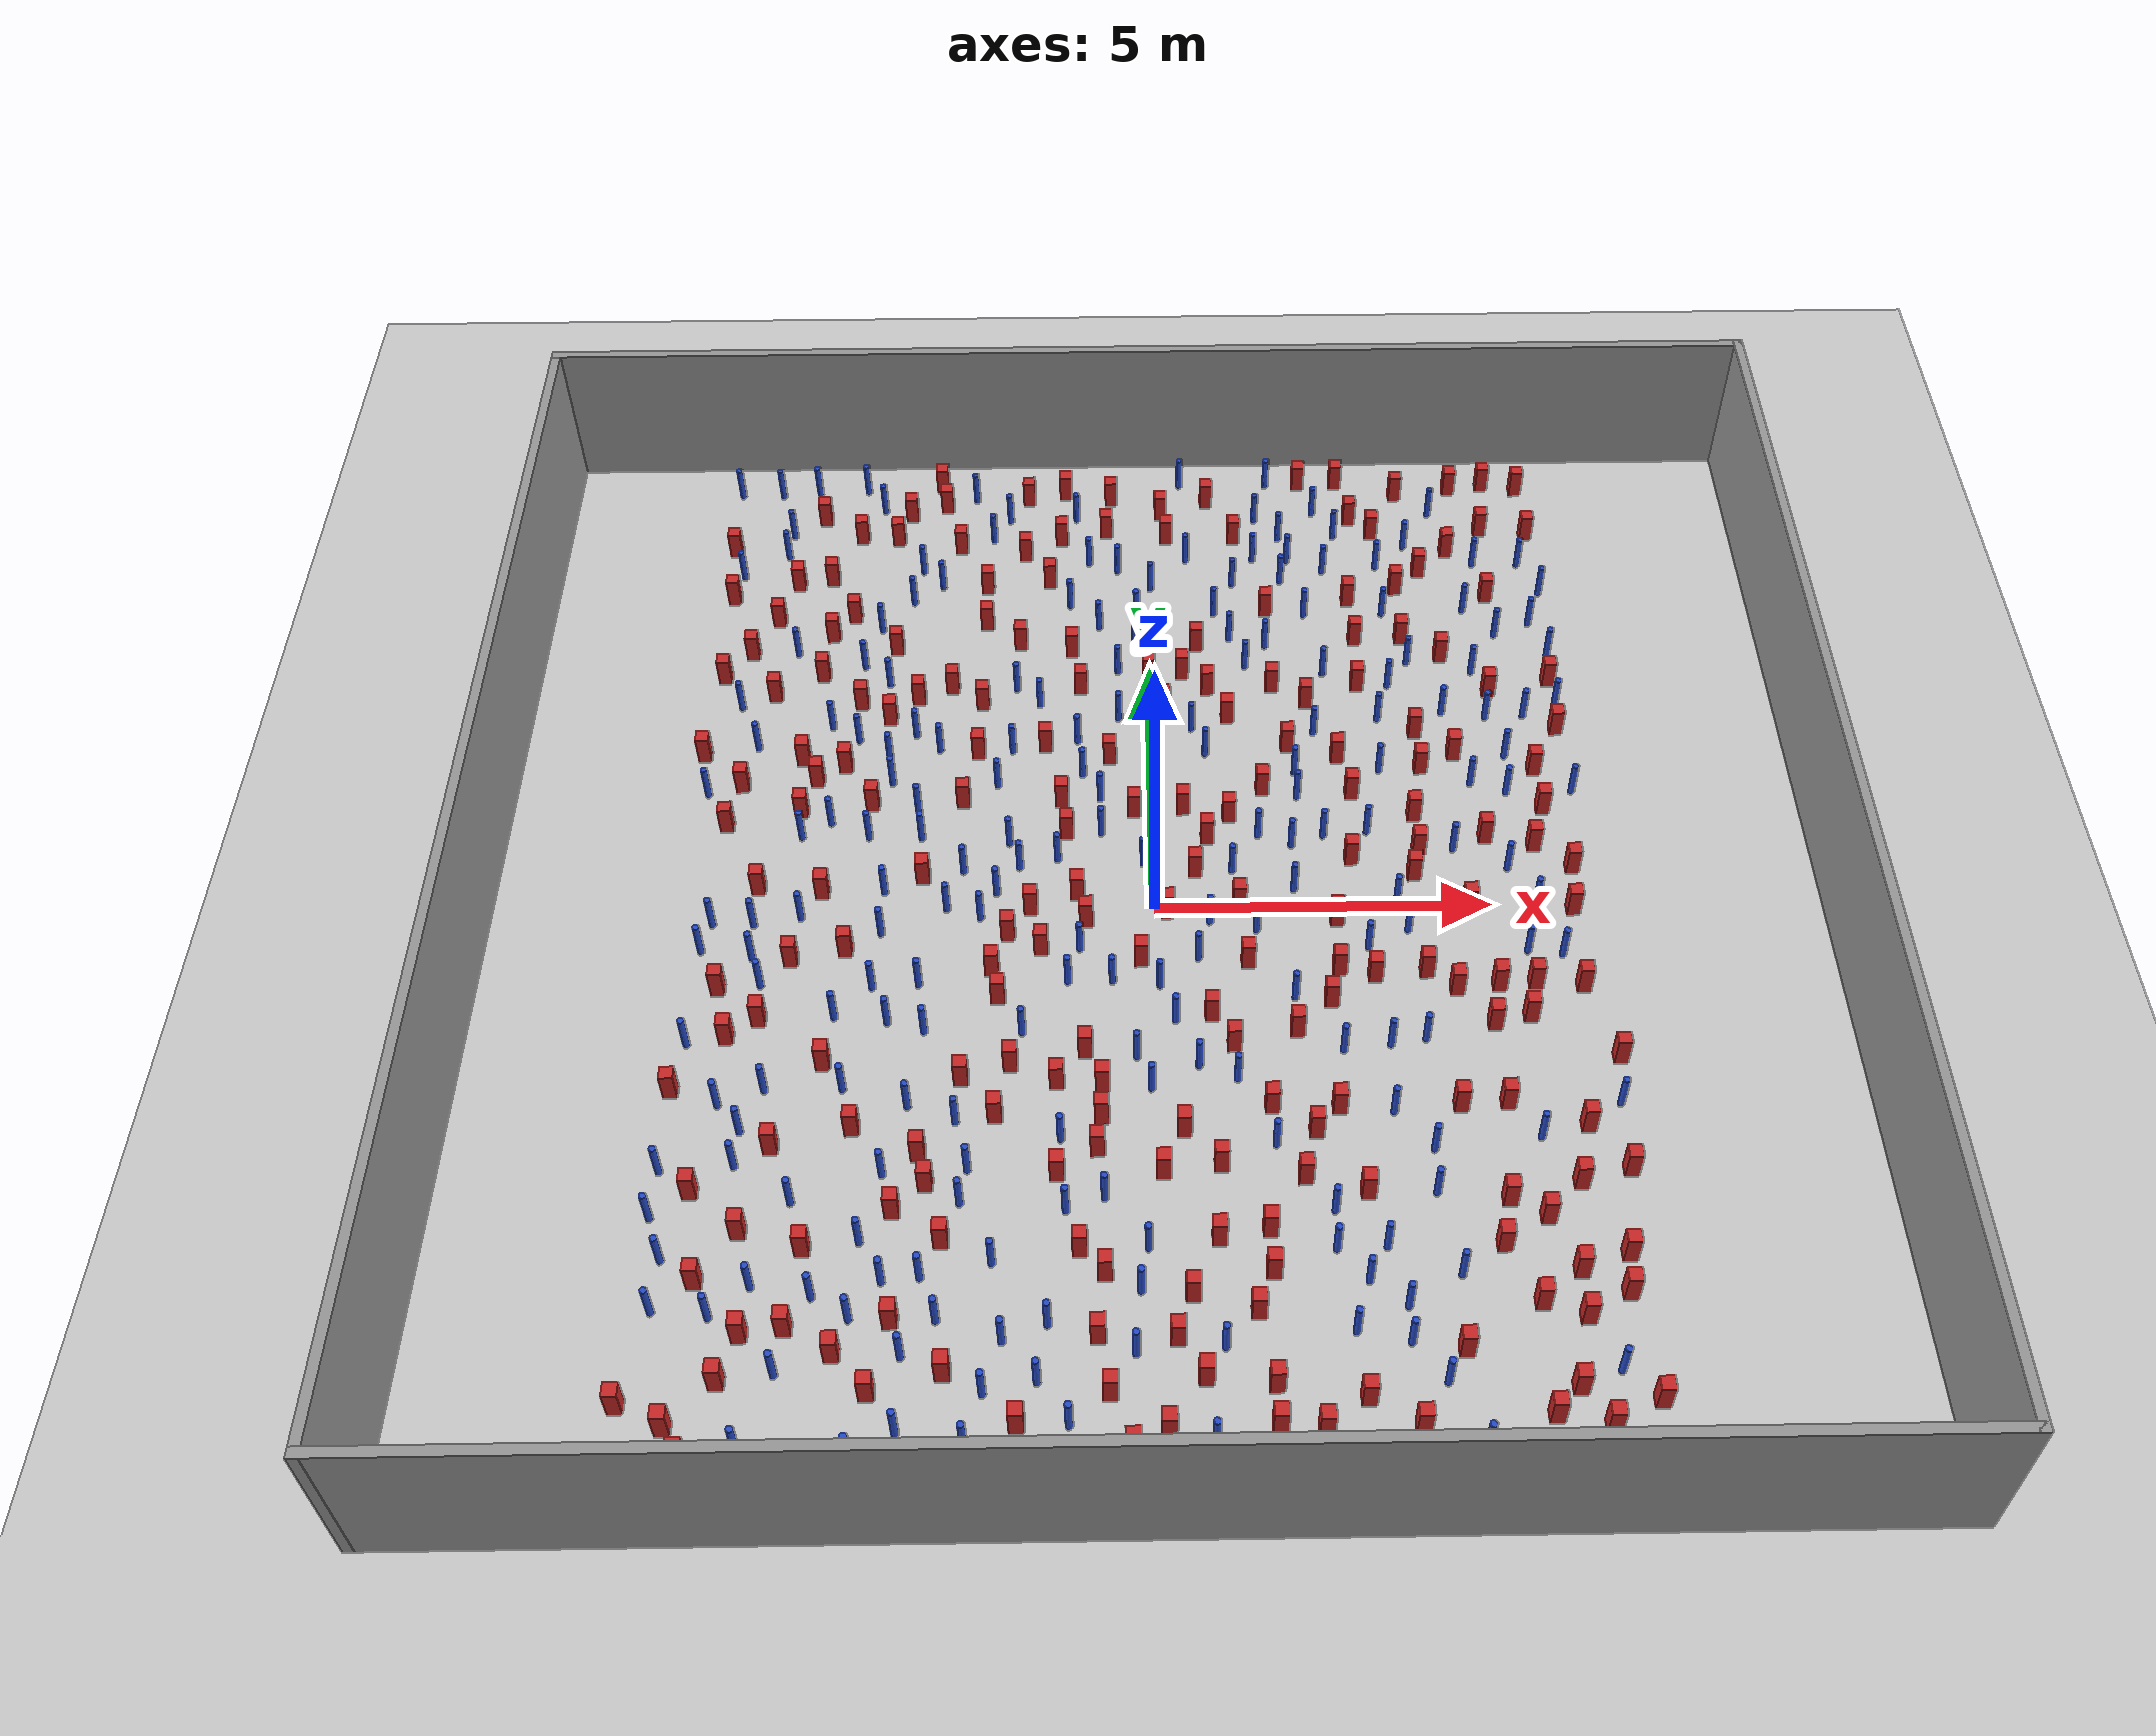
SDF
<sdf version="1.6">
 <world name="default">
  <light name="sun" type="directional">
   <pose>0 0 1000 0 -0 0</pose>
   <diffuse>0.8 0.8 0.8 1</diffuse>
   <specular>0.1 0.1 0.1 1</specular>
   <attenuation>
    <range>1000</range>
    <constant>0.9</constant>
    <linear>0.01</linear>
    <quadratic>0.001</quadratic>
   </attenuation>
   <direction>-0.5 0.5 -1</direction>
  </light>
  <model name="ground_plane">
   <static>1</static>
   <link name="link">
    <collision name="collision">
     <geometry><plane><normal>0 0 1</normal><size>100 100</size></plane></geometry>
     <surface><friction><ode><mu>100</mu><mu2>50</mu2></ode></friction></surface>
    </collision>
    <visual name="visual">
     <cast_shadows>0</cast_shadows>
     <geometry><plane><normal>0 0 1</normal><size>100 100</size></plane></geometry>
     <material>
      <ambient>1.0 1.0 1.0 1.0</ambient>
      <diffuse>0.8 0.8 0.8 1.0</diffuse>
      <specular>0.01 0.01 0.01 1.000000</specular>
     </material>
    </visual>
   </link>
  </model>
  <gravity>0 0 -9.8</gravity>
  <magnetic_field>6e-06 2.3e-05 -4.2e-05</magnetic_field>
  <atmosphere type="adiabatic"/>
  <physics name="default_physics" default="0" type="ode">
   <max_step_size>0.001</max_step_size>
   <real_time_factor>1</real_time_factor>
   <real_time_update_rate>1000</real_time_update_rate>
  </physics>
  <scene><ambient>0.4 0.4 0.4 1</ambient><background>0.7 0.7 0.7 1</background><shadows>1</shadows></scene>
  <spherical_coordinates>
   <surface_model>EARTH_WGS84</surface_model>
   <latitude_deg>0</latitude_deg>
   <longitude_deg>0</longitude_deg>
   <elevation>0</elevation>
   <heading_deg>0</heading_deg>
  </spherical_coordinates>
  <plugin name="gazebo_occupancy_map" filename="libgazebo_2Dmap_plugin.so">
   <map_resolution>0.05</map_resolution>
   <map_topic>generated_map</map_topic>
   <map_height>0.01</map_height>
   <map_size_x>50</map_size_x>
   <map_size_y>50</map_size_y>
  </plugin>
  <model name="NamedLocations">
   <static>true</static>
   <link name="DefaultStart"><pose>8.5 0 0 0 0 3.14</pose></link>
  </model>
  <model name="20x20_walls">
   <pose>0.044518 0.176112 0 0 -0 0</pose>
   <link name="Wall_1">
    <collision name="Wall_1_Collision">
     <geometry><box><size>20 0.15 2.5</size></box></geometry>
     <pose>0 0 1.25 0 -0 0</pose>
    </collision>
    <visual name="Wall_1_Visual">
     <pose>0 0 1.25 0 -0 0</pose>
     <geometry><box><size>20 0.15 2.5</size></box></geometry>
     <material>
      <script><uri>file://media/materials/scripts/gazebo.material</uri><name>Gazebo/Grey</name></script>
      <ambient>0.976471 0.992157 1 1</ambient>
     </material>
     <meta><layer>0</layer></meta>
    </visual>
    <pose>0 9.925 0 0 -0 0</pose>
   </link>
   <link name="Wall_3">
    <collision name="Wall_3_Collision">
     <geometry><box><size>20 0.15 2.5</size></box></geometry>
     <pose>0 0 1.25 0 -0 0</pose>
    </collision>
    <visual name="Wall_3_Visual">
     <pose>0 0 1.25 0 -0 0</pose>
     <geometry><box><size>20 0.15 2.5</size></box></geometry>
     <material>
      <script><uri>file://media/materials/scripts/gazebo.material</uri><name>Gazebo/Grey</name></script>
      <ambient>0.976471 0.992157 1 1</ambient>
     </material>
     <meta><layer>0</layer></meta>
    </visual>
    <pose>9.925 0 0 0 0 -1.5708</pose>
   </link>
   <link name="Wall_4">
    <collision name="Wall_4_Collision">
     <geometry><box><size>20 0.15 2.5</size></box></geometry>
     <pose>0 0 1.25 0 -0 0</pose>
    </collision>
    <visual name="Wall_4_Visual">
     <pose>0 0 1.25 0 -0 0</pose>
     <geometry><box><size>20 0.15 2.5</size></box></geometry>
     <material>
      <script><uri>file://media/materials/scripts/gazebo.material</uri><name>Gazebo/Grey</name></script>
      <ambient>0.976471 0.992157 1 1</ambient>
     </material>
     <meta><layer>0</layer></meta>
    </visual>
    <pose>0 -9.925 0 0 -0 3.14159</pose>
   </link>
   <link name="Wall_5">
    <collision name="Wall_5_Collision">
     <geometry><box><size>20 0.15 2.5</size></box></geometry>
     <pose>0 0 1.25 0 -0 0</pose>
    </collision>
    <visual name="Wall_5_Visual">
     <pose>0 0 1.25 0 -0 0</pose>
     <geometry><box><size>20 0.15 2.5</size></box></geometry>
     <material>
      <script><uri>file://media/materials/scripts/gazebo.material</uri><name>Gazebo/Grey</name></script>
      <ambient>0.976471 0.992157 1 1</ambient>
     </material>
     <meta><layer>0</layer></meta>
    </visual>
    <pose>-9.925 0 0 0 -0 1.5708</pose>
   </link>
   <static>1</static>
  </model>
  <model name="square_post_obstacle0">
   <static>true</static>
   <pose>-3.53075418306 9.46736991092 1.91545236811e-07 -7.35059704564e-06 1.12565212e-07 2.39332434364e-05</pose>
   <link name="link">
    <pose>0 0 0.25 0 -0 0</pose>
    <inertial>
     <mass>100</mass>
     <inertia>
      <ixx>0.166667</ixx>
      <ixy>0</ixy>
      <ixz>0</ixz>
      <iyy>0.166667</iyy>
      <iyz>0</iyz>
      <izz>0.166667</izz>
     </inertia>
    </inertial>
    <collision name="collision"><geometry><box><size>.2 .2 .5</size></box></geometry></collision>
    <visual name="visual">
     <geometry><box><size>.2 .2 .5</size></box></geometry>
     <material>
      <script><name>Gazebo/Red</name><uri>file://media/materials/scripts/gazebo.material</uri></script>
     </material>
    </visual>
   </link>
  </model>
  <model name="square_post_obstacle1">
   <static>true</static>
   <pose>-5.25605438137 4.89700262529 1.91545236811e-07 -7.35059704564e-06 1.12565212e-07 2.39332434364e-05</pose>
   <link name="link">
    <pose>0 0 0.25 0 -0 0</pose>
    <inertial>
     <mass>100</mass>
     <inertia>
      <ixx>0.166667</ixx>
      <ixy>0</ixy>
      <ixz>0</ixz>
      <iyy>0.166667</iyy>
      <iyz>0</iyz>
      <izz>0.166667</izz>
     </inertia>
    </inertial>
    <collision name="collision"><geometry><box><size>.2 .2 .5</size></box></geometry></collision>
    <visual name="visual">
     <geometry><box><size>.2 .2 .5</size></box></geometry>
     <material>
      <script><name>Gazebo/Red</name><uri>file://media/materials/scripts/gazebo.material</uri></script>
     </material>
    </visual>
   </link>
  </model>
  <model name="pole_obstacle0">
   <static>true</static>
   <pose>-3.31218589467 3.24684789584 7.38925637345e-09 -8.47170692798e-08 1.24976764939e-08 -1.74513093025e-07</pose>
   <link name="link">
    <pose>0 0 0.3 0 -0 0</pose>
    <inertial>
     <mass>1</mass>
     <inertia><ixx>0.145833</ixx><ixy>0</ixy><ixz>0</ixz><iyy>0.145833</iyy><iyz>0</iyz><izz>0.125</izz></inertia>
    </inertial>
    <collision name="collision">
     <geometry><cylinder><radius>0.05</radius><length>.6</length></cylinder></geometry>
    </collision>
    <visual name="visual">
     <geometry><cylinder><radius>0.05</radius><length>.6</length></cylinder></geometry>
     <material>
      <script><name>Gazebo/Blue</name><uri>file://media/materials/scripts/gazebo.material</uri></script>
     </material>
    </visual>
   </link>
  </model>
  <model name="square_post_obstacle2">
   <static>true</static>
   <pose>-4.12529514285 3.92472908485 1.91545236811e-07 -7.35059704564e-06 1.12565212e-07 2.39332434364e-05</pose>
   <link name="link">
    <pose>0 0 0.25 0 -0 0</pose>
    <inertial>
     <mass>100</mass>
     <inertia>
      <ixx>0.166667</ixx>
      <ixy>0</ixy>
      <ixz>0</ixz>
      <iyy>0.166667</iyy>
      <iyz>0</iyz>
      <izz>0.166667</izz>
     </inertia>
    </inertial>
    <collision name="collision"><geometry><box><size>.2 .2 .5</size></box></geometry></collision>
    <visual name="visual">
     <geometry><box><size>.2 .2 .5</size></box></geometry>
     <material>
      <script><name>Gazebo/Red</name><uri>file://media/materials/scripts/gazebo.material</uri></script>
     </material>
    </visual>
   </link>
  </model>
  <model name="pole_obstacle1">
   <static>true</static>
   <pose>1.38617735485 6.94967551149 7.38925637345e-09 -8.47170692799e-08 1.24976765033e-08 -1.74513093018e-07</pose>
   <link name="link">
    <pose>0 0 0.3 0 -0 0</pose>
    <inertial>
     <mass>1</mass>
     <inertia><ixx>0.145833</ixx><ixy>0</ixy><ixz>0</ixz><iyy>0.145833</iyy><iyz>0</iyz><izz>0.125</izz></inertia>
    </inertial>
    <collision name="collision">
     <geometry><cylinder><radius>0.05</radius><length>.6</length></cylinder></geometry>
    </collision>
    <visual name="visual">
     <geometry><cylinder><radius>0.05</radius><length>.6</length></cylinder></geometry>
     <material>
      <script><name>Gazebo/Blue</name><uri>file://media/materials/scripts/gazebo.material</uri></script>
     </material>
    </visual>
   </link>
  </model>
  <model name="square_post_obstacle3">
   <static>true</static>
   <pose>-0.789458256062 -3.69819431889 1.91545236811e-07 -7.35059704564e-06 1.12565212e-07 2.39332434364e-05</pose>
   <link name="link">
    <pose>0 0 0.25 0 -0 0</pose>
    <inertial>
     <mass>100</mass>
     <inertia>
      <ixx>0.166667</ixx>
      <ixy>0</ixy>
      <ixz>0</ixz>
      <iyy>0.166667</iyy>
      <iyz>0</iyz>
      <izz>0.166667</izz>
     </inertia>
    </inertial>
    <collision name="collision"><geometry><box><size>.2 .2 .5</size></box></geometry></collision>
    <visual name="visual">
     <geometry><box><size>.2 .2 .5</size></box></geometry>
     <material>
      <script><name>Gazebo/Red</name><uri>file://media/materials/scripts/gazebo.material</uri></script>
     </material>
    </visual>
   </link>
  </model>
  <model name="pole_obstacle2">
   <static>true</static>
   <pose>2.82099505134 8.70505590829 7.38925637345e-09 -8.47170692793e-08 1.24976764408e-08 -1.74513093041e-07</pose>
   <link name="link">
    <pose>0 0 0.3 0 -0 0</pose>
    <inertial>
     <mass>1</mass>
     <inertia><ixx>0.145833</ixx><ixy>0</ixy><ixz>0</ixz><iyy>0.145833</iyy><iyz>0</iyz><izz>0.125</izz></inertia>
    </inertial>
    <collision name="collision">
     <geometry><cylinder><radius>0.05</radius><length>.6</length></cylinder></geometry>
    </collision>
    <visual name="visual">
     <geometry><cylinder><radius>0.05</radius><length>.6</length></cylinder></geometry>
     <material>
      <script><name>Gazebo/Blue</name><uri>file://media/materials/scripts/gazebo.material</uri></script>
     </material>
    </visual>
   </link>
  </model>
  <model name="pole_obstacle3">
   <static>true</static>
   <pose>-1.21258136794 8.60759333295 7.38925637345e-09 -8.47170692798e-08 1.24976764881e-08 -1.74513093027e-07</pose>
   <link name="link">
    <pose>0 0 0.3 0 -0 0</pose>
    <inertial>
     <mass>1</mass>
     <inertia><ixx>0.145833</ixx><ixy>0</ixy><ixz>0</ixz><iyy>0.145833</iyy><iyz>0</iyz><izz>0.125</izz></inertia>
    </inertial>
    <collision name="collision">
     <geometry><cylinder><radius>0.05</radius><length>.6</length></cylinder></geometry>
    </collision>
    <visual name="visual">
     <geometry><cylinder><radius>0.05</radius><length>.6</length></cylinder></geometry>
     <material>
      <script><name>Gazebo/Blue</name><uri>file://media/materials/scripts/gazebo.material</uri></script>
     </material>
    </visual>
   </link>
  </model>
  <model name="square_post_obstacle4">
   <static>true</static>
   <pose>-5.67740192875 -7.65880468433 1.91545236811e-07 -7.35059704564e-06 1.12565212e-07 2.39332434364e-05</pose>
   <link name="link">
    <pose>0 0 0.25 0 -0 0</pose>
    <inertial>
     <mass>100</mass>
     <inertia>
      <ixx>0.166667</ixx>
      <ixy>0</ixy>
      <ixz>0</ixz>
      <iyy>0.166667</iyy>
      <iyz>0</iyz>
      <izz>0.166667</izz>
     </inertia>
    </inertial>
    <collision name="collision"><geometry><box><size>.2 .2 .5</size></box></geometry></collision>
    <visual name="visual">
     <geometry><box><size>.2 .2 .5</size></box></geometry>
     <material>
      <script><name>Gazebo/Red</name><uri>file://media/materials/scripts/gazebo.material</uri></script>
     </material>
    </visual>
   </link>
  </model>
  <model name="square_post_obstacle5">
   <static>true</static>
   <pose>2.1114799383 3.23724180372 1.91545236811e-07 -7.35059704564e-06 1.12565212e-07 2.39332434364e-05</pose>
   <link name="link">
    <pose>0 0 0.25 0 -0 0</pose>
    <inertial>
     <mass>100</mass>
     <inertia>
      <ixx>0.166667</ixx>
      <ixy>0</ixy>
      <ixz>0</ixz>
      <iyy>0.166667</iyy>
      <iyz>0</iyz>
      <izz>0.166667</izz>
     </inertia>
    </inertial>
    <collision name="collision"><geometry><box><size>.2 .2 .5</size></box></geometry></collision>
    <visual name="visual">
     <geometry><box><size>.2 .2 .5</size></box></geometry>
     <material>
      <script><name>Gazebo/Red</name><uri>file://media/materials/scripts/gazebo.material</uri></script>
     </material>
    </visual>
   </link>
  </model>
  <model name="square_post_obstacle6">
   <static>true</static>
   <pose>2.60345973972 9.44994082353 1.91545236811e-07 -7.35059704564e-06 1.12565212e-07 2.39332434364e-05</pose>
   <link name="link">
    <pose>0 0 0.25 0 -0 0</pose>
    <inertial>
     <mass>100</mass>
     <inertia>
      <ixx>0.166667</ixx>
      <ixy>0</ixy>
      <ixz>0</ixz>
      <iyy>0.166667</iyy>
      <iyz>0</iyz>
      <izz>0.166667</izz>
     </inertia>
    </inertial>
    <collision name="collision"><geometry><box><size>.2 .2 .5</size></box></geometry></collision>
    <visual name="visual">
     <geometry><box><size>.2 .2 .5</size></box></geometry>
     <material>
      <script><name>Gazebo/Red</name><uri>file://media/materials/scripts/gazebo.material</uri></script>
     </material>
    </visual>
   </link>
  </model>
  <model name="pole_obstacle4">
   <static>true</static>
   <pose>3.29963674855 -2.52704988164 7.38925637345e-09 -8.47170692798e-08 1.24976764939e-08 -1.74513093025e-07</pose>
   <link name="link">
    <pose>0 0 0.3 0 -0 0</pose>
    <inertial>
     <mass>1</mass>
     <inertia><ixx>0.145833</ixx><ixy>0</ixy><ixz>0</ixz><iyy>0.145833</iyy><iyz>0</iyz><izz>0.125</izz></inertia>
    </inertial>
    <collision name="collision">
     <geometry><cylinder><radius>0.05</radius><length>.6</length></cylinder></geometry>
    </collision>
    <visual name="visual">
     <geometry><cylinder><radius>0.05</radius><length>.6</length></cylinder></geometry>
     <material>
      <script><name>Gazebo/Blue</name><uri>file://media/materials/scripts/gazebo.material</uri></script>
     </material>
    </visual>
   </link>
  </model>
  <model name="pole_obstacle5">
   <static>true</static>
   <pose>-0.992801236177 7.50081790914 7.38925637345e-09 -8.47170692799e-08 1.2497676509e-08 -1.74513093015e-07</pose>
   <link name="link">
    <pose>0 0 0.3 0 -0 0</pose>
    <inertial>
     <mass>1</mass>
     <inertia><ixx>0.145833</ixx><ixy>0</ixy><ixz>0</ixz><iyy>0.145833</iyy><iyz>0</iyz><izz>0.125</izz></inertia>
    </inertial>
    <collision name="collision">
     <geometry><cylinder><radius>0.05</radius><length>.6</length></cylinder></geometry>
    </collision>
    <visual name="visual">
     <geometry><cylinder><radius>0.05</radius><length>.6</length></cylinder></geometry>
     <material>
      <script><name>Gazebo/Blue</name><uri>file://media/materials/scripts/gazebo.material</uri></script>
     </material>
    </visual>
   </link>
  </model>
  <model name="square_post_obstacle7">
   <static>true</static>
   <pose>5.32515798996 -2.06593190637 1.91545236811e-07 -7.35059704564e-06 1.12565212e-07 2.39332434364e-05</pose>
   <link name="link">
    <pose>0 0 0.25 0 -0 0</pose>
    <inertial>
     <mass>100</mass>
     <inertia>
      <ixx>0.166667</ixx>
      <ixy>0</ixy>
      <ixz>0</ixz>
      <iyy>0.166667</iyy>
      <iyz>0</iyz>
      <izz>0.166667</izz>
     </inertia>
    </inertial>
    <collision name="collision"><geometry><box><size>.2 .2 .5</size></box></geometry></collision>
    <visual name="visual">
     <geometry><box><size>.2 .2 .5</size></box></geometry>
     <material>
      <script><name>Gazebo/Red</name><uri>file://media/materials/scripts/gazebo.material</uri></script>
     </material>
    </visual>
   </link>
  </model>
  <model name="square_post_obstacle8">
   <static>true</static>
   <pose>1.90882104758 6.30090376429 1.91545236811e-07 -7.35059704564e-06 1.12565212e-07 2.39332434364e-05</pose>
   <link name="link">
    <pose>0 0 0.25 0 -0 0</pose>
    <inertial>
     <mass>100</mass>
     <inertia>
      <ixx>0.166667</ixx>
      <ixy>0</ixy>
      <ixz>0</ixz>
      <iyy>0.166667</iyy>
      <iyz>0</iyz>
      <izz>0.166667</izz>
     </inertia>
    </inertial>
    <collision name="collision"><geometry><box><size>.2 .2 .5</size></box></geometry></collision>
    <visual name="visual">
     <geometry><box><size>.2 .2 .5</size></box></geometry>
     <material>
      <script><name>Gazebo/Red</name><uri>file://media/materials/scripts/gazebo.material</uri></script>
     </material>
    </visual>
   </link>
  </model>
  <model name="pole_obstacle6">
   <static>true</static>
   <pose>5.6374758379 5.68235100578 7.38925637345e-09 -8.47170692796e-08 1.24976764786e-08 -1.74513093032e-07</pose>
   <link name="link">
    <pose>0 0 0.3 0 -0 0</pose>
    <inertial>
     <mass>1</mass>
     <inertia><ixx>0.145833</ixx><ixy>0</ixy><ixz>0</ixz><iyy>0.145833</iyy><iyz>0</iyz><izz>0.125</izz></inertia>
    </inertial>
    <collision name="collision">
     <geometry><cylinder><radius>0.05</radius><length>.6</length></cylinder></geometry>
    </collision>
    <visual name="visual">
     <geometry><cylinder><radius>0.05</radius><length>.6</length></cylinder></geometry>
     <material>
      <script><name>Gazebo/Blue</name><uri>file://media/materials/scripts/gazebo.material</uri></script>
     </material>
    </visual>
   </link>
  </model>
  <model name="pole_obstacle7">
   <static>true</static>
   <pose>-5.22169933292 -0.105891624852 7.38925637345e-09 -8.47170692799e-08 1.24976765039e-08 -1.74513093019e-07</pose>
   <link name="link">
    <pose>0 0 0.3 0 -0 0</pose>
    <inertial>
     <mass>1</mass>
     <inertia><ixx>0.145833</ixx><ixy>0</ixy><ixz>0</ixz><iyy>0.145833</iyy><iyz>0</iyz><izz>0.125</izz></inertia>
    </inertial>
    <collision name="collision">
     <geometry><cylinder><radius>0.05</radius><length>.6</length></cylinder></geometry>
    </collision>
    <visual name="visual">
     <geometry><cylinder><radius>0.05</radius><length>.6</length></cylinder></geometry>
     <material>
      <script><name>Gazebo/Blue</name><uri>file://media/materials/scripts/gazebo.material</uri></script>
     </material>
    </visual>
   </link>
  </model>
  <model name="square_post_obstacle9">
   <static>true</static>
   <pose>3.91278412913 -1.24302501316 1.91545236811e-07 -7.35059704564e-06 1.12565212e-07 2.39332434364e-05</pose>
   <link name="link">
    <pose>0 0 0.25 0 -0 0</pose>
    <inertial>
     <mass>100</mass>
     <inertia>
      <ixx>0.166667</ixx>
      <ixy>0</ixy>
      <ixz>0</ixz>
      <iyy>0.166667</iyy>
      <iyz>0</iyz>
      <izz>0.166667</izz>
     </inertia>
    </inertial>
    <collision name="collision"><geometry><box><size>.2 .2 .5</size></box></geometry></collision>
    <visual name="visual">
     <geometry><box><size>.2 .2 .5</size></box></geometry>
     <material>
      <script><name>Gazebo/Red</name><uri>file://media/materials/scripts/gazebo.material</uri></script>
     </material>
    </visual>
   </link>
  </model>
  <model name="square_post_obstacle10">
   <static>true</static>
   <pose>0.0550783046898 -8.40257800408 1.91545236811e-07 -7.35059704564e-06 1.12565212e-07 2.39332434364e-05</pose>
   <link name="link">
    <pose>0 0 0.25 0 -0 0</pose>
    <inertial>
     <mass>100</mass>
     <inertia>
      <ixx>0.166667</ixx>
      <ixy>0</ixy>
      <ixz>0</ixz>
      <iyy>0.166667</iyy>
      <iyz>0</iyz>
      <izz>0.166667</izz>
     </inertia>
    </inertial>
    <collision name="collision"><geometry><box><size>.2 .2 .5</size></box></geometry></collision>
    <visual name="visual">
     <geometry><box><size>.2 .2 .5</size></box></geometry>
     <material>
      <script><name>Gazebo/Red</name><uri>file://media/materials/scripts/gazebo.material</uri></script>
     </material>
    </visual>
   </link>
  </model>
  <model name="square_post_obstacle11">
   <static>true</static>
   <pose>1.56655398483 -3.56114634323 1.91545236811e-07 -7.35059704564e-06 1.12565212e-07 2.39332434364e-05</pose>
   <link name="link">
    <pose>0 0 0.25 0 -0 0</pose>
    <inertial>
     <mass>100</mass>
     <inertia>
      <ixx>0.166667</ixx>
      <ixy>0</ixy>
      <ixz>0</ixz>
      <iyy>0.166667</iyy>
      <iyz>0</iyz>
      <izz>0.166667</izz>
     </inertia>
    </inertial>
    <collision name="collision"><geometry><box><size>.2 .2 .5</size></box></geometry></collision>
    <visual name="visual">
     <geometry><box><size>.2 .2 .5</size></box></geometry>
     <material>
      <script><name>Gazebo/Red</name><uri>file://media/materials/scripts/gazebo.material</uri></script>
     </material>
    </visual>
   </link>
  </model>
  <model name="square_post_obstacle12">
   <static>true</static>
   <pose>0.781799811374 -1.9727818271 1.91545236811e-07 -7.35059704564e-06 1.12565212e-07 2.39332434364e-05</pose>
   <link name="link">
    <pose>0 0 0.25 0 -0 0</pose>
    <inertial>
     <mass>100</mass>
     <inertia>
      <ixx>0.166667</ixx>
      <ixy>0</ixy>
      <ixz>0</ixz>
      <iyy>0.166667</iyy>
      <iyz>0</iyz>
      <izz>0.166667</izz>
     </inertia>
    </inertial>
    <collision name="collision"><geometry><box><size>.2 .2 .5</size></box></geometry></collision>
    <visual name="visual">
     <geometry><box><size>.2 .2 .5</size></box></geometry>
     <material>
      <script><name>Gazebo/Red</name><uri>file://media/materials/scripts/gazebo.material</uri></script>
     </material>
    </visual>
   </link>
  </model>
  <model name="square_post_obstacle13">
   <static>true</static>
   <pose>-1.41700734164 -3.11351786145 1.91545236811e-07 -7.35059704564e-06 1.12565212e-07 2.39332434364e-05</pose>
   <link name="link">
    <pose>0 0 0.25 0 -0 0</pose>
    <inertial>
     <mass>100</mass>
     <inertia>
      <ixx>0.166667</ixx>
      <ixy>0</ixy>
      <ixz>0</ixz>
      <iyy>0.166667</iyy>
      <iyz>0</iyz>
      <izz>0.166667</izz>
     </inertia>
    </inertial>
    <collision name="collision"><geometry><box><size>.2 .2 .5</size></box></geometry></collision>
    <visual name="visual">
     <geometry><box><size>.2 .2 .5</size></box></geometry>
     <material>
      <script><name>Gazebo/Red</name><uri>file://media/materials/scripts/gazebo.material</uri></script>
     </material>
    </visual>
   </link>
  </model>
  <model name="pole_obstacle8">
   <static>true</static>
   <pose>-4.06872563296 -6.78109198846 7.38925637345e-09 -8.47170692796e-08 1.24976764786e-08 -1.74513093032e-07</pose>
   <link name="link">
    <pose>0 0 0.3 0 -0 0</pose>
    <inertial>
     <mass>1</mass>
     <inertia><ixx>0.145833</ixx><ixy>0</ixy><ixz>0</ixz><iyy>0.145833</iyy><iyz>0</iyz><izz>0.125</izz></inertia>
    </inertial>
    <collision name="collision">
     <geometry><cylinder><radius>0.05</radius><length>.6</length></cylinder></geometry>
    </collision>
    <visual name="visual">
     <geometry><cylinder><radius>0.05</radius><length>.6</length></cylinder></geometry>
     <material>
      <script><name>Gazebo/Blue</name><uri>file://media/materials/scripts/gazebo.material</uri></script>
     </material>
    </visual>
   </link>
  </model>
  <model name="square_post_obstacle14">
   <static>true</static>
   <pose>6.14993961561 -1.53402861949 1.91545236811e-07 -7.35059704564e-06 1.12565212e-07 2.39332434364e-05</pose>
   <link name="link">
    <pose>0 0 0.25 0 -0 0</pose>
    <inertial>
     <mass>100</mass>
     <inertia>
      <ixx>0.166667</ixx>
      <ixy>0</ixy>
      <ixz>0</ixz>
      <iyy>0.166667</iyy>
      <iyz>0</iyz>
      <izz>0.166667</izz>
     </inertia>
    </inertial>
    <collision name="collision"><geometry><box><size>.2 .2 .5</size></box></geometry></collision>
    <visual name="visual">
     <geometry><box><size>.2 .2 .5</size></box></geometry>
     <material>
      <script><name>Gazebo/Red</name><uri>file://media/materials/scripts/gazebo.material</uri></script>
     </material>
    </visual>
   </link>
  </model>
  <model name="square_post_obstacle15">
   <static>true</static>
   <pose>5.02085969405 7.69715390304 1.91545236811e-07 -7.35059704564e-06 1.12565212e-07 2.39332434364e-05</pose>
   <link name="link">
    <pose>0 0 0.25 0 -0 0</pose>
    <inertial>
     <mass>100</mass>
     <inertia>
      <ixx>0.166667</ixx>
      <ixy>0</ixy>
      <ixz>0</ixz>
      <iyy>0.166667</iyy>
      <iyz>0</iyz>
      <izz>0.166667</izz>
     </inertia>
    </inertial>
    <collision name="collision"><geometry><box><size>.2 .2 .5</size></box></geometry></collision>
    <visual name="visual">
     <geometry><box><size>.2 .2 .5</size></box></geometry>
     <material>
      <script><name>Gazebo/Red</name><uri>file://media/materials/scripts/gazebo.material</uri></script>
     </material>
    </visual>
   </link>
  </model>
  <model name="square_post_obstacle16">
   <static>true</static>
   <pose>1.46860966695 -6.16280772476 1.91545236811e-07 -7.35059704564e-06 1.12565212e-07 2.39332434364e-05</pose>
   <link name="link">
    <pose>0 0 0.25 0 -0 0</pose>
    <inertial>
     <mass>100</mass>
     <inertia>
      <ixx>0.166667</ixx>
      <ixy>0</ixy>
      <ixz>0</ixz>
      <iyy>0.166667</iyy>
      <iyz>0</iyz>
      <izz>0.166667</izz>
     </inertia>
    </inertial>
    <collision name="collision"><geometry><box><size>.2 .2 .5</size></box></geometry></collision>
    <visual name="visual">
     <geometry><box><size>.2 .2 .5</size></box></geometry>
     <material>
      <script><name>Gazebo/Red</name><uri>file://media/materials/scripts/gazebo.material</uri></script>
     </material>
    </visual>
   </link>
  </model>
  <model name="pole_obstacle9">
   <static>true</static>
   <pose>-2.39047537825 2.48837726105 7.38925637345e-09 -8.47170692798e-08 1.24976764939e-08 -1.74513093025e-07</pose>
   <link name="link">
    <pose>0 0 0.3 0 -0 0</pose>
    <inertial>
     <mass>1</mass>
     <inertia><ixx>0.145833</ixx><ixy>0</ixy><ixz>0</ixz><iyy>0.145833</iyy><iyz>0</iyz><izz>0.125</izz></inertia>
    </inertial>
    <collision name="collision">
     <geometry><cylinder><radius>0.05</radius><length>.6</length></cylinder></geometry>
    </collision>
    <visual name="visual">
     <geometry><cylinder><radius>0.05</radius><length>.6</length></cylinder></geometry>
     <material>
      <script><name>Gazebo/Blue</name><uri>file://media/materials/scripts/gazebo.material</uri></script>
     </material>
    </visual>
   </link>
  </model>
  <model name="square_post_obstacle17">
   <static>true</static>
   <pose>-6.07549606696 6.16473758936 1.91545236811e-07 -7.35059704564e-06 1.12565212e-07 2.39332434364e-05</pose>
   <link name="link">
    <pose>0 0 0.25 0 -0 0</pose>
    <inertial>
     <mass>100</mass>
     <inertia>
      <ixx>0.166667</ixx>
      <ixy>0</ixy>
      <ixz>0</ixz>
      <iyy>0.166667</iyy>
      <iyz>0</iyz>
      <izz>0.166667</izz>
     </inertia>
    </inertial>
    <collision name="collision"><geometry><box><size>.2 .2 .5</size></box></geometry></collision>
    <visual name="visual">
     <geometry><box><size>.2 .2 .5</size></box></geometry>
     <material>
      <script><name>Gazebo/Red</name><uri>file://media/materials/scripts/gazebo.material</uri></script>
     </material>
    </visual>
   </link>
  </model>
  <model name="square_post_obstacle18">
   <static>true</static>
   <pose>-3.52603695999 -6.82466076162 1.91545236811e-07 -7.35059704564e-06 1.12565212e-07 2.39332434364e-05</pose>
   <link name="link">
    <pose>0 0 0.25 0 -0 0</pose>
    <inertial>
     <mass>100</mass>
     <inertia>
      <ixx>0.166667</ixx>
      <ixy>0</ixy>
      <ixz>0</ixz>
      <iyy>0.166667</iyy>
      <iyz>0</iyz>
      <izz>0.166667</izz>
     </inertia>
    </inertial>
    <collision name="collision"><geometry><box><size>.2 .2 .5</size></box></geometry></collision>
    <visual name="visual">
     <geometry><box><size>.2 .2 .5</size></box></geometry>
     <material>
      <script><name>Gazebo/Red</name><uri>file://media/materials/scripts/gazebo.material</uri></script>
     </material>
    </visual>
   </link>
  </model>
  <model name="pole_obstacle10">
   <static>true</static>
   <pose>-2.24000977725 -5.9753968946 7.38925637345e-09 -8.47170692798e-08 1.24976765033e-08 -1.74513093019e-07</pose>
   <link name="link">
    <pose>0 0 0.3 0 -0 0</pose>
    <inertial>
     <mass>1</mass>
     <inertia><ixx>0.145833</ixx><ixy>0</ixy><ixz>0</ixz><iyy>0.145833</iyy><iyz>0</iyz><izz>0.125</izz></inertia>
    </inertial>
    <collision name="collision">
     <geometry><cylinder><radius>0.05</radius><length>.6</length></cylinder></geometry>
    </collision>
    <visual name="visual">
     <geometry><cylinder><radius>0.05</radius><length>.6</length></cylinder></geometry>
     <material>
      <script><name>Gazebo/Blue</name><uri>file://media/materials/scripts/gazebo.material</uri></script>
     </material>
    </visual>
   </link>
  </model>
  <model name="square_post_obstacle19">
   <static>true</static>
   <pose>2.57718396046 -8.00460723232 1.91545236811e-07 -7.35059704564e-06 1.12565212e-07 2.39332434364e-05</pose>
   <link name="link">
    <pose>0 0 0.25 0 -0 0</pose>
    <inertial>
     <mass>100</mass>
     <inertia>
      <ixx>0.166667</ixx>
      <ixy>0</ixy>
      <ixz>0</ixz>
      <iyy>0.166667</iyy>
      <iyz>0</iyz>
      <izz>0.166667</izz>
     </inertia>
    </inertial>
    <collision name="collision"><geometry><box><size>.2 .2 .5</size></box></geometry></collision>
    <visual name="visual">
     <geometry><box><size>.2 .2 .5</size></box></geometry>
     <material>
      <script><name>Gazebo/Red</name><uri>file://media/materials/scripts/gazebo.material</uri></script>
     </material>
    </visual>
   </link>
  </model>
  <model name="pole_obstacle11">
   <static>true</static>
   <pose>1.52577611234 5.01605634758 7.38925637345e-09 -8.47170692799e-08 1.24976765033e-08 -1.74513093018e-07</pose>
   <link name="link">
    <pose>0 0 0.3 0 -0 0</pose>
    <inertial>
     <mass>1</mass>
     <inertia><ixx>0.145833</ixx><ixy>0</ixy><ixz>0</ixz><iyy>0.145833</iyy><iyz>0</iyz><izz>0.125</izz></inertia>
    </inertial>
    <collision name="collision">
     <geometry><cylinder><radius>0.05</radius><length>.6</length></cylinder></geometry>
    </collision>
    <visual name="visual">
     <geometry><cylinder><radius>0.05</radius><length>.6</length></cylinder></geometry>
     <material>
      <script><name>Gazebo/Blue</name><uri>file://media/materials/scripts/gazebo.material</uri></script>
     </material>
    </visual>
   </link>
  </model>
  <model name="square_post_obstacle20">
   <static>true</static>
   <pose>6.37773901293 -4.66234504108 1.91545236811e-07 -7.35059704564e-06 1.12565212e-07 2.39332434364e-05</pose>
   <link name="link">
    <pose>0 0 0.25 0 -0 0</pose>
    <inertial>
     <mass>100</mass>
     <inertia>
      <ixx>0.166667</ixx>
      <ixy>0</ixy>
      <ixz>0</ixz>
      <iyy>0.166667</iyy>
      <iyz>0</iyz>
      <izz>0.166667</izz>
     </inertia>
    </inertial>
    <collision name="collision"><geometry><box><size>.2 .2 .5</size></box></geometry></collision>
    <visual name="visual">
     <geometry><box><size>.2 .2 .5</size></box></geometry>
     <material>
      <script><name>Gazebo/Red</name><uri>file://media/materials/scripts/gazebo.material</uri></script>
     </material>
    </visual>
   </link>
  </model>
  <model name="pole_obstacle12">
   <static>true</static>
   <pose>-6.2879917336 9.29565912501 7.38925637345e-09 -8.471706928e-08 1.24976765081e-08 -1.74513093015e-07</pose>
   <link name="link">
    <pose>0 0 0.3 0 -0 0</pose>
    <inertial>
     <mass>1</mass>
     <inertia><ixx>0.145833</ixx><ixy>0</ixy><ixz>0</ixz><iyy>0.145833</iyy><iyz>0</iyz><izz>0.125</izz></inertia>
    </inertial>
    <collision name="collision">
     <geometry><cylinder><radius>0.05</radius><length>.6</length></cylinder></geometry>
    </collision>
    <visual name="visual">
     <geometry><cylinder><radius>0.05</radius><length>.6</length></cylinder></geometry>
     <material>
      <script><name>Gazebo/Blue</name><uri>file://media/materials/scripts/gazebo.material</uri></script>
     </material>
    </visual>
   </link>
  </model>
  <model name="square_post_obstacle21">
   <static>true</static>
   <pose>-1.63938460143 7.04076987907 1.91545236811e-07 -7.35059704564e-06 1.12565212e-07 2.39332434364e-05</pose>
   <link name="link">
    <pose>0 0 0.25 0 -0 0</pose>
    <inertial>
     <mass>100</mass>
     <inertia>
      <ixx>0.166667</ixx>
      <ixy>0</ixy>
      <ixz>0</ixz>
      <iyy>0.166667</iyy>
      <iyz>0</iyz>
      <izz>0.166667</izz>
     </inertia>
    </inertial>
    <collision name="collision"><geometry><box><size>.2 .2 .5</size></box></geometry></collision>
    <visual name="visual">
     <geometry><box><size>.2 .2 .5</size></box></geometry>
     <material>
      <script><name>Gazebo/Red</name><uri>file://media/materials/scripts/gazebo.material</uri></script>
     </material>
    </visual>
   </link>
  </model>
  <model name="pole_obstacle13">
   <static>true</static>
   <pose>3.23759024392 1.45108022356 7.38925637345e-09 -8.471706928e-08 1.24976765152e-08 -1.74513093012e-07</pose>
   <link name="link">
    <pose>0 0 0.3 0 -0 0</pose>
    <inertial>
     <mass>1</mass>
     <inertia><ixx>0.145833</ixx><ixy>0</ixy><ixz>0</ixz><iyy>0.145833</iyy><iyz>0</iyz><izz>0.125</izz></inertia>
    </inertial>
    <collision name="collision">
     <geometry><cylinder><radius>0.05</radius><length>.6</length></cylinder></geometry>
    </collision>
    <visual name="visual">
     <geometry><cylinder><radius>0.05</radius><length>.6</length></cylinder></geometry>
     <material>
      <script><name>Gazebo/Blue</name><uri>file://media/materials/scripts/gazebo.material</uri></script>
     </material>
    </visual>
   </link>
  </model>
  <model name="square_post_obstacle22">
   <static>true</static>
   <pose>-2.26513360312 -3.66411039901 1.91545236811e-07 -7.35059704564e-06 1.12565212e-07 2.39332434364e-05</pose>
   <link name="link">
    <pose>0 0 0.25 0 -0 0</pose>
    <inertial>
     <mass>100</mass>
     <inertia>
      <ixx>0.166667</ixx>
      <ixy>0</ixy>
      <ixz>0</ixz>
      <iyy>0.166667</iyy>
      <iyz>0</iyz>
      <izz>0.166667</izz>
     </inertia>
    </inertial>
    <collision name="collision"><geometry><box><size>.2 .2 .5</size></box></geometry></collision>
    <visual name="visual">
     <geometry><box><size>.2 .2 .5</size></box></geometry>
     <material>
      <script><name>Gazebo/Red</name><uri>file://media/materials/scripts/gazebo.material</uri></script>
     </material>
    </visual>
   </link>
  </model>
  <model name="pole_obstacle14">
   <static>true</static>
   <pose>-2.80480990829 -3.74324165392 7.38925637345e-09 -8.47170692798e-08 1.24976764939e-08 -1.74513093025e-07</pose>
   <link name="link">
    <pose>0 0 0.3 0 -0 0</pose>
    <inertial>
     <mass>1</mass>
     <inertia><ixx>0.145833</ixx><ixy>0</ixy><ixz>0</ixz><iyy>0.145833</iyy><iyz>0</iyz><izz>0.125</izz></inertia>
    </inertial>
    <collision name="collision">
     <geometry><cylinder><radius>0.05</radius><length>.6</length></cylinder></geometry>
    </collision>
    <visual name="visual">
     <geometry><cylinder><radius>0.05</radius><length>.6</length></cylinder></geometry>
     <material>
      <script><name>Gazebo/Blue</name><uri>file://media/materials/scripts/gazebo.material</uri></script>
     </material>
    </visual>
   </link>
  </model>
  <model name="pole_obstacle15">
   <static>true</static>
   <pose>5.1811139625 -9.17330770869 7.38925637345e-09 -8.471706928e-08 1.24976765081e-08 -1.74513093015e-07</pose>
   <link name="link">
    <pose>0 0 0.3 0 -0 0</pose>
    <inertial>
     <mass>1</mass>
     <inertia><ixx>0.145833</ixx><ixy>0</ixy><ixz>0</ixz><iyy>0.145833</iyy><iyz>0</iyz><izz>0.125</izz></inertia>
    </inertial>
    <collision name="collision">
     <geometry><cylinder><radius>0.05</radius><length>.6</length></cylinder></geometry>
    </collision>
    <visual name="visual">
     <geometry><cylinder><radius>0.05</radius><length>.6</length></cylinder></geometry>
     <material>
      <script><name>Gazebo/Blue</name><uri>file://media/materials/scripts/gazebo.material</uri></script>
     </material>
    </visual>
   </link>
  </model>
  <model name="pole_obstacle16">
   <static>true</static>
   <pose>-2.01565378266 0.821097180854 7.38925637345e-09 -8.47170692799e-08 1.2497676506e-08 -1.74513093019e-07</pose>
   <link name="link">
    <pose>0 0 0.3 0 -0 0</pose>
    <inertial>
     <mass>1</mass>
     <inertia><ixx>0.145833</ixx><ixy>0</ixy><ixz>0</ixz><iyy>0.145833</iyy><iyz>0</iyz><izz>0.125</izz></inertia>
    </inertial>
    <collision name="collision">
     <geometry><cylinder><radius>0.05</radius><length>.6</length></cylinder></geometry>
    </collision>
    <visual name="visual">
     <geometry><cylinder><radius>0.05</radius><length>.6</length></cylinder></geometry>
     <material>
      <script><name>Gazebo/Blue</name><uri>file://media/materials/scripts/gazebo.material</uri></script>
     </material>
    </visual>
   </link>
  </model>
  <model name="square_post_obstacle23">
   <static>true</static>
   <pose>-1.86108736659 -8.30667899572 1.91545236811e-07 -7.35059704564e-06 1.12565212e-07 2.39332434364e-05</pose>
   <link name="link">
    <pose>0 0 0.25 0 -0 0</pose>
    <inertial>
     <mass>100</mass>
     <inertia>
      <ixx>0.166667</ixx>
      <ixy>0</ixy>
      <ixz>0</ixz>
      <iyy>0.166667</iyy>
      <iyz>0</iyz>
      <izz>0.166667</izz>
     </inertia>
    </inertial>
    <collision name="collision"><geometry><box><size>.2 .2 .5</size></box></geometry></collision>
    <visual name="visual">
     <geometry><box><size>.2 .2 .5</size></box></geometry>
     <material>
      <script><name>Gazebo/Red</name><uri>file://media/materials/scripts/gazebo.material</uri></script>
     </material>
    </visual>
   </link>
  </model>
  <model name="pole_obstacle17">
   <static>true</static>
   <pose>-1.91725916529 -2.24138637136 7.38925637345e-09 -8.47170692799e-08 1.24976765053e-08 -1.74513093017e-07</pose>
   <link name="link">
    <pose>0 0 0.3 0 -0 0</pose>
    <inertial>
     <mass>1</mass>
     <inertia><ixx>0.145833</ixx><ixy>0</ixy><ixz>0</ixz><iyy>0.145833</iyy><iyz>0</iyz><izz>0.125</izz></inertia>
    </inertial>
    <collision name="collision">
     <geometry><cylinder><radius>0.05</radius><length>.6</length></cylinder></geometry>
    </collision>
    <visual name="visual">
     <geometry><cylinder><radius>0.05</radius><length>.6</length></cylinder></geometry>
     <material>
      <script><name>Gazebo/Blue</name><uri>file://media/materials/scripts/gazebo.material</uri></script>
     </material>
    </visual>
   </link>
  </model>
  <model name="square_post_obstacle24">
   <static>true</static>
   <pose>6.09427884108 -6.54319197838 1.91545236811e-07 -7.35059704564e-06 1.12565212e-07 2.39332434364e-05</pose>
   <link name="link">
    <pose>0 0 0.25 0 -0 0</pose>
    <inertial>
     <mass>100</mass>
     <inertia>
      <ixx>0.166667</ixx>
      <ixy>0</ixy>
      <ixz>0</ixz>
      <iyy>0.166667</iyy>
      <iyz>0</iyz>
      <izz>0.166667</izz>
     </inertia>
    </inertial>
    <collision name="collision"><geometry><box><size>.2 .2 .5</size></box></geometry></collision>
    <visual name="visual">
     <geometry><box><size>.2 .2 .5</size></box></geometry>
     <material>
      <script><name>Gazebo/Red</name><uri>file://media/materials/scripts/gazebo.material</uri></script>
     </material>
    </visual>
   </link>
  </model>
  <model name="square_post_obstacle25">
   <static>true</static>
   <pose>-6.1199734361 -6.20377883608 1.91545236811e-07 -7.35059704564e-06 1.12565212e-07 2.39332434364e-05</pose>
   <link name="link">
    <pose>0 0 0.25 0 -0 0</pose>
    <inertial>
     <mass>100</mass>
     <inertia>
      <ixx>0.166667</ixx>
      <ixy>0</ixy>
      <ixz>0</ixz>
      <iyy>0.166667</iyy>
      <iyz>0</iyz>
      <izz>0.166667</izz>
     </inertia>
    </inertial>
    <collision name="collision"><geometry><box><size>.2 .2 .5</size></box></geometry></collision>
    <visual name="visual">
     <geometry><box><size>.2 .2 .5</size></box></geometry>
     <material>
      <script><name>Gazebo/Red</name><uri>file://media/materials/scripts/gazebo.material</uri></script>
     </material>
    </visual>
   </link>
  </model>
  <model name="square_post_obstacle26">
   <static>true</static>
   <pose>5.01945218155 1.30761017633 1.91545236811e-07 -7.35059704564e-06 1.12565212e-07 2.39332434364e-05</pose>
   <link name="link">
    <pose>0 0 0.25 0 -0 0</pose>
    <inertial>
     <mass>100</mass>
     <inertia>
      <ixx>0.166667</ixx>
      <ixy>0</ixy>
      <ixz>0</ixz>
      <iyy>0.166667</iyy>
      <iyz>0</iyz>
      <izz>0.166667</izz>
     </inertia>
    </inertial>
    <collision name="collision"><geometry><box><size>.2 .2 .5</size></box></geometry></collision>
    <visual name="visual">
     <geometry><box><size>.2 .2 .5</size></box></geometry>
     <material>
      <script><name>Gazebo/Red</name><uri>file://media/materials/scripts/gazebo.material</uri></script>
     </material>
    </visual>
   </link>
  </model>
  <model name="square_post_obstacle27">
   <static>true</static>
   <pose>-2.65837674304 6.03648667103 1.91545236811e-07 -7.35059704564e-06 1.12565212e-07 2.39332434364e-05</pose>
   <link name="link">
    <pose>0 0 0.25 0 -0 0</pose>
    <inertial>
     <mass>100</mass>
     <inertia>
      <ixx>0.166667</ixx>
      <ixy>0</ixy>
      <ixz>0</ixz>
      <iyy>0.166667</iyy>
      <iyz>0</iyz>
      <izz>0.166667</izz>
     </inertia>
    </inertial>
    <collision name="collision"><geometry><box><size>.2 .2 .5</size></box></geometry></collision>
    <visual name="visual">
     <geometry><box><size>.2 .2 .5</size></box></geometry>
     <material>
      <script><name>Gazebo/Red</name><uri>file://media/materials/scripts/gazebo.material</uri></script>
     </material>
    </visual>
   </link>
  </model>
  <model name="pole_obstacle18">
   <static>true</static>
   <pose>-6.63146007485 -0.71086996158 7.38925637345e-09 -8.47170692799e-08 1.24976765038e-08 -1.74513093018e-07</pose>
   <link name="link">
    <pose>0 0 0.3 0 -0 0</pose>
    <inertial>
     <mass>1</mass>
     <inertia><ixx>0.145833</ixx><ixy>0</ixy><ixz>0</ixz><iyy>0.145833</iyy><iyz>0</iyz><izz>0.125</izz></inertia>
    </inertial>
    <collision name="collision">
     <geometry><cylinder><radius>0.05</radius><length>.6</length></cylinder></geometry>
    </collision>
    <visual name="visual">
     <geometry><cylinder><radius>0.05</radius><length>.6</length></cylinder></geometry>
     <material>
      <script><name>Gazebo/Blue</name><uri>file://media/materials/scripts/gazebo.material</uri></script>
     </material>
    </visual>
   </link>
  </model>
  <model name="square_post_obstacle28">
   <static>true</static>
   <pose>-0.678399505463 -7.88053539245 1.91545236811e-07 -7.35059704564e-06 1.12565212e-07 2.39332434364e-05</pose>
   <link name="link">
    <pose>0 0 0.25 0 -0 0</pose>
    <inertial>
     <mass>100</mass>
     <inertia>
      <ixx>0.166667</ixx>
      <ixy>0</ixy>
      <ixz>0</ixz>
      <iyy>0.166667</iyy>
      <iyz>0</iyz>
      <izz>0.166667</izz>
     </inertia>
    </inertial>
    <collision name="collision"><geometry><box><size>.2 .2 .5</size></box></geometry></collision>
    <visual name="visual">
     <geometry><box><size>.2 .2 .5</size></box></geometry>
     <material>
      <script><name>Gazebo/Red</name><uri>file://media/materials/scripts/gazebo.material</uri></script>
     </material>
    </visual>
   </link>
  </model>
  <model name="pole_obstacle19">
   <static>true</static>
   <pose>-5.70585581298 5.40961783522 7.38925637345e-09 -8.47170692796e-08 1.24976764786e-08 -1.74513093032e-07</pose>
   <link name="link">
    <pose>0 0 0.3 0 -0 0</pose>
    <inertial>
     <mass>1</mass>
     <inertia><ixx>0.145833</ixx><ixy>0</ixy><ixz>0</ixz><iyy>0.145833</iyy><iyz>0</iyz><izz>0.125</izz></inertia>
    </inertial>
    <collision name="collision">
     <geometry><cylinder><radius>0.05</radius><length>.6</length></cylinder></geometry>
    </collision>
    <visual name="visual">
     <geometry><cylinder><radius>0.05</radius><length>.6</length></cylinder></geometry>
     <material>
      <script><name>Gazebo/Blue</name><uri>file://media/materials/scripts/gazebo.material</uri></script>
     </material>
    </visual>
   </link>
  </model>
  <model name="square_post_obstacle29">
   <static>true</static>
   <pose>1.44090018624 8.07722717517 1.91545236811e-07 -7.35059704564e-06 1.12565212e-07 2.39332434364e-05</pose>
   <link name="link">
    <pose>0 0 0.25 0 -0 0</pose>
    <inertial>
     <mass>100</mass>
     <inertia>
      <ixx>0.166667</ixx>
      <ixy>0</ixy>
      <ixz>0</ixz>
      <iyy>0.166667</iyy>
      <iyz>0</iyz>
      <izz>0.166667</izz>
     </inertia>
    </inertial>
    <collision name="collision"><geometry><box><size>.2 .2 .5</size></box></geometry></collision>
    <visual name="visual">
     <geometry><box><size>.2 .2 .5</size></box></geometry>
     <material>
      <script><name>Gazebo/Red</name><uri>file://media/materials/scripts/gazebo.material</uri></script>
     </material>
    </visual>
   </link>
  </model>
  <model name="square_post_obstacle30">
   <static>true</static>
   <pose>-0.212097342811 -0.975121167639 1.91545236811e-07 -7.35059704564e-06 1.12565212e-07 2.39332434364e-05</pose>
   <link name="link">
    <pose>0 0 0.25 0 -0 0</pose>
    <inertial>
     <mass>100</mass>
     <inertia>
      <ixx>0.166667</ixx>
      <ixy>0</ixy>
      <ixz>0</ixz>
      <iyy>0.166667</iyy>
      <iyz>0</iyz>
      <izz>0.166667</izz>
     </inertia>
    </inertial>
    <collision name="collision"><geometry><box><size>.2 .2 .5</size></box></geometry></collision>
    <visual name="visual">
     <geometry><box><size>.2 .2 .5</size></box></geometry>
     <material>
      <script><name>Gazebo/Red</name><uri>file://media/materials/scripts/gazebo.material</uri></script>
     </material>
    </visual>
   </link>
  </model>
  <model name="pole_obstacle20">
   <static>true</static>
   <pose>-6.00791759984 8.25506998777 7.38925637345e-09 -8.471706928e-08 1.24976765081e-08 -1.74513093015e-07</pose>
   <link name="link">
    <pose>0 0 0.3 0 -0 0</pose>
    <inertial>
     <mass>1</mass>
     <inertia><ixx>0.145833</ixx><ixy>0</ixy><ixz>0</ixz><iyy>0.145833</iyy><iyz>0</iyz><izz>0.125</izz></inertia>
    </inertial>
    <collision name="collision">
     <geometry><cylinder><radius>0.05</radius><length>.6</length></cylinder></geometry>
    </collision>
    <visual name="visual">
     <geometry><cylinder><radius>0.05</radius><length>.6</length></cylinder></geometry>
     <material>
      <script><name>Gazebo/Blue</name><uri>file://media/materials/scripts/gazebo.material</uri></script>
     </material>
    </visual>
   </link>
  </model>
  <model name="pole_obstacle21">
   <static>true</static>
   <pose>3.57852306725 3.81296826956 7.38925637345e-09 -8.47170692798e-08 1.24976764939e-08 -1.74513093025e-07</pose>
   <link name="link">
    <pose>0 0 0.3 0 -0 0</pose>
    <inertial>
     <mass>1</mass>
     <inertia><ixx>0.145833</ixx><ixy>0</ixy><ixz>0</ixz><iyy>0.145833</iyy><iyz>0</iyz><izz>0.125</izz></inertia>
    </inertial>
    <collision name="collision">
     <geometry><cylinder><radius>0.05</radius><length>.6</length></cylinder></geometry>
    </collision>
    <visual name="visual">
     <geometry><cylinder><radius>0.05</radius><length>.6</length></cylinder></geometry>
     <material>
      <script><name>Gazebo/Blue</name><uri>file://media/materials/scripts/gazebo.material</uri></script>
     </material>
    </visual>
   </link>
  </model>
  <model name="square_post_obstacle31">
   <static>true</static>
   <pose>-4.93894189318 0.361426114888 1.91545236811e-07 -7.35059704564e-06 1.12565212e-07 2.39332434364e-05</pose>
   <link name="link">
    <pose>0 0 0.25 0 -0 0</pose>
    <inertial>
     <mass>100</mass>
     <inertia>
      <ixx>0.166667</ixx>
      <ixy>0</ixy>
      <ixz>0</ixz>
      <iyy>0.166667</iyy>
      <iyz>0</iyz>
      <izz>0.166667</izz>
     </inertia>
    </inertial>
    <collision name="collision"><geometry><box><size>.2 .2 .5</size></box></geometry></collision>
    <visual name="visual">
     <geometry><box><size>.2 .2 .5</size></box></geometry>
     <material>
      <script><name>Gazebo/Red</name><uri>file://media/materials/scripts/gazebo.material</uri></script>
     </material>
    </visual>
   </link>
  </model>
  <model name="pole_obstacle22">
   <static>true</static>
   <pose>-6.05785779084 7.73855304056 7.38925637345e-09 -8.47170692796e-08 1.24976764786e-08 -1.74513093032e-07</pose>
   <link name="link">
    <pose>0 0 0.3 0 -0 0</pose>
    <inertial>
     <mass>1</mass>
     <inertia><ixx>0.145833</ixx><ixy>0</ixy><ixz>0</ixz><iyy>0.145833</iyy><iyz>0</iyz><izz>0.125</izz></inertia>
    </inertial>
    <collision name="collision">
     <geometry><cylinder><radius>0.05</radius><length>.6</length></cylinder></geometry>
    </collision>
    <visual name="visual">
     <geometry><cylinder><radius>0.05</radius><length>.6</length></cylinder></geometry>
     <material>
      <script><name>Gazebo/Blue</name><uri>file://media/materials/scripts/gazebo.material</uri></script>
     </material>
    </visual>
   </link>
  </model>
  <model name="pole_obstacle23">
   <static>true</static>
   <pose>5.42729002792 -0.882214914717 7.38925637345e-09 -8.47170692799e-08 1.24976765038e-08 -1.74513093018e-07</pose>
   <link name="link">
    <pose>0 0 0.3 0 -0 0</pose>
    <inertial>
     <mass>1</mass>
     <inertia><ixx>0.145833</ixx><ixy>0</ixy><ixz>0</ixz><iyy>0.145833</iyy><iyz>0</iyz><izz>0.125</izz></inertia>
    </inertial>
    <collision name="collision">
     <geometry><cylinder><radius>0.05</radius><length>.6</length></cylinder></geometry>
    </collision>
    <visual name="visual">
     <geometry><cylinder><radius>0.05</radius><length>.6</length></cylinder></geometry>
     <material>
      <script><name>Gazebo/Blue</name><uri>file://media/materials/scripts/gazebo.material</uri></script>
     </material>
    </visual>
   </link>
  </model>
  <model name="pole_obstacle24">
   <static>true</static>
   <pose>-4.49941915525 8.88102658289 7.38925637345e-09 -8.471706928e-08 1.24976765081e-08 -1.74513093015e-07</pose>
   <link name="link">
    <pose>0 0 0.3 0 -0 0</pose>
    <inertial>
     <mass>1</mass>
     <inertia><ixx>0.145833</ixx><ixy>0</ixy><ixz>0</ixz><iyy>0.145833</iyy><iyz>0</iyz><izz>0.125</izz></inertia>
    </inertial>
    <collision name="collision">
     <geometry><cylinder><radius>0.05</radius><length>.6</length></cylinder></geometry>
    </collision>
    <visual name="visual">
     <geometry><cylinder><radius>0.05</radius><length>.6</length></cylinder></geometry>
     <material>
      <script><name>Gazebo/Blue</name><uri>file://media/materials/scripts/gazebo.material</uri></script>
     </material>
    </visual>
   </link>
  </model>
  <model name="pole_obstacle25">
   <static>true</static>
   <pose>-2.93350430251 9.1320307527 7.38925637345e-09 -8.47170692793e-08 1.24976764408e-08 -1.74513093041e-07</pose>
   <link name="link">
    <pose>0 0 0.3 0 -0 0</pose>
    <inertial>
     <mass>1</mass>
     <inertia><ixx>0.145833</ixx><ixy>0</ixy><ixz>0</ixz><iyy>0.145833</iyy><iyz>0</iyz><izz>0.125</izz></inertia>
    </inertial>
    <collision name="collision">
     <geometry><cylinder><radius>0.05</radius><length>.6</length></cylinder></geometry>
    </collision>
    <visual name="visual">
     <geometry><cylinder><radius>0.05</radius><length>.6</length></cylinder></geometry>
     <material>
      <script><name>Gazebo/Blue</name><uri>file://media/materials/scripts/gazebo.material</uri></script>
     </material>
    </visual>
   </link>
  </model>
  <model name="pole_obstacle26">
   <static>true</static>
   <pose>3.71251240073 -0.465332665055 7.38925637345e-09 -8.471706928e-08 1.2497676509e-08 -1.74513093016e-07</pose>
   <link name="link">
    <pose>0 0 0.3 0 -0 0</pose>
    <inertial>
     <mass>1</mass>
     <inertia><ixx>0.145833</ixx><ixy>0</ixy><ixz>0</ixz><iyy>0.145833</iyy><iyz>0</iyz><izz>0.125</izz></inertia>
    </inertial>
    <collision name="collision">
     <geometry><cylinder><radius>0.05</radius><length>.6</length></cylinder></geometry>
    </collision>
    <visual name="visual">
     <geometry><cylinder><radius>0.05</radius><length>.6</length></cylinder></geometry>
     <material>
      <script><name>Gazebo/Blue</name><uri>file://media/materials/scripts/gazebo.material</uri></script>
     </material>
    </visual>
   </link>
  </model>
  <model name="pole_obstacle27">
   <static>true</static>
   <pose>-0.524027592434 4.93453125982 7.38925637345e-09 -8.471706928e-08 1.24976765117e-08 -1.74513093013e-07</pose>
   <link name="link">
    <pose>0 0 0.3 0 -0 0</pose>
    <inertial>
     <mass>1</mass>
     <inertia><ixx>0.145833</ixx><ixy>0</ixy><ixz>0</ixz><iyy>0.145833</iyy><iyz>0</iyz><izz>0.125</izz></inertia>
    </inertial>
    <collision name="collision">
     <geometry><cylinder><radius>0.05</radius><length>.6</length></cylinder></geometry>
    </collision>
    <visual name="visual">
     <geometry><cylinder><radius>0.05</radius><length>.6</length></cylinder></geometry>
     <material>
      <script><name>Gazebo/Blue</name><uri>file://media/materials/scripts/gazebo.material</uri></script>
     </material>
    </visual>
   </link>
  </model>
  <model name="square_post_obstacle32">
   <static>true</static>
   <pose>-1.26162450526 5.40149464967 1.91545236811e-07 -7.35059704564e-06 1.12565212e-07 2.39332434364e-05</pose>
   <link name="link">
    <pose>0 0 0.25 0 -0 0</pose>
    <inertial>
     <mass>100</mass>
     <inertia>
      <ixx>0.166667</ixx>
      <ixy>0</ixy>
      <ixz>0</ixz>
      <iyy>0.166667</iyy>
      <iyz>0</iyz>
      <izz>0.166667</izz>
     </inertia>
    </inertial>
    <collision name="collision"><geometry><box><size>.2 .2 .5</size></box></geometry></collision>
    <visual name="visual">
     <geometry><box><size>.2 .2 .5</size></box></geometry>
     <material>
      <script><name>Gazebo/Red</name><uri>file://media/materials/scripts/gazebo.material</uri></script>
     </material>
    </visual>
   </link>
  </model>
  <model name="square_post_obstacle33">
   <static>true</static>
   <pose>6.36885371622 3.54152186159 1.91545236811e-07 -7.35059704564e-06 1.12565212e-07 2.39332434364e-05</pose>
   <link name="link">
    <pose>0 0 0.25 0 -0 0</pose>
    <inertial>
     <mass>100</mass>
     <inertia>
      <ixx>0.166667</ixx>
      <ixy>0</ixy>
      <ixz>0</ixz>
      <iyy>0.166667</iyy>
      <iyz>0</iyz>
      <izz>0.166667</izz>
     </inertia>
    </inertial>
    <collision name="collision"><geometry><box><size>.2 .2 .5</size></box></geometry></collision>
    <visual name="visual">
     <geometry><box><size>.2 .2 .5</size></box></geometry>
     <material>
      <script><name>Gazebo/Red</name><uri>file://media/materials/scripts/gazebo.material</uri></script>
     </material>
    </visual>
   </link>
  </model>
  <model name="pole_obstacle28">
   <static>true</static>
   <pose>-2.69804235157 -5.05034035419 7.38925637345e-09 -8.47170692798e-08 1.24976765033e-08 -1.74513093019e-07</pose>
   <link name="link">
    <pose>0 0 0.3 0 -0 0</pose>
    <inertial>
     <mass>1</mass>
     <inertia><ixx>0.145833</ixx><ixy>0</ixy><ixz>0</ixz><iyy>0.145833</iyy><iyz>0</iyz><izz>0.125</izz></inertia>
    </inertial>
    <collision name="collision">
     <geometry><cylinder><radius>0.05</radius><length>.6</length></cylinder></geometry>
    </collision>
    <visual name="visual">
     <geometry><cylinder><radius>0.05</radius><length>.6</length></cylinder></geometry>
     <material>
      <script><name>Gazebo/Blue</name><uri>file://media/materials/scripts/gazebo.material</uri></script>
     </material>
    </visual>
   </link>
  </model>
  <model name="pole_obstacle29">
   <static>true</static>
   <pose>-1.16174425688 3.40581016693 7.38925637345e-09 -8.47170692799e-08 1.24976765053e-08 -1.74513093017e-07</pose>
   <link name="link">
    <pose>0 0 0.3 0 -0 0</pose>
    <inertial>
     <mass>1</mass>
     <inertia><ixx>0.145833</ixx><ixy>0</ixy><ixz>0</ixz><iyy>0.145833</iyy><iyz>0</iyz><izz>0.125</izz></inertia>
    </inertial>
    <collision name="collision">
     <geometry><cylinder><radius>0.05</radius><length>.6</length></cylinder></geometry>
    </collision>
    <visual name="visual">
     <geometry><cylinder><radius>0.05</radius><length>.6</length></cylinder></geometry>
     <material>
      <script><name>Gazebo/Blue</name><uri>file://media/materials/scripts/gazebo.material</uri></script>
     </material>
    </visual>
   </link>
  </model>
  <model name="square_post_obstacle34">
   <static>true</static>
   <pose>-4.83403731483 6.23752323746 1.91545236811e-07 -7.35059704564e-06 1.12565212e-07 2.39332434364e-05</pose>
   <link name="link">
    <pose>0 0 0.25 0 -0 0</pose>
    <inertial>
     <mass>100</mass>
     <inertia>
      <ixx>0.166667</ixx>
      <ixy>0</ixy>
      <ixz>0</ixz>
      <iyy>0.166667</iyy>
      <iyz>0</iyz>
      <izz>0.166667</izz>
     </inertia>
    </inertial>
    <collision name="collision"><geometry><box><size>.2 .2 .5</size></box></geometry></collision>
    <visual name="visual">
     <geometry><box><size>.2 .2 .5</size></box></geometry>
     <material>
      <script><name>Gazebo/Red</name><uri>file://media/materials/scripts/gazebo.material</uri></script>
     </material>
    </visual>
   </link>
  </model>
  <model name="pole_obstacle30">
   <static>true</static>
   <pose>-0.749170889706 -4.99342743789 7.38925637345e-09 -8.471706928e-08 1.24976765086e-08 -1.74513093015e-07</pose>
   <link name="link">
    <pose>0 0 0.3 0 -0 0</pose>
    <inertial>
     <mass>1</mass>
     <inertia><ixx>0.145833</ixx><ixy>0</ixy><ixz>0</ixz><iyy>0.145833</iyy><iyz>0</iyz><izz>0.125</izz></inertia>
    </inertial>
    <collision name="collision">
     <geometry><cylinder><radius>0.05</radius><length>.6</length></cylinder></geometry>
    </collision>
    <visual name="visual">
     <geometry><cylinder><radius>0.05</radius><length>.6</length></cylinder></geometry>
     <material>
      <script><name>Gazebo/Blue</name><uri>file://media/materials/scripts/gazebo.material</uri></script>
     </material>
    </visual>
   </link>
  </model>
  <model name="pole_obstacle31">
   <static>true</static>
   <pose>3.72274522592 -4.98106664844 7.38925637345e-09 -8.47170692798e-08 1.24976765033e-08 -1.74513093019e-07</pose>
   <link name="link">
    <pose>0 0 0.3 0 -0 0</pose>
    <inertial>
     <mass>1</mass>
     <inertia><ixx>0.145833</ixx><ixy>0</ixy><ixz>0</ixz><iyy>0.145833</iyy><iyz>0</iyz><izz>0.125</izz></inertia>
    </inertial>
    <collision name="collision">
     <geometry><cylinder><radius>0.05</radius><length>.6</length></cylinder></geometry>
    </collision>
    <visual name="visual">
     <geometry><cylinder><radius>0.05</radius><length>.6</length></cylinder></geometry>
     <material>
      <script><name>Gazebo/Blue</name><uri>file://media/materials/scripts/gazebo.material</uri></script>
     </material>
    </visual>
   </link>
  </model>
  <model name="pole_obstacle32">
   <static>true</static>
   <pose>-0.169294901948 -5.77846933836 7.38925637345e-09 -8.47170692799e-08 1.24976765043e-08 -1.74513093019e-07</pose>
   <link name="link">
    <pose>0 0 0.3 0 -0 0</pose>
    <inertial>
     <mass>1</mass>
     <inertia><ixx>0.145833</ixx><ixy>0</ixy><ixz>0</ixz><iyy>0.145833</iyy><iyz>0</iyz><izz>0.125</izz></inertia>
    </inertial>
    <collision name="collision">
     <geometry><cylinder><radius>0.05</radius><length>.6</length></cylinder></geometry>
    </collision>
    <visual name="visual">
     <geometry><cylinder><radius>0.05</radius><length>.6</length></cylinder></geometry>
     <material>
      <script><name>Gazebo/Blue</name><uri>file://media/materials/scripts/gazebo.material</uri></script>
     </material>
    </visual>
   </link>
  </model>
  <model name="pole_obstacle33">
   <static>true</static>
   <pose>-2.9397366712 -6.81391367461 7.38925637345e-09 -8.47170692798e-08 1.24976765033e-08 -1.74513093019e-07</pose>
   <link name="link">
    <pose>0 0 0.3 0 -0 0</pose>
    <inertial>
     <mass>1</mass>
     <inertia><ixx>0.145833</ixx><ixy>0</ixy><ixz>0</ixz><iyy>0.145833</iyy><iyz>0</iyz><izz>0.125</izz></inertia>
    </inertial>
    <collision name="collision">
     <geometry><cylinder><radius>0.05</radius><length>.6</length></cylinder></geometry>
    </collision>
    <visual name="visual">
     <geometry><cylinder><radius>0.05</radius><length>.6</length></cylinder></geometry>
     <material>
      <script><name>Gazebo/Blue</name><uri>file://media/materials/scripts/gazebo.material</uri></script>
     </material>
    </visual>
   </link>
  </model>
  <model name="square_post_obstacle35">
   <static>true</static>
   <pose>-4.29749711963 2.10188516011 1.91545236811e-07 -7.35059704564e-06 1.12565212e-07 2.39332434364e-05</pose>
   <link name="link">
    <pose>0 0 0.25 0 -0 0</pose>
    <inertial>
     <mass>100</mass>
     <inertia>
      <ixx>0.166667</ixx>
      <ixy>0</ixy>
      <ixz>0</ixz>
      <iyy>0.166667</iyy>
      <iyz>0</iyz>
      <izz>0.166667</izz>
     </inertia>
    </inertial>
    <collision name="collision"><geometry><box><size>.2 .2 .5</size></box></geometry></collision>
    <visual name="visual">
     <geometry><box><size>.2 .2 .5</size></box></geometry>
     <material>
      <script><name>Gazebo/Red</name><uri>file://media/materials/scripts/gazebo.material</uri></script>
     </material>
    </visual>
   </link>
  </model>
  <model name="pole_obstacle34">
   <static>true</static>
   <pose>4.60796828757 3.93987516932 7.38925637345e-09 -8.47170692798e-08 1.24976764937e-08 -1.74513093023e-07</pose>
   <link name="link">
    <pose>0 0 0.3 0 -0 0</pose>
    <inertial>
     <mass>1</mass>
     <inertia><ixx>0.145833</ixx><ixy>0</ixy><ixz>0</ixz><iyy>0.145833</iyy><iyz>0</iyz><izz>0.125</izz></inertia>
    </inertial>
    <collision name="collision">
     <geometry><cylinder><radius>0.05</radius><length>.6</length></cylinder></geometry>
    </collision>
    <visual name="visual">
     <geometry><cylinder><radius>0.05</radius><length>.6</length></cylinder></geometry>
     <material>
      <script><name>Gazebo/Blue</name><uri>file://media/materials/scripts/gazebo.material</uri></script>
     </material>
    </visual>
   </link>
  </model>
  <model name="pole_obstacle35">
   <static>true</static>
   <pose>-4.01944956505 0.370671614496 7.38925637345e-09 -8.47170692799e-08 1.24976765016e-08 -1.74513093019e-07</pose>
   <link name="link">
    <pose>0 0 0.3 0 -0 0</pose>
    <inertial>
     <mass>1</mass>
     <inertia><ixx>0.145833</ixx><ixy>0</ixy><ixz>0</ixz><iyy>0.145833</iyy><iyz>0</iyz><izz>0.125</izz></inertia>
    </inertial>
    <collision name="collision">
     <geometry><cylinder><radius>0.05</radius><length>.6</length></cylinder></geometry>
    </collision>
    <visual name="visual">
     <geometry><cylinder><radius>0.05</radius><length>.6</length></cylinder></geometry>
     <material>
      <script><name>Gazebo/Blue</name><uri>file://media/materials/scripts/gazebo.material</uri></script>
     </material>
    </visual>
   </link>
  </model>
  <model name="pole_obstacle36">
   <static>true</static>
   <pose>-3.8856009193 6.59154278633 7.38925637345e-09 -8.47170692798e-08 1.24976765033e-08 -1.74513093019e-07</pose>
   <link name="link">
    <pose>0 0 0.3 0 -0 0</pose>
    <inertial>
     <mass>1</mass>
     <inertia><ixx>0.145833</ixx><ixy>0</ixy><ixz>0</ixz><iyy>0.145833</iyy><iyz>0</iyz><izz>0.125</izz></inertia>
    </inertial>
    <collision name="collision">
     <geometry><cylinder><radius>0.05</radius><length>.6</length></cylinder></geometry>
    </collision>
    <visual name="visual">
     <geometry><cylinder><radius>0.05</radius><length>.6</length></cylinder></geometry>
     <material>
      <script><name>Gazebo/Blue</name><uri>file://media/materials/scripts/gazebo.material</uri></script>
     </material>
    </visual>
   </link>
  </model>
  <model name="square_post_obstacle36">
   <static>true</static>
   <pose>2.18840104832 -9.41564404148 1.91545236811e-07 -7.35059704564e-06 1.12565212e-07 2.39332434364e-05</pose>
   <link name="link">
    <pose>0 0 0.25 0 -0 0</pose>
    <inertial>
     <mass>100</mass>
     <inertia>
      <ixx>0.166667</ixx>
      <ixy>0</ixy>
      <ixz>0</ixz>
      <iyy>0.166667</iyy>
      <iyz>0</iyz>
      <izz>0.166667</izz>
     </inertia>
    </inertial>
    <collision name="collision"><geometry><box><size>.2 .2 .5</size></box></geometry></collision>
    <visual name="visual">
     <geometry><box><size>.2 .2 .5</size></box></geometry>
     <material>
      <script><name>Gazebo/Red</name><uri>file://media/materials/scripts/gazebo.material</uri></script>
     </material>
    </visual>
   </link>
  </model>
  <model name="square_post_obstacle37">
   <static>true</static>
   <pose>2.67386604057 -0.272644158331 1.91545236811e-07 -7.35059704564e-06 1.12565212e-07 2.39332434364e-05</pose>
   <link name="link">
    <pose>0 0 0.25 0 -0 0</pose>
    <inertial>
     <mass>100</mass>
     <inertia>
      <ixx>0.166667</ixx>
      <ixy>0</ixy>
      <ixz>0</ixz>
      <iyy>0.166667</iyy>
      <iyz>0</iyz>
      <izz>0.166667</izz>
     </inertia>
    </inertial>
    <collision name="collision"><geometry><box><size>.2 .2 .5</size></box></geometry></collision>
    <visual name="visual">
     <geometry><box><size>.2 .2 .5</size></box></geometry>
     <material>
      <script><name>Gazebo/Red</name><uri>file://media/materials/scripts/gazebo.material</uri></script>
     </material>
    </visual>
   </link>
  </model>
  <model name="pole_obstacle37">
   <static>true</static>
   <pose>-3.59396829562 1.98259510456 7.38925637345e-09 -8.47170692799e-08 1.24976764986e-08 -1.74513093023e-07</pose>
   <link name="link">
    <pose>0 0 0.3 0 -0 0</pose>
    <inertial>
     <mass>1</mass>
     <inertia><ixx>0.145833</ixx><ixy>0</ixy><ixz>0</ixz><iyy>0.145833</iyy><iyz>0</iyz><izz>0.125</izz></inertia>
    </inertial>
    <collision name="collision">
     <geometry><cylinder><radius>0.05</radius><length>.6</length></cylinder></geometry>
    </collision>
    <visual name="visual">
     <geometry><cylinder><radius>0.05</radius><length>.6</length></cylinder></geometry>
     <material>
      <script><name>Gazebo/Blue</name><uri>file://media/materials/scripts/gazebo.material</uri></script>
     </material>
    </visual>
   </link>
  </model>
  <model name="pole_obstacle38">
   <static>true</static>
   <pose>-3.17716623244 -6.1789033547 7.38925637345e-09 -8.47170692794e-08 1.24976764468e-08 -1.7451309304e-07</pose>
   <link name="link">
    <pose>0 0 0.3 0 -0 0</pose>
    <inertial>
     <mass>1</mass>
     <inertia><ixx>0.145833</ixx><ixy>0</ixy><ixz>0</ixz><iyy>0.145833</iyy><iyz>0</iyz><izz>0.125</izz></inertia>
    </inertial>
    <collision name="collision">
     <geometry><cylinder><radius>0.05</radius><length>.6</length></cylinder></geometry>
    </collision>
    <visual name="visual">
     <geometry><cylinder><radius>0.05</radius><length>.6</length></cylinder></geometry>
     <material>
      <script><name>Gazebo/Blue</name><uri>file://media/materials/scripts/gazebo.material</uri></script>
     </material>
    </visual>
   </link>
  </model>
  <model name="square_post_obstacle38">
   <static>true</static>
   <pose>-5.18107999283 2.6121680346 1.91545236811e-07 -7.35059704564e-06 1.12565212e-07 2.39332434364e-05</pose>
   <link name="link">
    <pose>0 0 0.25 0 -0 0</pose>
    <inertial>
     <mass>100</mass>
     <inertia>
      <ixx>0.166667</ixx>
      <ixy>0</ixy>
      <ixz>0</ixz>
      <iyy>0.166667</iyy>
      <iyz>0</iyz>
      <izz>0.166667</izz>
     </inertia>
    </inertial>
    <collision name="collision"><geometry><box><size>.2 .2 .5</size></box></geometry></collision>
    <visual name="visual">
     <geometry><box><size>.2 .2 .5</size></box></geometry>
     <material>
      <script><name>Gazebo/Red</name><uri>file://media/materials/scripts/gazebo.material</uri></script>
     </material>
    </visual>
   </link>
  </model>
  <model name="square_post_obstacle39">
   <static>true</static>
   <pose>0.997660619453 9.00495069237 1.91545236811e-07 -7.35059704564e-06 1.12565212e-07 2.39332434364e-05</pose>
   <link name="link">
    <pose>0 0 0.25 0 -0 0</pose>
    <inertial>
     <mass>100</mass>
     <inertia>
      <ixx>0.166667</ixx>
      <ixy>0</ixy>
      <ixz>0</ixz>
      <iyy>0.166667</iyy>
      <iyz>0</iyz>
      <izz>0.166667</izz>
     </inertia>
    </inertial>
    <collision name="collision"><geometry><box><size>.2 .2 .5</size></box></geometry></collision>
    <visual name="visual">
     <geometry><box><size>.2 .2 .5</size></box></geometry>
     <material>
      <script><name>Gazebo/Red</name><uri>file://media/materials/scripts/gazebo.material</uri></script>
     </material>
    </visual>
   </link>
  </model>
  <model name="pole_obstacle39">
   <static>true</static>
   <pose>3.24939669819 -3.66984766308 7.38925637345e-09 -8.47170692798e-08 1.24976764939e-08 -1.74513093025e-07</pose>
   <link name="link">
    <pose>0 0 0.3 0 -0 0</pose>
    <inertial>
     <mass>1</mass>
     <inertia><ixx>0.145833</ixx><ixy>0</ixy><ixz>0</ixz><iyy>0.145833</iyy><iyz>0</iyz><izz>0.125</izz></inertia>
    </inertial>
    <collision name="collision">
     <geometry><cylinder><radius>0.05</radius><length>.6</length></cylinder></geometry>
    </collision>
    <visual name="visual">
     <geometry><cylinder><radius>0.05</radius><length>.6</length></cylinder></geometry>
     <material>
      <script><name>Gazebo/Blue</name><uri>file://media/materials/scripts/gazebo.material</uri></script>
     </material>
    </visual>
   </link>
  </model>
  <model name="pole_obstacle40">
   <static>true</static>
   <pose>5.30371421879 0.694664891359 7.38925637345e-09 -8.47170692799e-08 1.24976765038e-08 -1.74513093018e-07</pose>
   <link name="link">
    <pose>0 0 0.3 0 -0 0</pose>
    <inertial>
     <mass>1</mass>
     <inertia><ixx>0.145833</ixx><ixy>0</ixy><ixz>0</ixz><iyy>0.145833</iyy><iyz>0</iyz><izz>0.125</izz></inertia>
    </inertial>
    <collision name="collision">
     <geometry><cylinder><radius>0.05</radius><length>.6</length></cylinder></geometry>
    </collision>
    <visual name="visual">
     <geometry><cylinder><radius>0.05</radius><length>.6</length></cylinder></geometry>
     <material>
      <script><name>Gazebo/Blue</name><uri>file://media/materials/scripts/gazebo.material</uri></script>
     </material>
    </visual>
   </link>
  </model>
  <model name="pole_obstacle41">
   <static>true</static>
   <pose>3.59054302921 0.0832238258351 7.38925637345e-09 -8.47170692794e-08 1.24976764492e-08 -1.74513093038e-07</pose>
   <link name="link">
    <pose>0 0 0.3 0 -0 0</pose>
    <inertial>
     <mass>1</mass>
     <inertia><ixx>0.145833</ixx><ixy>0</ixy><ixz>0</ixz><iyy>0.145833</iyy><iyz>0</iyz><izz>0.125</izz></inertia>
    </inertial>
    <collision name="collision">
     <geometry><cylinder><radius>0.05</radius><length>.6</length></cylinder></geometry>
    </collision>
    <visual name="visual">
     <geometry><cylinder><radius>0.05</radius><length>.6</length></cylinder></geometry>
     <material>
      <script><name>Gazebo/Blue</name><uri>file://media/materials/scripts/gazebo.material</uri></script>
     </material>
    </visual>
   </link>
  </model>
  <model name="pole_obstacle42">
   <static>true</static>
   <pose>3.93710257058 -6.24078712769 7.38925637345e-09 -8.47170692798e-08 1.24976765033e-08 -1.74513093019e-07</pose>
   <link name="link">
    <pose>0 0 0.3 0 -0 0</pose>
    <inertial>
     <mass>1</mass>
     <inertia><ixx>0.145833</ixx><ixy>0</ixy><ixz>0</ixz><iyy>0.145833</iyy><iyz>0</iyz><izz>0.125</izz></inertia>
    </inertial>
    <collision name="collision">
     <geometry><cylinder><radius>0.05</radius><length>.6</length></cylinder></geometry>
    </collision>
    <visual name="visual">
     <geometry><cylinder><radius>0.05</radius><length>.6</length></cylinder></geometry>
     <material>
      <script><name>Gazebo/Blue</name><uri>file://media/materials/scripts/gazebo.material</uri></script>
     </material>
    </visual>
   </link>
  </model>
  <model name="pole_obstacle43">
   <static>true</static>
   <pose>0.0226545835639 6.87596344298 7.38925637345e-09 -8.471706928e-08 1.24976765089e-08 -1.74513093016e-07</pose>
   <link name="link">
    <pose>0 0 0.3 0 -0 0</pose>
    <inertial>
     <mass>1</mass>
     <inertia><ixx>0.145833</ixx><ixy>0</ixy><ixz>0</ixz><iyy>0.145833</iyy><iyz>0</iyz><izz>0.125</izz></inertia>
    </inertial>
    <collision name="collision">
     <geometry><cylinder><radius>0.05</radius><length>.6</length></cylinder></geometry>
    </collision>
    <visual name="visual">
     <geometry><cylinder><radius>0.05</radius><length>.6</length></cylinder></geometry>
     <material>
      <script><name>Gazebo/Blue</name><uri>file://media/materials/scripts/gazebo.material</uri></script>
     </material>
    </visual>
   </link>
  </model>
  <model name="square_post_obstacle40">
   <static>true</static>
   <pose>-2.16263154472 -0.473142422719 1.91545236811e-07 -7.35059704564e-06 1.12565212e-07 2.39332434364e-05</pose>
   <link name="link">
    <pose>0 0 0.25 0 -0 0</pose>
    <inertial>
     <mass>100</mass>
     <inertia>
      <ixx>0.166667</ixx>
      <ixy>0</ixy>
      <ixz>0</ixz>
      <iyy>0.166667</iyy>
      <iyz>0</iyz>
      <izz>0.166667</izz>
     </inertia>
    </inertial>
    <collision name="collision"><geometry><box><size>.2 .2 .5</size></box></geometry></collision>
    <visual name="visual">
     <geometry><box><size>.2 .2 .5</size></box></geometry>
     <material>
      <script><name>Gazebo/Red</name><uri>file://media/materials/scripts/gazebo.material</uri></script>
     </material>
    </visual>
   </link>
  </model>
  <model name="square_post_obstacle41">
   <static>true</static>
   <pose>1.9316861947 4.54639131153 1.91545236811e-07 -7.35059704564e-06 1.12565212e-07 2.39332434364e-05</pose>
   <link name="link">
    <pose>0 0 0.25 0 -0 0</pose>
    <inertial>
     <mass>100</mass>
     <inertia>
      <ixx>0.166667</ixx>
      <ixy>0</ixy>
      <ixz>0</ixz>
      <iyy>0.166667</iyy>
      <iyz>0</iyz>
      <izz>0.166667</izz>
     </inertia>
    </inertial>
    <collision name="collision"><geometry><box><size>.2 .2 .5</size></box></geometry></collision>
    <visual name="visual">
     <geometry><box><size>.2 .2 .5</size></box></geometry>
     <material>
      <script><name>Gazebo/Red</name><uri>file://media/materials/scripts/gazebo.material</uri></script>
     </material>
    </visual>
   </link>
  </model>
  <model name="pole_obstacle44">
   <static>true</static>
   <pose>-4.57552629762 -6.45222405119 7.38925637345e-09 -8.47170692796e-08 1.24976764786e-08 -1.74513093032e-07</pose>
   <link name="link">
    <pose>0 0 0.3 0 -0 0</pose>
    <inertial>
     <mass>1</mass>
     <inertia><ixx>0.145833</ixx><ixy>0</ixy><ixz>0</ixz><iyy>0.145833</iyy><iyz>0</iyz><izz>0.125</izz></inertia>
    </inertial>
    <collision name="collision">
     <geometry><cylinder><radius>0.05</radius><length>.6</length></cylinder></geometry>
    </collision>
    <visual name="visual">
     <geometry><cylinder><radius>0.05</radius><length>.6</length></cylinder></geometry>
     <material>
      <script><name>Gazebo/Blue</name><uri>file://media/materials/scripts/gazebo.material</uri></script>
     </material>
    </visual>
   </link>
  </model>
  <model name="pole_obstacle45">
   <static>true</static>
   <pose>-2.6048729082 8.10310193207 7.38925637345e-09 -8.47170692793e-08 1.24976764408e-08 -1.74513093041e-07</pose>
   <link name="link">
    <pose>0 0 0.3 0 -0 0</pose>
    <inertial>
     <mass>1</mass>
     <inertia><ixx>0.145833</ixx><ixy>0</ixy><ixz>0</ixz><iyy>0.145833</iyy><iyz>0</iyz><izz>0.125</izz></inertia>
    </inertial>
    <collision name="collision">
     <geometry><cylinder><radius>0.05</radius><length>.6</length></cylinder></geometry>
    </collision>
    <visual name="visual">
     <geometry><cylinder><radius>0.05</radius><length>.6</length></cylinder></geometry>
     <material>
      <script><name>Gazebo/Blue</name><uri>file://media/materials/scripts/gazebo.material</uri></script>
     </material>
    </visual>
   </link>
  </model>
  <model name="square_post_obstacle42">
   <static>true</static>
   <pose>5.677763658 -4.84844297072 1.91545236811e-07 -7.35059704564e-06 1.12565212e-07 2.39332434364e-05</pose>
   <link name="link">
    <pose>0 0 0.25 0 -0 0</pose>
    <inertial>
     <mass>100</mass>
     <inertia>
      <ixx>0.166667</ixx>
      <ixy>0</ixy>
      <ixz>0</ixz>
      <iyy>0.166667</iyy>
      <iyz>0</iyz>
      <izz>0.166667</izz>
     </inertia>
    </inertial>
    <collision name="collision"><geometry><box><size>.2 .2 .5</size></box></geometry></collision>
    <visual name="visual">
     <geometry><box><size>.2 .2 .5</size></box></geometry>
     <material>
      <script><name>Gazebo/Red</name><uri>file://media/materials/scripts/gazebo.material</uri></script>
     </material>
    </visual>
   </link>
  </model>
  <model name="square_post_obstacle43">
   <static>true</static>
   <pose>-1.66188375702 3.28541708016 1.91545236811e-07 -7.35059704564e-06 1.12565212e-07 2.39332434364e-05</pose>
   <link name="link">
    <pose>0 0 0.25 0 -0 0</pose>
    <inertial>
     <mass>100</mass>
     <inertia>
      <ixx>0.166667</ixx>
      <ixy>0</ixy>
      <ixz>0</ixz>
      <iyy>0.166667</iyy>
      <iyz>0</iyz>
      <izz>0.166667</izz>
     </inertia>
    </inertial>
    <collision name="collision"><geometry><box><size>.2 .2 .5</size></box></geometry></collision>
    <visual name="visual">
     <geometry><box><size>.2 .2 .5</size></box></geometry>
     <material>
      <script><name>Gazebo/Red</name><uri>file://media/materials/scripts/gazebo.material</uri></script>
     </material>
    </visual>
   </link>
  </model>
  <model name="square_post_obstacle44">
   <static>true</static>
   <pose>3.0543779842 2.2329918 1.91545236811e-07 -7.35059704564e-06 1.12565212e-07 2.39332434364e-05</pose>
   <link name="link">
    <pose>0 0 0.25 0 -0 0</pose>
    <inertial>
     <mass>100</mass>
     <inertia>
      <ixx>0.166667</ixx>
      <ixy>0</ixy>
      <ixz>0</ixz>
      <iyy>0.166667</iyy>
      <iyz>0</iyz>
      <izz>0.166667</izz>
     </inertia>
    </inertial>
    <collision name="collision"><geometry><box><size>.2 .2 .5</size></box></geometry></collision>
    <visual name="visual">
     <geometry><box><size>.2 .2 .5</size></box></geometry>
     <material>
      <script><name>Gazebo/Red</name><uri>file://media/materials/scripts/gazebo.material</uri></script>
     </material>
    </visual>
   </link>
  </model>
  <model name="square_post_obstacle45">
   <static>true</static>
   <pose>5.46341938206 -1.47776737375 1.91545236811e-07 -7.35059704564e-06 1.12565212e-07 2.39332434364e-05</pose>
   <link name="link">
    <pose>0 0 0.25 0 -0 0</pose>
    <inertial>
     <mass>100</mass>
     <inertia>
      <ixx>0.166667</ixx>
      <ixy>0</ixy>
      <ixz>0</ixz>
      <iyy>0.166667</iyy>
      <iyz>0</iyz>
      <izz>0.166667</izz>
     </inertia>
    </inertial>
    <collision name="collision"><geometry><box><size>.2 .2 .5</size></box></geometry></collision>
    <visual name="visual">
     <geometry><box><size>.2 .2 .5</size></box></geometry>
     <material>
      <script><name>Gazebo/Red</name><uri>file://media/materials/scripts/gazebo.material</uri></script>
     </material>
    </visual>
   </link>
  </model>
  <model name="square_post_obstacle46">
   <static>true</static>
   <pose>-3.43145967635 8.93851247258 1.91545236811e-07 -7.35059704564e-06 1.12565212e-07 2.39332434364e-05</pose>
   <link name="link">
    <pose>0 0 0.25 0 -0 0</pose>
    <inertial>
     <mass>100</mass>
     <inertia>
      <ixx>0.166667</ixx>
      <ixy>0</ixy>
      <ixz>0</ixz>
      <iyy>0.166667</iyy>
      <iyz>0</iyz>
      <izz>0.166667</izz>
     </inertia>
    </inertial>
    <collision name="collision"><geometry><box><size>.2 .2 .5</size></box></geometry></collision>
    <visual name="visual">
     <geometry><box><size>.2 .2 .5</size></box></geometry>
     <material>
      <script><name>Gazebo/Red</name><uri>file://media/materials/scripts/gazebo.material</uri></script>
     </material>
    </visual>
   </link>
  </model>
  <model name="square_post_obstacle47">
   <static>true</static>
   <pose>-2.67235427778 6.89441027117 1.91545236811e-07 -7.35059704564e-06 1.12565212e-07 2.39332434364e-05</pose>
   <link name="link">
    <pose>0 0 0.25 0 -0 0</pose>
    <inertial>
     <mass>100</mass>
     <inertia>
      <ixx>0.166667</ixx>
      <ixy>0</ixy>
      <ixz>0</ixz>
      <iyy>0.166667</iyy>
      <iyz>0</iyz>
      <izz>0.166667</izz>
     </inertia>
    </inertial>
    <collision name="collision"><geometry><box><size>.2 .2 .5</size></box></geometry></collision>
    <visual name="visual">
     <geometry><box><size>.2 .2 .5</size></box></geometry>
     <material>
      <script><name>Gazebo/Red</name><uri>file://media/materials/scripts/gazebo.material</uri></script>
     </material>
    </visual>
   </link>
  </model>
  <model name="square_post_obstacle48">
   <static>true</static>
   <pose>1.2500412774 0.0679227495436 1.91545236811e-07 -7.35059704564e-06 1.12565212e-07 2.39332434364e-05</pose>
   <link name="link">
    <pose>0 0 0.25 0 -0 0</pose>
    <inertial>
     <mass>100</mass>
     <inertia>
      <ixx>0.166667</ixx>
      <ixy>0</ixy>
      <ixz>0</ixz>
      <iyy>0.166667</iyy>
      <iyz>0</iyz>
      <izz>0.166667</izz>
     </inertia>
    </inertial>
    <collision name="collision"><geometry><box><size>.2 .2 .5</size></box></geometry></collision>
    <visual name="visual">
     <geometry><box><size>.2 .2 .5</size></box></geometry>
     <material>
      <script><name>Gazebo/Red</name><uri>file://media/materials/scripts/gazebo.material</uri></script>
     </material>
    </visual>
   </link>
  </model>
  <model name="pole_obstacle46">
   <static>true</static>
   <pose>4.80852950306 8.64869174925 7.38925637345e-09 -8.471706928e-08 1.24976765081e-08 -1.74513093015e-07</pose>
   <link name="link">
    <pose>0 0 0.3 0 -0 0</pose>
    <inertial>
     <mass>1</mass>
     <inertia><ixx>0.145833</ixx><ixy>0</ixy><ixz>0</ixz><iyy>0.145833</iyy><iyz>0</iyz><izz>0.125</izz></inertia>
    </inertial>
    <collision name="collision">
     <geometry><cylinder><radius>0.05</radius><length>.6</length></cylinder></geometry>
    </collision>
    <visual name="visual">
     <geometry><cylinder><radius>0.05</radius><length>.6</length></cylinder></geometry>
     <material>
      <script><name>Gazebo/Blue</name><uri>file://media/materials/scripts/gazebo.material</uri></script>
     </material>
    </visual>
   </link>
  </model>
  <model name="pole_obstacle47">
   <static>true</static>
   <pose>-1.76505817171 4.21186184875 7.38925637345e-09 -8.47170692799e-08 1.24976765033e-08 -1.74513093018e-07</pose>
   <link name="link">
    <pose>0 0 0.3 0 -0 0</pose>
    <inertial>
     <mass>1</mass>
     <inertia><ixx>0.145833</ixx><ixy>0</ixy><ixz>0</ixz><iyy>0.145833</iyy><iyz>0</iyz><izz>0.125</izz></inertia>
    </inertial>
    <collision name="collision">
     <geometry><cylinder><radius>0.05</radius><length>.6</length></cylinder></geometry>
    </collision>
    <visual name="visual">
     <geometry><cylinder><radius>0.05</radius><length>.6</length></cylinder></geometry>
     <material>
      <script><name>Gazebo/Blue</name><uri>file://media/materials/scripts/gazebo.material</uri></script>
     </material>
    </visual>
   </link>
  </model>
  <model name="pole_obstacle48">
   <static>true</static>
   <pose>-1.49067473335 -6.89552985593 7.38925637345e-09 -8.47170692799e-08 1.24976765033e-08 -1.74513093018e-07</pose>
   <link name="link">
    <pose>0 0 0.3 0 -0 0</pose>
    <inertial>
     <mass>1</mass>
     <inertia><ixx>0.145833</ixx><ixy>0</ixy><ixz>0</ixz><iyy>0.145833</iyy><iyz>0</iyz><izz>0.125</izz></inertia>
    </inertial>
    <collision name="collision">
     <geometry><cylinder><radius>0.05</radius><length>.6</length></cylinder></geometry>
    </collision>
    <visual name="visual">
     <geometry><cylinder><radius>0.05</radius><length>.6</length></cylinder></geometry>
     <material>
      <script><name>Gazebo/Blue</name><uri>file://media/materials/scripts/gazebo.material</uri></script>
     </material>
    </visual>
   </link>
  </model>
  <model name="pole_obstacle49">
   <static>true</static>
   <pose>-4.82207548972 -8.88022354547 7.38925637345e-09 -8.471706928e-08 1.24976765081e-08 -1.74513093015e-07</pose>
   <link name="link">
    <pose>0 0 0.3 0 -0 0</pose>
    <inertial>
     <mass>1</mass>
     <inertia><ixx>0.145833</ixx><ixy>0</ixy><ixz>0</ixz><iyy>0.145833</iyy><iyz>0</iyz><izz>0.125</izz></inertia>
    </inertial>
    <collision name="collision">
     <geometry><cylinder><radius>0.05</radius><length>.6</length></cylinder></geometry>
    </collision>
    <visual name="visual">
     <geometry><cylinder><radius>0.05</radius><length>.6</length></cylinder></geometry>
     <material>
      <script><name>Gazebo/Blue</name><uri>file://media/materials/scripts/gazebo.material</uri></script>
     </material>
    </visual>
   </link>
  </model>
  <model name="pole_obstacle50">
   <static>true</static>
   <pose>2.91167073862 7.24360680341 7.38925637345e-09 -8.47170692798e-08 1.24976765033e-08 -1.74513093019e-07</pose>
   <link name="link">
    <pose>0 0 0.3 0 -0 0</pose>
    <inertial>
     <mass>1</mass>
     <inertia><ixx>0.145833</ixx><ixy>0</ixy><ixz>0</ixz><iyy>0.145833</iyy><iyz>0</iyz><izz>0.125</izz></inertia>
    </inertial>
    <collision name="collision">
     <geometry><cylinder><radius>0.05</radius><length>.6</length></cylinder></geometry>
    </collision>
    <visual name="visual">
     <geometry><cylinder><radius>0.05</radius><length>.6</length></cylinder></geometry>
     <material>
      <script><name>Gazebo/Blue</name><uri>file://media/materials/scripts/gazebo.material</uri></script>
     </material>
    </visual>
   </link>
  </model>
  <model name="square_post_obstacle49">
   <static>true</static>
   <pose>-4.59974025858 4.25674580251 1.91545236811e-07 -7.35059704564e-06 1.12565212e-07 2.39332434364e-05</pose>
   <link name="link">
    <pose>0 0 0.25 0 -0 0</pose>
    <inertial>
     <mass>100</mass>
     <inertia>
      <ixx>0.166667</ixx>
      <ixy>0</ixy>
      <ixz>0</ixz>
      <iyy>0.166667</iyy>
      <iyz>0</iyz>
      <izz>0.166667</izz>
     </inertia>
    </inertial>
    <collision name="collision"><geometry><box><size>.2 .2 .5</size></box></geometry></collision>
    <visual name="visual">
     <geometry><box><size>.2 .2 .5</size></box></geometry>
     <material>
      <script><name>Gazebo/Red</name><uri>file://media/materials/scripts/gazebo.material</uri></script>
     </material>
    </visual>
   </link>
  </model>
  <model name="square_post_obstacle50">
   <static>true</static>
   <pose>-6.95456554702 7.86894618951 1.91545236811e-07 -7.35059704564e-06 1.12565212e-07 2.39332434364e-05</pose>
   <link name="link">
    <pose>0 0 0.25 0 -0 0</pose>
    <inertial>
     <mass>100</mass>
     <inertia>
      <ixx>0.166667</ixx>
      <ixy>0</ixy>
      <ixz>0</ixz>
      <iyy>0.166667</iyy>
      <iyz>0</iyz>
      <izz>0.166667</izz>
     </inertia>
    </inertial>
    <collision name="collision"><geometry><box><size>.2 .2 .5</size></box></geometry></collision>
    <visual name="visual">
     <geometry><box><size>.2 .2 .5</size></box></geometry>
     <material>
      <script><name>Gazebo/Red</name><uri>file://media/materials/scripts/gazebo.material</uri></script>
     </material>
    </visual>
   </link>
  </model>
  <model name="square_post_obstacle51">
   <static>true</static>
   <pose>-3.45675100324 0.629196716824 1.91545236811e-07 -7.35059704564e-06 1.12565212e-07 2.39332434364e-05</pose>
   <link name="link">
    <pose>0 0 0.25 0 -0 0</pose>
    <inertial>
     <mass>100</mass>
     <inertia>
      <ixx>0.166667</ixx>
      <ixy>0</ixy>
      <ixz>0</ixz>
      <iyy>0.166667</iyy>
      <iyz>0</iyz>
      <izz>0.166667</izz>
     </inertia>
    </inertial>
    <collision name="collision"><geometry><box><size>.2 .2 .5</size></box></geometry></collision>
    <visual name="visual">
     <geometry><box><size>.2 .2 .5</size></box></geometry>
     <material>
      <script><name>Gazebo/Red</name><uri>file://media/materials/scripts/gazebo.material</uri></script>
     </material>
    </visual>
   </link>
  </model>
  <model name="square_post_obstacle52">
   <static>true</static>
   <pose>4.64862827451 -0.0467366856954 1.91545236811e-07 -7.35059704564e-06 1.12565212e-07 2.39332434364e-05</pose>
   <link name="link">
    <pose>0 0 0.25 0 -0 0</pose>
    <inertial>
     <mass>100</mass>
     <inertia>
      <ixx>0.166667</ixx>
      <ixy>0</ixy>
      <ixz>0</ixz>
      <iyy>0.166667</iyy>
      <iyz>0</iyz>
      <izz>0.166667</izz>
     </inertia>
    </inertial>
    <collision name="collision"><geometry><box><size>.2 .2 .5</size></box></geometry></collision>
    <visual name="visual">
     <geometry><box><size>.2 .2 .5</size></box></geometry>
     <material>
      <script><name>Gazebo/Red</name><uri>file://media/materials/scripts/gazebo.material</uri></script>
     </material>
    </visual>
   </link>
  </model>
  <model name="square_post_obstacle53">
   <static>true</static>
   <pose>0.402474292752 -6.48558767274 1.91545236811e-07 -7.35059704564e-06 1.12565212e-07 2.39332434364e-05</pose>
   <link name="link">
    <pose>0 0 0.25 0 -0 0</pose>
    <inertial>
     <mass>100</mass>
     <inertia>
      <ixx>0.166667</ixx>
      <ixy>0</ixy>
      <ixz>0</ixz>
      <iyy>0.166667</iyy>
      <iyz>0</iyz>
      <izz>0.166667</izz>
     </inertia>
    </inertial>
    <collision name="collision"><geometry><box><size>.2 .2 .5</size></box></geometry></collision>
    <visual name="visual">
     <geometry><box><size>.2 .2 .5</size></box></geometry>
     <material>
      <script><name>Gazebo/Red</name><uri>file://media/materials/scripts/gazebo.material</uri></script>
     </material>
    </visual>
   </link>
  </model>
  <model name="pole_obstacle51">
   <static>true</static>
   <pose>-4.31526105407 1.44752254884 7.38925637345e-09 -8.471706928e-08 1.24976765134e-08 -1.74513093015e-07</pose>
   <link name="link">
    <pose>0 0 0.3 0 -0 0</pose>
    <inertial>
     <mass>1</mass>
     <inertia><ixx>0.145833</ixx><ixy>0</ixy><ixz>0</ixz><iyy>0.145833</iyy><iyz>0</iyz><izz>0.125</izz></inertia>
    </inertial>
    <collision name="collision">
     <geometry><cylinder><radius>0.05</radius><length>.6</length></cylinder></geometry>
    </collision>
    <visual name="visual">
     <geometry><cylinder><radius>0.05</radius><length>.6</length></cylinder></geometry>
     <material>
      <script><name>Gazebo/Blue</name><uri>file://media/materials/scripts/gazebo.material</uri></script>
     </material>
    </visual>
   </link>
  </model>
  <model name="square_post_obstacle54">
   <static>true</static>
   <pose>-4.22077732665 -3.85012642993 1.91545236811e-07 -7.35059704564e-06 1.12565212e-07 2.39332434364e-05</pose>
   <link name="link">
    <pose>0 0 0.25 0 -0 0</pose>
    <inertial>
     <mass>100</mass>
     <inertia>
      <ixx>0.166667</ixx>
      <ixy>0</ixy>
      <ixz>0</ixz>
      <iyy>0.166667</iyy>
      <iyz>0</iyz>
      <izz>0.166667</izz>
     </inertia>
    </inertial>
    <collision name="collision"><geometry><box><size>.2 .2 .5</size></box></geometry></collision>
    <visual name="visual">
     <geometry><box><size>.2 .2 .5</size></box></geometry>
     <material>
      <script><name>Gazebo/Red</name><uri>file://media/materials/scripts/gazebo.material</uri></script>
     </material>
    </visual>
   </link>
  </model>
  <model name="square_post_obstacle55">
   <static>true</static>
   <pose>-6.83424525823 4.87209295923 1.91545236811e-07 -7.35059704564e-06 1.12565212e-07 2.39332434364e-05</pose>
   <link name="link">
    <pose>0 0 0.25 0 -0 0</pose>
    <inertial>
     <mass>100</mass>
     <inertia>
      <ixx>0.166667</ixx>
      <ixy>0</ixy>
      <ixz>0</ixz>
      <iyy>0.166667</iyy>
      <iyz>0</iyz>
      <izz>0.166667</izz>
     </inertia>
    </inertial>
    <collision name="collision"><geometry><box><size>.2 .2 .5</size></box></geometry></collision>
    <visual name="visual">
     <geometry><box><size>.2 .2 .5</size></box></geometry>
     <material>
      <script><name>Gazebo/Red</name><uri>file://media/materials/scripts/gazebo.material</uri></script>
     </material>
    </visual>
   </link>
  </model>
  <model name="pole_obstacle52">
   <static>true</static>
   <pose>-2.17546158539 3.21325992226 7.38925637345e-09 -8.47170692798e-08 1.24976764939e-08 -1.74513093025e-07</pose>
   <link name="link">
    <pose>0 0 0.3 0 -0 0</pose>
    <inertial>
     <mass>1</mass>
     <inertia><ixx>0.145833</ixx><ixy>0</ixy><ixz>0</ixz><iyy>0.145833</iyy><iyz>0</iyz><izz>0.125</izz></inertia>
    </inertial>
    <collision name="collision">
     <geometry><cylinder><radius>0.05</radius><length>.6</length></cylinder></geometry>
    </collision>
    <visual name="visual">
     <geometry><cylinder><radius>0.05</radius><length>.6</length></cylinder></geometry>
     <material>
      <script><name>Gazebo/Blue</name><uri>file://media/materials/scripts/gazebo.material</uri></script>
     </material>
    </visual>
   </link>
  </model>
  <model name="square_post_obstacle56">
   <static>true</static>
   <pose>3.97602311547 1.76277531821 1.91545236811e-07 -7.35059704564e-06 1.12565212e-07 2.39332434364e-05</pose>
   <link name="link">
    <pose>0 0 0.25 0 -0 0</pose>
    <inertial>
     <mass>100</mass>
     <inertia>
      <ixx>0.166667</ixx>
      <ixy>0</ixy>
      <ixz>0</ixz>
      <iyy>0.166667</iyy>
      <iyz>0</iyz>
      <izz>0.166667</izz>
     </inertia>
    </inertial>
    <collision name="collision"><geometry><box><size>.2 .2 .5</size></box></geometry></collision>
    <visual name="visual">
     <geometry><box><size>.2 .2 .5</size></box></geometry>
     <material>
      <script><name>Gazebo/Red</name><uri>file://media/materials/scripts/gazebo.material</uri></script>
     </material>
    </visual>
   </link>
  </model>
  <model name="pole_obstacle53">
   <static>true</static>
   <pose>4.31917198551 7.83075939397 7.38925637345e-09 -8.47170692796e-08 1.24976764786e-08 -1.74513093032e-07</pose>
   <link name="link">
    <pose>0 0 0.3 0 -0 0</pose>
    <inertial>
     <mass>1</mass>
     <inertia><ixx>0.145833</ixx><ixy>0</ixy><ixz>0</ixz><iyy>0.145833</iyy><iyz>0</iyz><izz>0.125</izz></inertia>
    </inertial>
    <collision name="collision">
     <geometry><cylinder><radius>0.05</radius><length>.6</length></cylinder></geometry>
    </collision>
    <visual name="visual">
     <geometry><cylinder><radius>0.05</radius><length>.6</length></cylinder></geometry>
     <material>
      <script><name>Gazebo/Blue</name><uri>file://media/materials/scripts/gazebo.material</uri></script>
     </material>
    </visual>
   </link>
  </model>
  <model name="square_post_obstacle57">
   <static>true</static>
   <pose>-4.70037765385 -2.74377616056 1.91545236811e-07 -7.35059704564e-06 1.12565212e-07 2.39332434364e-05</pose>
   <link name="link">
    <pose>0 0 0.25 0 -0 0</pose>
    <inertial>
     <mass>100</mass>
     <inertia>
      <ixx>0.166667</ixx>
      <ixy>0</ixy>
      <ixz>0</ixz>
      <iyy>0.166667</iyy>
      <iyz>0</iyz>
      <izz>0.166667</izz>
     </inertia>
    </inertial>
    <collision name="collision"><geometry><box><size>.2 .2 .5</size></box></geometry></collision>
    <visual name="visual">
     <geometry><box><size>.2 .2 .5</size></box></geometry>
     <material>
      <script><name>Gazebo/Red</name><uri>file://media/materials/scripts/gazebo.material</uri></script>
     </material>
    </visual>
   </link>
  </model>
  <model name="pole_obstacle54">
   <static>true</static>
   <pose>-3.76148415818 7.34241187653 7.38925637345e-09 -8.47170692798e-08 1.24976765033e-08 -1.74513093019e-07</pose>
   <link name="link">
    <pose>0 0 0.3 0 -0 0</pose>
    <inertial>
     <mass>1</mass>
     <inertia><ixx>0.145833</ixx><ixy>0</ixy><ixz>0</ixz><iyy>0.145833</iyy><iyz>0</iyz><izz>0.125</izz></inertia>
    </inertial>
    <collision name="collision">
     <geometry><cylinder><radius>0.05</radius><length>.6</length></cylinder></geometry>
    </collision>
    <visual name="visual">
     <geometry><cylinder><radius>0.05</radius><length>.6</length></cylinder></geometry>
     <material>
      <script><name>Gazebo/Blue</name><uri>file://media/materials/scripts/gazebo.material</uri></script>
     </material>
    </visual>
   </link>
  </model>
  <model name="pole_obstacle55">
   <static>true</static>
   <pose>2.77153676388 4.84070429658 7.38925637345e-09 -8.47170692798e-08 1.24976765033e-08 -1.74513093019e-07</pose>
   <link name="link">
    <pose>0 0 0.3 0 -0 0</pose>
    <inertial>
     <mass>1</mass>
     <inertia><ixx>0.145833</ixx><ixy>0</ixy><ixz>0</ixz><iyy>0.145833</iyy><iyz>0</iyz><izz>0.125</izz></inertia>
    </inertial>
    <collision name="collision">
     <geometry><cylinder><radius>0.05</radius><length>.6</length></cylinder></geometry>
    </collision>
    <visual name="visual">
     <geometry><cylinder><radius>0.05</radius><length>.6</length></cylinder></geometry>
     <material>
      <script><name>Gazebo/Blue</name><uri>file://media/materials/scripts/gazebo.material</uri></script>
     </material>
    </visual>
   </link>
  </model>
  <model name="square_post_obstacle58">
   <static>true</static>
   <pose>5.92137590437 2.68245180076 1.91545236811e-07 -7.35059704564e-06 1.12565212e-07 2.39332434364e-05</pose>
   <link name="link">
    <pose>0 0 0.25 0 -0 0</pose>
    <inertial>
     <mass>100</mass>
     <inertia>
      <ixx>0.166667</ixx>
      <ixy>0</ixy>
      <ixz>0</ixz>
      <iyy>0.166667</iyy>
      <iyz>0</iyz>
      <izz>0.166667</izz>
     </inertia>
    </inertial>
    <collision name="collision"><geometry><box><size>.2 .2 .5</size></box></geometry></collision>
    <visual name="visual">
     <geometry><box><size>.2 .2 .5</size></box></geometry>
     <material>
      <script><name>Gazebo/Red</name><uri>file://media/materials/scripts/gazebo.material</uri></script>
     </material>
    </visual>
   </link>
  </model>
  <model name="square_post_obstacle59">
   <static>true</static>
   <pose>6.49960553927 -2.79618050929 1.91545236811e-07 -7.35059704564e-06 1.12565212e-07 2.39332434364e-05</pose>
   <link name="link">
    <pose>0 0 0.25 0 -0 0</pose>
    <inertial>
     <mass>100</mass>
     <inertia>
      <ixx>0.166667</ixx>
      <ixy>0</ixy>
      <ixz>0</ixz>
      <iyy>0.166667</iyy>
      <iyz>0</iyz>
      <izz>0.166667</izz>
     </inertia>
    </inertial>
    <collision name="collision"><geometry><box><size>.2 .2 .5</size></box></geometry></collision>
    <visual name="visual">
     <geometry><box><size>.2 .2 .5</size></box></geometry>
     <material>
      <script><name>Gazebo/Red</name><uri>file://media/materials/scripts/gazebo.material</uri></script>
     </material>
    </visual>
   </link>
  </model>
  <model name="square_post_obstacle60">
   <static>true</static>
   <pose>-0.627624410246 9.08419817057 1.91545236811e-07 -7.35059704564e-06 1.12565212e-07 2.39332434364e-05</pose>
   <link name="link">
    <pose>0 0 0.25 0 -0 0</pose>
    <inertial>
     <mass>100</mass>
     <inertia>
      <ixx>0.166667</ixx>
      <ixy>0</ixy>
      <ixz>0</ixz>
      <iyy>0.166667</iyy>
      <iyz>0</iyz>
      <izz>0.166667</izz>
     </inertia>
    </inertial>
    <collision name="collision"><geometry><box><size>.2 .2 .5</size></box></geometry></collision>
    <visual name="visual">
     <geometry><box><size>.2 .2 .5</size></box></geometry>
     <material>
      <script><name>Gazebo/Red</name><uri>file://media/materials/scripts/gazebo.material</uri></script>
     </material>
    </visual>
   </link>
  </model>
  <model name="pole_obstacle56">
   <static>true</static>
   <pose>0.640084541509 -8.56741284853 7.38925637345e-09 -8.47170692797e-08 1.249767648e-08 -1.74513093032e-07</pose>
   <link name="link">
    <pose>0 0 0.3 0 -0 0</pose>
    <inertial>
     <mass>1</mass>
     <inertia><ixx>0.145833</ixx><ixy>0</ixy><ixz>0</ixz><iyy>0.145833</iyy><iyz>0</iyz><izz>0.125</izz></inertia>
    </inertial>
    <collision name="collision">
     <geometry><cylinder><radius>0.05</radius><length>.6</length></cylinder></geometry>
    </collision>
    <visual name="visual">
     <geometry><cylinder><radius>0.05</radius><length>.6</length></cylinder></geometry>
     <material>
      <script><name>Gazebo/Blue</name><uri>file://media/materials/scripts/gazebo.material</uri></script>
     </material>
    </visual>
   </link>
  </model>
  <model name="pole_obstacle57">
   <static>true</static>
   <pose>-4.02045825961 2.5595097581 7.38925637345e-09 -8.47170692798e-08 1.24976764953e-08 -1.74513093023e-07</pose>
   <link name="link">
    <pose>0 0 0.3 0 -0 0</pose>
    <inertial>
     <mass>1</mass>
     <inertia><ixx>0.145833</ixx><ixy>0</ixy><ixz>0</ixz><iyy>0.145833</iyy><iyz>0</iyz><izz>0.125</izz></inertia>
    </inertial>
    <collision name="collision">
     <geometry><cylinder><radius>0.05</radius><length>.6</length></cylinder></geometry>
    </collision>
    <visual name="visual">
     <geometry><cylinder><radius>0.05</radius><length>.6</length></cylinder></geometry>
     <material>
      <script><name>Gazebo/Blue</name><uri>file://media/materials/scripts/gazebo.material</uri></script>
     </material>
    </visual>
   </link>
  </model>
  <model name="square_post_obstacle61">
   <static>true</static>
   <pose>5.73949888242 1.13760612837 1.91545236811e-07 -7.35059704564e-06 1.12565212e-07 2.39332434364e-05</pose>
   <link name="link">
    <pose>0 0 0.25 0 -0 0</pose>
    <inertial>
     <mass>100</mass>
     <inertia>
      <ixx>0.166667</ixx>
      <ixy>0</ixy>
      <ixz>0</ixz>
      <iyy>0.166667</iyy>
      <iyz>0</iyz>
      <izz>0.166667</izz>
     </inertia>
    </inertial>
    <collision name="collision"><geometry><box><size>.2 .2 .5</size></box></geometry></collision>
    <visual name="visual">
     <geometry><box><size>.2 .2 .5</size></box></geometry>
     <material>
      <script><name>Gazebo/Red</name><uri>file://media/materials/scripts/gazebo.material</uri></script>
     </material>
    </visual>
   </link>
  </model>
  <model name="pole_obstacle58">
   <static>true</static>
   <pose>-6.50624612397 4.21218986846 7.38925637345e-09 -8.47170692796e-08 1.24976764786e-08 -1.74513093032e-07</pose>
   <link name="link">
    <pose>0 0 0.3 0 -0 0</pose>
    <inertial>
     <mass>1</mass>
     <inertia><ixx>0.145833</ixx><ixy>0</ixy><ixz>0</ixz><iyy>0.145833</iyy><iyz>0</iyz><izz>0.125</izz></inertia>
    </inertial>
    <collision name="collision">
     <geometry><cylinder><radius>0.05</radius><length>.6</length></cylinder></geometry>
    </collision>
    <visual name="visual">
     <geometry><cylinder><radius>0.05</radius><length>.6</length></cylinder></geometry>
     <material>
      <script><name>Gazebo/Blue</name><uri>file://media/materials/scripts/gazebo.material</uri></script>
     </material>
    </visual>
   </link>
  </model>
  <model name="pole_obstacle59">
   <static>true</static>
   <pose>5.82953276097 -7.66077457095 7.38925637345e-09 -8.47170692796e-08 1.24976764786e-08 -1.74513093032e-07</pose>
   <link name="link">
    <pose>0 0 0.3 0 -0 0</pose>
    <inertial>
     <mass>1</mass>
     <inertia><ixx>0.145833</ixx><ixy>0</ixy><ixz>0</ixz><iyy>0.145833</iyy><iyz>0</iyz><izz>0.125</izz></inertia>
    </inertial>
    <collision name="collision">
     <geometry><cylinder><radius>0.05</radius><length>.6</length></cylinder></geometry>
    </collision>
    <visual name="visual">
     <geometry><cylinder><radius>0.05</radius><length>.6</length></cylinder></geometry>
     <material>
      <script><name>Gazebo/Blue</name><uri>file://media/materials/scripts/gazebo.material</uri></script>
     </material>
    </visual>
   </link>
  </model>
  <model name="pole_obstacle60">
   <static>true</static>
   <pose>-5.87558136819 -0.84293087153 7.38925637345e-09 -8.47170692799e-08 1.24976765038e-08 -1.74513093018e-07</pose>
   <link name="link">
    <pose>0 0 0.3 0 -0 0</pose>
    <inertial>
     <mass>1</mass>
     <inertia><ixx>0.145833</ixx><ixy>0</ixy><ixz>0</ixz><iyy>0.145833</iyy><iyz>0</iyz><izz>0.125</izz></inertia>
    </inertial>
    <collision name="collision">
     <geometry><cylinder><radius>0.05</radius><length>.6</length></cylinder></geometry>
    </collision>
    <visual name="visual">
     <geometry><cylinder><radius>0.05</radius><length>.6</length></cylinder></geometry>
     <material>
      <script><name>Gazebo/Blue</name><uri>file://media/materials/scripts/gazebo.material</uri></script>
     </material>
    </visual>
   </link>
  </model>
  <model name="square_post_obstacle62">
   <static>true</static>
   <pose>0.297467507627 8.08429707458 1.91545236811e-07 -7.35059704564e-06 1.12565212e-07 2.39332434364e-05</pose>
   <link name="link">
    <pose>0 0 0.25 0 -0 0</pose>
    <inertial>
     <mass>100</mass>
     <inertia>
      <ixx>0.166667</ixx>
      <ixy>0</ixy>
      <ixz>0</ixz>
      <iyy>0.166667</iyy>
      <iyz>0</iyz>
      <izz>0.166667</izz>
     </inertia>
    </inertial>
    <collision name="collision"><geometry><box><size>.2 .2 .5</size></box></geometry></collision>
    <visual name="visual">
     <geometry><box><size>.2 .2 .5</size></box></geometry>
     <material>
      <script><name>Gazebo/Red</name><uri>file://media/materials/scripts/gazebo.material</uri></script>
     </material>
    </visual>
   </link>
  </model>
  <model name="square_post_obstacle63">
   <static>true</static>
   <pose>-4.51954298545 -0.729150470644 1.91545236811e-07 -7.35059704564e-06 1.12565212e-07 2.39332434364e-05</pose>
   <link name="link">
    <pose>0 0 0.25 0 -0 0</pose>
    <inertial>
     <mass>100</mass>
     <inertia>
      <ixx>0.166667</ixx>
      <ixy>0</ixy>
      <ixz>0</ixz>
      <iyy>0.166667</iyy>
      <iyz>0</iyz>
      <izz>0.166667</izz>
     </inertia>
    </inertial>
    <collision name="collision"><geometry><box><size>.2 .2 .5</size></box></geometry></collision>
    <visual name="visual">
     <geometry><box><size>.2 .2 .5</size></box></geometry>
     <material>
      <script><name>Gazebo/Red</name><uri>file://media/materials/scripts/gazebo.material</uri></script>
     </material>
    </visual>
   </link>
  </model>
  <model name="pole_obstacle61">
   <static>true</static>
   <pose>-5.76070533934 -3.85977856652 7.38925637345e-09 -8.47170692798e-08 1.24976764937e-08 -1.74513093023e-07</pose>
   <link name="link">
    <pose>0 0 0.3 0 -0 0</pose>
    <inertial>
     <mass>1</mass>
     <inertia><ixx>0.145833</ixx><ixy>0</ixy><ixz>0</ixz><iyy>0.145833</iyy><iyz>0</iyz><izz>0.125</izz></inertia>
    </inertial>
    <collision name="collision">
     <geometry><cylinder><radius>0.05</radius><length>.6</length></cylinder></geometry>
    </collision>
    <visual name="visual">
     <geometry><cylinder><radius>0.05</radius><length>.6</length></cylinder></geometry>
     <material>
      <script><name>Gazebo/Blue</name><uri>file://media/materials/scripts/gazebo.material</uri></script>
     </material>
    </visual>
   </link>
  </model>
  <model name="pole_obstacle62">
   <static>true</static>
   <pose>5.23737648423 -4.11610737897 7.38925637345e-09 -8.47170692796e-08 1.24976764786e-08 -1.74513093032e-07</pose>
   <link name="link">
    <pose>0 0 0.3 0 -0 0</pose>
    <inertial>
     <mass>1</mass>
     <inertia><ixx>0.145833</ixx><ixy>0</ixy><ixz>0</ixz><iyy>0.145833</iyy><iyz>0</iyz><izz>0.125</izz></inertia>
    </inertial>
    <collision name="collision">
     <geometry><cylinder><radius>0.05</radius><length>.6</length></cylinder></geometry>
    </collision>
    <visual name="visual">
     <geometry><cylinder><radius>0.05</radius><length>.6</length></cylinder></geometry>
     <material>
      <script><name>Gazebo/Blue</name><uri>file://media/materials/scripts/gazebo.material</uri></script>
     </material>
    </visual>
   </link>
  </model>
  <model name="square_post_obstacle64">
   <static>true</static>
   <pose>4.16203594431 2.74365635211 1.91545236811e-07 -7.35059704564e-06 1.12565212e-07 2.39332434364e-05</pose>
   <link name="link">
    <pose>0 0 0.25 0 -0 0</pose>
    <inertial>
     <mass>100</mass>
     <inertia>
      <ixx>0.166667</ixx>
      <ixy>0</ixy>
      <ixz>0</ixz>
      <iyy>0.166667</iyy>
      <iyz>0</iyz>
      <izz>0.166667</izz>
     </inertia>
    </inertial>
    <collision name="collision"><geometry><box><size>.2 .2 .5</size></box></geometry></collision>
    <visual name="visual">
     <geometry><box><size>.2 .2 .5</size></box></geometry>
     <material>
      <script><name>Gazebo/Red</name><uri>file://media/materials/scripts/gazebo.material</uri></script>
     </material>
    </visual>
   </link>
  </model>
  <model name="square_post_obstacle65">
   <static>true</static>
   <pose>-2.67300093163 4.2290771013 1.91545236811e-07 -7.35059704564e-06 1.12565212e-07 2.39332434364e-05</pose>
   <link name="link">
    <pose>0 0 0.25 0 -0 0</pose>
    <inertial>
     <mass>100</mass>
     <inertia>
      <ixx>0.166667</ixx>
      <ixy>0</ixy>
      <ixz>0</ixz>
      <iyy>0.166667</iyy>
      <iyz>0</iyz>
      <izz>0.166667</izz>
     </inertia>
    </inertial>
    <collision name="collision"><geometry><box><size>.2 .2 .5</size></box></geometry></collision>
    <visual name="visual">
     <geometry><box><size>.2 .2 .5</size></box></geometry>
     <material>
      <script><name>Gazebo/Red</name><uri>file://media/materials/scripts/gazebo.material</uri></script>
     </material>
    </visual>
   </link>
  </model>
  <model name="pole_obstacle63">
   <static>true</static>
   <pose>-4.02394877277 -0.415221039321 7.38925637345e-09 -8.47170692799e-08 1.24976765016e-08 -1.74513093019e-07</pose>
   <link name="link">
    <pose>0 0 0.3 0 -0 0</pose>
    <inertial>
     <mass>1</mass>
     <inertia><ixx>0.145833</ixx><ixy>0</ixy><ixz>0</ixz><iyy>0.145833</iyy><iyz>0</iyz><izz>0.125</izz></inertia>
    </inertial>
    <collision name="collision">
     <geometry><cylinder><radius>0.05</radius><length>.6</length></cylinder></geometry>
    </collision>
    <visual name="visual">
     <geometry><cylinder><radius>0.05</radius><length>.6</length></cylinder></geometry>
     <material>
      <script><name>Gazebo/Blue</name><uri>file://media/materials/scripts/gazebo.material</uri></script>
     </material>
    </visual>
   </link>
  </model>
  <model name="square_post_obstacle66">
   <static>true</static>
   <pose>-2.38029002942 -1.11211313398 1.91545236811e-07 -7.35059704564e-06 1.12565212e-07 2.39332434364e-05</pose>
   <link name="link">
    <pose>0 0 0.25 0 -0 0</pose>
    <inertial>
     <mass>100</mass>
     <inertia>
      <ixx>0.166667</ixx>
      <ixy>0</ixy>
      <ixz>0</ixz>
      <iyy>0.166667</iyy>
      <iyz>0</iyz>
      <izz>0.166667</izz>
     </inertia>
    </inertial>
    <collision name="collision"><geometry><box><size>.2 .2 .5</size></box></geometry></collision>
    <visual name="visual">
     <geometry><box><size>.2 .2 .5</size></box></geometry>
     <material>
      <script><name>Gazebo/Red</name><uri>file://media/materials/scripts/gazebo.material</uri></script>
     </material>
    </visual>
   </link>
  </model>
  <model name="pole_obstacle64">
   <static>true</static>
   <pose>4.43379019858 -9.10965924487 7.38925637345e-09 -8.471706928e-08 1.24976765081e-08 -1.74513093015e-07</pose>
   <link name="link">
    <pose>0 0 0.3 0 -0 0</pose>
    <inertial>
     <mass>1</mass>
     <inertia><ixx>0.145833</ixx><ixy>0</ixy><ixz>0</ixz><iyy>0.145833</iyy><iyz>0</iyz><izz>0.125</izz></inertia>
    </inertial>
    <collision name="collision">
     <geometry><cylinder><radius>0.05</radius><length>.6</length></cylinder></geometry>
    </collision>
    <visual name="visual">
     <geometry><cylinder><radius>0.05</radius><length>.6</length></cylinder></geometry>
     <material>
      <script><name>Gazebo/Blue</name><uri>file://media/materials/scripts/gazebo.material</uri></script>
     </material>
    </visual>
   </link>
  </model>
  <model name="square_post_obstacle67">
   <static>true</static>
   <pose>-3.1452518187 7.89795811853 1.91545236811e-07 -7.35059704564e-06 1.12565212e-07 2.39332434364e-05</pose>
   <link name="link">
    <pose>0 0 0.25 0 -0 0</pose>
    <inertial>
     <mass>100</mass>
     <inertia>
      <ixx>0.166667</ixx>
      <ixy>0</ixy>
      <ixz>0</ixz>
      <iyy>0.166667</iyy>
      <iyz>0</iyz>
      <izz>0.166667</izz>
     </inertia>
    </inertial>
    <collision name="collision"><geometry><box><size>.2 .2 .5</size></box></geometry></collision>
    <visual name="visual">
     <geometry><box><size>.2 .2 .5</size></box></geometry>
     <material>
      <script><name>Gazebo/Red</name><uri>file://media/materials/scripts/gazebo.material</uri></script>
     </material>
    </visual>
   </link>
  </model>
  <model name="pole_obstacle65">
   <static>true</static>
   <pose>3.80226814873 -2.44054660749 7.38925637345e-09 -8.47170692798e-08 1.24976764939e-08 -1.74513093025e-07</pose>
   <link name="link">
    <pose>0 0 0.3 0 -0 0</pose>
    <inertial>
     <mass>1</mass>
     <inertia><ixx>0.145833</ixx><ixy>0</ixy><ixz>0</ixz><iyy>0.145833</iyy><iyz>0</iyz><izz>0.125</izz></inertia>
    </inertial>
    <collision name="collision">
     <geometry><cylinder><radius>0.05</radius><length>.6</length></cylinder></geometry>
    </collision>
    <visual name="visual">
     <geometry><cylinder><radius>0.05</radius><length>.6</length></cylinder></geometry>
     <material>
      <script><name>Gazebo/Blue</name><uri>file://media/materials/scripts/gazebo.material</uri></script>
     </material>
    </visual>
   </link>
  </model>
  <model name="square_post_obstacle68">
   <static>true</static>
   <pose>-6.98262836582 3.17246961857 1.91545236811e-07 -7.35059704564e-06 1.12565212e-07 2.39332434364e-05</pose>
   <link name="link">
    <pose>0 0 0.25 0 -0 0</pose>
    <inertial>
     <mass>100</mass>
     <inertia>
      <ixx>0.166667</ixx>
      <ixy>0</ixy>
      <ixz>0</ixz>
      <iyy>0.166667</iyy>
      <iyz>0</iyz>
      <izz>0.166667</izz>
     </inertia>
    </inertial>
    <collision name="collision"><geometry><box><size>.2 .2 .5</size></box></geometry></collision>
    <visual name="visual">
     <geometry><box><size>.2 .2 .5</size></box></geometry>
     <material>
      <script><name>Gazebo/Red</name><uri>file://media/materials/scripts/gazebo.material</uri></script>
     </material>
    </visual>
   </link>
  </model>
  <model name="pole_obstacle66">
   <static>true</static>
   <pose>-4.09273205385 -9.27557864412 7.38925637345e-09 -8.471706928e-08 1.24976765081e-08 -1.74513093015e-07</pose>
   <link name="link">
    <pose>0 0 0.3 0 -0 0</pose>
    <inertial>
     <mass>1</mass>
     <inertia><ixx>0.145833</ixx><ixy>0</ixy><ixz>0</ixz><iyy>0.145833</iyy><iyz>0</iyz><izz>0.125</izz></inertia>
    </inertial>
    <collision name="collision">
     <geometry><cylinder><radius>0.05</radius><length>.6</length></cylinder></geometry>
    </collision>
    <visual name="visual">
     <geometry><cylinder><radius>0.05</radius><length>.6</length></cylinder></geometry>
     <material>
      <script><name>Gazebo/Blue</name><uri>file://media/materials/scripts/gazebo.material</uri></script>
     </material>
    </visual>
   </link>
  </model>
  <model name="square_post_obstacle69">
   <static>true</static>
   <pose>-0.837891639129 -7.0748849736 1.91545236811e-07 -7.35059704564e-06 1.12565212e-07 2.39332434364e-05</pose>
   <link name="link">
    <pose>0 0 0.25 0 -0 0</pose>
    <inertial>
     <mass>100</mass>
     <inertia>
      <ixx>0.166667</ixx>
      <ixy>0</ixy>
      <ixz>0</ixz>
      <iyy>0.166667</iyy>
      <iyz>0</iyz>
      <izz>0.166667</izz>
     </inertia>
    </inertial>
    <collision name="collision"><geometry><box><size>.2 .2 .5</size></box></geometry></collision>
    <visual name="visual">
     <geometry><box><size>.2 .2 .5</size></box></geometry>
     <material>
      <script><name>Gazebo/Red</name><uri>file://media/materials/scripts/gazebo.material</uri></script>
     </material>
    </visual>
   </link>
  </model>
  <model name="square_post_obstacle70">
   <static>true</static>
   <pose>1.9660436417 -4.72021212821 1.91545236811e-07 -7.35059704564e-06 1.12565212e-07 2.39332434364e-05</pose>
   <link name="link">
    <pose>0 0 0.25 0 -0 0</pose>
    <inertial>
     <mass>100</mass>
     <inertia>
      <ixx>0.166667</ixx>
      <ixy>0</ixy>
      <ixz>0</ixz>
      <iyy>0.166667</iyy>
      <iyz>0</iyz>
      <izz>0.166667</izz>
     </inertia>
    </inertial>
    <collision name="collision"><geometry><box><size>.2 .2 .5</size></box></geometry></collision>
    <visual name="visual">
     <geometry><box><size>.2 .2 .5</size></box></geometry>
     <material>
      <script><name>Gazebo/Red</name><uri>file://media/materials/scripts/gazebo.material</uri></script>
     </material>
    </visual>
   </link>
  </model>
  <model name="pole_obstacle67">
   <static>true</static>
   <pose>-4.96563736126 -5.00681654496 7.38925637345e-09 -8.47170692796e-08 1.24976764786e-08 -1.74513093032e-07</pose>
   <link name="link">
    <pose>0 0 0.3 0 -0 0</pose>
    <inertial>
     <mass>1</mass>
     <inertia><ixx>0.145833</ixx><ixy>0</ixy><ixz>0</ixz><iyy>0.145833</iyy><iyz>0</iyz><izz>0.125</izz></inertia>
    </inertial>
    <collision name="collision">
     <geometry><cylinder><radius>0.05</radius><length>.6</length></cylinder></geometry>
    </collision>
    <visual name="visual">
     <geometry><cylinder><radius>0.05</radius><length>.6</length></cylinder></geometry>
     <material>
      <script><name>Gazebo/Blue</name><uri>file://media/materials/scripts/gazebo.material</uri></script>
     </material>
    </visual>
   </link>
  </model>
  <model name="square_post_obstacle71">
   <static>true</static>
   <pose>-5.45312529908 -6.99596524487 1.91545236811e-07 -7.35059704564e-06 1.12565212e-07 2.39332434364e-05</pose>
   <link name="link">
    <pose>0 0 0.25 0 -0 0</pose>
    <inertial>
     <mass>100</mass>
     <inertia>
      <ixx>0.166667</ixx>
      <ixy>0</ixy>
      <ixz>0</ixz>
      <iyy>0.166667</iyy>
      <iyz>0</iyz>
      <izz>0.166667</izz>
     </inertia>
    </inertial>
    <collision name="collision"><geometry><box><size>.2 .2 .5</size></box></geometry></collision>
    <visual name="visual">
     <geometry><box><size>.2 .2 .5</size></box></geometry>
     <material>
      <script><name>Gazebo/Red</name><uri>file://media/materials/scripts/gazebo.material</uri></script>
     </material>
    </visual>
   </link>
  </model>
  <model name="pole_obstacle68">
   <static>true</static>
   <pose>-6.79056227725 -4.48885861719 7.38925637345e-09 -8.47170692796e-08 1.24976764786e-08 -1.74513093032e-07</pose>
   <link name="link">
    <pose>0 0 0.3 0 -0 0</pose>
    <inertial>
     <mass>1</mass>
     <inertia><ixx>0.145833</ixx><ixy>0</ixy><ixz>0</ixz><iyy>0.145833</iyy><iyz>0</iyz><izz>0.125</izz></inertia>
    </inertial>
    <collision name="collision">
     <geometry><cylinder><radius>0.05</radius><length>.6</length></cylinder></geometry>
    </collision>
    <visual name="visual">
     <geometry><cylinder><radius>0.05</radius><length>.6</length></cylinder></geometry>
     <material>
      <script><name>Gazebo/Blue</name><uri>file://media/materials/scripts/gazebo.material</uri></script>
     </material>
    </visual>
   </link>
  </model>
  <model name="square_post_obstacle72">
   <static>true</static>
   <pose>1.19289978525 3.87084790823 1.91545236811e-07 -7.35059704564e-06 1.12565212e-07 2.39332434364e-05</pose>
   <link name="link">
    <pose>0 0 0.25 0 -0 0</pose>
    <inertial>
     <mass>100</mass>
     <inertia>
      <ixx>0.166667</ixx>
      <ixy>0</ixy>
      <ixz>0</ixz>
      <iyy>0.166667</iyy>
      <iyz>0</iyz>
      <izz>0.166667</izz>
     </inertia>
    </inertial>
    <collision name="collision"><geometry><box><size>.2 .2 .5</size></box></geometry></collision>
    <visual name="visual">
     <geometry><box><size>.2 .2 .5</size></box></geometry>
     <material>
      <script><name>Gazebo/Red</name><uri>file://media/materials/scripts/gazebo.material</uri></script>
     </material>
    </visual>
   </link>
  </model>
  <model name="square_post_obstacle73">
   <static>true</static>
   <pose>-2.05927878235 7.70345561787 1.91545236811e-07 -7.35059704564e-06 1.12565212e-07 2.39332434364e-05</pose>
   <link name="link">
    <pose>0 0 0.25 0 -0 0</pose>
    <inertial>
     <mass>100</mass>
     <inertia>
      <ixx>0.166667</ixx>
      <ixy>0</ixy>
      <ixz>0</ixz>
      <iyy>0.166667</iyy>
      <iyz>0</iyz>
      <izz>0.166667</izz>
     </inertia>
    </inertial>
    <collision name="collision"><geometry><box><size>.2 .2 .5</size></box></geometry></collision>
    <visual name="visual">
     <geometry><box><size>.2 .2 .5</size></box></geometry>
     <material>
      <script><name>Gazebo/Red</name><uri>file://media/materials/scripts/gazebo.material</uri></script>
     </material>
    </visual>
   </link>
  </model>
  <model name="square_post_obstacle74">
   <static>true</static>
   <pose>1.08078639596 -2.50780001364 1.91545236811e-07 -7.35059704564e-06 1.12565212e-07 2.39332434364e-05</pose>
   <link name="link">
    <pose>0 0 0.25 0 -0 0</pose>
    <inertial>
     <mass>100</mass>
     <inertia>
      <ixx>0.166667</ixx>
      <ixy>0</ixy>
      <ixz>0</ixz>
      <iyy>0.166667</iyy>
      <iyz>0</iyz>
      <izz>0.166667</izz>
     </inertia>
    </inertial>
    <collision name="collision"><geometry><box><size>.2 .2 .5</size></box></geometry></collision>
    <visual name="visual">
     <geometry><box><size>.2 .2 .5</size></box></geometry>
     <material>
      <script><name>Gazebo/Red</name><uri>file://media/materials/scripts/gazebo.material</uri></script>
     </material>
    </visual>
   </link>
  </model>
  <model name="square_post_obstacle75">
   <static>true</static>
   <pose>0.538428384571 -7.68666459709 1.91545236811e-07 -7.35059704564e-06 1.12565212e-07 2.39332434364e-05</pose>
   <link name="link">
    <pose>0 0 0.25 0 -0 0</pose>
    <inertial>
     <mass>100</mass>
     <inertia>
      <ixx>0.166667</ixx>
      <ixy>0</ixy>
      <ixz>0</ixz>
      <iyy>0.166667</iyy>
      <iyz>0</iyz>
      <izz>0.166667</izz>
     </inertia>
    </inertial>
    <collision name="collision"><geometry><box><size>.2 .2 .5</size></box></geometry></collision>
    <visual name="visual">
     <geometry><box><size>.2 .2 .5</size></box></geometry>
     <material>
      <script><name>Gazebo/Red</name><uri>file://media/materials/scripts/gazebo.material</uri></script>
     </material>
    </visual>
   </link>
  </model>
  <model name="pole_obstacle69">
   <static>true</static>
   <pose>0.618697867521 -0.941992755895 7.38925637345e-09 -8.47170692799e-08 1.24976765008e-08 -1.7451309302e-07</pose>
   <link name="link">
    <pose>0 0 0.3 0 -0 0</pose>
    <inertial>
     <mass>1</mass>
     <inertia><ixx>0.145833</ixx><ixy>0</ixy><ixz>0</ixz><iyy>0.145833</iyy><iyz>0</iyz><izz>0.125</izz></inertia>
    </inertial>
    <collision name="collision">
     <geometry><cylinder><radius>0.05</radius><length>.6</length></cylinder></geometry>
    </collision>
    <visual name="visual">
     <geometry><cylinder><radius>0.05</radius><length>.6</length></cylinder></geometry>
     <material>
      <script><name>Gazebo/Blue</name><uri>file://media/materials/scripts/gazebo.material</uri></script>
     </material>
    </visual>
   </link>
  </model>
  <model name="pole_obstacle70">
   <static>true</static>
   <pose>0.579045994382 -2.84928705794 7.38925637345e-09 -8.47170692799e-08 1.2497676509e-08 -1.74513093016e-07</pose>
   <link name="link">
    <pose>0 0 0.3 0 -0 0</pose>
    <inertial>
     <mass>1</mass>
     <inertia><ixx>0.145833</ixx><ixy>0</ixy><ixz>0</ixz><iyy>0.145833</iyy><iyz>0</iyz><izz>0.125</izz></inertia>
    </inertial>
    <collision name="collision">
     <geometry><cylinder><radius>0.05</radius><length>.6</length></cylinder></geometry>
    </collision>
    <visual name="visual">
     <geometry><cylinder><radius>0.05</radius><length>.6</length></cylinder></geometry>
     <material>
      <script><name>Gazebo/Blue</name><uri>file://media/materials/scripts/gazebo.material</uri></script>
     </material>
    </visual>
   </link>
  </model>
  <model name="pole_obstacle71">
   <static>true</static>
   <pose>-3.84267312091 -2.03474733109 7.38925637345e-09 -8.471706928e-08 1.2497676511e-08 -1.74513093015e-07</pose>
   <link name="link">
    <pose>0 0 0.3 0 -0 0</pose>
    <inertial>
     <mass>1</mass>
     <inertia><ixx>0.145833</ixx><ixy>0</ixy><ixz>0</ixz><iyy>0.145833</iyy><iyz>0</iyz><izz>0.125</izz></inertia>
    </inertial>
    <collision name="collision">
     <geometry><cylinder><radius>0.05</radius><length>.6</length></cylinder></geometry>
    </collision>
    <visual name="visual">
     <geometry><cylinder><radius>0.05</radius><length>.6</length></cylinder></geometry>
     <material>
      <script><name>Gazebo/Blue</name><uri>file://media/materials/scripts/gazebo.material</uri></script>
     </material>
    </visual>
   </link>
  </model>
  <model name="square_post_obstacle76">
   <static>true</static>
   <pose>6.16633396777 -5.97250795258 1.91545236811e-07 -7.35059704564e-06 1.12565212e-07 2.39332434364e-05</pose>
   <link name="link">
    <pose>0 0 0.25 0 -0 0</pose>
    <inertial>
     <mass>100</mass>
     <inertia>
      <ixx>0.166667</ixx>
      <ixy>0</ixy>
      <ixz>0</ixz>
      <iyy>0.166667</iyy>
      <iyz>0</iyz>
      <izz>0.166667</izz>
     </inertia>
    </inertial>
    <collision name="collision"><geometry><box><size>.2 .2 .5</size></box></geometry></collision>
    <visual name="visual">
     <geometry><box><size>.2 .2 .5</size></box></geometry>
     <material>
      <script><name>Gazebo/Red</name><uri>file://media/materials/scripts/gazebo.material</uri></script>
     </material>
    </visual>
   </link>
  </model>
  <model name="pole_obstacle72">
   <static>true</static>
   <pose>5.28883919184 3.82008956437 7.38925637345e-09 -8.47170692798e-08 1.24976764937e-08 -1.74513093023e-07</pose>
   <link name="link">
    <pose>0 0 0.3 0 -0 0</pose>
    <inertial>
     <mass>1</mass>
     <inertia><ixx>0.145833</ixx><ixy>0</ixy><ixz>0</ixz><iyy>0.145833</iyy><iyz>0</iyz><izz>0.125</izz></inertia>
    </inertial>
    <collision name="collision">
     <geometry><cylinder><radius>0.05</radius><length>.6</length></cylinder></geometry>
    </collision>
    <visual name="visual">
     <geometry><cylinder><radius>0.05</radius><length>.6</length></cylinder></geometry>
     <material>
      <script><name>Gazebo/Blue</name><uri>file://media/materials/scripts/gazebo.material</uri></script>
     </material>
    </visual>
   </link>
  </model>
  <model name="pole_obstacle73">
   <static>true</static>
   <pose>2.2150391815 2.18027554898 7.38925637345e-09 -8.47170692798e-08 1.24976764939e-08 -1.74513093025e-07</pose>
   <link name="link">
    <pose>0 0 0.3 0 -0 0</pose>
    <inertial>
     <mass>1</mass>
     <inertia><ixx>0.145833</ixx><ixy>0</ixy><ixz>0</ixz><iyy>0.145833</iyy><iyz>0</iyz><izz>0.125</izz></inertia>
    </inertial>
    <collision name="collision">
     <geometry><cylinder><radius>0.05</radius><length>.6</length></cylinder></geometry>
    </collision>
    <visual name="visual">
     <geometry><cylinder><radius>0.05</radius><length>.6</length></cylinder></geometry>
     <material>
      <script><name>Gazebo/Blue</name><uri>file://media/materials/scripts/gazebo.material</uri></script>
     </material>
    </visual>
   </link>
  </model>
  <model name="pole_obstacle74">
   <static>true</static>
   <pose>-3.94244579799 -8.69810518039 7.38925637345e-09 -8.47170692793e-08 1.24976764408e-08 -1.74513093041e-07</pose>
   <link name="link">
    <pose>0 0 0.3 0 -0 0</pose>
    <inertial>
     <mass>1</mass>
     <inertia><ixx>0.145833</ixx><ixy>0</ixy><ixz>0</ixz><iyy>0.145833</iyy><iyz>0</iyz><izz>0.125</izz></inertia>
    </inertial>
    <collision name="collision">
     <geometry><cylinder><radius>0.05</radius><length>.6</length></cylinder></geometry>
    </collision>
    <visual name="visual">
     <geometry><cylinder><radius>0.05</radius><length>.6</length></cylinder></geometry>
     <material>
      <script><name>Gazebo/Blue</name><uri>file://media/materials/scripts/gazebo.material</uri></script>
     </material>
    </visual>
   </link>
  </model>
  <model name="pole_obstacle75">
   <static>true</static>
   <pose>-3.76436221645 -4.58405866413 7.38925637345e-09 -8.47170692794e-08 1.24976764468e-08 -1.7451309304e-07</pose>
   <link name="link">
    <pose>0 0 0.3 0 -0 0</pose>
    <inertial>
     <mass>1</mass>
     <inertia><ixx>0.145833</ixx><ixy>0</ixy><ixz>0</ixz><iyy>0.145833</iyy><iyz>0</iyz><izz>0.125</izz></inertia>
    </inertial>
    <collision name="collision">
     <geometry><cylinder><radius>0.05</radius><length>.6</length></cylinder></geometry>
    </collision>
    <visual name="visual">
     <geometry><cylinder><radius>0.05</radius><length>.6</length></cylinder></geometry>
     <material>
      <script><name>Gazebo/Blue</name><uri>file://media/materials/scripts/gazebo.material</uri></script>
     </material>
    </visual>
   </link>
  </model>
  <model name="pole_obstacle76">
   <static>true</static>
   <pose>-3.69954397331 3.56758947971 7.38925637345e-09 -8.47170692798e-08 1.24976764939e-08 -1.74513093025e-07</pose>
   <link name="link">
    <pose>0 0 0.3 0 -0 0</pose>
    <inertial>
     <mass>1</mass>
     <inertia><ixx>0.145833</ixx><ixy>0</ixy><ixz>0</ixz><iyy>0.145833</iyy><iyz>0</iyz><izz>0.125</izz></inertia>
    </inertial>
    <collision name="collision">
     <geometry><cylinder><radius>0.05</radius><length>.6</length></cylinder></geometry>
    </collision>
    <visual name="visual">
     <geometry><cylinder><radius>0.05</radius><length>.6</length></cylinder></geometry>
     <material>
      <script><name>Gazebo/Blue</name><uri>file://media/materials/scripts/gazebo.material</uri></script>
     </material>
    </visual>
   </link>
  </model>
  <model name="pole_obstacle77">
   <static>true</static>
   <pose>5.5066604686 2.98591496148 7.38925637345e-09 -8.47170692798e-08 1.24976764937e-08 -1.74513093023e-07</pose>
   <link name="link">
    <pose>0 0 0.3 0 -0 0</pose>
    <inertial>
     <mass>1</mass>
     <inertia><ixx>0.145833</ixx><ixy>0</ixy><ixz>0</ixz><iyy>0.145833</iyy><iyz>0</iyz><izz>0.125</izz></inertia>
    </inertial>
    <collision name="collision">
     <geometry><cylinder><radius>0.05</radius><length>.6</length></cylinder></geometry>
    </collision>
    <visual name="visual">
     <geometry><cylinder><radius>0.05</radius><length>.6</length></cylinder></geometry>
     <material>
      <script><name>Gazebo/Blue</name><uri>file://media/materials/scripts/gazebo.material</uri></script>
     </material>
    </visual>
   </link>
  </model>
  <model name="pole_obstacle78">
   <static>true</static>
   <pose>-4.90975450188 1.74306706423 7.38925637345e-09 -8.471706928e-08 1.24976765134e-08 -1.74513093015e-07</pose>
   <link name="link">
    <pose>0 0 0.3 0 -0 0</pose>
    <inertial>
     <mass>1</mass>
     <inertia><ixx>0.145833</ixx><ixy>0</ixy><ixz>0</ixz><iyy>0.145833</iyy><iyz>0</iyz><izz>0.125</izz></inertia>
    </inertial>
    <collision name="collision">
     <geometry><cylinder><radius>0.05</radius><length>.6</length></cylinder></geometry>
    </collision>
    <visual name="visual">
     <geometry><cylinder><radius>0.05</radius><length>.6</length></cylinder></geometry>
     <material>
      <script><name>Gazebo/Blue</name><uri>file://media/materials/scripts/gazebo.material</uri></script>
     </material>
    </visual>
   </link>
  </model>
  <model name="square_post_obstacle77">
   <static>true</static>
   <pose>4.91559397263 -8.27191296884 1.91545236811e-07 -7.35059704564e-06 1.12565212e-07 2.39332434364e-05</pose>
   <link name="link">
    <pose>0 0 0.25 0 -0 0</pose>
    <inertial>
     <mass>100</mass>
     <inertia>
      <ixx>0.166667</ixx>
      <ixy>0</ixy>
      <ixz>0</ixz>
      <iyy>0.166667</iyy>
      <iyz>0</iyz>
      <izz>0.166667</izz>
     </inertia>
    </inertial>
    <collision name="collision"><geometry><box><size>.2 .2 .5</size></box></geometry></collision>
    <visual name="visual">
     <geometry><box><size>.2 .2 .5</size></box></geometry>
     <material>
      <script><name>Gazebo/Red</name><uri>file://media/materials/scripts/gazebo.material</uri></script>
     </material>
    </visual>
   </link>
  </model>
  <model name="pole_obstacle79">
   <static>true</static>
   <pose>-4.603959515 -1.93403306076 7.38925637345e-09 -8.471706928e-08 1.24976765134e-08 -1.74513093015e-07</pose>
   <link name="link">
    <pose>0 0 0.3 0 -0 0</pose>
    <inertial>
     <mass>1</mass>
     <inertia><ixx>0.145833</ixx><ixy>0</ixy><ixz>0</ixz><iyy>0.145833</iyy><iyz>0</iyz><izz>0.125</izz></inertia>
    </inertial>
    <collision name="collision">
     <geometry><cylinder><radius>0.05</radius><length>.6</length></cylinder></geometry>
    </collision>
    <visual name="visual">
     <geometry><cylinder><radius>0.05</radius><length>.6</length></cylinder></geometry>
     <material>
      <script><name>Gazebo/Blue</name><uri>file://media/materials/scripts/gazebo.material</uri></script>
     </material>
    </visual>
   </link>
  </model>
  <model name="square_post_obstacle78">
   <static>true</static>
   <pose>-6.86814173532 6.71573351335 1.91545236811e-07 -7.35059704564e-06 1.12565212e-07 2.39332434364e-05</pose>
   <link name="link">
    <pose>0 0 0.25 0 -0 0</pose>
    <inertial>
     <mass>100</mass>
     <inertia>
      <ixx>0.166667</ixx>
      <ixy>0</ixy>
      <ixz>0</ixz>
      <iyy>0.166667</iyy>
      <iyz>0</iyz>
      <izz>0.166667</izz>
     </inertia>
    </inertial>
    <collision name="collision"><geometry><box><size>.2 .2 .5</size></box></geometry></collision>
    <visual name="visual">
     <geometry><box><size>.2 .2 .5</size></box></geometry>
     <material>
      <script><name>Gazebo/Red</name><uri>file://media/materials/scripts/gazebo.material</uri></script>
     </material>
    </visual>
   </link>
  </model>
  <model name="square_post_obstacle79">
   <static>true</static>
   <pose>-1.02066085679 -2.58645340985 1.91545236811e-07 -7.35059704564e-06 1.12565212e-07 2.39332434364e-05</pose>
   <link name="link">
    <pose>0 0 0.25 0 -0 0</pose>
    <inertial>
     <mass>100</mass>
     <inertia>
      <ixx>0.166667</ixx>
      <ixy>0</ixy>
      <ixz>0</ixz>
      <iyy>0.166667</iyy>
      <iyz>0</iyz>
      <izz>0.166667</izz>
     </inertia>
    </inertial>
    <collision name="collision"><geometry><box><size>.2 .2 .5</size></box></geometry></collision>
    <visual name="visual">
     <geometry><box><size>.2 .2 .5</size></box></geometry>
     <material>
      <script><name>Gazebo/Red</name><uri>file://media/materials/scripts/gazebo.material</uri></script>
     </material>
    </visual>
   </link>
  </model>
  <model name="pole_obstacle80">
   <static>true</static>
   <pose>-0.252718612623 5.54114068294 7.38925637345e-09 -8.47170692799e-08 1.24976765096e-08 -1.74513093014e-07</pose>
   <link name="link">
    <pose>0 0 0.3 0 -0 0</pose>
    <inertial>
     <mass>1</mass>
     <inertia><ixx>0.145833</ixx><ixy>0</ixy><ixz>0</ixz><iyy>0.145833</iyy><iyz>0</iyz><izz>0.125</izz></inertia>
    </inertial>
    <collision name="collision">
     <geometry><cylinder><radius>0.05</radius><length>.6</length></cylinder></geometry>
    </collision>
    <visual name="visual">
     <geometry><cylinder><radius>0.05</radius><length>.6</length></cylinder></geometry>
     <material>
      <script><name>Gazebo/Blue</name><uri>file://media/materials/scripts/gazebo.material</uri></script>
     </material>
    </visual>
   </link>
  </model>
  <model name="pole_obstacle81">
   <static>true</static>
   <pose>-5.91094092325 -0.225091668777 7.38925637345e-09 -8.471706928e-08 1.24976765089e-08 -1.74513093017e-07</pose>
   <link name="link">
    <pose>0 0 0.3 0 -0 0</pose>
    <inertial>
     <mass>1</mass>
     <inertia><ixx>0.145833</ixx><ixy>0</ixy><ixz>0</ixz><iyy>0.145833</iyy><iyz>0</iyz><izz>0.125</izz></inertia>
    </inertial>
    <collision name="collision">
     <geometry><cylinder><radius>0.05</radius><length>.6</length></cylinder></geometry>
    </collision>
    <visual name="visual">
     <geometry><cylinder><radius>0.05</radius><length>.6</length></cylinder></geometry>
     <material>
      <script><name>Gazebo/Blue</name><uri>file://media/materials/scripts/gazebo.material</uri></script>
     </material>
    </visual>
   </link>
  </model>
  <model name="pole_obstacle82">
   <static>true</static>
   <pose>-5.34162178956 -8.58294965085 7.38925637345e-09 -8.471706928e-08 1.24976765081e-08 -1.74513093015e-07</pose>
   <link name="link">
    <pose>0 0 0.3 0 -0 0</pose>
    <inertial>
     <mass>1</mass>
     <inertia><ixx>0.145833</ixx><ixy>0</ixy><ixz>0</ixz><iyy>0.145833</iyy><iyz>0</iyz><izz>0.125</izz></inertia>
    </inertial>
    <collision name="collision">
     <geometry><cylinder><radius>0.05</radius><length>.6</length></cylinder></geometry>
    </collision>
    <visual name="visual">
     <geometry><cylinder><radius>0.05</radius><length>.6</length></cylinder></geometry>
     <material>
      <script><name>Gazebo/Blue</name><uri>file://media/materials/scripts/gazebo.material</uri></script>
     </material>
    </visual>
   </link>
  </model>
  <model name="pole_obstacle83">
   <static>true</static>
   <pose>2.54194829397 6.20045673283 7.38925637345e-09 -8.47170692798e-08 1.24976765033e-08 -1.74513093019e-07</pose>
   <link name="link">
    <pose>0 0 0.3 0 -0 0</pose>
    <inertial>
     <mass>1</mass>
     <inertia><ixx>0.145833</ixx><ixy>0</ixy><ixz>0</ixz><iyy>0.145833</iyy><iyz>0</iyz><izz>0.125</izz></inertia>
    </inertial>
    <collision name="collision">
     <geometry><cylinder><radius>0.05</radius><length>.6</length></cylinder></geometry>
    </collision>
    <visual name="visual">
     <geometry><cylinder><radius>0.05</radius><length>.6</length></cylinder></geometry>
     <material>
      <script><name>Gazebo/Blue</name><uri>file://media/materials/scripts/gazebo.material</uri></script>
     </material>
    </visual>
   </link>
  </model>
  <model name="pole_obstacle84">
   <static>true</static>
   <pose>5.8953983592 3.85170807815 7.38925637345e-09 -8.47170692798e-08 1.24976764937e-08 -1.74513093023e-07</pose>
   <link name="link">
    <pose>0 0 0.3 0 -0 0</pose>
    <inertial>
     <mass>1</mass>
     <inertia><ixx>0.145833</ixx><ixy>0</ixy><ixz>0</ixz><iyy>0.145833</iyy><iyz>0</iyz><izz>0.125</izz></inertia>
    </inertial>
    <collision name="collision">
     <geometry><cylinder><radius>0.05</radius><length>.6</length></cylinder></geometry>
    </collision>
    <visual name="visual">
     <geometry><cylinder><radius>0.05</radius><length>.6</length></cylinder></geometry>
     <material>
      <script><name>Gazebo/Blue</name><uri>file://media/materials/scripts/gazebo.material</uri></script>
     </material>
    </visual>
   </link>
  </model>
  <model name="pole_obstacle85">
   <static>true</static>
   <pose>-2.07760983227 -7.12698199725 7.38925637345e-09 -8.47170692798e-08 1.24976765033e-08 -1.74513093019e-07</pose>
   <link name="link">
    <pose>0 0 0.3 0 -0 0</pose>
    <inertial>
     <mass>1</mass>
     <inertia><ixx>0.145833</ixx><ixy>0</ixy><ixz>0</ixz><iyy>0.145833</iyy><iyz>0</iyz><izz>0.125</izz></inertia>
    </inertial>
    <collision name="collision">
     <geometry><cylinder><radius>0.05</radius><length>.6</length></cylinder></geometry>
    </collision>
    <visual name="visual">
     <geometry><cylinder><radius>0.05</radius><length>.6</length></cylinder></geometry>
     <material>
      <script><name>Gazebo/Blue</name><uri>file://media/materials/scripts/gazebo.material</uri></script>
     </material>
    </visual>
   </link>
  </model>
  <model name="square_post_obstacle80">
   <static>true</static>
   <pose>4.26437415872 9.14009661663 1.91545236811e-07 -7.35059704564e-06 1.12565212e-07 2.39332434364e-05</pose>
   <link name="link">
    <pose>0 0 0.25 0 -0 0</pose>
    <inertial>
     <mass>100</mass>
     <inertia>
      <ixx>0.166667</ixx>
      <ixy>0</ixy>
      <ixz>0</ixz>
      <iyy>0.166667</iyy>
      <iyz>0</iyz>
      <izz>0.166667</izz>
     </inertia>
    </inertial>
    <collision name="collision"><geometry><box><size>.2 .2 .5</size></box></geometry></collision>
    <visual name="visual">
     <geometry><box><size>.2 .2 .5</size></box></geometry>
     <material>
      <script><name>Gazebo/Red</name><uri>file://media/materials/scripts/gazebo.material</uri></script>
     </material>
    </visual>
   </link>
  </model>
  <model name="pole_obstacle86">
   <static>true</static>
   <pose>-3.36721677891 -7.32817130263 7.38925637345e-09 -8.47170692794e-08 1.24976764468e-08 -1.7451309304e-07</pose>
   <link name="link">
    <pose>0 0 0.3 0 -0 0</pose>
    <inertial>
     <mass>1</mass>
     <inertia><ixx>0.145833</ixx><ixy>0</ixy><ixz>0</ixz><iyy>0.145833</iyy><iyz>0</iyz><izz>0.125</izz></inertia>
    </inertial>
    <collision name="collision">
     <geometry><cylinder><radius>0.05</radius><length>.6</length></cylinder></geometry>
    </collision>
    <visual name="visual">
     <geometry><cylinder><radius>0.05</radius><length>.6</length></cylinder></geometry>
     <material>
      <script><name>Gazebo/Blue</name><uri>file://media/materials/scripts/gazebo.material</uri></script>
     </material>
    </visual>
   </link>
  </model>
  <model name="pole_obstacle87">
   <static>true</static>
   <pose>-3.48043219241 -3.47983917636 7.38925637345e-09 -8.47170692798e-08 1.24976764939e-08 -1.74513093025e-07</pose>
   <link name="link">
    <pose>0 0 0.3 0 -0 0</pose>
    <inertial>
     <mass>1</mass>
     <inertia><ixx>0.145833</ixx><ixy>0</ixy><ixz>0</ixz><iyy>0.145833</iyy><iyz>0</iyz><izz>0.125</izz></inertia>
    </inertial>
    <collision name="collision">
     <geometry><cylinder><radius>0.05</radius><length>.6</length></cylinder></geometry>
    </collision>
    <visual name="visual">
     <geometry><cylinder><radius>0.05</radius><length>.6</length></cylinder></geometry>
     <material>
      <script><name>Gazebo/Blue</name><uri>file://media/materials/scripts/gazebo.material</uri></script>
     </material>
    </visual>
   </link>
  </model>
  <model name="square_post_obstacle81">
   <static>true</static>
   <pose>-4.21942908309 8.11950886835 1.91545236811e-07 -7.35059704564e-06 1.12565212e-07 2.39332434364e-05</pose>
   <link name="link">
    <pose>0 0 0.25 0 -0 0</pose>
    <inertial>
     <mass>100</mass>
     <inertia>
      <ixx>0.166667</ixx>
      <ixy>0</ixy>
      <ixz>0</ixz>
      <iyy>0.166667</iyy>
      <iyz>0</iyz>
      <izz>0.166667</izz>
     </inertia>
    </inertial>
    <collision name="collision"><geometry><box><size>.2 .2 .5</size></box></geometry></collision>
    <visual name="visual">
     <geometry><box><size>.2 .2 .5</size></box></geometry>
     <material>
      <script><name>Gazebo/Red</name><uri>file://media/materials/scripts/gazebo.material</uri></script>
     </material>
    </visual>
   </link>
  </model>
  <model name="pole_obstacle88">
   <static>true</static>
   <pose>3.19655545939 -6.69809416523 7.38925637345e-09 -8.47170692798e-08 1.24976765033e-08 -1.74513093019e-07</pose>
   <link name="link">
    <pose>0 0 0.3 0 -0 0</pose>
    <inertial>
     <mass>1</mass>
     <inertia><ixx>0.145833</ixx><ixy>0</ixy><ixz>0</ixz><iyy>0.145833</iyy><iyz>0</iyz><izz>0.125</izz></inertia>
    </inertial>
    <collision name="collision">
     <geometry><cylinder><radius>0.05</radius><length>.6</length></cylinder></geometry>
    </collision>
    <visual name="visual">
     <geometry><cylinder><radius>0.05</radius><length>.6</length></cylinder></geometry>
     <material>
      <script><name>Gazebo/Blue</name><uri>file://media/materials/scripts/gazebo.material</uri></script>
     </material>
    </visual>
   </link>
  </model>
  <model name="pole_obstacle89">
   <static>true</static>
   <pose>-6.65588495522 -2.37620966974 7.38925637345e-09 -8.47170692798e-08 1.24976764937e-08 -1.74513093023e-07</pose>
   <link name="link">
    <pose>0 0 0.3 0 -0 0</pose>
    <inertial>
     <mass>1</mass>
     <inertia><ixx>0.145833</ixx><ixy>0</ixy><ixz>0</ixz><iyy>0.145833</iyy><iyz>0</iyz><izz>0.125</izz></inertia>
    </inertial>
    <collision name="collision">
     <geometry><cylinder><radius>0.05</radius><length>.6</length></cylinder></geometry>
    </collision>
    <visual name="visual">
     <geometry><cylinder><radius>0.05</radius><length>.6</length></cylinder></geometry>
     <material>
      <script><name>Gazebo/Blue</name><uri>file://media/materials/scripts/gazebo.material</uri></script>
     </material>
    </visual>
   </link>
  </model>
  <model name="square_post_obstacle82">
   <static>true</static>
   <pose>0.343470365205 -3.9345903441 1.91545236811e-07 -7.35059704564e-06 1.12565212e-07 2.39332434364e-05</pose>
   <link name="link">
    <pose>0 0 0.25 0 -0 0</pose>
    <inertial>
     <mass>100</mass>
     <inertia>
      <ixx>0.166667</ixx>
      <ixy>0</ixy>
      <ixz>0</ixz>
      <iyy>0.166667</iyy>
      <iyz>0</iyz>
      <izz>0.166667</izz>
     </inertia>
    </inertial>
    <collision name="collision"><geometry><box><size>.2 .2 .5</size></box></geometry></collision>
    <visual name="visual">
     <geometry><box><size>.2 .2 .5</size></box></geometry>
     <material>
      <script><name>Gazebo/Red</name><uri>file://media/materials/scripts/gazebo.material</uri></script>
     </material>
    </visual>
   </link>
  </model>
  <model name="pole_obstacle90">
   <static>true</static>
   <pose>2.32548733007 7.51141340628 7.38925637345e-09 -8.47170692798e-08 1.24976765033e-08 -1.74513093019e-07</pose>
   <link name="link">
    <pose>0 0 0.3 0 -0 0</pose>
    <inertial>
     <mass>1</mass>
     <inertia><ixx>0.145833</ixx><ixy>0</ixy><ixz>0</ixz><iyy>0.145833</iyy><iyz>0</iyz><izz>0.125</izz></inertia>
    </inertial>
    <collision name="collision">
     <geometry><cylinder><radius>0.05</radius><length>.6</length></cylinder></geometry>
    </collision>
    <visual name="visual">
     <geometry><cylinder><radius>0.05</radius><length>.6</length></cylinder></geometry>
     <material>
      <script><name>Gazebo/Blue</name><uri>file://media/materials/scripts/gazebo.material</uri></script>
     </material>
    </visual>
   </link>
  </model>
  <model name="pole_obstacle91">
   <static>true</static>
   <pose>2.31739381288 -5.83164720761 7.38925637345e-09 -8.47170692798e-08 1.24976765033e-08 -1.74513093019e-07</pose>
   <link name="link">
    <pose>0 0 0.3 0 -0 0</pose>
    <inertial>
     <mass>1</mass>
     <inertia><ixx>0.145833</ixx><ixy>0</ixy><ixz>0</ixz><iyy>0.145833</iyy><iyz>0</iyz><izz>0.125</izz></inertia>
    </inertial>
    <collision name="collision">
     <geometry><cylinder><radius>0.05</radius><length>.6</length></cylinder></geometry>
    </collision>
    <visual name="visual">
     <geometry><cylinder><radius>0.05</radius><length>.6</length></cylinder></geometry>
     <material>
      <script><name>Gazebo/Blue</name><uri>file://media/materials/scripts/gazebo.material</uri></script>
     </material>
    </visual>
   </link>
  </model>
  <model name="pole_obstacle92">
   <static>true</static>
   <pose>0.622189427786 7.55705514052 7.38925637345e-09 -8.471706928e-08 1.24976765086e-08 -1.74513093015e-07</pose>
   <link name="link">
    <pose>0 0 0.3 0 -0 0</pose>
    <inertial>
     <mass>1</mass>
     <inertia><ixx>0.145833</ixx><ixy>0</ixy><ixz>0</ixz><iyy>0.145833</iyy><iyz>0</iyz><izz>0.125</izz></inertia>
    </inertial>
    <collision name="collision">
     <geometry><cylinder><radius>0.05</radius><length>.6</length></cylinder></geometry>
    </collision>
    <visual name="visual">
     <geometry><cylinder><radius>0.05</radius><length>.6</length></cylinder></geometry>
     <material>
      <script><name>Gazebo/Blue</name><uri>file://media/materials/scripts/gazebo.material</uri></script>
     </material>
    </visual>
   </link>
  </model>
  <model name="pole_obstacle93">
   <static>true</static>
   <pose>2.04850097007 9.44147479068 7.38925637345e-09 -8.47170692794e-08 1.24976764477e-08 -1.74513093037e-07</pose>
   <link name="link">
    <pose>0 0 0.3 0 -0 0</pose>
    <inertial>
     <mass>1</mass>
     <inertia><ixx>0.145833</ixx><ixy>0</ixy><ixz>0</ixz><iyy>0.145833</iyy><iyz>0</iyz><izz>0.125</izz></inertia>
    </inertial>
    <collision name="collision">
     <geometry><cylinder><radius>0.05</radius><length>.6</length></cylinder></geometry>
    </collision>
    <visual name="visual">
     <geometry><cylinder><radius>0.05</radius><length>.6</length></cylinder></geometry>
     <material>
      <script><name>Gazebo/Blue</name><uri>file://media/materials/scripts/gazebo.material</uri></script>
     </material>
    </visual>
   </link>
  </model>
  <model name="pole_obstacle94">
   <static>true</static>
   <pose>0.0458947263798 -9.14970774715 7.38925637345e-09 -8.47170692796e-08 1.24976764747e-08 -1.74513093035e-07</pose>
   <link name="link">
    <pose>0 0 0.3 0 -0 0</pose>
    <inertial>
     <mass>1</mass>
     <inertia><ixx>0.145833</ixx><ixy>0</ixy><ixz>0</ixz><iyy>0.145833</iyy><iyz>0</iyz><izz>0.125</izz></inertia>
    </inertial>
    <collision name="collision">
     <geometry><cylinder><radius>0.05</radius><length>.6</length></cylinder></geometry>
    </collision>
    <visual name="visual">
     <geometry><cylinder><radius>0.05</radius><length>.6</length></cylinder></geometry>
     <material>
      <script><name>Gazebo/Blue</name><uri>file://media/materials/scripts/gazebo.material</uri></script>
     </material>
    </visual>
   </link>
  </model>
  <model name="square_post_obstacle83">
   <static>true</static>
   <pose>-2.0983579521 5.56779890945 1.91545236811e-07 -7.35059704564e-06 1.12565212e-07 2.39332434364e-05</pose>
   <link name="link">
    <pose>0 0 0.25 0 -0 0</pose>
    <inertial>
     <mass>100</mass>
     <inertia>
      <ixx>0.166667</ixx>
      <ixy>0</ixy>
      <ixz>0</ixz>
      <iyy>0.166667</iyy>
      <iyz>0</iyz>
      <izz>0.166667</izz>
     </inertia>
    </inertial>
    <collision name="collision"><geometry><box><size>.2 .2 .5</size></box></geometry></collision>
    <visual name="visual">
     <geometry><box><size>.2 .2 .5</size></box></geometry>
     <material>
      <script><name>Gazebo/Red</name><uri>file://media/materials/scripts/gazebo.material</uri></script>
     </material>
    </visual>
   </link>
  </model>
  <model name="pole_obstacle95">
   <static>true</static>
   <pose>1.81883779383 8.53875708639 7.38925637345e-09 -8.47170692798e-08 1.24976764881e-08 -1.74513093027e-07</pose>
   <link name="link">
    <pose>0 0 0.3 0 -0 0</pose>
    <inertial>
     <mass>1</mass>
     <inertia><ixx>0.145833</ixx><ixy>0</ixy><ixz>0</ixz><iyy>0.145833</iyy><iyz>0</iyz><izz>0.125</izz></inertia>
    </inertial>
    <collision name="collision">
     <geometry><cylinder><radius>0.05</radius><length>.6</length></cylinder></geometry>
    </collision>
    <visual name="visual">
     <geometry><cylinder><radius>0.05</radius><length>.6</length></cylinder></geometry>
     <material>
      <script><name>Gazebo/Blue</name><uri>file://media/materials/scripts/gazebo.material</uri></script>
     </material>
    </visual>
   </link>
  </model>
  <model name="pole_obstacle96">
   <static>true</static>
   <pose>-0.216597036254 6.21128762167 7.38925637345e-09 -8.47170692799e-08 1.2497676507e-08 -1.74513093018e-07</pose>
   <link name="link">
    <pose>0 0 0.3 0 -0 0</pose>
    <inertial>
     <mass>1</mass>
     <inertia><ixx>0.145833</ixx><ixy>0</ixy><ixz>0</ixz><iyy>0.145833</iyy><iyz>0</iyz><izz>0.125</izz></inertia>
    </inertial>
    <collision name="collision">
     <geometry><cylinder><radius>0.05</radius><length>.6</length></cylinder></geometry>
    </collision>
    <visual name="visual">
     <geometry><cylinder><radius>0.05</radius><length>.6</length></cylinder></geometry>
     <material>
      <script><name>Gazebo/Blue</name><uri>file://media/materials/scripts/gazebo.material</uri></script>
     </material>
    </visual>
   </link>
  </model>
  <model name="square_post_obstacle84">
   <static>true</static>
   <pose>5.50253061422 -6.208055663 1.91545236811e-07 -7.35059704564e-06 1.12565212e-07 2.39332434364e-05</pose>
   <link name="link">
    <pose>0 0 0.25 0 -0 0</pose>
    <inertial>
     <mass>100</mass>
     <inertia>
      <ixx>0.166667</ixx>
      <ixy>0</ixy>
      <ixz>0</ixz>
      <iyy>0.166667</iyy>
      <iyz>0</iyz>
      <izz>0.166667</izz>
     </inertia>
    </inertial>
    <collision name="collision"><geometry><box><size>.2 .2 .5</size></box></geometry></collision>
    <visual name="visual">
     <geometry><box><size>.2 .2 .5</size></box></geometry>
     <material>
      <script><name>Gazebo/Red</name><uri>file://media/materials/scripts/gazebo.material</uri></script>
     </material>
    </visual>
   </link>
  </model>
  <model name="square_post_obstacle85">
   <static>true</static>
   <pose>-4.24555383658 -7.28909448333 1.91545236811e-07 -7.35059704564e-06 1.12565212e-07 2.39332434364e-05</pose>
   <link name="link">
    <pose>0 0 0.25 0 -0 0</pose>
    <inertial>
     <mass>100</mass>
     <inertia>
      <ixx>0.166667</ixx>
      <ixy>0</ixy>
      <ixz>0</ixz>
      <iyy>0.166667</iyy>
      <iyz>0</iyz>
      <izz>0.166667</izz>
     </inertia>
    </inertial>
    <collision name="collision"><geometry><box><size>.2 .2 .5</size></box></geometry></collision>
    <visual name="visual">
     <geometry><box><size>.2 .2 .5</size></box></geometry>
     <material>
      <script><name>Gazebo/Red</name><uri>file://media/materials/scripts/gazebo.material</uri></script>
     </material>
    </visual>
   </link>
  </model>
  <model name="square_post_obstacle86">
   <static>true</static>
   <pose>1.24362846173 -6.75262196878 1.91545236811e-07 -7.35059704564e-06 1.12565212e-07 2.39332434364e-05</pose>
   <link name="link">
    <pose>0 0 0.25 0 -0 0</pose>
    <inertial>
     <mass>100</mass>
     <inertia>
      <ixx>0.166667</ixx>
      <ixy>0</ixy>
      <ixz>0</ixz>
      <iyy>0.166667</iyy>
      <iyz>0</iyz>
      <izz>0.166667</izz>
     </inertia>
    </inertial>
    <collision name="collision"><geometry><box><size>.2 .2 .5</size></box></geometry></collision>
    <visual name="visual">
     <geometry><box><size>.2 .2 .5</size></box></geometry>
     <material>
      <script><name>Gazebo/Red</name><uri>file://media/materials/scripts/gazebo.material</uri></script>
     </material>
    </visual>
   </link>
  </model>
  <model name="square_post_obstacle87">
   <static>true</static>
   <pose>-2.07019115002 -2.80343000493 1.91545236811e-07 -7.35059704564e-06 1.12565212e-07 2.39332434364e-05</pose>
   <link name="link">
    <pose>0 0 0.25 0 -0 0</pose>
    <inertial>
     <mass>100</mass>
     <inertia>
      <ixx>0.166667</ixx>
      <ixy>0</ixy>
      <ixz>0</ixz>
      <iyy>0.166667</iyy>
      <iyz>0</iyz>
      <izz>0.166667</izz>
     </inertia>
    </inertial>
    <collision name="collision"><geometry><box><size>.2 .2 .5</size></box></geometry></collision>
    <visual name="visual">
     <geometry><box><size>.2 .2 .5</size></box></geometry>
     <material>
      <script><name>Gazebo/Red</name><uri>file://media/materials/scripts/gazebo.material</uri></script>
     </material>
    </visual>
   </link>
  </model>
  <model name="pole_obstacle97">
   <static>true</static>
   <pose>0.539371456783 -9.42880603413 7.38925637345e-09 -8.47170692797e-08 1.24976764765e-08 -1.74513093034e-07</pose>
   <link name="link">
    <pose>0 0 0.3 0 -0 0</pose>
    <inertial>
     <mass>1</mass>
     <inertia><ixx>0.145833</ixx><ixy>0</ixy><ixz>0</ixz><iyy>0.145833</iyy><iyz>0</iyz><izz>0.125</izz></inertia>
    </inertial>
    <collision name="collision">
     <geometry><cylinder><radius>0.05</radius><length>.6</length></cylinder></geometry>
    </collision>
    <visual name="visual">
     <geometry><cylinder><radius>0.05</radius><length>.6</length></cylinder></geometry>
     <material>
      <script><name>Gazebo/Blue</name><uri>file://media/materials/scripts/gazebo.material</uri></script>
     </material>
    </visual>
   </link>
  </model>
  <model name="pole_obstacle98">
   <static>true</static>
   <pose>3.79694006744 4.54510872652 7.38925637345e-09 -8.47170692798e-08 1.24976765033e-08 -1.74513093019e-07</pose>
   <link name="link">
    <pose>0 0 0.3 0 -0 0</pose>
    <inertial>
     <mass>1</mass>
     <inertia><ixx>0.145833</ixx><ixy>0</ixy><ixz>0</ixz><iyy>0.145833</iyy><iyz>0</iyz><izz>0.125</izz></inertia>
    </inertial>
    <collision name="collision">
     <geometry><cylinder><radius>0.05</radius><length>.6</length></cylinder></geometry>
    </collision>
    <visual name="visual">
     <geometry><cylinder><radius>0.05</radius><length>.6</length></cylinder></geometry>
     <material>
      <script><name>Gazebo/Blue</name><uri>file://media/materials/scripts/gazebo.material</uri></script>
     </material>
    </visual>
   </link>
  </model>
  <model name="pole_obstacle99">
   <static>true</static>
   <pose>-1.44975301451 0.973764844431 7.38925637345e-09 -8.47170692799e-08 1.24976765135e-08 -1.74513093013e-07</pose>
   <link name="link">
    <pose>0 0 0.3 0 -0 0</pose>
    <inertial>
     <mass>1</mass>
     <inertia><ixx>0.145833</ixx><ixy>0</ixy><ixz>0</ixz><iyy>0.145833</iyy><iyz>0</iyz><izz>0.125</izz></inertia>
    </inertial>
    <collision name="collision">
     <geometry><cylinder><radius>0.05</radius><length>.6</length></cylinder></geometry>
    </collision>
    <visual name="visual">
     <geometry><cylinder><radius>0.05</radius><length>.6</length></cylinder></geometry>
     <material>
      <script><name>Gazebo/Blue</name><uri>file://media/materials/scripts/gazebo.material</uri></script>
     </material>
    </visual>
   </link>
  </model>
  <model name="pole_obstacle100">
   <static>true</static>
   <pose>5.65591001705 0.00275264642492 7.38925637345e-09 -8.471706928e-08 1.24976765152e-08 -1.74513093013e-07</pose>
   <link name="link">
    <pose>0 0 0.3 0 -0 0</pose>
    <inertial>
     <mass>1</mass>
     <inertia><ixx>0.145833</ixx><ixy>0</ixy><ixz>0</ixz><iyy>0.145833</iyy><iyz>0</iyz><izz>0.125</izz></inertia>
    </inertial>
    <collision name="collision">
     <geometry><cylinder><radius>0.05</radius><length>.6</length></cylinder></geometry>
    </collision>
    <visual name="visual">
     <geometry><cylinder><radius>0.05</radius><length>.6</length></cylinder></geometry>
     <material>
      <script><name>Gazebo/Blue</name><uri>file://media/materials/scripts/gazebo.material</uri></script>
     </material>
    </visual>
   </link>
  </model>
  <model name="square_post_obstacle88">
   <static>true</static>
   <pose>-4.02328042686 8.70792122796 1.91545236811e-07 -7.35059704564e-06 1.12565212e-07 2.39332434364e-05</pose>
   <link name="link">
    <pose>0 0 0.25 0 -0 0</pose>
    <inertial>
     <mass>100</mass>
     <inertia>
      <ixx>0.166667</ixx>
      <ixy>0</ixy>
      <ixz>0</ixz>
      <iyy>0.166667</iyy>
      <iyz>0</iyz>
      <izz>0.166667</izz>
     </inertia>
    </inertial>
    <collision name="collision"><geometry><box><size>.2 .2 .5</size></box></geometry></collision>
    <visual name="visual">
     <geometry><box><size>.2 .2 .5</size></box></geometry>
     <material>
      <script><name>Gazebo/Red</name><uri>file://media/materials/scripts/gazebo.material</uri></script>
     </material>
    </visual>
   </link>
  </model>
  <model name="pole_obstacle101">
   <static>true</static>
   <pose>-6.84942148549 2.36285147451 7.38925637345e-09 -8.47170692798e-08 1.24976764937e-08 -1.74513093023e-07</pose>
   <link name="link">
    <pose>0 0 0.3 0 -0 0</pose>
    <inertial>
     <mass>1</mass>
     <inertia><ixx>0.145833</ixx><ixy>0</ixy><ixz>0</ixz><iyy>0.145833</iyy><iyz>0</iyz><izz>0.125</izz></inertia>
    </inertial>
    <collision name="collision">
     <geometry><cylinder><radius>0.05</radius><length>.6</length></cylinder></geometry>
    </collision>
    <visual name="visual">
     <geometry><cylinder><radius>0.05</radius><length>.6</length></cylinder></geometry>
     <material>
      <script><name>Gazebo/Blue</name><uri>file://media/materials/scripts/gazebo.material</uri></script>
     </material>
    </visual>
   </link>
  </model>
  <model name="square_post_obstacle89">
   <static>true</static>
   <pose>-0.577084453289 -9.35906345067 1.91545236811e-07 -7.35059704564e-06 1.12565212e-07 2.39332434364e-05</pose>
   <link name="link">
    <pose>0 0 0.25 0 -0 0</pose>
    <inertial>
     <mass>100</mass>
     <inertia>
      <ixx>0.166667</ixx>
      <ixy>0</ixy>
      <ixz>0</ixz>
      <iyy>0.166667</iyy>
      <iyz>0</iyz>
      <izz>0.166667</izz>
     </inertia>
    </inertial>
    <collision name="collision"><geometry><box><size>.2 .2 .5</size></box></geometry></collision>
    <visual name="visual">
     <geometry><box><size>.2 .2 .5</size></box></geometry>
     <material>
      <script><name>Gazebo/Red</name><uri>file://media/materials/scripts/gazebo.material</uri></script>
     </material>
    </visual>
   </link>
  </model>
  <model name="square_post_obstacle90">
   <static>true</static>
   <pose>-1.3163284029 1.48304665681 1.91545236811e-07 -7.35059704564e-06 1.12565212e-07 2.39332434364e-05</pose>
   <link name="link">
    <pose>0 0 0.25 0 -0 0</pose>
    <inertial>
     <mass>100</mass>
     <inertia>
      <ixx>0.166667</ixx>
      <ixy>0</ixy>
      <ixz>0</ixz>
      <iyy>0.166667</iyy>
      <iyz>0</iyz>
      <izz>0.166667</izz>
     </inertia>
    </inertial>
    <collision name="collision"><geometry><box><size>.2 .2 .5</size></box></geometry></collision>
    <visual name="visual">
     <geometry><box><size>.2 .2 .5</size></box></geometry>
     <material>
      <script><name>Gazebo/Red</name><uri>file://media/materials/scripts/gazebo.material</uri></script>
     </material>
    </visual>
   </link>
  </model>
  <model name="pole_obstacle102">
   <static>true</static>
   <pose>-2.85381485878 0.756122292295 7.38925637345e-09 -8.471706928e-08 1.24976765177e-08 -1.74513093012e-07</pose>
   <link name="link">
    <pose>0 0 0.3 0 -0 0</pose>
    <inertial>
     <mass>1</mass>
     <inertia><ixx>0.145833</ixx><ixy>0</ixy><ixz>0</ixz><iyy>0.145833</iyy><iyz>0</iyz><izz>0.125</izz></inertia>
    </inertial>
    <collision name="collision">
     <geometry><cylinder><radius>0.05</radius><length>.6</length></cylinder></geometry>
    </collision>
    <visual name="visual">
     <geometry><cylinder><radius>0.05</radius><length>.6</length></cylinder></geometry>
     <material>
      <script><name>Gazebo/Blue</name><uri>file://media/materials/scripts/gazebo.material</uri></script>
     </material>
    </visual>
   </link>
  </model>
  <model name="square_post_obstacle91">
   <static>true</static>
   <pose>3.99244737672 1.07233325912 1.91545236811e-07 -7.35059704564e-06 1.12565212e-07 2.39332434364e-05</pose>
   <link name="link">
    <pose>0 0 0.25 0 -0 0</pose>
    <inertial>
     <mass>100</mass>
     <inertia>
      <ixx>0.166667</ixx>
      <ixy>0</ixy>
      <ixz>0</ixz>
      <iyy>0.166667</iyy>
      <iyz>0</iyz>
      <izz>0.166667</izz>
     </inertia>
    </inertial>
    <collision name="collision"><geometry><box><size>.2 .2 .5</size></box></geometry></collision>
    <visual name="visual">
     <geometry><box><size>.2 .2 .5</size></box></geometry>
     <material>
      <script><name>Gazebo/Red</name><uri>file://media/materials/scripts/gazebo.material</uri></script>
     </material>
    </visual>
   </link>
  </model>
  <model name="pole_obstacle103">
   <static>true</static>
   <pose>6.20021826138 7.35681397927 7.38925637345e-09 -8.47170692796e-08 1.24976764786e-08 -1.74513093032e-07</pose>
   <link name="link">
    <pose>0 0 0.3 0 -0 0</pose>
    <inertial>
     <mass>1</mass>
     <inertia><ixx>0.145833</ixx><ixy>0</ixy><ixz>0</ixz><iyy>0.145833</iyy><iyz>0</iyz><izz>0.125</izz></inertia>
    </inertial>
    <collision name="collision">
     <geometry><cylinder><radius>0.05</radius><length>.6</length></cylinder></geometry>
    </collision>
    <visual name="visual">
     <geometry><cylinder><radius>0.05</radius><length>.6</length></cylinder></geometry>
     <material>
      <script><name>Gazebo/Blue</name><uri>file://media/materials/scripts/gazebo.material</uri></script>
     </material>
    </visual>
   </link>
  </model>
  <model name="pole_obstacle104">
   <static>true</static>
   <pose>-2.57503978573 -0.140216862907 7.38925637345e-09 -8.471706928e-08 1.24976765208e-08 -1.7451309301e-07</pose>
   <link name="link">
    <pose>0 0 0.3 0 -0 0</pose>
    <inertial>
     <mass>1</mass>
     <inertia><ixx>0.145833</ixx><ixy>0</ixy><ixz>0</ixz><iyy>0.145833</iyy><iyz>0</iyz><izz>0.125</izz></inertia>
    </inertial>
    <collision name="collision">
     <geometry><cylinder><radius>0.05</radius><length>.6</length></cylinder></geometry>
    </collision>
    <visual name="visual">
     <geometry><cylinder><radius>0.05</radius><length>.6</length></cylinder></geometry>
     <material>
      <script><name>Gazebo/Blue</name><uri>file://media/materials/scripts/gazebo.material</uri></script>
     </material>
    </visual>
   </link>
  </model>
  <model name="square_post_obstacle92">
   <static>true</static>
   <pose>4.08900367309 6.7829099407 1.91545236811e-07 -7.35059704564e-06 1.12565212e-07 2.39332434364e-05</pose>
   <link name="link">
    <pose>0 0 0.25 0 -0 0</pose>
    <inertial>
     <mass>100</mass>
     <inertia>
      <ixx>0.166667</ixx>
      <ixy>0</ixy>
      <ixz>0</ixz>
      <iyy>0.166667</iyy>
      <iyz>0</iyz>
      <izz>0.166667</izz>
     </inertia>
    </inertial>
    <collision name="collision"><geometry><box><size>.2 .2 .5</size></box></geometry></collision>
    <visual name="visual">
     <geometry><box><size>.2 .2 .5</size></box></geometry>
     <material>
      <script><name>Gazebo/Red</name><uri>file://media/materials/scripts/gazebo.material</uri></script>
     </material>
    </visual>
   </link>
  </model>
  <model name="square_post_obstacle93">
   <static>true</static>
   <pose>4.69619093316 5.19104566608 1.91545236811e-07 -7.35059704564e-06 1.12565212e-07 2.39332434364e-05</pose>
   <link name="link">
    <pose>0 0 0.25 0 -0 0</pose>
    <inertial>
     <mass>100</mass>
     <inertia>
      <ixx>0.166667</ixx>
      <ixy>0</ixy>
      <ixz>0</ixz>
      <iyy>0.166667</iyy>
      <iyz>0</iyz>
      <izz>0.166667</izz>
     </inertia>
    </inertial>
    <collision name="collision"><geometry><box><size>.2 .2 .5</size></box></geometry></collision>
    <visual name="visual">
     <geometry><box><size>.2 .2 .5</size></box></geometry>
     <material>
      <script><name>Gazebo/Red</name><uri>file://media/materials/scripts/gazebo.material</uri></script>
     </material>
    </visual>
   </link>
  </model>
  <model name="pole_obstacle105">
   <static>true</static>
   <pose>1.86741217066 5.48674981423 7.38925637345e-09 -8.47170692799e-08 1.24976765033e-08 -1.74513093018e-07</pose>
   <link name="link">
    <pose>0 0 0.3 0 -0 0</pose>
    <inertial>
     <mass>1</mass>
     <inertia><ixx>0.145833</ixx><ixy>0</ixy><ixz>0</ixz><iyy>0.145833</iyy><iyz>0</iyz><izz>0.125</izz></inertia>
    </inertial>
    <collision name="collision">
     <geometry><cylinder><radius>0.05</radius><length>.6</length></cylinder></geometry>
    </collision>
    <visual name="visual">
     <geometry><cylinder><radius>0.05</radius><length>.6</length></cylinder></geometry>
     <material>
      <script><name>Gazebo/Blue</name><uri>file://media/materials/scripts/gazebo.material</uri></script>
     </material>
    </visual>
   </link>
  </model>
  <model name="pole_obstacle106">
   <static>true</static>
   <pose>4.51753531283 1.08375698569 7.38925637345e-09 -8.471706928e-08 1.24976765134e-08 -1.74513093015e-07</pose>
   <link name="link">
    <pose>0 0 0.3 0 -0 0</pose>
    <inertial>
     <mass>1</mass>
     <inertia><ixx>0.145833</ixx><ixy>0</ixy><ixz>0</ixz><iyy>0.145833</iyy><iyz>0</iyz><izz>0.125</izz></inertia>
    </inertial>
    <collision name="collision">
     <geometry><cylinder><radius>0.05</radius><length>.6</length></cylinder></geometry>
    </collision>
    <visual name="visual">
     <geometry><cylinder><radius>0.05</radius><length>.6</length></cylinder></geometry>
     <material>
      <script><name>Gazebo/Blue</name><uri>file://media/materials/scripts/gazebo.material</uri></script>
     </material>
    </visual>
   </link>
  </model>
  <model name="square_post_obstacle94">
   <static>true</static>
   <pose>4.83288081223 -3.54831911603 1.91545236811e-07 -7.35059704564e-06 1.12565212e-07 2.39332434364e-05</pose>
   <link name="link">
    <pose>0 0 0.25 0 -0 0</pose>
    <inertial>
     <mass>100</mass>
     <inertia>
      <ixx>0.166667</ixx>
      <ixy>0</ixy>
      <ixz>0</ixz>
      <iyy>0.166667</iyy>
      <iyz>0</iyz>
      <izz>0.166667</izz>
     </inertia>
    </inertial>
    <collision name="collision"><geometry><box><size>.2 .2 .5</size></box></geometry></collision>
    <visual name="visual">
     <geometry><box><size>.2 .2 .5</size></box></geometry>
     <material>
      <script><name>Gazebo/Red</name><uri>file://media/materials/scripts/gazebo.material</uri></script>
     </material>
    </visual>
   </link>
  </model>
  <model name="pole_obstacle107">
   <static>true</static>
   <pose>2.57090489926 1.3809511709 7.38925637345e-09 -8.471706928e-08 1.24976765152e-08 -1.74513093012e-07</pose>
   <link name="link">
    <pose>0 0 0.3 0 -0 0</pose>
    <inertial>
     <mass>1</mass>
     <inertia><ixx>0.145833</ixx><ixy>0</ixy><ixz>0</ixz><iyy>0.145833</iyy><iyz>0</iyz><izz>0.125</izz></inertia>
    </inertial>
    <collision name="collision">
     <geometry><cylinder><radius>0.05</radius><length>.6</length></cylinder></geometry>
    </collision>
    <visual name="visual">
     <geometry><cylinder><radius>0.05</radius><length>.6</length></cylinder></geometry>
     <material>
      <script><name>Gazebo/Blue</name><uri>file://media/materials/scripts/gazebo.material</uri></script>
     </material>
    </visual>
   </link>
  </model>
  <model name="square_post_obstacle95">
   <static>true</static>
   <pose>6.17915060562 -0.108611815512 1.91545236811e-07 -7.35059704564e-06 1.12565212e-07 2.39332434364e-05</pose>
   <link name="link">
    <pose>0 0 0.25 0 -0 0</pose>
    <inertial>
     <mass>100</mass>
     <inertia>
      <ixx>0.166667</ixx>
      <ixy>0</ixy>
      <ixz>0</ixz>
      <iyy>0.166667</iyy>
      <iyz>0</iyz>
      <izz>0.166667</izz>
     </inertia>
    </inertial>
    <collision name="collision"><geometry><box><size>.2 .2 .5</size></box></geometry></collision>
    <visual name="visual">
     <geometry><box><size>.2 .2 .5</size></box></geometry>
     <material>
      <script><name>Gazebo/Red</name><uri>file://media/materials/scripts/gazebo.material</uri></script>
     </material>
    </visual>
   </link>
  </model>
  <model name="pole_obstacle108">
   <static>true</static>
   <pose>0.626406512663 3.64642340075 7.38925637345e-09 -8.47170692799e-08 1.2497676509e-08 -1.74513093016e-07</pose>
   <link name="link">
    <pose>0 0 0.3 0 -0 0</pose>
    <inertial>
     <mass>1</mass>
     <inertia><ixx>0.145833</ixx><ixy>0</ixy><ixz>0</ixz><iyy>0.145833</iyy><iyz>0</iyz><izz>0.125</izz></inertia>
    </inertial>
    <collision name="collision">
     <geometry><cylinder><radius>0.05</radius><length>.6</length></cylinder></geometry>
    </collision>
    <visual name="visual">
     <geometry><cylinder><radius>0.05</radius><length>.6</length></cylinder></geometry>
     <material>
      <script><name>Gazebo/Blue</name><uri>file://media/materials/scripts/gazebo.material</uri></script>
     </material>
    </visual>
   </link>
  </model>
  <model name="square_post_obstacle96">
   <static>true</static>
   <pose>6.36738882767 9.2388178071 1.91545236811e-07 -7.35059704564e-06 1.12565212e-07 2.39332434364e-05</pose>
   <link name="link">
    <pose>0 0 0.25 0 -0 0</pose>
    <inertial>
     <mass>100</mass>
     <inertia>
      <ixx>0.166667</ixx>
      <ixy>0</ixy>
      <ixz>0</ixz>
      <iyy>0.166667</iyy>
      <iyz>0</iyz>
      <izz>0.166667</izz>
     </inertia>
    </inertial>
    <collision name="collision"><geometry><box><size>.2 .2 .5</size></box></geometry></collision>
    <visual name="visual">
     <geometry><box><size>.2 .2 .5</size></box></geometry>
     <material>
      <script><name>Gazebo/Red</name><uri>file://media/materials/scripts/gazebo.material</uri></script>
     </material>
    </visual>
   </link>
  </model>
  <model name="pole_obstacle109">
   <static>true</static>
   <pose>-3.51550857956 1.42597080293 7.38925637345e-09 -8.471706928e-08 1.24976765152e-08 -1.74513093012e-07</pose>
   <link name="link">
    <pose>0 0 0.3 0 -0 0</pose>
    <inertial>
     <mass>1</mass>
     <inertia><ixx>0.145833</ixx><ixy>0</ixy><ixz>0</ixz><iyy>0.145833</iyy><iyz>0</iyz><izz>0.125</izz></inertia>
    </inertial>
    <collision name="collision">
     <geometry><cylinder><radius>0.05</radius><length>.6</length></cylinder></geometry>
    </collision>
    <visual name="visual">
     <geometry><cylinder><radius>0.05</radius><length>.6</length></cylinder></geometry>
     <material>
      <script><name>Gazebo/Blue</name><uri>file://media/materials/scripts/gazebo.material</uri></script>
     </material>
    </visual>
   </link>
  </model>
  <model name="square_post_obstacle97">
   <static>true</static>
   <pose>-1.39618194712 -4.61724965366 1.91545236811e-07 -7.35059704564e-06 1.12565212e-07 2.39332434364e-05</pose>
   <link name="link">
    <pose>0 0 0.25 0 -0 0</pose>
    <inertial>
     <mass>100</mass>
     <inertia>
      <ixx>0.166667</ixx>
      <ixy>0</ixy>
      <ixz>0</ixz>
      <iyy>0.166667</iyy>
      <iyz>0</iyz>
      <izz>0.166667</izz>
     </inertia>
    </inertial>
    <collision name="collision"><geometry><box><size>.2 .2 .5</size></box></geometry></collision>
    <visual name="visual">
     <geometry><box><size>.2 .2 .5</size></box></geometry>
     <material>
      <script><name>Gazebo/Red</name><uri>file://media/materials/scripts/gazebo.material</uri></script>
     </material>
    </visual>
   </link>
  </model>
  <model name="square_post_obstacle98">
   <static>true</static>
   <pose>1.43141070524 -7.79621350411 1.91545236811e-07 -7.35059704564e-06 1.12565212e-07 2.39332434364e-05</pose>
   <link name="link">
    <pose>0 0 0.25 0 -0 0</pose>
    <inertial>
     <mass>100</mass>
     <inertia>
      <ixx>0.166667</ixx>
      <ixy>0</ixy>
      <ixz>0</ixz>
      <iyy>0.166667</iyy>
      <iyz>0</iyz>
      <izz>0.166667</izz>
     </inertia>
    </inertial>
    <collision name="collision"><geometry><box><size>.2 .2 .5</size></box></geometry></collision>
    <visual name="visual">
     <geometry><box><size>.2 .2 .5</size></box></geometry>
     <material>
      <script><name>Gazebo/Red</name><uri>file://media/materials/scripts/gazebo.material</uri></script>
     </material>
    </visual>
   </link>
  </model>
  <model name="pole_obstacle110">
   <static>true</static>
   <pose>-6.60540538165 -5.86977234847 7.38925637345e-09 -8.47170692796e-08 1.24976764786e-08 -1.74513093032e-07</pose>
   <link name="link">
    <pose>0 0 0.3 0 -0 0</pose>
    <inertial>
     <mass>1</mass>
     <inertia><ixx>0.145833</ixx><ixy>0</ixy><ixz>0</ixz><iyy>0.145833</iyy><iyz>0</iyz><izz>0.125</izz></inertia>
    </inertial>
    <collision name="collision">
     <geometry><cylinder><radius>0.05</radius><length>.6</length></cylinder></geometry>
    </collision>
    <visual name="visual">
     <geometry><cylinder><radius>0.05</radius><length>.6</length></cylinder></geometry>
     <material>
      <script><name>Gazebo/Blue</name><uri>file://media/materials/scripts/gazebo.material</uri></script>
     </material>
    </visual>
   </link>
  </model>
  <model name="pole_obstacle111">
   <static>true</static>
   <pose>-4.39708406522 -3.17922845208 7.38925637345e-09 -8.47170692798e-08 1.24976764937e-08 -1.74513093023e-07</pose>
   <link name="link">
    <pose>0 0 0.3 0 -0 0</pose>
    <inertial>
     <mass>1</mass>
     <inertia><ixx>0.145833</ixx><ixy>0</ixy><ixz>0</ixz><iyy>0.145833</iyy><iyz>0</iyz><izz>0.125</izz></inertia>
    </inertial>
    <collision name="collision">
     <geometry><cylinder><radius>0.05</radius><length>.6</length></cylinder></geometry>
    </collision>
    <visual name="visual">
     <geometry><cylinder><radius>0.05</radius><length>.6</length></cylinder></geometry>
     <material>
      <script><name>Gazebo/Blue</name><uri>file://media/materials/scripts/gazebo.material</uri></script>
     </material>
    </visual>
   </link>
  </model>
  <model name="pole_obstacle112">
   <static>true</static>
   <pose>-6.51792841266 -0.208156885941 7.38925637345e-09 -8.471706928e-08 1.24976765089e-08 -1.74513093017e-07</pose>
   <link name="link">
    <pose>0 0 0.3 0 -0 0</pose>
    <inertial>
     <mass>1</mass>
     <inertia><ixx>0.145833</ixx><ixy>0</ixy><ixz>0</ixz><iyy>0.145833</iyy><iyz>0</iyz><izz>0.125</izz></inertia>
    </inertial>
    <collision name="collision">
     <geometry><cylinder><radius>0.05</radius><length>.6</length></cylinder></geometry>
    </collision>
    <visual name="visual">
     <geometry><cylinder><radius>0.05</radius><length>.6</length></cylinder></geometry>
     <material>
      <script><name>Gazebo/Blue</name><uri>file://media/materials/scripts/gazebo.material</uri></script>
     </material>
    </visual>
   </link>
  </model>
  <model name="square_post_obstacle99">
   <static>true</static>
   <pose>-4.74569914821 -5.73688360788 1.91545236811e-07 -7.35059704564e-06 1.12565212e-07 2.39332434364e-05</pose>
   <link name="link">
    <pose>0 0 0.25 0 -0 0</pose>
    <inertial>
     <mass>100</mass>
     <inertia>
      <ixx>0.166667</ixx>
      <ixy>0</ixy>
      <ixz>0</ixz>
      <iyy>0.166667</iyy>
      <iyz>0</iyz>
      <izz>0.166667</izz>
     </inertia>
    </inertial>
    <collision name="collision"><geometry><box><size>.2 .2 .5</size></box></geometry></collision>
    <visual name="visual">
     <geometry><box><size>.2 .2 .5</size></box></geometry>
     <material>
      <script><name>Gazebo/Red</name><uri>file://media/materials/scripts/gazebo.material</uri></script>
     </material>
    </visual>
   </link>
  </model>
  <model name="pole_obstacle113">
   <static>true</static>
   <pose>5.92642517865 -0.958715913393 7.38925637345e-09 -8.47170692799e-08 1.24976765054e-08 -1.74513093018e-07</pose>
   <link name="link">
    <pose>0 0 0.3 0 -0 0</pose>
    <inertial>
     <mass>1</mass>
     <inertia><ixx>0.145833</ixx><ixy>0</ixy><ixz>0</ixz><iyy>0.145833</iyy><iyz>0</iyz><izz>0.125</izz></inertia>
    </inertial>
    <collision name="collision">
     <geometry><cylinder><radius>0.05</radius><length>.6</length></cylinder></geometry>
    </collision>
    <visual name="visual">
     <geometry><cylinder><radius>0.05</radius><length>.6</length></cylinder></geometry>
     <material>
      <script><name>Gazebo/Blue</name><uri>file://media/materials/scripts/gazebo.material</uri></script>
     </material>
    </visual>
   </link>
  </model>
  <model name="square_post_obstacle100">
   <static>true</static>
   <pose>-6.28164705328 -8.27621207108 1.91545236811e-07 -7.35059704564e-06 1.12565212e-07 2.39332434364e-05</pose>
   <link name="link">
    <pose>0 0 0.25 0 -0 0</pose>
    <inertial>
     <mass>100</mass>
     <inertia>
      <ixx>0.166667</ixx>
      <ixy>0</ixy>
      <ixz>0</ixz>
      <iyy>0.166667</iyy>
      <iyz>0</iyz>
      <izz>0.166667</izz>
     </inertia>
    </inertial>
    <collision name="collision"><geometry><box><size>.2 .2 .5</size></box></geometry></collision>
    <visual name="visual">
     <geometry><box><size>.2 .2 .5</size></box></geometry>
     <material>
      <script><name>Gazebo/Red</name><uri>file://media/materials/scripts/gazebo.material</uri></script>
     </material>
    </visual>
   </link>
  </model>
  <model name="square_post_obstacle101">
   <static>true</static>
   <pose>-1.83757877941 0.0181960202355 1.91545236811e-07 -7.35059704564e-06 1.12565212e-07 2.39332434364e-05</pose>
   <link name="link">
    <pose>0 0 0.25 0 -0 0</pose>
    <inertial>
     <mass>100</mass>
     <inertia>
      <ixx>0.166667</ixx>
      <ixy>0</ixy>
      <ixz>0</ixz>
      <iyy>0.166667</iyy>
      <iyz>0</iyz>
      <izz>0.166667</izz>
     </inertia>
    </inertial>
    <collision name="collision"><geometry><box><size>.2 .2 .5</size></box></geometry></collision>
    <visual name="visual">
     <geometry><box><size>.2 .2 .5</size></box></geometry>
     <material>
      <script><name>Gazebo/Red</name><uri>file://media/materials/scripts/gazebo.material</uri></script>
     </material>
    </visual>
   </link>
  </model>
  <model name="pole_obstacle114">
   <static>true</static>
   <pose>-0.347893979039 -7.3246769983 7.38925637345e-09 -8.471706928e-08 1.24976765079e-08 -1.74513093015e-07</pose>
   <link name="link">
    <pose>0 0 0.3 0 -0 0</pose>
    <inertial>
     <mass>1</mass>
     <inertia><ixx>0.145833</ixx><ixy>0</ixy><ixz>0</ixz><iyy>0.145833</iyy><iyz>0</iyz><izz>0.125</izz></inertia>
    </inertial>
    <collision name="collision">
     <geometry><cylinder><radius>0.05</radius><length>.6</length></cylinder></geometry>
    </collision>
    <visual name="visual">
     <geometry><cylinder><radius>0.05</radius><length>.6</length></cylinder></geometry>
     <material>
      <script><name>Gazebo/Blue</name><uri>file://media/materials/scripts/gazebo.material</uri></script>
     </material>
    </visual>
   </link>
  </model>
  <model name="pole_obstacle115">
   <static>true</static>
   <pose>2.07404274981 0.334553600403 7.38925637345e-09 -8.471706928e-08 1.24976765172e-08 -1.74513093013e-07</pose>
   <link name="link">
    <pose>0 0 0.3 0 -0 0</pose>
    <inertial>
     <mass>1</mass>
     <inertia><ixx>0.145833</ixx><ixy>0</ixy><ixz>0</ixz><iyy>0.145833</iyy><iyz>0</iyz><izz>0.125</izz></inertia>
    </inertial>
    <collision name="collision">
     <geometry><cylinder><radius>0.05</radius><length>.6</length></cylinder></geometry>
    </collision>
    <visual name="visual">
     <geometry><cylinder><radius>0.05</radius><length>.6</length></cylinder></geometry>
     <material>
      <script><name>Gazebo/Blue</name><uri>file://media/materials/scripts/gazebo.material</uri></script>
     </material>
    </visual>
   </link>
  </model>
  <model name="square_post_obstacle102">
   <static>true</static>
   <pose>-4.10437983633 5.47731671219 1.91545236811e-07 -7.35059704564e-06 1.12565212e-07 2.39332434364e-05</pose>
   <link name="link">
    <pose>0 0 0.25 0 -0 0</pose>
    <inertial>
     <mass>100</mass>
     <inertia>
      <ixx>0.166667</ixx>
      <ixy>0</ixy>
      <ixz>0</ixz>
      <iyy>0.166667</iyy>
      <iyz>0</iyz>
      <izz>0.166667</izz>
     </inertia>
    </inertial>
    <collision name="collision"><geometry><box><size>.2 .2 .5</size></box></geometry></collision>
    <visual name="visual">
     <geometry><box><size>.2 .2 .5</size></box></geometry>
     <material>
      <script><name>Gazebo/Red</name><uri>file://media/materials/scripts/gazebo.material</uri></script>
     </material>
    </visual>
   </link>
  </model>
  <model name="pole_obstacle116">
   <static>true</static>
   <pose>3.8102721718 7.34044697927 7.38925637345e-09 -8.47170692798e-08 1.24976765033e-08 -1.74513093019e-07</pose>
   <link name="link">
    <pose>0 0 0.3 0 -0 0</pose>
    <inertial>
     <mass>1</mass>
     <inertia><ixx>0.145833</ixx><ixy>0</ixy><ixz>0</ixz><iyy>0.145833</iyy><iyz>0</iyz><izz>0.125</izz></inertia>
    </inertial>
    <collision name="collision">
     <geometry><cylinder><radius>0.05</radius><length>.6</length></cylinder></geometry>
    </collision>
    <visual name="visual">
     <geometry><cylinder><radius>0.05</radius><length>.6</length></cylinder></geometry>
     <material>
      <script><name>Gazebo/Blue</name><uri>file://media/materials/scripts/gazebo.material</uri></script>
     </material>
    </visual>
   </link>
  </model>
  <model name="pole_obstacle117">
   <static>true</static>
   <pose>0.829466836973 3.10124996302 7.38925637345e-09 -8.47170692799e-08 1.2497676509e-08 -1.74513093016e-07</pose>
   <link name="link">
    <pose>0 0 0.3 0 -0 0</pose>
    <inertial>
     <mass>1</mass>
     <inertia><ixx>0.145833</ixx><ixy>0</ixy><ixz>0</ixz><iyy>0.145833</iyy><iyz>0</iyz><izz>0.125</izz></inertia>
    </inertial>
    <collision name="collision">
     <geometry><cylinder><radius>0.05</radius><length>.6</length></cylinder></geometry>
    </collision>
    <visual name="visual">
     <geometry><cylinder><radius>0.05</radius><length>.6</length></cylinder></geometry>
     <material>
      <script><name>Gazebo/Blue</name><uri>file://media/materials/scripts/gazebo.material</uri></script>
     </material>
    </visual>
   </link>
  </model>
  <model name="pole_obstacle118">
   <static>true</static>
   <pose>-6.11167345364 -3.41810286204 7.38925637345e-09 -8.47170692798e-08 1.24976764937e-08 -1.74513093023e-07</pose>
   <link name="link">
    <pose>0 0 0.3 0 -0 0</pose>
    <inertial>
     <mass>1</mass>
     <inertia><ixx>0.145833</ixx><ixy>0</ixy><ixz>0</ixz><iyy>0.145833</iyy><iyz>0</iyz><izz>0.125</izz></inertia>
    </inertial>
    <collision name="collision">
     <geometry><cylinder><radius>0.05</radius><length>.6</length></cylinder></geometry>
    </collision>
    <visual name="visual">
     <geometry><cylinder><radius>0.05</radius><length>.6</length></cylinder></geometry>
     <material>
      <script><name>Gazebo/Blue</name><uri>file://media/materials/scripts/gazebo.material</uri></script>
     </material>
    </visual>
   </link>
  </model>
  <model name="square_post_obstacle103">
   <static>true</static>
   <pose>6.27175865972 -8.08634179171 1.91545236811e-07 -7.35059704564e-06 1.12565212e-07 2.39332434364e-05</pose>
   <link name="link">
    <pose>0 0 0.25 0 -0 0</pose>
    <inertial>
     <mass>100</mass>
     <inertia>
      <ixx>0.166667</ixx>
      <ixy>0</ixy>
      <ixz>0</ixz>
      <iyy>0.166667</iyy>
      <iyz>0</iyz>
      <izz>0.166667</izz>
     </inertia>
    </inertial>
    <collision name="collision"><geometry><box><size>.2 .2 .5</size></box></geometry></collision>
    <visual name="visual">
     <geometry><box><size>.2 .2 .5</size></box></geometry>
     <material>
      <script><name>Gazebo/Red</name><uri>file://media/materials/scripts/gazebo.material</uri></script>
     </material>
    </visual>
   </link>
  </model>
  <model name="square_post_obstacle104">
   <static>true</static>
   <pose>0.185371386443 -0.0892287103175 1.91545236811e-07 -7.35059704564e-06 1.12565212e-07 2.39332434364e-05</pose>
   <link name="link">
    <pose>0 0 0.25 0 -0 0</pose>
    <inertial>
     <mass>100</mass>
     <inertia>
      <ixx>0.166667</ixx>
      <ixy>0</ixy>
      <ixz>0</ixz>
      <iyy>0.166667</iyy>
      <iyz>0</iyz>
      <izz>0.166667</izz>
     </inertia>
    </inertial>
    <collision name="collision"><geometry><box><size>.2 .2 .5</size></box></geometry></collision>
    <visual name="visual">
     <geometry><box><size>.2 .2 .5</size></box></geometry>
     <material>
      <script><name>Gazebo/Red</name><uri>file://media/materials/scripts/gazebo.material</uri></script>
     </material>
    </visual>
   </link>
  </model>
  <model name="square_post_obstacle105">
   <static>true</static>
   <pose>-4.83709713128 8.17951320447 1.91545236811e-07 -7.35059704564e-06 1.12565212e-07 2.39332434364e-05</pose>
   <link name="link">
    <pose>0 0 0.25 0 -0 0</pose>
    <inertial>
     <mass>100</mass>
     <inertia>
      <ixx>0.166667</ixx>
      <ixy>0</ixy>
      <ixz>0</ixz>
      <iyy>0.166667</iyy>
      <iyz>0</iyz>
      <izz>0.166667</izz>
     </inertia>
    </inertial>
    <collision name="collision"><geometry><box><size>.2 .2 .5</size></box></geometry></collision>
    <visual name="visual">
     <geometry><box><size>.2 .2 .5</size></box></geometry>
     <material>
      <script><name>Gazebo/Red</name><uri>file://media/materials/scripts/gazebo.material</uri></script>
     </material>
    </visual>
   </link>
  </model>
  <model name="square_post_obstacle106">
   <static>true</static>
   <pose>-0.0300472141594 4.81381780339 1.91545236811e-07 -7.35059704564e-06 1.12565212e-07 2.39332434364e-05</pose>
   <link name="link">
    <pose>0 0 0.25 0 -0 0</pose>
    <inertial>
     <mass>100</mass>
     <inertia>
      <ixx>0.166667</ixx>
      <ixy>0</ixy>
      <ixz>0</ixz>
      <iyy>0.166667</iyy>
      <iyz>0</iyz>
      <izz>0.166667</izz>
     </inertia>
    </inertial>
    <collision name="collision"><geometry><box><size>.2 .2 .5</size></box></geometry></collision>
    <visual name="visual">
     <geometry><box><size>.2 .2 .5</size></box></geometry>
     <material>
      <script><name>Gazebo/Red</name><uri>file://media/materials/scripts/gazebo.material</uri></script>
     </material>
    </visual>
   </link>
  </model>
  <model name="square_post_obstacle107">
   <static>true</static>
   <pose>0.0484123641351 -4.61002444014 1.91545236811e-07 -7.35059704564e-06 1.12565212e-07 2.39332434364e-05</pose>
   <link name="link">
    <pose>0 0 0.25 0 -0 0</pose>
    <inertial>
     <mass>100</mass>
     <inertia>
      <ixx>0.166667</ixx>
      <ixy>0</ixy>
      <ixz>0</ixz>
      <iyy>0.166667</iyy>
      <iyz>0</iyz>
      <izz>0.166667</izz>
     </inertia>
    </inertial>
    <collision name="collision"><geometry><box><size>.2 .2 .5</size></box></geometry></collision>
    <visual name="visual">
     <geometry><box><size>.2 .2 .5</size></box></geometry>
     <material>
      <script><name>Gazebo/Red</name><uri>file://media/materials/scripts/gazebo.material</uri></script>
     </material>
    </visual>
   </link>
  </model>
  <model name="pole_obstacle119">
   <static>true</static>
   <pose>6.4260833534 4.06566936149 7.38925637345e-09 -8.47170692796e-08 1.24976764786e-08 -1.74513093032e-07</pose>
   <link name="link">
    <pose>0 0 0.3 0 -0 0</pose>
    <inertial>
     <mass>1</mass>
     <inertia><ixx>0.145833</ixx><ixy>0</ixy><ixz>0</ixz><iyy>0.145833</iyy><iyz>0</iyz><izz>0.125</izz></inertia>
    </inertial>
    <collision name="collision">
     <geometry><cylinder><radius>0.05</radius><length>.6</length></cylinder></geometry>
    </collision>
    <visual name="visual">
     <geometry><cylinder><radius>0.05</radius><length>.6</length></cylinder></geometry>
     <material>
      <script><name>Gazebo/Blue</name><uri>file://media/materials/scripts/gazebo.material</uri></script>
     </material>
    </visual>
   </link>
  </model>
  <model name="square_post_obstacle108">
   <static>true</static>
   <pose>1.68257461443 2.34215414196 1.91545236811e-07 -7.35059704564e-06 1.12565212e-07 2.39332434364e-05</pose>
   <link name="link">
    <pose>0 0 0.25 0 -0 0</pose>
    <inertial>
     <mass>100</mass>
     <inertia>
      <ixx>0.166667</ixx>
      <ixy>0</ixy>
      <ixz>0</ixz>
      <iyy>0.166667</iyy>
      <iyz>0</iyz>
      <izz>0.166667</izz>
     </inertia>
    </inertial>
    <collision name="collision"><geometry><box><size>.2 .2 .5</size></box></geometry></collision>
    <visual name="visual">
     <geometry><box><size>.2 .2 .5</size></box></geometry>
     <material>
      <script><name>Gazebo/Red</name><uri>file://media/materials/scripts/gazebo.material</uri></script>
     </material>
    </visual>
   </link>
  </model>
  <model name="square_post_obstacle109">
   <static>true</static>
   <pose>1.45036082959 -5.52838680627 1.91545236811e-07 -7.35059704564e-06 1.12565212e-07 2.39332434364e-05</pose>
   <link name="link">
    <pose>0 0 0.25 0 -0 0</pose>
    <inertial>
     <mass>100</mass>
     <inertia>
      <ixx>0.166667</ixx>
      <ixy>0</ixy>
      <ixz>0</ixz>
      <iyy>0.166667</iyy>
      <iyz>0</iyz>
      <izz>0.166667</izz>
     </inertia>
    </inertial>
    <collision name="collision"><geometry><box><size>.2 .2 .5</size></box></geometry></collision>
    <visual name="visual">
     <geometry><box><size>.2 .2 .5</size></box></geometry>
     <material>
      <script><name>Gazebo/Red</name><uri>file://media/materials/scripts/gazebo.material</uri></script>
     </material>
    </visual>
   </link>
  </model>
  <model name="square_post_obstacle110">
   <static>true</static>
   <pose>-1.4590087241 8.07779856408 1.91545236811e-07 -7.35059704564e-06 1.12565212e-07 2.39332434364e-05</pose>
   <link name="link">
    <pose>0 0 0.25 0 -0 0</pose>
    <inertial>
     <mass>100</mass>
     <inertia>
      <ixx>0.166667</ixx>
      <ixy>0</ixy>
      <ixz>0</ixz>
      <iyy>0.166667</iyy>
      <iyz>0</iyz>
      <izz>0.166667</izz>
     </inertia>
    </inertial>
    <collision name="collision"><geometry><box><size>.2 .2 .5</size></box></geometry></collision>
    <visual name="visual">
     <geometry><box><size>.2 .2 .5</size></box></geometry>
     <material>
      <script><name>Gazebo/Red</name><uri>file://media/materials/scripts/gazebo.material</uri></script>
     </material>
    </visual>
   </link>
  </model>
  <model name="square_post_obstacle111">
   <static>true</static>
   <pose>-5.98699261647 4.45297069431 1.91545236811e-07 -7.35059704564e-06 1.12565212e-07 2.39332434364e-05</pose>
   <link name="link">
    <pose>0 0 0.25 0 -0 0</pose>
    <inertial>
     <mass>100</mass>
     <inertia>
      <ixx>0.166667</ixx>
      <ixy>0</ixy>
      <ixz>0</ixz>
      <iyy>0.166667</iyy>
      <iyz>0</iyz>
      <izz>0.166667</izz>
     </inertia>
    </inertial>
    <collision name="collision"><geometry><box><size>.2 .2 .5</size></box></geometry></collision>
    <visual name="visual">
     <geometry><box><size>.2 .2 .5</size></box></geometry>
     <material>
      <script><name>Gazebo/Red</name><uri>file://media/materials/scripts/gazebo.material</uri></script>
     </material>
    </visual>
   </link>
  </model>
  <model name="pole_obstacle120">
   <static>true</static>
   <pose>-6.82796881919 -5.2227189486 7.38925637345e-09 -8.47170692796e-08 1.24976764786e-08 -1.74513093032e-07</pose>
   <link name="link">
    <pose>0 0 0.3 0 -0 0</pose>
    <inertial>
     <mass>1</mass>
     <inertia><ixx>0.145833</ixx><ixy>0</ixy><ixz>0</ixz><iyy>0.145833</iyy><iyz>0</iyz><izz>0.125</izz></inertia>
    </inertial>
    <collision name="collision">
     <geometry><cylinder><radius>0.05</radius><length>.6</length></cylinder></geometry>
    </collision>
    <visual name="visual">
     <geometry><cylinder><radius>0.05</radius><length>.6</length></cylinder></geometry>
     <material>
      <script><name>Gazebo/Blue</name><uri>file://media/materials/scripts/gazebo.material</uri></script>
     </material>
    </visual>
   </link>
  </model>
  <model name="square_post_obstacle112">
   <static>true</static>
   <pose>-3.59576024668 -5.17177092835 1.91545236811e-07 -7.35059704564e-06 1.12565212e-07 2.39332434364e-05</pose>
   <link name="link">
    <pose>0 0 0.25 0 -0 0</pose>
    <inertial>
     <mass>100</mass>
     <inertia>
      <ixx>0.166667</ixx>
      <ixy>0</ixy>
      <ixz>0</ixz>
      <iyy>0.166667</iyy>
      <iyz>0</iyz>
      <izz>0.166667</izz>
     </inertia>
    </inertial>
    <collision name="collision"><geometry><box><size>.2 .2 .5</size></box></geometry></collision>
    <visual name="visual">
     <geometry><box><size>.2 .2 .5</size></box></geometry>
     <material>
      <script><name>Gazebo/Red</name><uri>file://media/materials/scripts/gazebo.material</uri></script>
     </material>
    </visual>
   </link>
  </model>
  <model name="pole_obstacle121">
   <static>true</static>
   <pose>4.24382040964 -0.370732630138 7.38925637345e-09 -8.47170692798e-08 1.24976765003e-08 -1.7451309302e-07</pose>
   <link name="link">
    <pose>0 0 0.3 0 -0 0</pose>
    <inertial>
     <mass>1</mass>
     <inertia><ixx>0.145833</ixx><ixy>0</ixy><ixz>0</ixz><iyy>0.145833</iyy><iyz>0</iyz><izz>0.125</izz></inertia>
    </inertial>
    <collision name="collision">
     <geometry><cylinder><radius>0.05</radius><length>.6</length></cylinder></geometry>
    </collision>
    <visual name="visual">
     <geometry><cylinder><radius>0.05</radius><length>.6</length></cylinder></geometry>
     <material>
      <script><name>Gazebo/Blue</name><uri>file://media/materials/scripts/gazebo.material</uri></script>
     </material>
    </visual>
   </link>
  </model>
  <model name="pole_obstacle122">
   <static>true</static>
   <pose>-1.20031246389 -8.31445013104 7.38925637345e-09 -8.47170692798e-08 1.24976764881e-08 -1.74513093027e-07</pose>
   <link name="link">
    <pose>0 0 0.3 0 -0 0</pose>
    <inertial>
     <mass>1</mass>
     <inertia><ixx>0.145833</ixx><ixy>0</ixy><ixz>0</ixz><iyy>0.145833</iyy><iyz>0</iyz><izz>0.125</izz></inertia>
    </inertial>
    <collision name="collision">
     <geometry><cylinder><radius>0.05</radius><length>.6</length></cylinder></geometry>
    </collision>
    <visual name="visual">
     <geometry><cylinder><radius>0.05</radius><length>.6</length></cylinder></geometry>
     <material>
      <script><name>Gazebo/Blue</name><uri>file://media/materials/scripts/gazebo.material</uri></script>
     </material>
    </visual>
   </link>
  </model>
  <model name="pole_obstacle123">
   <static>true</static>
   <pose>-4.37684147715 5.95188595505 7.38925637345e-09 -8.47170692796e-08 1.24976764786e-08 -1.74513093032e-07</pose>
   <link name="link">
    <pose>0 0 0.3 0 -0 0</pose>
    <inertial>
     <mass>1</mass>
     <inertia><ixx>0.145833</ixx><ixy>0</ixy><ixz>0</ixz><iyy>0.145833</iyy><iyz>0</iyz><izz>0.125</izz></inertia>
    </inertial>
    <collision name="collision">
     <geometry><cylinder><radius>0.05</radius><length>.6</length></cylinder></geometry>
    </collision>
    <visual name="visual">
     <geometry><cylinder><radius>0.05</radius><length>.6</length></cylinder></geometry>
     <material>
      <script><name>Gazebo/Blue</name><uri>file://media/materials/scripts/gazebo.material</uri></script>
     </material>
    </visual>
   </link>
  </model>
  <model name="pole_obstacle124">
   <static>true</static>
   <pose>1.48582779091 -0.436796677172 7.38925637345e-09 -8.47170692799e-08 1.24976765065e-08 -1.74513093017e-07</pose>
   <link name="link">
    <pose>0 0 0.3 0 -0 0</pose>
    <inertial>
     <mass>1</mass>
     <inertia><ixx>0.145833</ixx><ixy>0</ixy><ixz>0</ixz><iyy>0.145833</iyy><iyz>0</iyz><izz>0.125</izz></inertia>
    </inertial>
    <collision name="collision">
     <geometry><cylinder><radius>0.05</radius><length>.6</length></cylinder></geometry>
    </collision>
    <visual name="visual">
     <geometry><cylinder><radius>0.05</radius><length>.6</length></cylinder></geometry>
     <material>
      <script><name>Gazebo/Blue</name><uri>file://media/materials/scripts/gazebo.material</uri></script>
     </material>
    </visual>
   </link>
  </model>
  <model name="pole_obstacle125">
   <static>true</static>
   <pose>3.51871331285 2.71443841695 7.38925637345e-09 -8.47170692798e-08 1.24976764939e-08 -1.74513093025e-07</pose>
   <link name="link">
    <pose>0 0 0.3 0 -0 0</pose>
    <inertial>
     <mass>1</mass>
     <inertia><ixx>0.145833</ixx><ixy>0</ixy><ixz>0</ixz><iyy>0.145833</iyy><iyz>0</iyz><izz>0.125</izz></inertia>
    </inertial>
    <collision name="collision">
     <geometry><cylinder><radius>0.05</radius><length>.6</length></cylinder></geometry>
    </collision>
    <visual name="visual">
     <geometry><cylinder><radius>0.05</radius><length>.6</length></cylinder></geometry>
     <material>
      <script><name>Gazebo/Blue</name><uri>file://media/materials/scripts/gazebo.material</uri></script>
     </material>
    </visual>
   </link>
  </model>
  <model name="pole_obstacle126">
   <static>true</static>
   <pose>1.75095196548 7.56206580184 7.38925637345e-09 -8.47170692799e-08 1.24976765033e-08 -1.74513093018e-07</pose>
   <link name="link">
    <pose>0 0 0.3 0 -0 0</pose>
    <inertial>
     <mass>1</mass>
     <inertia><ixx>0.145833</ixx><ixy>0</ixy><ixz>0</ixz><iyy>0.145833</iyy><iyz>0</iyz><izz>0.125</izz></inertia>
    </inertial>
    <collision name="collision">
     <geometry><cylinder><radius>0.05</radius><length>.6</length></cylinder></geometry>
    </collision>
    <visual name="visual">
     <geometry><cylinder><radius>0.05</radius><length>.6</length></cylinder></geometry>
     <material>
      <script><name>Gazebo/Blue</name><uri>file://media/materials/scripts/gazebo.material</uri></script>
     </material>
    </visual>
   </link>
  </model>
  <model name="pole_obstacle127">
   <static>true</static>
   <pose>-2.13743569554 4.56355091581 7.38925637345e-09 -8.47170692798e-08 1.24976765033e-08 -1.74513093019e-07</pose>
   <link name="link">
    <pose>0 0 0.3 0 -0 0</pose>
    <inertial>
     <mass>1</mass>
     <inertia><ixx>0.145833</ixx><ixy>0</ixy><ixz>0</ixz><iyy>0.145833</iyy><iyz>0</iyz><izz>0.125</izz></inertia>
    </inertial>
    <collision name="collision">
     <geometry><cylinder><radius>0.05</radius><length>.6</length></cylinder></geometry>
    </collision>
    <visual name="visual">
     <geometry><cylinder><radius>0.05</radius><length>.6</length></cylinder></geometry>
     <material>
      <script><name>Gazebo/Blue</name><uri>file://media/materials/scripts/gazebo.material</uri></script>
     </material>
    </visual>
   </link>
  </model>
  <model name="square_post_obstacle113">
   <static>true</static>
   <pose>-6.10164676122 -2.27400857081 1.91545236811e-07 -7.35059704564e-06 1.12565212e-07 2.39332434364e-05</pose>
   <link name="link">
    <pose>0 0 0.25 0 -0 0</pose>
    <inertial>
     <mass>100</mass>
     <inertia>
      <ixx>0.166667</ixx>
      <ixy>0</ixy>
      <ixz>0</ixz>
      <iyy>0.166667</iyy>
      <iyz>0</iyz>
      <izz>0.166667</izz>
     </inertia>
    </inertial>
    <collision name="collision"><geometry><box><size>.2 .2 .5</size></box></geometry></collision>
    <visual name="visual">
     <geometry><box><size>.2 .2 .5</size></box></geometry>
     <material>
      <script><name>Gazebo/Red</name><uri>file://media/materials/scripts/gazebo.material</uri></script>
     </material>
    </visual>
   </link>
  </model>
  <model name="pole_obstacle128">
   <static>true</static>
   <pose>0.0552838956196 -1.43466349698 7.38925637345e-09 -8.47170692798e-08 1.24976765001e-08 -1.74513093021e-07</pose>
   <link name="link">
    <pose>0 0 0.3 0 -0 0</pose>
    <inertial>
     <mass>1</mass>
     <inertia><ixx>0.145833</ixx><ixy>0</ixy><ixz>0</ixz><iyy>0.145833</iyy><iyz>0</iyz><izz>0.125</izz></inertia>
    </inertial>
    <collision name="collision">
     <geometry><cylinder><radius>0.05</radius><length>.6</length></cylinder></geometry>
    </collision>
    <visual name="visual">
     <geometry><cylinder><radius>0.05</radius><length>.6</length></cylinder></geometry>
     <material>
      <script><name>Gazebo/Blue</name><uri>file://media/materials/scripts/gazebo.material</uri></script>
     </material>
    </visual>
   </link>
  </model>
  <model name="pole_obstacle129">
   <static>true</static>
   <pose>-5.02921000527 3.76014652618 7.38925637345e-09 -8.47170692798e-08 1.24976764937e-08 -1.74513093023e-07</pose>
   <link name="link">
    <pose>0 0 0.3 0 -0 0</pose>
    <inertial>
     <mass>1</mass>
     <inertia><ixx>0.145833</ixx><ixy>0</ixy><ixz>0</ixz><iyy>0.145833</iyy><iyz>0</iyz><izz>0.125</izz></inertia>
    </inertial>
    <collision name="collision">
     <geometry><cylinder><radius>0.05</radius><length>.6</length></cylinder></geometry>
    </collision>
    <visual name="visual">
     <geometry><cylinder><radius>0.05</radius><length>.6</length></cylinder></geometry>
     <material>
      <script><name>Gazebo/Blue</name><uri>file://media/materials/scripts/gazebo.material</uri></script>
     </material>
    </visual>
   </link>
  </model>
  <model name="square_post_obstacle114">
   <static>true</static>
   <pose>-3.76543544539 -7.84607150306 1.91545236811e-07 -7.35059704564e-06 1.12565212e-07 2.39332434364e-05</pose>
   <link name="link">
    <pose>0 0 0.25 0 -0 0</pose>
    <inertial>
     <mass>100</mass>
     <inertia>
      <ixx>0.166667</ixx>
      <ixy>0</ixy>
      <ixz>0</ixz>
      <iyy>0.166667</iyy>
      <iyz>0</iyz>
      <izz>0.166667</izz>
     </inertia>
    </inertial>
    <collision name="collision"><geometry><box><size>.2 .2 .5</size></box></geometry></collision>
    <visual name="visual">
     <geometry><box><size>.2 .2 .5</size></box></geometry>
     <material>
      <script><name>Gazebo/Red</name><uri>file://media/materials/scripts/gazebo.material</uri></script>
     </material>
    </visual>
   </link>
  </model>
  <model name="pole_obstacle130">
   <static>true</static>
   <pose>4.14676710304 5.06593214929 7.38925637345e-09 -8.47170692796e-08 1.24976764786e-08 -1.74513093032e-07</pose>
   <link name="link">
    <pose>0 0 0.3 0 -0 0</pose>
    <inertial>
     <mass>1</mass>
     <inertia><ixx>0.145833</ixx><ixy>0</ixy><ixz>0</ixz><iyy>0.145833</iyy><iyz>0</iyz><izz>0.125</izz></inertia>
    </inertial>
    <collision name="collision">
     <geometry><cylinder><radius>0.05</radius><length>.6</length></cylinder></geometry>
    </collision>
    <visual name="visual">
     <geometry><cylinder><radius>0.05</radius><length>.6</length></cylinder></geometry>
     <material>
      <script><name>Gazebo/Blue</name><uri>file://media/materials/scripts/gazebo.material</uri></script>
     </material>
    </visual>
   </link>
  </model>
  <model name="pole_obstacle131">
   <static>true</static>
   <pose>-5.16393632107 -9.35020786594 7.38925637345e-09 -8.471706928e-08 1.24976765081e-08 -1.74513093015e-07</pose>
   <link name="link">
    <pose>0 0 0.3 0 -0 0</pose>
    <inertial>
     <mass>1</mass>
     <inertia><ixx>0.145833</ixx><ixy>0</ixy><ixz>0</ixz><iyy>0.145833</iyy><iyz>0</iyz><izz>0.125</izz></inertia>
    </inertial>
    <collision name="collision">
     <geometry><cylinder><radius>0.05</radius><length>.6</length></cylinder></geometry>
    </collision>
    <visual name="visual">
     <geometry><cylinder><radius>0.05</radius><length>.6</length></cylinder></geometry>
     <material>
      <script><name>Gazebo/Blue</name><uri>file://media/materials/scripts/gazebo.material</uri></script>
     </material>
    </visual>
   </link>
  </model>
  <model name="pole_obstacle132">
   <static>true</static>
   <pose>-0.51529237602 3.89503326741 7.38925637345e-09 -8.47170692799e-08 1.24976765084e-08 -1.74513093016e-07</pose>
   <link name="link">
    <pose>0 0 0.3 0 -0 0</pose>
    <inertial>
     <mass>1</mass>
     <inertia><ixx>0.145833</ixx><ixy>0</ixy><ixz>0</ixz><iyy>0.145833</iyy><iyz>0</iyz><izz>0.125</izz></inertia>
    </inertial>
    <collision name="collision">
     <geometry><cylinder><radius>0.05</radius><length>.6</length></cylinder></geometry>
    </collision>
    <visual name="visual">
     <geometry><cylinder><radius>0.05</radius><length>.6</length></cylinder></geometry>
     <material>
      <script><name>Gazebo/Blue</name><uri>file://media/materials/scripts/gazebo.material</uri></script>
     </material>
    </visual>
   </link>
  </model>
  <model name="pole_obstacle133">
   <static>true</static>
   <pose>-1.0067510438 -8.94405134077 7.38925637345e-09 -8.47170692798e-08 1.2497676492e-08 -1.74513093025e-07</pose>
   <link name="link">
    <pose>0 0 0.3 0 -0 0</pose>
    <inertial>
     <mass>1</mass>
     <inertia><ixx>0.145833</ixx><ixy>0</ixy><ixz>0</ixz><iyy>0.145833</iyy><iyz>0</iyz><izz>0.125</izz></inertia>
    </inertial>
    <collision name="collision">
     <geometry><cylinder><radius>0.05</radius><length>.6</length></cylinder></geometry>
    </collision>
    <visual name="visual">
     <geometry><cylinder><radius>0.05</radius><length>.6</length></cylinder></geometry>
     <material>
      <script><name>Gazebo/Blue</name><uri>file://media/materials/scripts/gazebo.material</uri></script>
     </material>
    </visual>
   </link>
  </model>
  <model name="square_post_obstacle115">
   <static>true</static>
   <pose>0.455635321716 1.95280933505 1.91545236811e-07 -7.35059704564e-06 1.12565212e-07 2.39332434364e-05</pose>
   <link name="link">
    <pose>0 0 0.25 0 -0 0</pose>
    <inertial>
     <mass>100</mass>
     <inertia>
      <ixx>0.166667</ixx>
      <ixy>0</ixy>
      <ixz>0</ixz>
      <iyy>0.166667</iyy>
      <iyz>0</iyz>
      <izz>0.166667</izz>
     </inertia>
    </inertial>
    <collision name="collision"><geometry><box><size>.2 .2 .5</size></box></geometry></collision>
    <visual name="visual">
     <geometry><box><size>.2 .2 .5</size></box></geometry>
     <material>
      <script><name>Gazebo/Red</name><uri>file://media/materials/scripts/gazebo.material</uri></script>
     </material>
    </visual>
   </link>
  </model>
  <model name="pole_obstacle134">
   <static>true</static>
   <pose>3.10687038423 -0.780850217126 7.38925637345e-09 -8.471706928e-08 1.24976765177e-08 -1.74513093012e-07</pose>
   <link name="link">
    <pose>0 0 0.3 0 -0 0</pose>
    <inertial>
     <mass>1</mass>
     <inertia><ixx>0.145833</ixx><ixy>0</ixy><ixz>0</ixz><iyy>0.145833</iyy><iyz>0</iyz><izz>0.125</izz></inertia>
    </inertial>
    <collision name="collision">
     <geometry><cylinder><radius>0.05</radius><length>.6</length></cylinder></geometry>
    </collision>
    <visual name="visual">
     <geometry><cylinder><radius>0.05</radius><length>.6</length></cylinder></geometry>
     <material>
      <script><name>Gazebo/Blue</name><uri>file://media/materials/scripts/gazebo.material</uri></script>
     </material>
    </visual>
   </link>
  </model>
  <model name="pole_obstacle135">
   <static>true</static>
   <pose>-0.272547409293 -6.41804756203 7.38925637345e-09 -8.47170692799e-08 1.24976765096e-08 -1.74513093014e-07</pose>
   <link name="link">
    <pose>0 0 0.3 0 -0 0</pose>
    <inertial>
     <mass>1</mass>
     <inertia><ixx>0.145833</ixx><ixy>0</ixy><ixz>0</ixz><iyy>0.145833</iyy><iyz>0</iyz><izz>0.125</izz></inertia>
    </inertial>
    <collision name="collision">
     <geometry><cylinder><radius>0.05</radius><length>.6</length></cylinder></geometry>
    </collision>
    <visual name="visual">
     <geometry><cylinder><radius>0.05</radius><length>.6</length></cylinder></geometry>
     <material>
      <script><name>Gazebo/Blue</name><uri>file://media/materials/scripts/gazebo.material</uri></script>
     </material>
    </visual>
   </link>
  </model>
  <model name="square_post_obstacle116">
   <static>true</static>
   <pose>2.79373720606 -4.96010696268 1.91545236811e-07 -7.35059704564e-06 1.12565212e-07 2.39332434364e-05</pose>
   <link name="link">
    <pose>0 0 0.25 0 -0 0</pose>
    <inertial>
     <mass>100</mass>
     <inertia>
      <ixx>0.166667</ixx>
      <ixy>0</ixy>
      <ixz>0</ixz>
      <iyy>0.166667</iyy>
      <iyz>0</iyz>
      <izz>0.166667</izz>
     </inertia>
    </inertial>
    <collision name="collision"><geometry><box><size>.2 .2 .5</size></box></geometry></collision>
    <visual name="visual">
     <geometry><box><size>.2 .2 .5</size></box></geometry>
     <material>
      <script><name>Gazebo/Red</name><uri>file://media/materials/scripts/gazebo.material</uri></script>
     </material>
    </visual>
   </link>
  </model>
  <model name="square_post_obstacle117">
   <static>true</static>
   <pose>1.15084973635 1.78178041295 1.91545236811e-07 -7.35059704564e-06 1.12565212e-07 2.39332434364e-05</pose>
   <link name="link">
    <pose>0 0 0.25 0 -0 0</pose>
    <inertial>
     <mass>100</mass>
     <inertia>
      <ixx>0.166667</ixx>
      <ixy>0</ixy>
      <ixz>0</ixz>
      <iyy>0.166667</iyy>
      <iyz>0</iyz>
      <izz>0.166667</izz>
     </inertia>
    </inertial>
    <collision name="collision"><geometry><box><size>.2 .2 .5</size></box></geometry></collision>
    <visual name="visual">
     <geometry><box><size>.2 .2 .5</size></box></geometry>
     <material>
      <script><name>Gazebo/Red</name><uri>file://media/materials/scripts/gazebo.material</uri></script>
     </material>
    </visual>
   </link>
  </model>
  <model name="pole_obstacle136">
   <static>true</static>
   <pose>3.14598286467 8.11463901216 7.38925637345e-09 -8.47170692793e-08 1.24976764408e-08 -1.74513093041e-07</pose>
   <link name="link">
    <pose>0 0 0.3 0 -0 0</pose>
    <inertial>
     <mass>1</mass>
     <inertia><ixx>0.145833</ixx><ixy>0</ixy><ixz>0</ixz><iyy>0.145833</iyy><iyz>0</iyz><izz>0.125</izz></inertia>
    </inertial>
    <collision name="collision">
     <geometry><cylinder><radius>0.05</radius><length>.6</length></cylinder></geometry>
    </collision>
    <visual name="visual">
     <geometry><cylinder><radius>0.05</radius><length>.6</length></cylinder></geometry>
     <material>
      <script><name>Gazebo/Blue</name><uri>file://media/materials/scripts/gazebo.material</uri></script>
     </material>
    </visual>
   </link>
  </model>
  <model name="square_post_obstacle118">
   <static>true</static>
   <pose>2.65506309591 -1.18407969353 1.91545236811e-07 -7.35059704564e-06 1.12565212e-07 2.39332434364e-05</pose>
   <link name="link">
    <pose>0 0 0.25 0 -0 0</pose>
    <inertial>
     <mass>100</mass>
     <inertia>
      <ixx>0.166667</ixx>
      <ixy>0</ixy>
      <ixz>0</ixz>
      <iyy>0.166667</iyy>
      <iyz>0</iyz>
      <izz>0.166667</izz>
     </inertia>
    </inertial>
    <collision name="collision"><geometry><box><size>.2 .2 .5</size></box></geometry></collision>
    <visual name="visual">
     <geometry><box><size>.2 .2 .5</size></box></geometry>
     <material>
      <script><name>Gazebo/Red</name><uri>file://media/materials/scripts/gazebo.material</uri></script>
     </material>
    </visual>
   </link>
  </model>
  <model name="pole_obstacle137">
   <static>true</static>
   <pose>4.02330103345 -8.6603003662 7.38925637345e-09 -8.47170692799e-08 1.24976765044e-08 -1.74513093018e-07</pose>
   <link name="link">
    <pose>0 0 0.3 0 -0 0</pose>
    <inertial>
     <mass>1</mass>
     <inertia><ixx>0.145833</ixx><ixy>0</ixy><ixz>0</ixz><iyy>0.145833</iyy><iyz>0</iyz><izz>0.125</izz></inertia>
    </inertial>
    <collision name="collision">
     <geometry><cylinder><radius>0.05</radius><length>.6</length></cylinder></geometry>
    </collision>
    <visual name="visual">
     <geometry><cylinder><radius>0.05</radius><length>.6</length></cylinder></geometry>
     <material>
      <script><name>Gazebo/Blue</name><uri>file://media/materials/scripts/gazebo.material</uri></script>
     </material>
    </visual>
   </link>
  </model>
  <model name="pole_obstacle138">
   <static>true</static>
   <pose>-0.0952575684594 -3.22354801672 7.38925637345e-09 -8.471706928e-08 1.24976765098e-08 -1.74513093016e-07</pose>
   <link name="link">
    <pose>0 0 0.3 0 -0 0</pose>
    <inertial>
     <mass>1</mass>
     <inertia><ixx>0.145833</ixx><ixy>0</ixy><ixz>0</ixz><iyy>0.145833</iyy><iyz>0</iyz><izz>0.125</izz></inertia>
    </inertial>
    <collision name="collision">
     <geometry><cylinder><radius>0.05</radius><length>.6</length></cylinder></geometry>
    </collision>
    <visual name="visual">
     <geometry><cylinder><radius>0.05</radius><length>.6</length></cylinder></geometry>
     <material>
      <script><name>Gazebo/Blue</name><uri>file://media/materials/scripts/gazebo.material</uri></script>
     </material>
    </visual>
   </link>
  </model>
  <model name="square_post_obstacle119">
   <static>true</static>
   <pose>6.26309046809 0.683885494542 1.91545236811e-07 -7.35059704564e-06 1.12565212e-07 2.39332434364e-05</pose>
   <link name="link">
    <pose>0 0 0.25 0 -0 0</pose>
    <inertial>
     <mass>100</mass>
     <inertia>
      <ixx>0.166667</ixx>
      <ixy>0</ixy>
      <ixz>0</ixz>
      <iyy>0.166667</iyy>
      <iyz>0</iyz>
      <izz>0.166667</izz>
     </inertia>
    </inertial>
    <collision name="collision"><geometry><box><size>.2 .2 .5</size></box></geometry></collision>
    <visual name="visual">
     <geometry><box><size>.2 .2 .5</size></box></geometry>
     <material>
      <script><name>Gazebo/Red</name><uri>file://media/materials/scripts/gazebo.material</uri></script>
     </material>
    </visual>
   </link>
  </model>
  <model name="square_post_obstacle120">
   <static>true</static>
   <pose>-1.39707573347 2.14126951915 1.91545236811e-07 -7.35059704564e-06 1.12565212e-07 2.39332434364e-05</pose>
   <link name="link">
    <pose>0 0 0.25 0 -0 0</pose>
    <inertial>
     <mass>100</mass>
     <inertia>
      <ixx>0.166667</ixx>
      <ixy>0</ixy>
      <ixz>0</ixz>
      <iyy>0.166667</iyy>
      <iyz>0</iyz>
      <izz>0.166667</izz>
     </inertia>
    </inertial>
    <collision name="collision"><geometry><box><size>.2 .2 .5</size></box></geometry></collision>
    <visual name="visual">
     <geometry><box><size>.2 .2 .5</size></box></geometry>
     <material>
      <script><name>Gazebo/Red</name><uri>file://media/materials/scripts/gazebo.material</uri></script>
     </material>
    </visual>
   </link>
  </model>
  <model name="square_post_obstacle121">
   <static>true</static>
   <pose>-5.30776016372 -4.13235267316 1.91545236811e-07 -7.35059704564e-06 1.12565212e-07 2.39332434364e-05</pose>
   <link name="link">
    <pose>0 0 0.25 0 -0 0</pose>
    <inertial>
     <mass>100</mass>
     <inertia>
      <ixx>0.166667</ixx>
      <ixy>0</ixy>
      <ixz>0</ixz>
      <iyy>0.166667</iyy>
      <iyz>0</iyz>
      <izz>0.166667</izz>
     </inertia>
    </inertial>
    <collision name="collision"><geometry><box><size>.2 .2 .5</size></box></geometry></collision>
    <visual name="visual">
     <geometry><box><size>.2 .2 .5</size></box></geometry>
     <material>
      <script><name>Gazebo/Red</name><uri>file://media/materials/scripts/gazebo.material</uri></script>
     </material>
    </visual>
   </link>
  </model>
  <model name="square_post_obstacle122">
   <static>true</static>
   <pose>5.20871720366 9.26907681531 1.91545236811e-07 -7.35059704564e-06 1.12565212e-07 2.39332434364e-05</pose>
   <link name="link">
    <pose>0 0 0.25 0 -0 0</pose>
    <inertial>
     <mass>100</mass>
     <inertia>
      <ixx>0.166667</ixx>
      <ixy>0</ixy>
      <ixz>0</ixz>
      <iyy>0.166667</iyy>
      <iyz>0</iyz>
      <izz>0.166667</izz>
     </inertia>
    </inertial>
    <collision name="collision"><geometry><box><size>.2 .2 .5</size></box></geometry></collision>
    <visual name="visual">
     <geometry><box><size>.2 .2 .5</size></box></geometry>
     <material>
      <script><name>Gazebo/Red</name><uri>file://media/materials/scripts/gazebo.material</uri></script>
     </material>
    </visual>
   </link>
  </model>
  <model name="pole_obstacle139">
   <static>true</static>
   <pose>-2.18073167716 1.29737409908 7.38925637345e-09 -8.471706928e-08 1.24976765152e-08 -1.74513093012e-07</pose>
   <link name="link">
    <pose>0 0 0.3 0 -0 0</pose>
    <inertial>
     <mass>1</mass>
     <inertia><ixx>0.145833</ixx><ixy>0</ixy><ixz>0</ixz><iyy>0.145833</iyy><iyz>0</iyz><izz>0.125</izz></inertia>
    </inertial>
    <collision name="collision">
     <geometry><cylinder><radius>0.05</radius><length>.6</length></cylinder></geometry>
    </collision>
    <visual name="visual">
     <geometry><cylinder><radius>0.05</radius><length>.6</length></cylinder></geometry>
     <material>
      <script><name>Gazebo/Blue</name><uri>file://media/materials/scripts/gazebo.material</uri></script>
     </material>
    </visual>
   </link>
  </model>
  <model name="square_post_obstacle123">
   <static>true</static>
   <pose>-1.0801636182 -5.78974485923 1.91545236811e-07 -7.35059704564e-06 1.12565212e-07 2.39332434364e-05</pose>
   <link name="link">
    <pose>0 0 0.25 0 -0 0</pose>
    <inertial>
     <mass>100</mass>
     <inertia>
      <ixx>0.166667</ixx>
      <ixy>0</ixy>
      <ixz>0</ixz>
      <iyy>0.166667</iyy>
      <iyz>0</iyz>
      <izz>0.166667</izz>
     </inertia>
    </inertial>
    <collision name="collision"><geometry><box><size>.2 .2 .5</size></box></geometry></collision>
    <visual name="visual">
     <geometry><box><size>.2 .2 .5</size></box></geometry>
     <material>
      <script><name>Gazebo/Red</name><uri>file://media/materials/scripts/gazebo.material</uri></script>
     </material>
    </visual>
   </link>
  </model>
  <model name="square_post_obstacle124">
   <static>true</static>
   <pose>4.17736739027 -3.58245816356 1.91545236811e-07 -7.35059704564e-06 1.12565212e-07 2.39332434364e-05</pose>
   <link name="link">
    <pose>0 0 0.25 0 -0 0</pose>
    <inertial>
     <mass>100</mass>
     <inertia>
      <ixx>0.166667</ixx>
      <ixy>0</ixy>
      <ixz>0</ixz>
      <iyy>0.166667</iyy>
      <iyz>0</iyz>
      <izz>0.166667</izz>
     </inertia>
    </inertial>
    <collision name="collision"><geometry><box><size>.2 .2 .5</size></box></geometry></collision>
    <visual name="visual">
     <geometry><box><size>.2 .2 .5</size></box></geometry>
     <material>
      <script><name>Gazebo/Red</name><uri>file://media/materials/scripts/gazebo.material</uri></script>
     </material>
    </visual>
   </link>
  </model>
  <model name="square_post_obstacle125">
   <static>true</static>
   <pose>2.49642372731 -3.59328297272 1.91545236811e-07 -7.35059704564e-06 1.12565212e-07 2.39332434364e-05</pose>
   <link name="link">
    <pose>0 0 0.25 0 -0 0</pose>
    <inertial>
     <mass>100</mass>
     <inertia>
      <ixx>0.166667</ixx>
      <ixy>0</ixy>
      <ixz>0</ixz>
      <iyy>0.166667</iyy>
      <iyz>0</iyz>
      <izz>0.166667</izz>
     </inertia>
    </inertial>
    <collision name="collision"><geometry><box><size>.2 .2 .5</size></box></geometry></collision>
    <visual name="visual">
     <geometry><box><size>.2 .2 .5</size></box></geometry>
     <material>
      <script><name>Gazebo/Red</name><uri>file://media/materials/scripts/gazebo.material</uri></script>
     </material>
    </visual>
   </link>
  </model>
  <model name="pole_obstacle140">
   <static>true</static>
   <pose>-3.37662900439 -8.38474245886 7.38925637345e-09 -8.47170692793e-08 1.24976764408e-08 -1.74513093041e-07</pose>
   <link name="link">
    <pose>0 0 0.3 0 -0 0</pose>
    <inertial>
     <mass>1</mass>
     <inertia><ixx>0.145833</ixx><ixy>0</ixy><ixz>0</ixz><iyy>0.145833</iyy><iyz>0</iyz><izz>0.125</izz></inertia>
    </inertial>
    <collision name="collision">
     <geometry><cylinder><radius>0.05</radius><length>.6</length></cylinder></geometry>
    </collision>
    <visual name="visual">
     <geometry><cylinder><radius>0.05</radius><length>.6</length></cylinder></geometry>
     <material>
      <script><name>Gazebo/Blue</name><uri>file://media/materials/scripts/gazebo.material</uri></script>
     </material>
    </visual>
   </link>
  </model>
  <model name="pole_obstacle141">
   <static>true</static>
   <pose>-5.33338405648 1.46738761831 7.38925637345e-09 -8.471706928e-08 1.24976765134e-08 -1.74513093015e-07</pose>
   <link name="link">
    <pose>0 0 0.3 0 -0 0</pose>
    <inertial>
     <mass>1</mass>
     <inertia><ixx>0.145833</ixx><ixy>0</ixy><ixz>0</ixz><iyy>0.145833</iyy><iyz>0</iyz><izz>0.125</izz></inertia>
    </inertial>
    <collision name="collision">
     <geometry><cylinder><radius>0.05</radius><length>.6</length></cylinder></geometry>
    </collision>
    <visual name="visual">
     <geometry><cylinder><radius>0.05</radius><length>.6</length></cylinder></geometry>
     <material>
      <script><name>Gazebo/Blue</name><uri>file://media/materials/scripts/gazebo.material</uri></script>
     </material>
    </visual>
   </link>
  </model>
  <model name="square_post_obstacle126">
   <static>true</static>
   <pose>3.8788429552 -7.33520548522 1.91545236811e-07 -7.35059704564e-06 1.12565212e-07 2.39332434364e-05</pose>
   <link name="link">
    <pose>0 0 0.25 0 -0 0</pose>
    <inertial>
     <mass>100</mass>
     <inertia>
      <ixx>0.166667</ixx>
      <ixy>0</ixy>
      <ixz>0</ixz>
      <iyy>0.166667</iyy>
      <iyz>0</iyz>
      <izz>0.166667</izz>
     </inertia>
    </inertial>
    <collision name="collision"><geometry><box><size>.2 .2 .5</size></box></geometry></collision>
    <visual name="visual">
     <geometry><box><size>.2 .2 .5</size></box></geometry>
     <material>
      <script><name>Gazebo/Red</name><uri>file://media/materials/scripts/gazebo.material</uri></script>
     </material>
    </visual>
   </link>
  </model>
  <model name="square_post_obstacle127">
   <static>true</static>
   <pose>4.93853055319 -1.49859823892 1.91545236811e-07 -7.35059704564e-06 1.12565212e-07 2.39332434364e-05</pose>
   <link name="link">
    <pose>0 0 0.25 0 -0 0</pose>
    <inertial>
     <mass>100</mass>
     <inertia>
      <ixx>0.166667</ixx>
      <ixy>0</ixy>
      <ixz>0</ixz>
      <iyy>0.166667</iyy>
      <iyz>0</iyz>
      <izz>0.166667</izz>
     </inertia>
    </inertial>
    <collision name="collision"><geometry><box><size>.2 .2 .5</size></box></geometry></collision>
    <visual name="visual">
     <geometry><box><size>.2 .2 .5</size></box></geometry>
     <material>
      <script><name>Gazebo/Red</name><uri>file://media/materials/scripts/gazebo.material</uri></script>
     </material>
    </visual>
   </link>
  </model>
  <model name="square_post_obstacle128">
   <static>true</static>
   <pose>-4.76322218951 2.9018312932 1.91545236811e-07 -7.35059704564e-06 1.12565212e-07 2.39332434364e-05</pose>
   <link name="link">
    <pose>0 0 0.25 0 -0 0</pose>
    <inertial>
     <mass>100</mass>
     <inertia>
      <ixx>0.166667</ixx>
      <ixy>0</ixy>
      <ixz>0</ixz>
      <iyy>0.166667</iyy>
      <iyz>0</iyz>
      <izz>0.166667</izz>
     </inertia>
    </inertial>
    <collision name="collision"><geometry><box><size>.2 .2 .5</size></box></geometry></collision>
    <visual name="visual">
     <geometry><box><size>.2 .2 .5</size></box></geometry>
     <material>
      <script><name>Gazebo/Red</name><uri>file://media/materials/scripts/gazebo.material</uri></script>
     </material>
    </visual>
   </link>
  </model>
  <model name="square_post_obstacle129">
   <static>true</static>
   <pose>1.44369013509 -8.35948033249 1.91545236811e-07 -7.35059704564e-06 1.12565212e-07 2.39332434364e-05</pose>
   <link name="link">
    <pose>0 0 0.25 0 -0 0</pose>
    <inertial>
     <mass>100</mass>
     <inertia>
      <ixx>0.166667</ixx>
      <ixy>0</ixy>
      <ixz>0</ixz>
      <iyy>0.166667</iyy>
      <iyz>0</iyz>
      <izz>0.166667</izz>
     </inertia>
    </inertial>
    <collision name="collision"><geometry><box><size>.2 .2 .5</size></box></geometry></collision>
    <visual name="visual">
     <geometry><box><size>.2 .2 .5</size></box></geometry>
     <material>
      <script><name>Gazebo/Red</name><uri>file://media/materials/scripts/gazebo.material</uri></script>
     </material>
    </visual>
   </link>
  </model>
  <model name="pole_obstacle142">
   <static>true</static>
   <pose>-4.82415898738 9.39087100952 7.38925637345e-09 -8.471706928e-08 1.24976765081e-08 -1.74513093015e-07</pose>
   <link name="link">
    <pose>0 0 0.3 0 -0 0</pose>
    <inertial>
     <mass>1</mass>
     <inertia><ixx>0.145833</ixx><ixy>0</ixy><ixz>0</ixz><iyy>0.145833</iyy><iyz>0</iyz><izz>0.125</izz></inertia>
    </inertial>
    <collision name="collision">
     <geometry><cylinder><radius>0.05</radius><length>.6</length></cylinder></geometry>
    </collision>
    <visual name="visual">
     <geometry><cylinder><radius>0.05</radius><length>.6</length></cylinder></geometry>
     <material>
      <script><name>Gazebo/Blue</name><uri>file://media/materials/scripts/gazebo.material</uri></script>
     </material>
    </visual>
   </link>
  </model>
  <model name="square_post_obstacle130">
   <static>true</static>
   <pose>-1.01738174718 -0.222332675402 1.91545236811e-07 -7.35059704564e-06 1.12565212e-07 2.39332434364e-05</pose>
   <link name="link">
    <pose>0 0 0.25 0 -0 0</pose>
    <inertial>
     <mass>100</mass>
     <inertia>
      <ixx>0.166667</ixx>
      <ixy>0</ixy>
      <ixz>0</ixz>
      <iyy>0.166667</iyy>
      <iyz>0</iyz>
      <izz>0.166667</izz>
     </inertia>
    </inertial>
    <collision name="collision"><geometry><box><size>.2 .2 .5</size></box></geometry></collision>
    <visual name="visual">
     <geometry><box><size>.2 .2 .5</size></box></geometry>
     <material>
      <script><name>Gazebo/Red</name><uri>file://media/materials/scripts/gazebo.material</uri></script>
     </material>
    </visual>
   </link>
  </model>
  <model name="square_post_obstacle131">
   <static>true</static>
   <pose>-6.78243511563 -3.17791857887 1.91545236811e-07 -7.35059704564e-06 1.12565212e-07 2.39332434364e-05</pose>
   <link name="link">
    <pose>0 0 0.25 0 -0 0</pose>
    <inertial>
     <mass>100</mass>
     <inertia>
      <ixx>0.166667</ixx>
      <ixy>0</ixy>
      <ixz>0</ixz>
      <iyy>0.166667</iyy>
      <iyz>0</iyz>
      <izz>0.166667</izz>
     </inertia>
    </inertial>
    <collision name="collision"><geometry><box><size>.2 .2 .5</size></box></geometry></collision>
    <visual name="visual">
     <geometry><box><size>.2 .2 .5</size></box></geometry>
     <material>
      <script><name>Gazebo/Red</name><uri>file://media/materials/scripts/gazebo.material</uri></script>
     </material>
    </visual>
   </link>
  </model>
  <model name="square_post_obstacle132">
   <static>true</static>
   <pose>-5.89402770811 0.457642075262 1.91545236811e-07 -7.35059704564e-06 1.12565212e-07 2.39332434364e-05</pose>
   <link name="link">
    <pose>0 0 0.25 0 -0 0</pose>
    <inertial>
     <mass>100</mass>
     <inertia>
      <ixx>0.166667</ixx>
      <ixy>0</ixy>
      <ixz>0</ixz>
      <iyy>0.166667</iyy>
      <iyz>0</iyz>
      <izz>0.166667</izz>
     </inertia>
    </inertial>
    <collision name="collision"><geometry><box><size>.2 .2 .5</size></box></geometry></collision>
    <visual name="visual">
     <geometry><box><size>.2 .2 .5</size></box></geometry>
     <material>
      <script><name>Gazebo/Red</name><uri>file://media/materials/scripts/gazebo.material</uri></script>
     </material>
    </visual>
   </link>
  </model>
  <model name="pole_obstacle143">
   <static>true</static>
   <pose>-4.96521525615 -7.55618263224 7.38925637345e-09 -8.47170692796e-08 1.24976764786e-08 -1.74513093032e-07</pose>
   <link name="link">
    <pose>0 0 0.3 0 -0 0</pose>
    <inertial>
     <mass>1</mass>
     <inertia><ixx>0.145833</ixx><ixy>0</ixy><ixz>0</ixz><iyy>0.145833</iyy><iyz>0</iyz><izz>0.125</izz></inertia>
    </inertial>
    <collision name="collision">
     <geometry><cylinder><radius>0.05</radius><length>.6</length></cylinder></geometry>
    </collision>
    <visual name="visual">
     <geometry><cylinder><radius>0.05</radius><length>.6</length></cylinder></geometry>
     <material>
      <script><name>Gazebo/Blue</name><uri>file://media/materials/scripts/gazebo.material</uri></script>
     </material>
    </visual>
   </link>
  </model>
  <model name="square_post_obstacle133">
   <static>true</static>
   <pose>-5.37661645428 1.96724134531 1.91545236811e-07 -7.35059704564e-06 1.12565212e-07 2.39332434364e-05</pose>
   <link name="link">
    <pose>0 0 0.25 0 -0 0</pose>
    <inertial>
     <mass>100</mass>
     <inertia>
      <ixx>0.166667</ixx>
      <ixy>0</ixy>
      <ixz>0</ixz>
      <iyy>0.166667</iyy>
      <iyz>0</iyz>
      <izz>0.166667</izz>
     </inertia>
    </inertial>
    <collision name="collision"><geometry><box><size>.2 .2 .5</size></box></geometry></collision>
    <visual name="visual">
     <geometry><box><size>.2 .2 .5</size></box></geometry>
     <material>
      <script><name>Gazebo/Red</name><uri>file://media/materials/scripts/gazebo.material</uri></script>
     </material>
    </visual>
   </link>
  </model>
  <model name="pole_obstacle144">
   <static>true</static>
   <pose>-5.48568802623 -3.17789102376 7.38925637345e-09 -8.47170692798e-08 1.24976764937e-08 -1.74513093023e-07</pose>
   <link name="link">
    <pose>0 0 0.3 0 -0 0</pose>
    <inertial>
     <mass>1</mass>
     <inertia><ixx>0.145833</ixx><ixy>0</ixy><ixz>0</ixz><iyy>0.145833</iyy><iyz>0</iyz><izz>0.125</izz></inertia>
    </inertial>
    <collision name="collision">
     <geometry><cylinder><radius>0.05</radius><length>.6</length></cylinder></geometry>
    </collision>
    <visual name="visual">
     <geometry><cylinder><radius>0.05</radius><length>.6</length></cylinder></geometry>
     <material>
      <script><name>Gazebo/Blue</name><uri>file://media/materials/scripts/gazebo.material</uri></script>
     </material>
    </visual>
   </link>
  </model>
  <model name="square_post_obstacle134">
   <static>true</static>
   <pose>0.834172804149 -4.49978844454 1.91545236811e-07 -7.35059704564e-06 1.12565212e-07 2.39332434364e-05</pose>
   <link name="link">
    <pose>0 0 0.25 0 -0 0</pose>
    <inertial>
     <mass>100</mass>
     <inertia>
      <ixx>0.166667</ixx>
      <ixy>0</ixy>
      <ixz>0</ixz>
      <iyy>0.166667</iyy>
      <iyz>0</iyz>
      <izz>0.166667</izz>
     </inertia>
    </inertial>
    <collision name="collision"><geometry><box><size>.2 .2 .5</size></box></geometry></collision>
    <visual name="visual">
     <geometry><box><size>.2 .2 .5</size></box></geometry>
     <material>
      <script><name>Gazebo/Red</name><uri>file://media/materials/scripts/gazebo.material</uri></script>
     </material>
    </visual>
   </link>
  </model>
  <model name="square_post_obstacle135">
   <static>true</static>
   <pose>-4.88677856861 -6.9160400494 1.91545236811e-07 -7.35059704564e-06 1.12565212e-07 2.39332434364e-05</pose>
   <link name="link">
    <pose>0 0 0.25 0 -0 0</pose>
    <inertial>
     <mass>100</mass>
     <inertia>
      <ixx>0.166667</ixx>
      <ixy>0</ixy>
      <ixz>0</ixz>
      <iyy>0.166667</iyy>
      <iyz>0</iyz>
      <izz>0.166667</izz>
     </inertia>
    </inertial>
    <collision name="collision"><geometry><box><size>.2 .2 .5</size></box></geometry></collision>
    <visual name="visual">
     <geometry><box><size>.2 .2 .5</size></box></geometry>
     <material>
      <script><name>Gazebo/Red</name><uri>file://media/materials/scripts/gazebo.material</uri></script>
     </material>
    </visual>
   </link>
  </model>
  <model name="pole_obstacle145">
   <static>true</static>
   <pose>-2.51496237166 -8.56334236374 7.38925637345e-09 -8.47170692793e-08 1.24976764408e-08 -1.74513093041e-07</pose>
   <link name="link">
    <pose>0 0 0.3 0 -0 0</pose>
    <inertial>
     <mass>1</mass>
     <inertia><ixx>0.145833</ixx><ixy>0</ixy><ixz>0</ixz><iyy>0.145833</iyy><iyz>0</iyz><izz>0.125</izz></inertia>
    </inertial>
    <collision name="collision">
     <geometry><cylinder><radius>0.05</radius><length>.6</length></cylinder></geometry>
    </collision>
    <visual name="visual">
     <geometry><cylinder><radius>0.05</radius><length>.6</length></cylinder></geometry>
     <material>
      <script><name>Gazebo/Blue</name><uri>file://media/materials/scripts/gazebo.material</uri></script>
     </material>
    </visual>
   </link>
  </model>
  <model name="square_post_obstacle136">
   <static>true</static>
   <pose>-6.30984612196 -1.40599888502 1.91545236811e-07 -7.35059704564e-06 1.12565212e-07 2.39332434364e-05</pose>
   <link name="link">
    <pose>0 0 0.25 0 -0 0</pose>
    <inertial>
     <mass>100</mass>
     <inertia>
      <ixx>0.166667</ixx>
      <ixy>0</ixy>
      <ixz>0</ixz>
      <iyy>0.166667</iyy>
      <iyz>0</iyz>
      <izz>0.166667</izz>
     </inertia>
    </inertial>
    <collision name="collision"><geometry><box><size>.2 .2 .5</size></box></geometry></collision>
    <visual name="visual">
     <geometry><box><size>.2 .2 .5</size></box></geometry>
     <material>
      <script><name>Gazebo/Red</name><uri>file://media/materials/scripts/gazebo.material</uri></script>
     </material>
    </visual>
   </link>
  </model>
  <model name="pole_obstacle146">
   <static>true</static>
   <pose>-3.67680164554 -6.23430519797 7.38925637345e-09 -8.47170692794e-08 1.24976764468e-08 -1.7451309304e-07</pose>
   <link name="link">
    <pose>0 0 0.3 0 -0 0</pose>
    <inertial>
     <mass>1</mass>
     <inertia><ixx>0.145833</ixx><ixy>0</ixy><ixz>0</ixz><iyy>0.145833</iyy><iyz>0</iyz><izz>0.125</izz></inertia>
    </inertial>
    <collision name="collision">
     <geometry><cylinder><radius>0.05</radius><length>.6</length></cylinder></geometry>
    </collision>
    <visual name="visual">
     <geometry><cylinder><radius>0.05</radius><length>.6</length></cylinder></geometry>
     <material>
      <script><name>Gazebo/Blue</name><uri>file://media/materials/scripts/gazebo.material</uri></script>
     </material>
    </visual>
   </link>
  </model>
  <model name="pole_obstacle147">
   <static>true</static>
   <pose>-2.33967183373 8.59403026228 7.38925637345e-09 -8.47170692793e-08 1.24976764408e-08 -1.74513093041e-07</pose>
   <link name="link">
    <pose>0 0 0.3 0 -0 0</pose>
    <inertial>
     <mass>1</mass>
     <inertia><ixx>0.145833</ixx><ixy>0</ixy><ixz>0</ixz><iyy>0.145833</iyy><iyz>0</iyz><izz>0.125</izz></inertia>
    </inertial>
    <collision name="collision">
     <geometry><cylinder><radius>0.05</radius><length>.6</length></cylinder></geometry>
    </collision>
    <visual name="visual">
     <geometry><cylinder><radius>0.05</radius><length>.6</length></cylinder></geometry>
     <material>
      <script><name>Gazebo/Blue</name><uri>file://media/materials/scripts/gazebo.material</uri></script>
     </material>
    </visual>
   </link>
  </model>
  <model name="pole_obstacle148">
   <static>true</static>
   <pose>-1.27283804495 -5.18535680295 7.38925637345e-09 -8.47170692799e-08 1.24976765033e-08 -1.74513093018e-07</pose>
   <link name="link">
    <pose>0 0 0.3 0 -0 0</pose>
    <inertial>
     <mass>1</mass>
     <inertia><ixx>0.145833</ixx><ixy>0</ixy><ixz>0</ixz><iyy>0.145833</iyy><iyz>0</iyz><izz>0.125</izz></inertia>
    </inertial>
    <collision name="collision">
     <geometry><cylinder><radius>0.05</radius><length>.6</length></cylinder></geometry>
    </collision>
    <visual name="visual">
     <geometry><cylinder><radius>0.05</radius><length>.6</length></cylinder></geometry>
     <material>
      <script><name>Gazebo/Blue</name><uri>file://media/materials/scripts/gazebo.material</uri></script>
     </material>
    </visual>
   </link>
  </model>
  <model name="square_post_obstacle137">
   <static>true</static>
   <pose>4.93375257041 -6.67254688144 1.91545236811e-07 -7.35059704564e-06 1.12565212e-07 2.39332434364e-05</pose>
   <link name="link">
    <pose>0 0 0.25 0 -0 0</pose>
    <inertial>
     <mass>100</mass>
     <inertia>
      <ixx>0.166667</ixx>
      <ixy>0</ixy>
      <ixz>0</ixz>
      <iyy>0.166667</iyy>
      <iyz>0</iyz>
      <izz>0.166667</izz>
     </inertia>
    </inertial>
    <collision name="collision"><geometry><box><size>.2 .2 .5</size></box></geometry></collision>
    <visual name="visual">
     <geometry><box><size>.2 .2 .5</size></box></geometry>
     <material>
      <script><name>Gazebo/Red</name><uri>file://media/materials/scripts/gazebo.material</uri></script>
     </material>
    </visual>
   </link>
  </model>
  <model name="square_post_obstacle138">
   <static>true</static>
   <pose>5.38997732978 4.37417145799 1.91545236811e-07 -7.35059704564e-06 1.12565212e-07 2.39332434364e-05</pose>
   <link name="link">
    <pose>0 0 0.25 0 -0 0</pose>
    <inertial>
     <mass>100</mass>
     <inertia>
      <ixx>0.166667</ixx>
      <ixy>0</ixy>
      <ixz>0</ixz>
      <iyy>0.166667</iyy>
      <iyz>0</iyz>
      <izz>0.166667</izz>
     </inertia>
    </inertial>
    <collision name="collision"><geometry><box><size>.2 .2 .5</size></box></geometry></collision>
    <visual name="visual">
     <geometry><box><size>.2 .2 .5</size></box></geometry>
     <material>
      <script><name>Gazebo/Red</name><uri>file://media/materials/scripts/gazebo.material</uri></script>
     </material>
    </visual>
   </link>
  </model>
  <model name="square_post_obstacle139">
   <static>true</static>
   <pose>0.214894871564 8.69719775093 1.91545236811e-07 -7.35059704564e-06 1.12565212e-07 2.39332434364e-05</pose>
   <link name="link">
    <pose>0 0 0.25 0 -0 0</pose>
    <inertial>
     <mass>100</mass>
     <inertia>
      <ixx>0.166667</ixx>
      <ixy>0</ixy>
      <ixz>0</ixz>
      <iyy>0.166667</iyy>
      <iyz>0</iyz>
      <izz>0.166667</izz>
     </inertia>
    </inertial>
    <collision name="collision"><geometry><box><size>.2 .2 .5</size></box></geometry></collision>
    <visual name="visual">
     <geometry><box><size>.2 .2 .5</size></box></geometry>
     <material>
      <script><name>Gazebo/Red</name><uri>file://media/materials/scripts/gazebo.material</uri></script>
     </material>
    </visual>
   </link>
  </model>
  <model name="square_post_obstacle140">
   <static>true</static>
   <pose>-5.49494677539 8.6353770362 1.91545236811e-07 -7.35059704564e-06 1.12565212e-07 2.39332434364e-05</pose>
   <link name="link">
    <pose>0 0 0.25 0 -0 0</pose>
    <inertial>
     <mass>100</mass>
     <inertia>
      <ixx>0.166667</ixx>
      <ixy>0</ixy>
      <ixz>0</ixz>
      <iyy>0.166667</iyy>
      <iyz>0</iyz>
      <izz>0.166667</izz>
     </inertia>
    </inertial>
    <collision name="collision"><geometry><box><size>.2 .2 .5</size></box></geometry></collision>
    <visual name="visual">
     <geometry><box><size>.2 .2 .5</size></box></geometry>
     <material>
      <script><name>Gazebo/Red</name><uri>file://media/materials/scripts/gazebo.material</uri></script>
     </material>
    </visual>
   </link>
  </model>
  <model name="pole_obstacle149">
   <static>true</static>
   <pose>-4.60333879231 5.10208810926 7.38925637345e-09 -8.47170692796e-08 1.24976764786e-08 -1.74513093032e-07</pose>
   <link name="link">
    <pose>0 0 0.3 0 -0 0</pose>
    <inertial>
     <mass>1</mass>
     <inertia><ixx>0.145833</ixx><ixy>0</ixy><ixz>0</ixz><iyy>0.145833</iyy><iyz>0</iyz><izz>0.125</izz></inertia>
    </inertial>
    <collision name="collision">
     <geometry><cylinder><radius>0.05</radius><length>.6</length></cylinder></geometry>
    </collision>
    <visual name="visual">
     <geometry><cylinder><radius>0.05</radius><length>.6</length></cylinder></geometry>
     <material>
      <script><name>Gazebo/Blue</name><uri>file://media/materials/scripts/gazebo.material</uri></script>
     </material>
    </visual>
   </link>
  </model>
  <model name="pole_obstacle150">
   <static>true</static>
   <pose>5.17111351861 4.83644780608 7.38925637345e-09 -8.47170692796e-08 1.24976764786e-08 -1.74513093032e-07</pose>
   <link name="link">
    <pose>0 0 0.3 0 -0 0</pose>
    <inertial>
     <mass>1</mass>
     <inertia><ixx>0.145833</ixx><ixy>0</ixy><ixz>0</ixz><iyy>0.145833</iyy><iyz>0</iyz><izz>0.125</izz></inertia>
    </inertial>
    <collision name="collision">
     <geometry><cylinder><radius>0.05</radius><length>.6</length></cylinder></geometry>
    </collision>
    <visual name="visual">
     <geometry><cylinder><radius>0.05</radius><length>.6</length></cylinder></geometry>
     <material>
      <script><name>Gazebo/Blue</name><uri>file://media/materials/scripts/gazebo.material</uri></script>
     </material>
    </visual>
   </link>
  </model>
  <model name="pole_obstacle151">
   <static>true</static>
   <pose>-0.827024221361 5.96190484275 7.38925637345e-09 -8.471706928e-08 1.24976765086e-08 -1.74513093015e-07</pose>
   <link name="link">
    <pose>0 0 0.3 0 -0 0</pose>
    <inertial>
     <mass>1</mass>
     <inertia><ixx>0.145833</ixx><ixy>0</ixy><ixz>0</ixz><iyy>0.145833</iyy><iyz>0</iyz><izz>0.125</izz></inertia>
    </inertial>
    <collision name="collision">
     <geometry><cylinder><radius>0.05</radius><length>.6</length></cylinder></geometry>
    </collision>
    <visual name="visual">
     <geometry><cylinder><radius>0.05</radius><length>.6</length></cylinder></geometry>
     <material>
      <script><name>Gazebo/Blue</name><uri>file://media/materials/scripts/gazebo.material</uri></script>
     </material>
    </visual>
   </link>
  </model>
  <model name="square_post_obstacle141">
   <static>true</static>
   <pose>2.96178868603 0.909391289488 1.91545236811e-07 -7.35059704564e-06 1.12565212e-07 2.39332434364e-05</pose>
   <link name="link">
    <pose>0 0 0.25 0 -0 0</pose>
    <inertial>
     <mass>100</mass>
     <inertia>
      <ixx>0.166667</ixx>
      <ixy>0</ixy>
      <ixz>0</ixz>
      <iyy>0.166667</iyy>
      <iyz>0</iyz>
      <izz>0.166667</izz>
     </inertia>
    </inertial>
    <collision name="collision"><geometry><box><size>.2 .2 .5</size></box></geometry></collision>
    <visual name="visual">
     <geometry><box><size>.2 .2 .5</size></box></geometry>
     <material>
      <script><name>Gazebo/Red</name><uri>file://media/materials/scripts/gazebo.material</uri></script>
     </material>
    </visual>
   </link>
  </model>
  <model name="pole_obstacle152">
   <static>true</static>
   <pose>2.19189289864 7.01632882993 7.38925637345e-09 -8.47170692798e-08 1.24976765033e-08 -1.74513093019e-07</pose>
   <link name="link">
    <pose>0 0 0.3 0 -0 0</pose>
    <inertial>
     <mass>1</mass>
     <inertia><ixx>0.145833</ixx><ixy>0</ixy><ixz>0</ixz><iyy>0.145833</iyy><iyz>0</iyz><izz>0.125</izz></inertia>
    </inertial>
    <collision name="collision">
     <geometry><cylinder><radius>0.05</radius><length>.6</length></cylinder></geometry>
    </collision>
    <visual name="visual">
     <geometry><cylinder><radius>0.05</radius><length>.6</length></cylinder></geometry>
     <material>
      <script><name>Gazebo/Blue</name><uri>file://media/materials/scripts/gazebo.material</uri></script>
     </material>
    </visual>
   </link>
  </model>
  <model name="pole_obstacle153">
   <static>true</static>
   <pose>-6.1626516318 3.32530348315 7.38925637345e-09 -8.47170692798e-08 1.24976764937e-08 -1.74513093023e-07</pose>
   <link name="link">
    <pose>0 0 0.3 0 -0 0</pose>
    <inertial>
     <mass>1</mass>
     <inertia><ixx>0.145833</ixx><ixy>0</ixy><ixz>0</ixz><iyy>0.145833</iyy><iyz>0</iyz><izz>0.125</izz></inertia>
    </inertial>
    <collision name="collision">
     <geometry><cylinder><radius>0.05</radius><length>.6</length></cylinder></geometry>
    </collision>
    <visual name="visual">
     <geometry><cylinder><radius>0.05</radius><length>.6</length></cylinder></geometry>
     <material>
      <script><name>Gazebo/Blue</name><uri>file://media/materials/scripts/gazebo.material</uri></script>
     </material>
    </visual>
   </link>
  </model>
  <model name="square_post_obstacle142">
   <static>true</static>
   <pose>-0.663147097845 3.02380123693 1.91545236811e-07 -7.35059704564e-06 1.12565212e-07 2.39332434364e-05</pose>
   <link name="link">
    <pose>0 0 0.25 0 -0 0</pose>
    <inertial>
     <mass>100</mass>
     <inertia>
      <ixx>0.166667</ixx>
      <ixy>0</ixy>
      <ixz>0</ixz>
      <iyy>0.166667</iyy>
      <iyz>0</iyz>
      <izz>0.166667</izz>
     </inertia>
    </inertial>
    <collision name="collision"><geometry><box><size>.2 .2 .5</size></box></geometry></collision>
    <visual name="visual">
     <geometry><box><size>.2 .2 .5</size></box></geometry>
     <material>
      <script><name>Gazebo/Red</name><uri>file://media/materials/scripts/gazebo.material</uri></script>
     </material>
    </visual>
   </link>
  </model>
  <model name="square_post_obstacle143">
   <static>true</static>
   <pose>4.53389618132 -5.80056406477 1.91545236811e-07 -7.35059704564e-06 1.12565212e-07 2.39332434364e-05</pose>
   <link name="link">
    <pose>0 0 0.25 0 -0 0</pose>
    <inertial>
     <mass>100</mass>
     <inertia>
      <ixx>0.166667</ixx>
      <ixy>0</ixy>
      <ixz>0</ixz>
      <iyy>0.166667</iyy>
      <iyz>0</iyz>
      <izz>0.166667</izz>
     </inertia>
    </inertial>
    <collision name="collision"><geometry><box><size>.2 .2 .5</size></box></geometry></collision>
    <visual name="visual">
     <geometry><box><size>.2 .2 .5</size></box></geometry>
     <material>
      <script><name>Gazebo/Red</name><uri>file://media/materials/scripts/gazebo.material</uri></script>
     </material>
    </visual>
   </link>
  </model>
  <model name="pole_obstacle154">
   <static>true</static>
   <pose>-1.29998639769 6.4776705108 7.38925637345e-09 -8.47170692799e-08 1.24976765033e-08 -1.74513093018e-07</pose>
   <link name="link">
    <pose>0 0 0.3 0 -0 0</pose>
    <inertial>
     <mass>1</mass>
     <inertia><ixx>0.145833</ixx><ixy>0</ixy><ixz>0</ixz><iyy>0.145833</iyy><iyz>0</iyz><izz>0.125</izz></inertia>
    </inertial>
    <collision name="collision">
     <geometry><cylinder><radius>0.05</radius><length>.6</length></cylinder></geometry>
    </collision>
    <visual name="visual">
     <geometry><cylinder><radius>0.05</radius><length>.6</length></cylinder></geometry>
     <material>
      <script><name>Gazebo/Blue</name><uri>file://media/materials/scripts/gazebo.material</uri></script>
     </material>
    </visual>
   </link>
  </model>
  <model name="square_post_obstacle144">
   <static>true</static>
   <pose>3.27984294806 6.52175754776 1.91545236811e-07 -7.35059704564e-06 1.12565212e-07 2.39332434364e-05</pose>
   <link name="link">
    <pose>0 0 0.25 0 -0 0</pose>
    <inertial>
     <mass>100</mass>
     <inertia>
      <ixx>0.166667</ixx>
      <ixy>0</ixy>
      <ixz>0</ixz>
      <iyy>0.166667</iyy>
      <iyz>0</iyz>
      <izz>0.166667</izz>
     </inertia>
    </inertial>
    <collision name="collision"><geometry><box><size>.2 .2 .5</size></box></geometry></collision>
    <visual name="visual">
     <geometry><box><size>.2 .2 .5</size></box></geometry>
     <material>
      <script><name>Gazebo/Red</name><uri>file://media/materials/scripts/gazebo.material</uri></script>
     </material>
    </visual>
   </link>
  </model>
  <model name="pole_obstacle155">
   <static>true</static>
   <pose>2.20641074816 8.07365278555 7.38925637345e-09 -8.47170692793e-08 1.24976764408e-08 -1.74513093041e-07</pose>
   <link name="link">
    <pose>0 0 0.3 0 -0 0</pose>
    <inertial>
     <mass>1</mass>
     <inertia><ixx>0.145833</ixx><ixy>0</ixy><ixz>0</ixz><iyy>0.145833</iyy><iyz>0</iyz><izz>0.125</izz></inertia>
    </inertial>
    <collision name="collision">
     <geometry><cylinder><radius>0.05</radius><length>.6</length></cylinder></geometry>
    </collision>
    <visual name="visual">
     <geometry><cylinder><radius>0.05</radius><length>.6</length></cylinder></geometry>
     <material>
      <script><name>Gazebo/Blue</name><uri>file://media/materials/scripts/gazebo.material</uri></script>
     </material>
    </visual>
   </link>
  </model>
  <model name="square_post_obstacle145">
   <static>true</static>
   <pose>-2.75347104223 -3.04309549824 1.91545236811e-07 -7.35059704564e-06 1.12565212e-07 2.39332434364e-05</pose>
   <link name="link">
    <pose>0 0 0.25 0 -0 0</pose>
    <inertial>
     <mass>100</mass>
     <inertia>
      <ixx>0.166667</ixx>
      <ixy>0</ixy>
      <ixz>0</ixz>
      <iyy>0.166667</iyy>
      <iyz>0</iyz>
      <izz>0.166667</izz>
     </inertia>
    </inertial>
    <collision name="collision"><geometry><box><size>.2 .2 .5</size></box></geometry></collision>
    <visual name="visual">
     <geometry><box><size>.2 .2 .5</size></box></geometry>
     <material>
      <script><name>Gazebo/Red</name><uri>file://media/materials/scripts/gazebo.material</uri></script>
     </material>
    </visual>
   </link>
  </model>
  <model name="square_post_obstacle146">
   <static>true</static>
   <pose>0.746665981641 5.49247878839 1.91545236811e-07 -7.35059704564e-06 1.12565212e-07 2.39332434364e-05</pose>
   <link name="link">
    <pose>0 0 0.25 0 -0 0</pose>
    <inertial>
     <mass>100</mass>
     <inertia>
      <ixx>0.166667</ixx>
      <ixy>0</ixy>
      <ixz>0</ixz>
      <iyy>0.166667</iyy>
      <iyz>0</iyz>
      <izz>0.166667</izz>
     </inertia>
    </inertial>
    <collision name="collision"><geometry><box><size>.2 .2 .5</size></box></geometry></collision>
    <visual name="visual">
     <geometry><box><size>.2 .2 .5</size></box></geometry>
     <material>
      <script><name>Gazebo/Red</name><uri>file://media/materials/scripts/gazebo.material</uri></script>
     </material>
    </visual>
   </link>
  </model>
  <model name="pole_obstacle156">
   <static>true</static>
   <pose>1.05886066098 6.25543073985 7.38925637345e-09 -8.47170692799e-08 1.24976765033e-08 -1.74513093018e-07</pose>
   <link name="link">
    <pose>0 0 0.3 0 -0 0</pose>
    <inertial>
     <mass>1</mass>
     <inertia><ixx>0.145833</ixx><ixy>0</ixy><ixz>0</ixz><iyy>0.145833</iyy><iyz>0</iyz><izz>0.125</izz></inertia>
    </inertial>
    <collision name="collision">
     <geometry><cylinder><radius>0.05</radius><length>.6</length></cylinder></geometry>
    </collision>
    <visual name="visual">
     <geometry><cylinder><radius>0.05</radius><length>.6</length></cylinder></geometry>
     <material>
      <script><name>Gazebo/Blue</name><uri>file://media/materials/scripts/gazebo.material</uri></script>
     </material>
    </visual>
   </link>
  </model>
  <model name="square_post_obstacle147">
   <static>true</static>
   <pose>-1.11771342355 4.55286479417 1.91545236811e-07 -7.35059704564e-06 1.12565212e-07 2.39332434364e-05</pose>
   <link name="link">
    <pose>0 0 0.25 0 -0 0</pose>
    <inertial>
     <mass>100</mass>
     <inertia>
      <ixx>0.166667</ixx>
      <ixy>0</ixy>
      <ixz>0</ixz>
      <iyy>0.166667</iyy>
      <iyz>0</iyz>
      <izz>0.166667</izz>
     </inertia>
    </inertial>
    <collision name="collision"><geometry><box><size>.2 .2 .5</size></box></geometry></collision>
    <visual name="visual">
     <geometry><box><size>.2 .2 .5</size></box></geometry>
     <material>
      <script><name>Gazebo/Red</name><uri>file://media/materials/scripts/gazebo.material</uri></script>
     </material>
    </visual>
   </link>
  </model>
  <model name="square_post_obstacle148">
   <static>true</static>
   <pose>4.68382935633 -5.10424383101 1.91545236811e-07 -7.35059704564e-06 1.12565212e-07 2.39332434364e-05</pose>
   <link name="link">
    <pose>0 0 0.25 0 -0 0</pose>
    <inertial>
     <mass>100</mass>
     <inertia>
      <ixx>0.166667</ixx>
      <ixy>0</ixy>
      <ixz>0</ixz>
      <iyy>0.166667</iyy>
      <iyz>0</iyz>
      <izz>0.166667</izz>
     </inertia>
    </inertial>
    <collision name="collision"><geometry><box><size>.2 .2 .5</size></box></geometry></collision>
    <visual name="visual">
     <geometry><box><size>.2 .2 .5</size></box></geometry>
     <material>
      <script><name>Gazebo/Red</name><uri>file://media/materials/scripts/gazebo.material</uri></script>
     </material>
    </visual>
   </link>
  </model>
  <model name="square_post_obstacle149">
   <static>true</static>
   <pose>-1.40457563673 9.24813137043 1.91545236811e-07 -7.35059704564e-06 1.12565212e-07 2.39332434364e-05</pose>
   <link name="link">
    <pose>0 0 0.25 0 -0 0</pose>
    <inertial>
     <mass>100</mass>
     <inertia>
      <ixx>0.166667</ixx>
      <ixy>0</ixy>
      <ixz>0</ixz>
      <iyy>0.166667</iyy>
      <iyz>0</iyz>
      <izz>0.166667</izz>
     </inertia>
    </inertial>
    <collision name="collision"><geometry><box><size>.2 .2 .5</size></box></geometry></collision>
    <visual name="visual">
     <geometry><box><size>.2 .2 .5</size></box></geometry>
     <material>
      <script><name>Gazebo/Red</name><uri>file://media/materials/scripts/gazebo.material</uri></script>
     </material>
    </visual>
   </link>
  </model>
  <model name="square_post_obstacle150">
   <static>true</static>
   <pose>-5.6723262989 -1.96848615268 1.91545236811e-07 -7.35059704564e-06 1.12565212e-07 2.39332434364e-05</pose>
   <link name="link">
    <pose>0 0 0.25 0 -0 0</pose>
    <inertial>
     <mass>100</mass>
     <inertia>
      <ixx>0.166667</ixx>
      <ixy>0</ixy>
      <ixz>0</ixz>
      <iyy>0.166667</iyy>
      <iyz>0</iyz>
      <izz>0.166667</izz>
     </inertia>
    </inertial>
    <collision name="collision"><geometry><box><size>.2 .2 .5</size></box></geometry></collision>
    <visual name="visual">
     <geometry><box><size>.2 .2 .5</size></box></geometry>
     <material>
      <script><name>Gazebo/Red</name><uri>file://media/materials/scripts/gazebo.material</uri></script>
     </material>
    </visual>
   </link>
  </model>
  <model name="square_post_obstacle151">
   <static>true</static>
   <pose>-1.67395208986 -0.748788314328 1.91545236811e-07 -7.35059704564e-06 1.12565212e-07 2.39332434364e-05</pose>
   <link name="link">
    <pose>0 0 0.25 0 -0 0</pose>
    <inertial>
     <mass>100</mass>
     <inertia>
      <ixx>0.166667</ixx>
      <ixy>0</ixy>
      <ixz>0</ixz>
      <iyy>0.166667</iyy>
      <iyz>0</iyz>
      <izz>0.166667</izz>
     </inertia>
    </inertial>
    <collision name="collision"><geometry><box><size>.2 .2 .5</size></box></geometry></collision>
    <visual name="visual">
     <geometry><box><size>.2 .2 .5</size></box></geometry>
     <material>
      <script><name>Gazebo/Red</name><uri>file://media/materials/scripts/gazebo.material</uri></script>
     </material>
    </visual>
   </link>
  </model>
  <model name="pole_obstacle157">
   <static>true</static>
   <pose>-1.07901102831 2.69544332809 7.38925637345e-09 -8.47170692799e-08 1.24976765053e-08 -1.74513093017e-07</pose>
   <link name="link">
    <pose>0 0 0.3 0 -0 0</pose>
    <inertial>
     <mass>1</mass>
     <inertia><ixx>0.145833</ixx><ixy>0</ixy><ixz>0</ixz><iyy>0.145833</iyy><iyz>0</iyz><izz>0.125</izz></inertia>
    </inertial>
    <collision name="collision">
     <geometry><cylinder><radius>0.05</radius><length>.6</length></cylinder></geometry>
    </collision>
    <visual name="visual">
     <geometry><cylinder><radius>0.05</radius><length>.6</length></cylinder></geometry>
     <material>
      <script><name>Gazebo/Blue</name><uri>file://media/materials/scripts/gazebo.material</uri></script>
     </material>
    </visual>
   </link>
  </model>
  <model name="pole_obstacle158">
   <static>true</static>
   <pose>6.46131106012 2.22980184369 7.38925637345e-09 -8.47170692798e-08 1.24976764937e-08 -1.74513093023e-07</pose>
   <link name="link">
    <pose>0 0 0.3 0 -0 0</pose>
    <inertial>
     <mass>1</mass>
     <inertia><ixx>0.145833</ixx><ixy>0</ixy><ixz>0</ixz><iyy>0.145833</iyy><iyz>0</iyz><izz>0.125</izz></inertia>
    </inertial>
    <collision name="collision">
     <geometry><cylinder><radius>0.05</radius><length>.6</length></cylinder></geometry>
    </collision>
    <visual name="visual">
     <geometry><cylinder><radius>0.05</radius><length>.6</length></cylinder></geometry>
     <material>
      <script><name>Gazebo/Blue</name><uri>file://media/materials/scripts/gazebo.material</uri></script>
     </material>
    </visual>
   </link>
  </model>
  <model name="pole_obstacle159">
   <static>true</static>
   <pose>6.48243736774 6.66173350181 7.38925637345e-09 -8.47170692796e-08 1.24976764786e-08 -1.74513093032e-07</pose>
   <link name="link">
    <pose>0 0 0.3 0 -0 0</pose>
    <inertial>
     <mass>1</mass>
     <inertia><ixx>0.145833</ixx><ixy>0</ixy><ixz>0</ixz><iyy>0.145833</iyy><iyz>0</iyz><izz>0.125</izz></inertia>
    </inertial>
    <collision name="collision">
     <geometry><cylinder><radius>0.05</radius><length>.6</length></cylinder></geometry>
    </collision>
    <visual name="visual">
     <geometry><cylinder><radius>0.05</radius><length>.6</length></cylinder></geometry>
     <material>
      <script><name>Gazebo/Blue</name><uri>file://media/materials/scripts/gazebo.material</uri></script>
     </material>
    </visual>
   </link>
  </model>
  <model name="square_post_obstacle152">
   <static>true</static>
   <pose>2.88037979498 2.98938264803 1.91545236811e-07 -7.35059704564e-06 1.12565212e-07 2.39332434364e-05</pose>
   <link name="link">
    <pose>0 0 0.25 0 -0 0</pose>
    <inertial>
     <mass>100</mass>
     <inertia>
      <ixx>0.166667</ixx>
      <ixy>0</ixy>
      <ixz>0</ixz>
      <iyy>0.166667</iyy>
      <iyz>0</iyz>
      <izz>0.166667</izz>
     </inertia>
    </inertial>
    <collision name="collision"><geometry><box><size>.2 .2 .5</size></box></geometry></collision>
    <visual name="visual">
     <geometry><box><size>.2 .2 .5</size></box></geometry>
     <material>
      <script><name>Gazebo/Red</name><uri>file://media/materials/scripts/gazebo.material</uri></script>
     </material>
    </visual>
   </link>
  </model>
  <model name="square_post_obstacle153">
   <static>true</static>
   <pose>3.32974154573 5.59021829066 1.91545236811e-07 -7.35059704564e-06 1.12565212e-07 2.39332434364e-05</pose>
   <link name="link">
    <pose>0 0 0.25 0 -0 0</pose>
    <inertial>
     <mass>100</mass>
     <inertia>
      <ixx>0.166667</ixx>
      <ixy>0</ixy>
      <ixz>0</ixz>
      <iyy>0.166667</iyy>
      <iyz>0</iyz>
      <izz>0.166667</izz>
     </inertia>
    </inertial>
    <collision name="collision"><geometry><box><size>.2 .2 .5</size></box></geometry></collision>
    <visual name="visual">
     <geometry><box><size>.2 .2 .5</size></box></geometry>
     <material>
      <script><name>Gazebo/Red</name><uri>file://media/materials/scripts/gazebo.material</uri></script>
     </material>
    </visual>
   </link>
  </model>
  <model name="pole_obstacle160">
   <static>true</static>
   <pose>1.1661735004 0.712990918538 7.38925637345e-09 -8.47170692799e-08 1.24976765075e-08 -1.74513093017e-07</pose>
   <link name="link">
    <pose>0 0 0.3 0 -0 0</pose>
    <inertial>
     <mass>1</mass>
     <inertia><ixx>0.145833</ixx><ixy>0</ixy><ixz>0</ixz><iyy>0.145833</iyy><iyz>0</iyz><izz>0.125</izz></inertia>
    </inertial>
    <collision name="collision">
     <geometry><cylinder><radius>0.05</radius><length>.6</length></cylinder></geometry>
    </collision>
    <visual name="visual">
     <geometry><cylinder><radius>0.05</radius><length>.6</length></cylinder></geometry>
     <material>
      <script><name>Gazebo/Blue</name><uri>file://media/materials/scripts/gazebo.material</uri></script>
     </material>
    </visual>
   </link>
  </model>
  <model name="pole_obstacle161">
   <static>true</static>
   <pose>2.54736153965 3.53073792887 7.38925637345e-09 -8.47170692798e-08 1.24976764939e-08 -1.74513093025e-07</pose>
   <link name="link">
    <pose>0 0 0.3 0 -0 0</pose>
    <inertial>
     <mass>1</mass>
     <inertia><ixx>0.145833</ixx><ixy>0</ixy><ixz>0</ixz><iyy>0.145833</iyy><iyz>0</iyz><izz>0.125</izz></inertia>
    </inertial>
    <collision name="collision">
     <geometry><cylinder><radius>0.05</radius><length>.6</length></cylinder></geometry>
    </collision>
    <visual name="visual">
     <geometry><cylinder><radius>0.05</radius><length>.6</length></cylinder></geometry>
     <material>
      <script><name>Gazebo/Blue</name><uri>file://media/materials/scripts/gazebo.material</uri></script>
     </material>
    </visual>
   </link>
  </model>
  <model name="pole_obstacle162">
   <static>true</static>
   <pose>-2.34781535668 0.323703211431 7.38925637345e-09 -8.471706928e-08 1.24976765172e-08 -1.74513093013e-07</pose>
   <link name="link">
    <pose>0 0 0.3 0 -0 0</pose>
    <inertial>
     <mass>1</mass>
     <inertia><ixx>0.145833</ixx><ixy>0</ixy><ixz>0</ixz><iyy>0.145833</iyy><iyz>0</iyz><izz>0.125</izz></inertia>
    </inertial>
    <collision name="collision">
     <geometry><cylinder><radius>0.05</radius><length>.6</length></cylinder></geometry>
    </collision>
    <visual name="visual">
     <geometry><cylinder><radius>0.05</radius><length>.6</length></cylinder></geometry>
     <material>
      <script><name>Gazebo/Blue</name><uri>file://media/materials/scripts/gazebo.material</uri></script>
     </material>
    </visual>
   </link>
  </model>
  <model name="square_post_obstacle154">
   <static>true</static>
   <pose>4.13322176871 3.50057650504 1.91545236811e-07 -7.35059704564e-06 1.12565212e-07 2.39332434364e-05</pose>
   <link name="link">
    <pose>0 0 0.25 0 -0 0</pose>
    <inertial>
     <mass>100</mass>
     <inertia>
      <ixx>0.166667</ixx>
      <ixy>0</ixy>
      <ixz>0</ixz>
      <iyy>0.166667</iyy>
      <iyz>0</iyz>
      <izz>0.166667</izz>
     </inertia>
    </inertial>
    <collision name="collision"><geometry><box><size>.2 .2 .5</size></box></geometry></collision>
    <visual name="visual">
     <geometry><box><size>.2 .2 .5</size></box></geometry>
     <material>
      <script><name>Gazebo/Red</name><uri>file://media/materials/scripts/gazebo.material</uri></script>
     </material>
    </visual>
   </link>
  </model>
  <model name="pole_obstacle163">
   <static>true</static>
   <pose>-4.09572105512 -1.40433293924 7.38925637345e-09 -8.471706928e-08 1.24976765134e-08 -1.74513093015e-07</pose>
   <link name="link">
    <pose>0 0 0.3 0 -0 0</pose>
    <inertial>
     <mass>1</mass>
     <inertia><ixx>0.145833</ixx><ixy>0</ixy><ixz>0</ixz><iyy>0.145833</iyy><iyz>0</iyz><izz>0.125</izz></inertia>
    </inertial>
    <collision name="collision">
     <geometry><cylinder><radius>0.05</radius><length>.6</length></cylinder></geometry>
    </collision>
    <visual name="visual">
     <geometry><cylinder><radius>0.05</radius><length>.6</length></cylinder></geometry>
     <material>
      <script><name>Gazebo/Blue</name><uri>file://media/materials/scripts/gazebo.material</uri></script>
     </material>
    </visual>
   </link>
  </model>
  <model name="square_post_obstacle155">
   <static>true</static>
   <pose>-5.26507715121 7.1284243124 1.91545236811e-07 -7.35059704564e-06 1.12565212e-07 2.39332434364e-05</pose>
   <link name="link">
    <pose>0 0 0.25 0 -0 0</pose>
    <inertial>
     <mass>100</mass>
     <inertia>
      <ixx>0.166667</ixx>
      <ixy>0</ixy>
      <ixz>0</ixz>
      <iyy>0.166667</iyy>
      <iyz>0</iyz>
      <izz>0.166667</izz>
     </inertia>
    </inertial>
    <collision name="collision"><geometry><box><size>.2 .2 .5</size></box></geometry></collision>
    <visual name="visual">
     <geometry><box><size>.2 .2 .5</size></box></geometry>
     <material>
      <script><name>Gazebo/Red</name><uri>file://media/materials/scripts/gazebo.material</uri></script>
     </material>
    </visual>
   </link>
  </model>
  <model name="square_post_obstacle156">
   <static>true</static>
   <pose>4.08779988405 5.61485198923 1.91545236811e-07 -7.35059704564e-06 1.12565212e-07 2.39332434364e-05</pose>
   <link name="link">
    <pose>0 0 0.25 0 -0 0</pose>
    <inertial>
     <mass>100</mass>
     <inertia>
      <ixx>0.166667</ixx>
      <ixy>0</ixy>
      <ixz>0</ixz>
      <iyy>0.166667</iyy>
      <iyz>0</iyz>
      <izz>0.166667</izz>
     </inertia>
    </inertial>
    <collision name="collision"><geometry><box><size>.2 .2 .5</size></box></geometry></collision>
    <visual name="visual">
     <geometry><box><size>.2 .2 .5</size></box></geometry>
     <material>
      <script><name>Gazebo/Red</name><uri>file://media/materials/scripts/gazebo.material</uri></script>
     </material>
    </visual>
   </link>
  </model>
  <model name="square_post_obstacle157">
   <static>true</static>
   <pose>0.609343886551 0.694963784463 1.91545236811e-07 -7.35059704564e-06 1.12565212e-07 2.39332434364e-05</pose>
   <link name="link">
    <pose>0 0 0.25 0 -0 0</pose>
    <inertial>
     <mass>100</mass>
     <inertia>
      <ixx>0.166667</ixx>
      <ixy>0</ixy>
      <ixz>0</ixz>
      <iyy>0.166667</iyy>
      <iyz>0</iyz>
      <izz>0.166667</izz>
     </inertia>
    </inertial>
    <collision name="collision"><geometry><box><size>.2 .2 .5</size></box></geometry></collision>
    <visual name="visual">
     <geometry><box><size>.2 .2 .5</size></box></geometry>
     <material>
      <script><name>Gazebo/Red</name><uri>file://media/materials/scripts/gazebo.material</uri></script>
     </material>
    </visual>
   </link>
  </model>
  <model name="pole_obstacle164">
   <static>true</static>
   <pose>-3.42649262126 -1.36458117193 7.38925637345e-09 -8.47170692796e-08 1.24976764713e-08 -1.74513093037e-07</pose>
   <link name="link">
    <pose>0 0 0.3 0 -0 0</pose>
    <inertial>
     <mass>1</mass>
     <inertia><ixx>0.145833</ixx><ixy>0</ixy><ixz>0</ixz><iyy>0.145833</iyy><iyz>0</iyz><izz>0.125</izz></inertia>
    </inertial>
    <collision name="collision">
     <geometry><cylinder><radius>0.05</radius><length>.6</length></cylinder></geometry>
    </collision>
    <visual name="visual">
     <geometry><cylinder><radius>0.05</radius><length>.6</length></cylinder></geometry>
     <material>
      <script><name>Gazebo/Blue</name><uri>file://media/materials/scripts/gazebo.material</uri></script>
     </material>
    </visual>
   </link>
  </model>
  <model name="pole_obstacle165">
   <static>true</static>
   <pose>3.19163296577 -7.21768084526 7.38925637345e-09 -8.47170692798e-08 1.24976765033e-08 -1.74513093019e-07</pose>
   <link name="link">
    <pose>0 0 0.3 0 -0 0</pose>
    <inertial>
     <mass>1</mass>
     <inertia><ixx>0.145833</ixx><ixy>0</ixy><ixz>0</ixz><iyy>0.145833</iyy><iyz>0</iyz><izz>0.125</izz></inertia>
    </inertial>
    <collision name="collision">
     <geometry><cylinder><radius>0.05</radius><length>.6</length></cylinder></geometry>
    </collision>
    <visual name="visual">
     <geometry><cylinder><radius>0.05</radius><length>.6</length></cylinder></geometry>
     <material>
      <script><name>Gazebo/Blue</name><uri>file://media/materials/scripts/gazebo.material</uri></script>
     </material>
    </visual>
   </link>
  </model>
  <model name="pole_obstacle166">
   <static>true</static>
   <pose>-5.70744884731 -1.34751544548 7.38925637345e-09 -8.471706928e-08 1.24976765134e-08 -1.74513093015e-07</pose>
   <link name="link">
    <pose>0 0 0.3 0 -0 0</pose>
    <inertial>
     <mass>1</mass>
     <inertia><ixx>0.145833</ixx><ixy>0</ixy><ixz>0</ixz><iyy>0.145833</iyy><iyz>0</iyz><izz>0.125</izz></inertia>
    </inertial>
    <collision name="collision">
     <geometry><cylinder><radius>0.05</radius><length>.6</length></cylinder></geometry>
    </collision>
    <visual name="visual">
     <geometry><cylinder><radius>0.05</radius><length>.6</length></cylinder></geometry>
     <material>
      <script><name>Gazebo/Blue</name><uri>file://media/materials/scripts/gazebo.material</uri></script>
     </material>
    </visual>
   </link>
  </model>
  <model name="square_post_obstacle158">
   <static>true</static>
   <pose>2.50392895493 -1.75443569559 1.91545236811e-07 -7.35059704564e-06 1.12565212e-07 2.39332434364e-05</pose>
   <link name="link">
    <pose>0 0 0.25 0 -0 0</pose>
    <inertial>
     <mass>100</mass>
     <inertia>
      <ixx>0.166667</ixx>
      <ixy>0</ixy>
      <ixz>0</ixz>
      <iyy>0.166667</iyy>
      <iyz>0</iyz>
      <izz>0.166667</izz>
     </inertia>
    </inertial>
    <collision name="collision"><geometry><box><size>.2 .2 .5</size></box></geometry></collision>
    <visual name="visual">
     <geometry><box><size>.2 .2 .5</size></box></geometry>
     <material>
      <script><name>Gazebo/Red</name><uri>file://media/materials/scripts/gazebo.material</uri></script>
     </material>
    </visual>
   </link>
  </model>
  <model name="square_post_obstacle159">
   <static>true</static>
   <pose>3.88069820759 0.583247028452 1.91545236811e-07 -7.35059704564e-06 1.12565212e-07 2.39332434364e-05</pose>
   <link name="link">
    <pose>0 0 0.25 0 -0 0</pose>
    <inertial>
     <mass>100</mass>
     <inertia>
      <ixx>0.166667</ixx>
      <ixy>0</ixy>
      <ixz>0</ixz>
      <iyy>0.166667</iyy>
      <iyz>0</iyz>
      <izz>0.166667</izz>
     </inertia>
    </inertial>
    <collision name="collision"><geometry><box><size>.2 .2 .5</size></box></geometry></collision>
    <visual name="visual">
     <geometry><box><size>.2 .2 .5</size></box></geometry>
     <material>
      <script><name>Gazebo/Red</name><uri>file://media/materials/scripts/gazebo.material</uri></script>
     </material>
    </visual>
   </link>
  </model>
  <model name="pole_obstacle167">
   <static>true</static>
   <pose>-0.162538215794 0.872491462404 7.38925637345e-09 -8.47170692798e-08 1.24976764943e-08 -1.74513093024e-07</pose>
   <link name="link">
    <pose>0 0 0.3 0 -0 0</pose>
    <inertial>
     <mass>1</mass>
     <inertia><ixx>0.145833</ixx><ixy>0</ixy><ixz>0</ixz><iyy>0.145833</iyy><iyz>0</iyz><izz>0.125</izz></inertia>
    </inertial>
    <collision name="collision">
     <geometry><cylinder><radius>0.05</radius><length>.6</length></cylinder></geometry>
    </collision>
    <visual name="visual">
     <geometry><cylinder><radius>0.05</radius><length>.6</length></cylinder></geometry>
     <material>
      <script><name>Gazebo/Blue</name><uri>file://media/materials/scripts/gazebo.material</uri></script>
     </material>
    </visual>
   </link>
  </model>
  <model name="square_post_obstacle160">
   <static>true</static>
   <pose>-6.04857025827 -8.72008792195 1.91545236811e-07 -7.35059704564e-06 1.12565212e-07 2.39332434364e-05</pose>
   <link name="link">
    <pose>0 0 0.25 0 -0 0</pose>
    <inertial>
     <mass>100</mass>
     <inertia>
      <ixx>0.166667</ixx>
      <ixy>0</ixy>
      <ixz>0</ixz>
      <iyy>0.166667</iyy>
      <iyz>0</iyz>
      <izz>0.166667</izz>
     </inertia>
    </inertial>
    <collision name="collision"><geometry><box><size>.2 .2 .5</size></box></geometry></collision>
    <visual name="visual">
     <geometry><box><size>.2 .2 .5</size></box></geometry>
     <material>
      <script><name>Gazebo/Red</name><uri>file://media/materials/scripts/gazebo.material</uri></script>
     </material>
    </visual>
   </link>
  </model>
  <model name="pole_obstacle168">
   <static>true</static>
   <pose>5.44722326192 7.3836852141 7.38925637345e-09 -8.47170692796e-08 1.24976764786e-08 -1.74513093032e-07</pose>
   <link name="link">
    <pose>0 0 0.3 0 -0 0</pose>
    <inertial>
     <mass>1</mass>
     <inertia><ixx>0.145833</ixx><ixy>0</ixy><ixz>0</ixz><iyy>0.145833</iyy><iyz>0</iyz><izz>0.125</izz></inertia>
    </inertial>
    <collision name="collision">
     <geometry><cylinder><radius>0.05</radius><length>.6</length></cylinder></geometry>
    </collision>
    <visual name="visual">
     <geometry><cylinder><radius>0.05</radius><length>.6</length></cylinder></geometry>
     <material>
      <script><name>Gazebo/Blue</name><uri>file://media/materials/scripts/gazebo.material</uri></script>
     </material>
    </visual>
   </link>
  </model>
  <model name="pole_obstacle169">
   <static>true</static>
   <pose>-2.30491373838 -7.86219595645 7.38925637345e-09 -8.47170692798e-08 1.24976765033e-08 -1.74513093019e-07</pose>
   <link name="link">
    <pose>0 0 0.3 0 -0 0</pose>
    <inertial>
     <mass>1</mass>
     <inertia><ixx>0.145833</ixx><ixy>0</ixy><ixz>0</ixz><iyy>0.145833</iyy><iyz>0</iyz><izz>0.125</izz></inertia>
    </inertial>
    <collision name="collision">
     <geometry><cylinder><radius>0.05</radius><length>.6</length></cylinder></geometry>
    </collision>
    <visual name="visual">
     <geometry><cylinder><radius>0.05</radius><length>.6</length></cylinder></geometry>
     <material>
      <script><name>Gazebo/Blue</name><uri>file://media/materials/scripts/gazebo.material</uri></script>
     </material>
    </visual>
   </link>
  </model>
  <model name="pole_obstacle170">
   <static>true</static>
   <pose>3.75457571768 -4.28983690638 7.38925637345e-09 -8.47170692798e-08 1.24976765033e-08 -1.74513093019e-07</pose>
   <link name="link">
    <pose>0 0 0.3 0 -0 0</pose>
    <inertial>
     <mass>1</mass>
     <inertia><ixx>0.145833</ixx><ixy>0</ixy><ixz>0</ixz><iyy>0.145833</iyy><iyz>0</iyz><izz>0.125</izz></inertia>
    </inertial>
    <collision name="collision">
     <geometry><cylinder><radius>0.05</radius><length>.6</length></cylinder></geometry>
    </collision>
    <visual name="visual">
     <geometry><cylinder><radius>0.05</radius><length>.6</length></cylinder></geometry>
     <material>
      <script><name>Gazebo/Blue</name><uri>file://media/materials/scripts/gazebo.material</uri></script>
     </material>
    </visual>
   </link>
  </model>
  <model name="square_post_obstacle161">
   <static>true</static>
   <pose>3.16077113188 -1.31396740945 1.91545236811e-07 -7.35059704564e-06 1.12565212e-07 2.39332434364e-05</pose>
   <link name="link">
    <pose>0 0 0.25 0 -0 0</pose>
    <inertial>
     <mass>100</mass>
     <inertia>
      <ixx>0.166667</ixx>
      <ixy>0</ixy>
      <ixz>0</ixz>
      <iyy>0.166667</iyy>
      <iyz>0</iyz>
      <izz>0.166667</izz>
     </inertia>
    </inertial>
    <collision name="collision"><geometry><box><size>.2 .2 .5</size></box></geometry></collision>
    <visual name="visual">
     <geometry><box><size>.2 .2 .5</size></box></geometry>
     <material>
      <script><name>Gazebo/Red</name><uri>file://media/materials/scripts/gazebo.material</uri></script>
     </material>
    </visual>
   </link>
  </model>
  <model name="pole_obstacle171">
   <static>true</static>
   <pose>1.58293455189 1.40165752624 7.38925637345e-09 -8.471706928e-08 1.24976765079e-08 -1.74513093017e-07</pose>
   <link name="link">
    <pose>0 0 0.3 0 -0 0</pose>
    <inertial>
     <mass>1</mass>
     <inertia><ixx>0.145833</ixx><ixy>0</ixy><ixz>0</ixz><iyy>0.145833</iyy><iyz>0</iyz><izz>0.125</izz></inertia>
    </inertial>
    <collision name="collision">
     <geometry><cylinder><radius>0.05</radius><length>.6</length></cylinder></geometry>
    </collision>
    <visual name="visual">
     <geometry><cylinder><radius>0.05</radius><length>.6</length></cylinder></geometry>
     <material>
      <script><name>Gazebo/Blue</name><uri>file://media/materials/scripts/gazebo.material</uri></script>
     </material>
    </visual>
   </link>
  </model>
  <model name="square_post_obstacle162">
   <static>true</static>
   <pose>-6.43659816519 5.40356851328 1.91545236811e-07 -7.35059704564e-06 1.12565212e-07 2.39332434364e-05</pose>
   <link name="link">
    <pose>0 0 0.25 0 -0 0</pose>
    <inertial>
     <mass>100</mass>
     <inertia>
      <ixx>0.166667</ixx>
      <ixy>0</ixy>
      <ixz>0</ixz>
      <iyy>0.166667</iyy>
      <iyz>0</iyz>
      <izz>0.166667</izz>
     </inertia>
    </inertial>
    <collision name="collision"><geometry><box><size>.2 .2 .5</size></box></geometry></collision>
    <visual name="visual">
     <geometry><box><size>.2 .2 .5</size></box></geometry>
     <material>
      <script><name>Gazebo/Red</name><uri>file://media/materials/scripts/gazebo.material</uri></script>
     </material>
    </visual>
   </link>
  </model>
  <model name="pole_obstacle172">
   <static>true</static>
   <pose>-0.292037830757 -2.68397612443 7.38925637345e-09 -8.471706928e-08 1.24976765139e-08 -1.74513093014e-07</pose>
   <link name="link">
    <pose>0 0 0.3 0 -0 0</pose>
    <inertial>
     <mass>1</mass>
     <inertia><ixx>0.145833</ixx><ixy>0</ixy><ixz>0</ixz><iyy>0.145833</iyy><iyz>0</iyz><izz>0.125</izz></inertia>
    </inertial>
    <collision name="collision">
     <geometry><cylinder><radius>0.05</radius><length>.6</length></cylinder></geometry>
    </collision>
    <visual name="visual">
     <geometry><cylinder><radius>0.05</radius><length>.6</length></cylinder></geometry>
     <material>
      <script><name>Gazebo/Blue</name><uri>file://media/materials/scripts/gazebo.material</uri></script>
     </material>
    </visual>
   </link>
  </model>
  <model name="square_post_obstacle163">
   <static>true</static>
   <pose>-0.846160792269 -4.22875503065 1.91545236811e-07 -7.35059704564e-06 1.12565212e-07 2.39332434364e-05</pose>
   <link name="link">
    <pose>0 0 0.25 0 -0 0</pose>
    <inertial>
     <mass>100</mass>
     <inertia>
      <ixx>0.166667</ixx>
      <ixy>0</ixy>
      <ixz>0</ixz>
      <iyy>0.166667</iyy>
      <iyz>0</iyz>
      <izz>0.166667</izz>
     </inertia>
    </inertial>
    <collision name="collision"><geometry><box><size>.2 .2 .5</size></box></geometry></collision>
    <visual name="visual">
     <geometry><box><size>.2 .2 .5</size></box></geometry>
     <material>
      <script><name>Gazebo/Red</name><uri>file://media/materials/scripts/gazebo.material</uri></script>
     </material>
    </visual>
   </link>
  </model>
  <model name="pole_obstacle173">
   <static>true</static>
   <pose>-6.75967028787 7.24800256346 7.38925637345e-09 -8.47170692796e-08 1.24976764786e-08 -1.74513093032e-07</pose>
   <link name="link">
    <pose>0 0 0.3 0 -0 0</pose>
    <inertial>
     <mass>1</mass>
     <inertia><ixx>0.145833</ixx><ixy>0</ixy><ixz>0</ixz><iyy>0.145833</iyy><iyz>0</iyz><izz>0.125</izz></inertia>
    </inertial>
    <collision name="collision">
     <geometry><cylinder><radius>0.05</radius><length>.6</length></cylinder></geometry>
    </collision>
    <visual name="visual">
     <geometry><cylinder><radius>0.05</radius><length>.6</length></cylinder></geometry>
     <material>
      <script><name>Gazebo/Blue</name><uri>file://media/materials/scripts/gazebo.material</uri></script>
     </material>
    </visual>
   </link>
  </model>
  <model name="pole_obstacle174">
   <static>true</static>
   <pose>5.17526113965 6.27134608792 7.38925637345e-09 -8.47170692796e-08 1.24976764786e-08 -1.74513093032e-07</pose>
   <link name="link">
    <pose>0 0 0.3 0 -0 0</pose>
    <inertial>
     <mass>1</mass>
     <inertia><ixx>0.145833</ixx><ixy>0</ixy><ixz>0</ixz><iyy>0.145833</iyy><iyz>0</iyz><izz>0.125</izz></inertia>
    </inertial>
    <collision name="collision">
     <geometry><cylinder><radius>0.05</radius><length>.6</length></cylinder></geometry>
    </collision>
    <visual name="visual">
     <geometry><cylinder><radius>0.05</radius><length>.6</length></cylinder></geometry>
     <material>
      <script><name>Gazebo/Blue</name><uri>file://media/materials/scripts/gazebo.material</uri></script>
     </material>
    </visual>
   </link>
  </model>
  <model name="square_post_obstacle164">
   <static>true</static>
   <pose>5.6433563337 8.21068782223 1.91545236811e-07 -7.35059704564e-06 1.12565212e-07 2.39332434364e-05</pose>
   <link name="link">
    <pose>0 0 0.25 0 -0 0</pose>
    <inertial>
     <mass>100</mass>
     <inertia>
      <ixx>0.166667</ixx>
      <ixy>0</ixy>
      <ixz>0</ixz>
      <iyy>0.166667</iyy>
      <iyz>0</iyz>
      <izz>0.166667</izz>
     </inertia>
    </inertial>
    <collision name="collision"><geometry><box><size>.2 .2 .5</size></box></geometry></collision>
    <visual name="visual">
     <geometry><box><size>.2 .2 .5</size></box></geometry>
     <material>
      <script><name>Gazebo/Red</name><uri>file://media/materials/scripts/gazebo.material</uri></script>
     </material>
    </visual>
   </link>
  </model>
  <model name="pole_obstacle175">
   <static>true</static>
   <pose>-0.515368377513 7.30379927681 7.38925637345e-09 -8.471706928e-08 1.24976765117e-08 -1.74513093013e-07</pose>
   <link name="link">
    <pose>0 0 0.3 0 -0 0</pose>
    <inertial>
     <mass>1</mass>
     <inertia><ixx>0.145833</ixx><ixy>0</ixy><ixz>0</ixz><iyy>0.145833</iyy><iyz>0</iyz><izz>0.125</izz></inertia>
    </inertial>
    <collision name="collision">
     <geometry><cylinder><radius>0.05</radius><length>.6</length></cylinder></geometry>
    </collision>
    <visual name="visual">
     <geometry><cylinder><radius>0.05</radius><length>.6</length></cylinder></geometry>
     <material>
      <script><name>Gazebo/Blue</name><uri>file://media/materials/scripts/gazebo.material</uri></script>
     </material>
    </visual>
   </link>
  </model>
  <model name="pole_obstacle176">
   <static>true</static>
   <pose>-6.63897442482 -6.6370112615 7.38925637345e-09 -8.47170692796e-08 1.24976764786e-08 -1.74513093032e-07</pose>
   <link name="link">
    <pose>0 0 0.3 0 -0 0</pose>
    <inertial>
     <mass>1</mass>
     <inertia><ixx>0.145833</ixx><ixy>0</ixy><ixz>0</ixz><iyy>0.145833</iyy><iyz>0</iyz><izz>0.125</izz></inertia>
    </inertial>
    <collision name="collision">
     <geometry><cylinder><radius>0.05</radius><length>.6</length></cylinder></geometry>
    </collision>
    <visual name="visual">
     <geometry><cylinder><radius>0.05</radius><length>.6</length></cylinder></geometry>
     <material>
      <script><name>Gazebo/Blue</name><uri>file://media/materials/scripts/gazebo.material</uri></script>
     </material>
    </visual>
   </link>
  </model>
  <model name="square_post_obstacle165">
   <static>true</static>
   <pose>0.193432406943 -7.11985445342 1.91545236811e-07 -7.35059704564e-06 1.12565212e-07 2.39332434364e-05</pose>
   <link name="link">
    <pose>0 0 0.25 0 -0 0</pose>
    <inertial>
     <mass>100</mass>
     <inertia>
      <ixx>0.166667</ixx>
      <ixy>0</ixy>
      <ixz>0</ixz>
      <iyy>0.166667</iyy>
      <iyz>0</iyz>
      <izz>0.166667</izz>
     </inertia>
    </inertial>
    <collision name="collision"><geometry><box><size>.2 .2 .5</size></box></geometry></collision>
    <visual name="visual">
     <geometry><box><size>.2 .2 .5</size></box></geometry>
     <material>
      <script><name>Gazebo/Red</name><uri>file://media/materials/scripts/gazebo.material</uri></script>
     </material>
    </visual>
   </link>
  </model>
  <model name="pole_obstacle177">
   <static>true</static>
   <pose>1.98907459224 -1.67622153561 7.38925637345e-09 -8.47170692795e-08 1.24976764702e-08 -1.74513093038e-07</pose>
   <link name="link">
    <pose>0 0 0.3 0 -0 0</pose>
    <inertial>
     <mass>1</mass>
     <inertia><ixx>0.145833</ixx><ixy>0</ixy><ixz>0</ixz><iyy>0.145833</iyy><iyz>0</iyz><izz>0.125</izz></inertia>
    </inertial>
    <collision name="collision">
     <geometry><cylinder><radius>0.05</radius><length>.6</length></cylinder></geometry>
    </collision>
    <visual name="visual">
     <geometry><cylinder><radius>0.05</radius><length>.6</length></cylinder></geometry>
     <material>
      <script><name>Gazebo/Blue</name><uri>file://media/materials/scripts/gazebo.material</uri></script>
     </material>
    </visual>
   </link>
  </model>
  <model name="square_post_obstacle166">
   <static>true</static>
   <pose>1.95623029949 -8.95892755896 1.91545236811e-07 -7.35059704564e-06 1.12565212e-07 2.39332434364e-05</pose>
   <link name="link">
    <pose>0 0 0.25 0 -0 0</pose>
    <inertial>
     <mass>100</mass>
     <inertia>
      <ixx>0.166667</ixx>
      <ixy>0</ixy>
      <ixz>0</ixz>
      <iyy>0.166667</iyy>
      <iyz>0</iyz>
      <izz>0.166667</izz>
     </inertia>
    </inertial>
    <collision name="collision"><geometry><box><size>.2 .2 .5</size></box></geometry></collision>
    <visual name="visual">
     <geometry><box><size>.2 .2 .5</size></box></geometry>
     <material>
      <script><name>Gazebo/Red</name><uri>file://media/materials/scripts/gazebo.material</uri></script>
     </material>
    </visual>
   </link>
  </model>
  <model name="square_post_obstacle167">
   <static>true</static>
   <pose>-6.91127129762 -7.9669448742 1.91545236811e-07 -7.35059704564e-06 1.12565212e-07 2.39332434364e-05</pose>
   <link name="link">
    <pose>0 0 0.25 0 -0 0</pose>
    <inertial>
     <mass>100</mass>
     <inertia>
      <ixx>0.166667</ixx>
      <ixy>0</ixy>
      <ixz>0</ixz>
      <iyy>0.166667</iyy>
      <iyz>0</iyz>
      <izz>0.166667</izz>
     </inertia>
    </inertial>
    <collision name="collision"><geometry><box><size>.2 .2 .5</size></box></geometry></collision>
    <visual name="visual">
     <geometry><box><size>.2 .2 .5</size></box></geometry>
     <material>
      <script><name>Gazebo/Red</name><uri>file://media/materials/scripts/gazebo.material</uri></script>
     </material>
    </visual>
   </link>
  </model>
  <model name="square_post_obstacle168">
   <static>true</static>
   <pose>-1.1495660533 0.280976164805 1.91545236811e-07 -7.35059704564e-06 1.12565212e-07 2.39332434364e-05</pose>
   <link name="link">
    <pose>0 0 0.25 0 -0 0</pose>
    <inertial>
     <mass>100</mass>
     <inertia>
      <ixx>0.166667</ixx>
      <ixy>0</ixy>
      <ixz>0</ixz>
      <iyy>0.166667</iyy>
      <iyz>0</iyz>
      <izz>0.166667</izz>
     </inertia>
    </inertial>
    <collision name="collision"><geometry><box><size>.2 .2 .5</size></box></geometry></collision>
    <visual name="visual">
     <geometry><box><size>.2 .2 .5</size></box></geometry>
     <material>
      <script><name>Gazebo/Red</name><uri>file://media/materials/scripts/gazebo.material</uri></script>
     </material>
    </visual>
   </link>
  </model>
  <model name="pole_obstacle178">
   <static>true</static>
   <pose>-0.790188279156 1.48893677075 7.38925637345e-09 -8.47170692799e-08 1.24976765033e-08 -1.7451309302e-07</pose>
   <link name="link">
    <pose>0 0 0.3 0 -0 0</pose>
    <inertial>
     <mass>1</mass>
     <inertia><ixx>0.145833</ixx><ixy>0</ixy><ixz>0</ixz><iyy>0.145833</iyy><iyz>0</iyz><izz>0.125</izz></inertia>
    </inertial>
    <collision name="collision">
     <geometry><cylinder><radius>0.05</radius><length>.6</length></cylinder></geometry>
    </collision>
    <visual name="visual">
     <geometry><cylinder><radius>0.05</radius><length>.6</length></cylinder></geometry>
     <material>
      <script><name>Gazebo/Blue</name><uri>file://media/materials/scripts/gazebo.material</uri></script>
     </material>
    </visual>
   </link>
  </model>
  <model name="square_post_obstacle169">
   <static>true</static>
   <pose>5.61283956976 -8.41422382552 1.91545236811e-07 -7.35059704564e-06 1.12565212e-07 2.39332434364e-05</pose>
   <link name="link">
    <pose>0 0 0.25 0 -0 0</pose>
    <inertial>
     <mass>100</mass>
     <inertia>
      <ixx>0.166667</ixx>
      <ixy>0</ixy>
      <ixz>0</ixz>
      <iyy>0.166667</iyy>
      <iyz>0</iyz>
      <izz>0.166667</izz>
     </inertia>
    </inertial>
    <collision name="collision"><geometry><box><size>.2 .2 .5</size></box></geometry></collision>
    <visual name="visual">
     <geometry><box><size>.2 .2 .5</size></box></geometry>
     <material>
      <script><name>Gazebo/Red</name><uri>file://media/materials/scripts/gazebo.material</uri></script>
     </material>
    </visual>
   </link>
  </model>
  <model name="pole_obstacle179">
   <static>true</static>
   <pose>1.59863876094 -4.17934300113 7.38925637345e-09 -8.47170692799e-08 1.24976765033e-08 -1.74513093018e-07</pose>
   <link name="link">
    <pose>0 0 0.3 0 -0 0</pose>
    <inertial>
     <mass>1</mass>
     <inertia><ixx>0.145833</ixx><ixy>0</ixy><ixz>0</ixz><iyy>0.145833</iyy><iyz>0</iyz><izz>0.125</izz></inertia>
    </inertial>
    <collision name="collision">
     <geometry><cylinder><radius>0.05</radius><length>.6</length></cylinder></geometry>
    </collision>
    <visual name="visual">
     <geometry><cylinder><radius>0.05</radius><length>.6</length></cylinder></geometry>
     <material>
      <script><name>Gazebo/Blue</name><uri>file://media/materials/scripts/gazebo.material</uri></script>
     </material>
    </visual>
   </link>
  </model>
  <model name="pole_obstacle180">
   <static>true</static>
   <pose>-2.61336808715 -4.52528133318 7.38925637345e-09 -8.47170692798e-08 1.24976765033e-08 -1.74513093019e-07</pose>
   <link name="link">
    <pose>0 0 0.3 0 -0 0</pose>
    <inertial>
     <mass>1</mass>
     <inertia><ixx>0.145833</ixx><ixy>0</ixy><ixz>0</ixz><iyy>0.145833</iyy><iyz>0</iyz><izz>0.125</izz></inertia>
    </inertial>
    <collision name="collision">
     <geometry><cylinder><radius>0.05</radius><length>.6</length></cylinder></geometry>
    </collision>
    <visual name="visual">
     <geometry><cylinder><radius>0.05</radius><length>.6</length></cylinder></geometry>
     <material>
      <script><name>Gazebo/Blue</name><uri>file://media/materials/scripts/gazebo.material</uri></script>
     </material>
    </visual>
   </link>
  </model>
  <model name="pole_obstacle181">
   <static>true</static>
   <pose>-6.99297341876 9.31523300738 7.38925637345e-09 -8.471706928e-08 1.24976765081e-08 -1.74513093015e-07</pose>
   <link name="link">
    <pose>0 0 0.3 0 -0 0</pose>
    <inertial>
     <mass>1</mass>
     <inertia><ixx>0.145833</ixx><ixy>0</ixy><ixz>0</ixz><iyy>0.145833</iyy><iyz>0</iyz><izz>0.125</izz></inertia>
    </inertial>
    <collision name="collision">
     <geometry><cylinder><radius>0.05</radius><length>.6</length></cylinder></geometry>
    </collision>
    <visual name="visual">
     <geometry><cylinder><radius>0.05</radius><length>.6</length></cylinder></geometry>
     <material>
      <script><name>Gazebo/Blue</name><uri>file://media/materials/scripts/gazebo.material</uri></script>
     </material>
    </visual>
   </link>
  </model>
  <model name="square_post_obstacle170">
   <static>true</static>
   <pose>-0.291723413549 1.90561655546 1.91545236811e-07 -7.35059704564e-06 1.12565212e-07 2.39332434364e-05</pose>
   <link name="link">
    <pose>0 0 0.25 0 -0 0</pose>
    <inertial>
     <mass>100</mass>
     <inertia>
      <ixx>0.166667</ixx>
      <ixy>0</ixy>
      <ixz>0</ixz>
      <iyy>0.166667</iyy>
      <iyz>0</iyz>
      <izz>0.166667</izz>
     </inertia>
    </inertial>
    <collision name="collision"><geometry><box><size>.2 .2 .5</size></box></geometry></collision>
    <visual name="visual">
     <geometry><box><size>.2 .2 .5</size></box></geometry>
     <material>
      <script><name>Gazebo/Red</name><uri>file://media/materials/scripts/gazebo.material</uri></script>
     </material>
    </visual>
   </link>
  </model>
  <model name="pole_obstacle182">
   <static>true</static>
   <pose>-4.5928247312 3.46579421138 7.38925637345e-09 -8.47170692798e-08 1.24976764937e-08 -1.74513093023e-07</pose>
   <link name="link">
    <pose>0 0 0.3 0 -0 0</pose>
    <inertial>
     <mass>1</mass>
     <inertia><ixx>0.145833</ixx><ixy>0</ixy><ixz>0</ixz><iyy>0.145833</iyy><iyz>0</iyz><izz>0.125</izz></inertia>
    </inertial>
    <collision name="collision">
     <geometry><cylinder><radius>0.05</radius><length>.6</length></cylinder></geometry>
    </collision>
    <visual name="visual">
     <geometry><cylinder><radius>0.05</radius><length>.6</length></cylinder></geometry>
     <material>
      <script><name>Gazebo/Blue</name><uri>file://media/materials/scripts/gazebo.material</uri></script>
     </material>
    </visual>
   </link>
  </model>
  <model name="square_post_obstacle171">
   <static>true</static>
   <pose>-3.16944534146 -4.75856263342 1.91545236811e-07 -7.35059704564e-06 1.12565212e-07 2.39332434364e-05</pose>
   <link name="link">
    <pose>0 0 0.25 0 -0 0</pose>
    <inertial>
     <mass>100</mass>
     <inertia>
      <ixx>0.166667</ixx>
      <ixy>0</ixy>
      <ixz>0</ixz>
      <iyy>0.166667</iyy>
      <iyz>0</iyz>
      <izz>0.166667</izz>
     </inertia>
    </inertial>
    <collision name="collision"><geometry><box><size>.2 .2 .5</size></box></geometry></collision>
    <visual name="visual">
     <geometry><box><size>.2 .2 .5</size></box></geometry>
     <material>
      <script><name>Gazebo/Red</name><uri>file://media/materials/scripts/gazebo.material</uri></script>
     </material>
    </visual>
   </link>
  </model>
  <model name="pole_obstacle183">
   <static>true</static>
   <pose>-0.633489044432 -1.34654574578 7.38925637345e-09 -8.47170692799e-08 1.24976765033e-08 -1.7451309302e-07</pose>
   <link name="link">
    <pose>0 0 0.3 0 -0 0</pose>
    <inertial>
     <mass>1</mass>
     <inertia><ixx>0.145833</ixx><ixy>0</ixy><ixz>0</ixz><iyy>0.145833</iyy><iyz>0</iyz><izz>0.125</izz></inertia>
    </inertial>
    <collision name="collision">
     <geometry><cylinder><radius>0.05</radius><length>.6</length></cylinder></geometry>
    </collision>
    <visual name="visual">
     <geometry><cylinder><radius>0.05</radius><length>.6</length></cylinder></geometry>
     <material>
      <script><name>Gazebo/Blue</name><uri>file://media/materials/scripts/gazebo.material</uri></script>
     </material>
    </visual>
   </link>
  </model>
  <model name="square_post_obstacle172">
   <static>true</static>
   <pose>-5.8197700366 7.0308227552 1.91545236811e-07 -7.35059704564e-06 1.12565212e-07 2.39332434364e-05</pose>
   <link name="link">
    <pose>0 0 0.25 0 -0 0</pose>
    <inertial>
     <mass>100</mass>
     <inertia>
      <ixx>0.166667</ixx>
      <ixy>0</ixy>
      <ixz>0</ixz>
      <iyy>0.166667</iyy>
      <iyz>0</iyz>
      <izz>0.166667</izz>
     </inertia>
    </inertial>
    <collision name="collision"><geometry><box><size>.2 .2 .5</size></box></geometry></collision>
    <visual name="visual">
     <geometry><box><size>.2 .2 .5</size></box></geometry>
     <material>
      <script><name>Gazebo/Red</name><uri>file://media/materials/scripts/gazebo.material</uri></script>
     </material>
    </visual>
   </link>
  </model>
  <model name="pole_obstacle184">
   <static>true</static>
   <pose>0.804149431561 -0.264384678854 7.38925637345e-09 -8.47170692799e-08 1.24976765051e-08 -1.74513093017e-07</pose>
   <link name="link">
    <pose>0 0 0.3 0 -0 0</pose>
    <inertial>
     <mass>1</mass>
     <inertia><ixx>0.145833</ixx><ixy>0</ixy><ixz>0</ixz><iyy>0.145833</iyy><iyz>0</iyz><izz>0.125</izz></inertia>
    </inertial>
    <collision name="collision">
     <geometry><cylinder><radius>0.05</radius><length>.6</length></cylinder></geometry>
    </collision>
    <visual name="visual">
     <geometry><cylinder><radius>0.05</radius><length>.6</length></cylinder></geometry>
     <material>
      <script><name>Gazebo/Blue</name><uri>file://media/materials/scripts/gazebo.material</uri></script>
     </material>
    </visual>
   </link>
  </model>
  <model name="pole_obstacle185">
   <static>true</static>
   <pose>6.44437835134 5.21520866982 7.38925637345e-09 -8.47170692796e-08 1.24976764786e-08 -1.74513093032e-07</pose>
   <link name="link">
    <pose>0 0 0.3 0 -0 0</pose>
    <inertial>
     <mass>1</mass>
     <inertia><ixx>0.145833</ixx><ixy>0</ixy><ixz>0</ixz><iyy>0.145833</iyy><iyz>0</iyz><izz>0.125</izz></inertia>
    </inertial>
    <collision name="collision">
     <geometry><cylinder><radius>0.05</radius><length>.6</length></cylinder></geometry>
    </collision>
    <visual name="visual">
     <geometry><cylinder><radius>0.05</radius><length>.6</length></cylinder></geometry>
     <material>
      <script><name>Gazebo/Blue</name><uri>file://media/materials/scripts/gazebo.material</uri></script>
     </material>
    </visual>
   </link>
  </model>
  <model name="pole_obstacle186">
   <static>true</static>
   <pose>-3.4237919871 6.95746462556 7.38925637345e-09 -8.47170692794e-08 1.24976764468e-08 -1.7451309304e-07</pose>
   <link name="link">
    <pose>0 0 0.3 0 -0 0</pose>
    <inertial>
     <mass>1</mass>
     <inertia><ixx>0.145833</ixx><ixy>0</ixy><ixz>0</ixz><iyy>0.145833</iyy><iyz>0</iyz><izz>0.125</izz></inertia>
    </inertial>
    <collision name="collision">
     <geometry><cylinder><radius>0.05</radius><length>.6</length></cylinder></geometry>
    </collision>
    <visual name="visual">
     <geometry><cylinder><radius>0.05</radius><length>.6</length></cylinder></geometry>
     <material>
      <script><name>Gazebo/Blue</name><uri>file://media/materials/scripts/gazebo.material</uri></script>
     </material>
    </visual>
   </link>
  </model>
  <model name="pole_obstacle187">
   <static>true</static>
   <pose>3.8314260279 6.20664322139 7.38925637345e-09 -8.47170692798e-08 1.24976765033e-08 -1.74513093019e-07</pose>
   <link name="link">
    <pose>0 0 0.3 0 -0 0</pose>
    <inertial>
     <mass>1</mass>
     <inertia><ixx>0.145833</ixx><ixy>0</ixy><ixz>0</ixz><iyy>0.145833</iyy><iyz>0</iyz><izz>0.125</izz></inertia>
    </inertial>
    <collision name="collision">
     <geometry><cylinder><radius>0.05</radius><length>.6</length></cylinder></geometry>
    </collision>
    <visual name="visual">
     <geometry><cylinder><radius>0.05</radius><length>.6</length></cylinder></geometry>
     <material>
      <script><name>Gazebo/Blue</name><uri>file://media/materials/scripts/gazebo.material</uri></script>
     </material>
    </visual>
   </link>
  </model>
  <model name="square_post_obstacle173">
   <static>true</static>
   <pose>2.1553959546 -3.97712884622 1.91545236811e-07 -7.35059704564e-06 1.12565212e-07 2.39332434364e-05</pose>
   <link name="link">
    <pose>0 0 0.25 0 -0 0</pose>
    <inertial>
     <mass>100</mass>
     <inertia>
      <ixx>0.166667</ixx>
      <ixy>0</ixy>
      <ixz>0</ixz>
      <iyy>0.166667</iyy>
      <iyz>0</iyz>
      <izz>0.166667</izz>
     </inertia>
    </inertial>
    <collision name="collision"><geometry><box><size>.2 .2 .5</size></box></geometry></collision>
    <visual name="visual">
     <geometry><box><size>.2 .2 .5</size></box></geometry>
     <material>
      <script><name>Gazebo/Red</name><uri>file://media/materials/scripts/gazebo.material</uri></script>
     </material>
    </visual>
   </link>
  </model>
  <model name="square_post_obstacle174">
   <static>true</static>
   <pose>-5.43137778894 3.06191760095 1.91545236811e-07 -7.35059704564e-06 1.12565212e-07 2.39332434364e-05</pose>
   <link name="link">
    <pose>0 0 0.25 0 -0 0</pose>
    <inertial>
     <mass>100</mass>
     <inertia>
      <ixx>0.166667</ixx>
      <ixy>0</ixy>
      <ixz>0</ixz>
      <iyy>0.166667</iyy>
      <iyz>0</iyz>
      <izz>0.166667</izz>
     </inertia>
    </inertial>
    <collision name="collision"><geometry><box><size>.2 .2 .5</size></box></geometry></collision>
    <visual name="visual">
     <geometry><box><size>.2 .2 .5</size></box></geometry>
     <material>
      <script><name>Gazebo/Red</name><uri>file://media/materials/scripts/gazebo.material</uri></script>
     </material>
    </visual>
   </link>
  </model>
  <model name="square_post_obstacle175">
   <static>true</static>
   <pose>3.25365318954 9.46577851993 1.91545236811e-07 -7.35059704564e-06 1.12565212e-07 2.39332434364e-05</pose>
   <link name="link">
    <pose>0 0 0.25 0 -0 0</pose>
    <inertial>
     <mass>100</mass>
     <inertia>
      <ixx>0.166667</ixx>
      <ixy>0</ixy>
      <ixz>0</ixz>
      <iyy>0.166667</iyy>
      <iyz>0</iyz>
      <izz>0.166667</izz>
     </inertia>
    </inertial>
    <collision name="collision"><geometry><box><size>.2 .2 .5</size></box></geometry></collision>
    <visual name="visual">
     <geometry><box><size>.2 .2 .5</size></box></geometry>
     <material>
      <script><name>Gazebo/Red</name><uri>file://media/materials/scripts/gazebo.material</uri></script>
     </material>
    </visual>
   </link>
  </model>
  <model name="square_post_obstacle176">
   <static>true</static>
   <pose>-6.32848251309 2.51446036704 1.91545236811e-07 -7.35059704564e-06 1.12565212e-07 2.39332434364e-05</pose>
   <link name="link">
    <pose>0 0 0.25 0 -0 0</pose>
    <inertial>
     <mass>100</mass>
     <inertia>
      <ixx>0.166667</ixx>
      <ixy>0</ixy>
      <ixz>0</ixz>
      <iyy>0.166667</iyy>
      <iyz>0</iyz>
      <izz>0.166667</izz>
     </inertia>
    </inertial>
    <collision name="collision"><geometry><box><size>.2 .2 .5</size></box></geometry></collision>
    <visual name="visual">
     <geometry><box><size>.2 .2 .5</size></box></geometry>
     <material>
      <script><name>Gazebo/Red</name><uri>file://media/materials/scripts/gazebo.material</uri></script>
     </material>
    </visual>
   </link>
  </model>
  <model name="square_post_obstacle177">
   <static>true</static>
   <pose>5.96098492398 1.87808114242 1.91545236811e-07 -7.35059704564e-06 1.12565212e-07 2.39332434364e-05</pose>
   <link name="link">
    <pose>0 0 0.25 0 -0 0</pose>
    <inertial>
     <mass>100</mass>
     <inertia>
      <ixx>0.166667</ixx>
      <ixy>0</ixy>
      <ixz>0</ixz>
      <iyy>0.166667</iyy>
      <iyz>0</iyz>
      <izz>0.166667</izz>
     </inertia>
    </inertial>
    <collision name="collision"><geometry><box><size>.2 .2 .5</size></box></geometry></collision>
    <visual name="visual">
     <geometry><box><size>.2 .2 .5</size></box></geometry>
     <material>
      <script><name>Gazebo/Red</name><uri>file://media/materials/scripts/gazebo.material</uri></script>
     </material>
    </visual>
   </link>
  </model>
  <model name="square_post_obstacle178">
   <static>true</static>
   <pose>3.23484654622 -8.39461454429 1.91545236811e-07 -7.35059704564e-06 1.12565212e-07 2.39332434364e-05</pose>
   <link name="link">
    <pose>0 0 0.25 0 -0 0</pose>
    <inertial>
     <mass>100</mass>
     <inertia>
      <ixx>0.166667</ixx>
      <ixy>0</ixy>
      <ixz>0</ixz>
      <iyy>0.166667</iyy>
      <iyz>0</iyz>
      <izz>0.166667</izz>
     </inertia>
    </inertial>
    <collision name="collision"><geometry><box><size>.2 .2 .5</size></box></geometry></collision>
    <visual name="visual">
     <geometry><box><size>.2 .2 .5</size></box></geometry>
     <material>
      <script><name>Gazebo/Red</name><uri>file://media/materials/scripts/gazebo.material</uri></script>
     </material>
    </visual>
   </link>
  </model>
  <model name="square_post_obstacle179">
   <static>true</static>
   <pose>-6.49050074269 1.70450881917 1.91545236811e-07 -7.35059704564e-06 1.12565212e-07 2.39332434364e-05</pose>
   <link name="link">
    <pose>0 0 0.25 0 -0 0</pose>
    <inertial>
     <mass>100</mass>
     <inertia>
      <ixx>0.166667</ixx>
      <ixy>0</ixy>
      <ixz>0</ixz>
      <iyy>0.166667</iyy>
      <iyz>0</iyz>
      <izz>0.166667</izz>
     </inertia>
    </inertial>
    <collision name="collision"><geometry><box><size>.2 .2 .5</size></box></geometry></collision>
    <visual name="visual">
     <geometry><box><size>.2 .2 .5</size></box></geometry>
     <material>
      <script><name>Gazebo/Red</name><uri>file://media/materials/scripts/gazebo.material</uri></script>
     </material>
    </visual>
   </link>
  </model>
  <model name="square_post_obstacle180">
   <static>true</static>
   <pose>5.79208630082 9.35437103556 1.91545236811e-07 -7.35059704564e-06 1.12565212e-07 2.39332434364e-05</pose>
   <link name="link">
    <pose>0 0 0.25 0 -0 0</pose>
    <inertial>
     <mass>100</mass>
     <inertia>
      <ixx>0.166667</ixx>
      <ixy>0</ixy>
      <ixz>0</ixz>
      <iyy>0.166667</iyy>
      <iyz>0</iyz>
      <izz>0.166667</izz>
     </inertia>
    </inertial>
    <collision name="collision"><geometry><box><size>.2 .2 .5</size></box></geometry></collision>
    <visual name="visual">
     <geometry><box><size>.2 .2 .5</size></box></geometry>
     <material>
      <script><name>Gazebo/Red</name><uri>file://media/materials/scripts/gazebo.material</uri></script>
     </material>
    </visual>
   </link>
  </model>
  <model name="square_post_obstacle181">
   <static>true</static>
   <pose>2.45645565359 4.18837654641 1.91545236811e-07 -7.35059704564e-06 1.12565212e-07 2.39332434364e-05</pose>
   <link name="link">
    <pose>0 0 0.25 0 -0 0</pose>
    <inertial>
     <mass>100</mass>
     <inertia>
      <ixx>0.166667</ixx>
      <ixy>0</ixy>
      <ixz>0</ixz>
      <iyy>0.166667</iyy>
      <iyz>0</iyz>
      <izz>0.166667</izz>
     </inertia>
    </inertial>
    <collision name="collision"><geometry><box><size>.2 .2 .5</size></box></geometry></collision>
    <visual name="visual">
     <geometry><box><size>.2 .2 .5</size></box></geometry>
     <material>
      <script><name>Gazebo/Red</name><uri>file://media/materials/scripts/gazebo.material</uri></script>
     </material>
    </visual>
   </link>
  </model>
  <model name="square_post_obstacle182">
   <static>true</static>
   <pose>-3.29338609066 -4.27376885663 1.91545236811e-07 -7.35059704564e-06 1.12565212e-07 2.39332434364e-05</pose>
   <link name="link">
    <pose>0 0 0.25 0 -0 0</pose>
    <inertial>
     <mass>100</mass>
     <inertia>
      <ixx>0.166667</ixx>
      <ixy>0</ixy>
      <ixz>0</ixz>
      <iyy>0.166667</iyy>
      <iyz>0</iyz>
      <izz>0.166667</izz>
     </inertia>
    </inertial>
    <collision name="collision"><geometry><box><size>.2 .2 .5</size></box></geometry></collision>
    <visual name="visual">
     <geometry><box><size>.2 .2 .5</size></box></geometry>
     <material>
      <script><name>Gazebo/Red</name><uri>file://media/materials/scripts/gazebo.material</uri></script>
     </material>
    </visual>
   </link>
  </model>
  <model name="square_post_obstacle183">
   <static>true</static>
   <pose>-5.61755819582 -5.4624476731 1.91545236811e-07 -7.35059704564e-06 1.12565212e-07 2.39332434364e-05</pose>
   <link name="link">
    <pose>0 0 0.25 0 -0 0</pose>
    <inertial>
     <mass>100</mass>
     <inertia>
      <ixx>0.166667</ixx>
      <ixy>0</ixy>
      <ixz>0</ixz>
      <iyy>0.166667</iyy>
      <iyz>0</iyz>
      <izz>0.166667</izz>
     </inertia>
    </inertial>
    <collision name="collision"><geometry><box><size>.2 .2 .5</size></box></geometry></collision>
    <visual name="visual">
     <geometry><box><size>.2 .2 .5</size></box></geometry>
     <material>
      <script><name>Gazebo/Red</name><uri>file://media/materials/scripts/gazebo.material</uri></script>
     </material>
    </visual>
   </link>
  </model>
  <model name="square_post_obstacle184">
   <static>true</static>
   <pose>0.804920762274 1.35164518247 1.91545236811e-07 -7.35059704564e-06 1.12565212e-07 2.39332434364e-05</pose>
   <link name="link">
    <pose>0 0 0.25 0 -0 0</pose>
    <inertial>
     <mass>100</mass>
     <inertia>
      <ixx>0.166667</ixx>
      <ixy>0</ixy>
      <ixz>0</ixz>
      <iyy>0.166667</iyy>
      <iyz>0</iyz>
      <izz>0.166667</izz>
     </inertia>
    </inertial>
    <collision name="collision"><geometry><box><size>.2 .2 .5</size></box></geometry></collision>
    <visual name="visual">
     <geometry><box><size>.2 .2 .5</size></box></geometry>
     <material>
      <script><name>Gazebo/Red</name><uri>file://media/materials/scripts/gazebo.material</uri></script>
     </material>
    </visual>
   </link>
  </model>
  <model name="square_post_obstacle185">
   <static>true</static>
   <pose>5.26665761185 -7.89209650674 1.91545236811e-07 -7.35059704564e-06 1.12565212e-07 2.39332434364e-05</pose>
   <link name="link">
    <pose>0 0 0.25 0 -0 0</pose>
    <inertial>
     <mass>100</mass>
     <inertia>
      <ixx>0.166667</ixx>
      <ixy>0</ixy>
      <ixz>0</ixz>
      <iyy>0.166667</iyy>
      <iyz>0</iyz>
      <izz>0.166667</izz>
     </inertia>
    </inertial>
    <collision name="collision"><geometry><box><size>.2 .2 .5</size></box></geometry></collision>
    <visual name="visual">
     <geometry><box><size>.2 .2 .5</size></box></geometry>
     <material>
      <script><name>Gazebo/Red</name><uri>file://media/materials/scripts/gazebo.material</uri></script>
     </material>
    </visual>
   </link>
  </model>
  <model name="square_post_obstacle186">
   <static>true</static>
   <pose>3.43320889641 8.52911310772 1.91545236811e-07 -7.35059704564e-06 1.12565212e-07 2.39332434364e-05</pose>
   <link name="link">
    <pose>0 0 0.25 0 -0 0</pose>
    <inertial>
     <mass>100</mass>
     <inertia>
      <ixx>0.166667</ixx>
      <ixy>0</ixy>
      <ixz>0</ixz>
      <iyy>0.166667</iyy>
      <iyz>0</iyz>
      <izz>0.166667</izz>
     </inertia>
    </inertial>
    <collision name="collision"><geometry><box><size>.2 .2 .5</size></box></geometry></collision>
    <visual name="visual">
     <geometry><box><size>.2 .2 .5</size></box></geometry>
     <material>
      <script><name>Gazebo/Red</name><uri>file://media/materials/scripts/gazebo.material</uri></script>
     </material>
    </visual>
   </link>
  </model>
  <model name="square_post_obstacle187">
   <static>true</static>
   <pose>5.16368136385 -5.38970017254 1.91545236811e-07 -7.35059704564e-06 1.12565212e-07 2.39332434364e-05</pose>
   <link name="link">
    <pose>0 0 0.25 0 -0 0</pose>
    <inertial>
     <mass>100</mass>
     <inertia>
      <ixx>0.166667</ixx>
      <ixy>0</ixy>
      <ixz>0</ixz>
      <iyy>0.166667</iyy>
      <iyz>0</iyz>
      <izz>0.166667</izz>
     </inertia>
    </inertial>
    <collision name="collision"><geometry><box><size>.2 .2 .5</size></box></geometry></collision>
    <visual name="visual">
     <geometry><box><size>.2 .2 .5</size></box></geometry>
     <material>
      <script><name>Gazebo/Red</name><uri>file://media/materials/scripts/gazebo.material</uri></script>
     </material>
    </visual>
   </link>
  </model>
  <model name="square_post_obstacle188">
   <static>true</static>
   <pose>2.01916296623 -8.40993353574 1.91545236811e-07 -7.35059704564e-06 1.12565212e-07 2.39332434364e-05</pose>
   <link name="link">
    <pose>0 0 0.25 0 -0 0</pose>
    <inertial>
     <mass>100</mass>
     <inertia>
      <ixx>0.166667</ixx>
      <ixy>0</ixy>
      <ixz>0</ixz>
      <iyy>0.166667</iyy>
      <iyz>0</iyz>
      <izz>0.166667</izz>
     </inertia>
    </inertial>
    <collision name="collision"><geometry><box><size>.2 .2 .5</size></box></geometry></collision>
    <visual name="visual">
     <geometry><box><size>.2 .2 .5</size></box></geometry>
     <material>
      <script><name>Gazebo/Red</name><uri>file://media/materials/scripts/gazebo.material</uri></script>
     </material>
    </visual>
   </link>
  </model>
  <model name="square_post_obstacle189">
   <static>true</static>
   <pose>1.98884635305 -2.26401123301 1.91545236811e-07 -7.35059704564e-06 1.12565212e-07 2.39332434364e-05</pose>
   <link name="link">
    <pose>0 0 0.25 0 -0 0</pose>
    <inertial>
     <mass>100</mass>
     <inertia>
      <ixx>0.166667</ixx>
      <ixy>0</ixy>
      <ixz>0</ixz>
      <iyy>0.166667</iyy>
      <iyz>0</iyz>
      <izz>0.166667</izz>
     </inertia>
    </inertial>
    <collision name="collision"><geometry><box><size>.2 .2 .5</size></box></geometry></collision>
    <visual name="visual">
     <geometry><box><size>.2 .2 .5</size></box></geometry>
     <material>
      <script><name>Gazebo/Red</name><uri>file://media/materials/scripts/gazebo.material</uri></script>
     </material>
    </visual>
   </link>
  </model>
  <model name="square_post_obstacle190">
   <static>true</static>
   <pose>4.50993431058 7.1915148122 1.91545236811e-07 -7.35059704564e-06 1.12565212e-07 2.39332434364e-05</pose>
   <link name="link">
    <pose>0 0 0.25 0 -0 0</pose>
    <inertial>
     <mass>100</mass>
     <inertia>
      <ixx>0.166667</ixx>
      <ixy>0</ixy>
      <ixz>0</ixz>
      <iyy>0.166667</iyy>
      <iyz>0</iyz>
      <izz>0.166667</izz>
     </inertia>
    </inertial>
    <collision name="collision"><geometry><box><size>.2 .2 .5</size></box></geometry></collision>
    <visual name="visual">
     <geometry><box><size>.2 .2 .5</size></box></geometry>
     <material>
      <script><name>Gazebo/Red</name><uri>file://media/materials/scripts/gazebo.material</uri></script>
     </material>
    </visual>
   </link>
  </model>
  <model name="square_post_obstacle191">
   <static>true</static>
   <pose>-6.99261821874 -9.00737471655 1.91545236811e-07 -7.35059704564e-06 1.12565212e-07 2.39332434364e-05</pose>
   <link name="link">
    <pose>0 0 0.25 0 -0 0</pose>
    <inertial>
     <mass>100</mass>
     <inertia>
      <ixx>0.166667</ixx>
      <ixy>0</ixy>
      <ixz>0</ixz>
      <iyy>0.166667</iyy>
      <iyz>0</iyz>
      <izz>0.166667</izz>
     </inertia>
    </inertial>
    <collision name="collision"><geometry><box><size>.2 .2 .5</size></box></geometry></collision>
    <visual name="visual">
     <geometry><box><size>.2 .2 .5</size></box></geometry>
     <material>
      <script><name>Gazebo/Red</name><uri>file://media/materials/scripts/gazebo.material</uri></script>
     </material>
    </visual>
   </link>
  </model>
  <model name="square_post_obstacle192">
   <static>true</static>
   <pose>3.61543646799 -9.43934935567 1.91545236811e-07 -7.35059704564e-06 1.12565212e-07 2.39332434364e-05</pose>
   <link name="link">
    <pose>0 0 0.25 0 -0 0</pose>
    <inertial>
     <mass>100</mass>
     <inertia>
      <ixx>0.166667</ixx>
      <ixy>0</ixy>
      <ixz>0</ixz>
      <iyy>0.166667</iyy>
      <iyz>0</iyz>
      <izz>0.166667</izz>
     </inertia>
    </inertial>
    <collision name="collision"><geometry><box><size>.2 .2 .5</size></box></geometry></collision>
    <visual name="visual">
     <geometry><box><size>.2 .2 .5</size></box></geometry>
     <material>
      <script><name>Gazebo/Red</name><uri>file://media/materials/scripts/gazebo.material</uri></script>
     </material>
    </visual>
   </link>
  </model>
  <model name="square_post_obstacle193">
   <static>true</static>
   <pose>5.49594491845 -6.89517453959 1.91545236811e-07 -7.35059704564e-06 1.12565212e-07 2.39332434364e-05</pose>
   <link name="link">
    <pose>0 0 0.25 0 -0 0</pose>
    <inertial>
     <mass>100</mass>
     <inertia>
      <ixx>0.166667</ixx>
      <ixy>0</ixy>
      <ixz>0</ixz>
      <iyy>0.166667</iyy>
      <iyz>0</iyz>
      <izz>0.166667</izz>
     </inertia>
    </inertial>
    <collision name="collision"><geometry><box><size>.2 .2 .5</size></box></geometry></collision>
    <visual name="visual">
     <geometry><box><size>.2 .2 .5</size></box></geometry>
     <material>
      <script><name>Gazebo/Red</name><uri>file://media/materials/scripts/gazebo.material</uri></script>
     </material>
    </visual>
   </link>
  </model>
  <model name="square_post_obstacle194">
   <static>true</static>
   <pose>0.769924359296 -5.65049568267 1.91545236811e-07 -7.35059704564e-06 1.12565212e-07 2.39332434364e-05</pose>
   <link name="link">
    <pose>0 0 0.25 0 -0 0</pose>
    <inertial>
     <mass>100</mass>
     <inertia>
      <ixx>0.166667</ixx>
      <ixy>0</ixy>
      <ixz>0</ixz>
      <iyy>0.166667</iyy>
      <iyz>0</iyz>
      <izz>0.166667</izz>
     </inertia>
    </inertial>
    <collision name="collision"><geometry><box><size>.2 .2 .5</size></box></geometry></collision>
    <visual name="visual">
     <geometry><box><size>.2 .2 .5</size></box></geometry>
     <material>
      <script><name>Gazebo/Red</name><uri>file://media/materials/scripts/gazebo.material</uri></script>
     </material>
    </visual>
   </link>
  </model>
  <model name="square_post_obstacle195">
   <static>true</static>
   <pose>4.80205829839 -2.18722737191 1.91545236811e-07 -7.35059704564e-06 1.12565212e-07 2.39332434364e-05</pose>
   <link name="link">
    <pose>0 0 0.25 0 -0 0</pose>
    <inertial>
     <mass>100</mass>
     <inertia>
      <ixx>0.166667</ixx>
      <ixy>0</ixy>
      <ixz>0</ixz>
      <iyy>0.166667</iyy>
      <iyz>0</iyz>
      <izz>0.166667</izz>
     </inertia>
    </inertial>
    <collision name="collision"><geometry><box><size>.2 .2 .5</size></box></geometry></collision>
    <visual name="visual">
     <geometry><box><size>.2 .2 .5</size></box></geometry>
     <material>
      <script><name>Gazebo/Red</name><uri>file://media/materials/scripts/gazebo.material</uri></script>
     </material>
    </visual>
   </link>
  </model>
  <model name="square_post_obstacle196">
   <static>true</static>
   <pose>6.41058871207 8.080682566 1.91545236811e-07 -7.35059704564e-06 1.12565212e-07 2.39332434364e-05</pose>
   <link name="link">
    <pose>0 0 0.25 0 -0 0</pose>
    <inertial>
     <mass>100</mass>
     <inertia>
      <ixx>0.166667</ixx>
      <ixy>0</ixy>
      <ixz>0</ixz>
      <iyy>0.166667</iyy>
      <iyz>0</iyz>
      <izz>0.166667</izz>
     </inertia>
    </inertial>
    <collision name="collision"><geometry><box><size>.2 .2 .5</size></box></geometry></collision>
    <visual name="visual">
     <geometry><box><size>.2 .2 .5</size></box></geometry>
     <material>
      <script><name>Gazebo/Red</name><uri>file://media/materials/scripts/gazebo.material</uri></script>
     </material>
    </visual>
   </link>
  </model>
  <model name="square_post_obstacle197">
   <static>true</static>
   <pose>4.32181655408 -1.56188359461 1.91545236811e-07 -7.35059704564e-06 1.12565212e-07 2.39332434364e-05</pose>
   <link name="link">
    <pose>0 0 0.25 0 -0 0</pose>
    <inertial>
     <mass>100</mass>
     <inertia>
      <ixx>0.166667</ixx>
      <ixy>0</ixy>
      <ixz>0</ixz>
      <iyy>0.166667</iyy>
      <iyz>0</iyz>
      <izz>0.166667</izz>
     </inertia>
    </inertial>
    <collision name="collision"><geometry><box><size>.2 .2 .5</size></box></geometry></collision>
    <visual name="visual">
     <geometry><box><size>.2 .2 .5</size></box></geometry>
     <material>
      <script><name>Gazebo/Red</name><uri>file://media/materials/scripts/gazebo.material</uri></script>
     </material>
    </visual>
   </link>
  </model>
  <model name="square_post_obstacle198">
   <static>true</static>
   <pose>1.20013006945 -8.92462065826 1.91545236811e-07 -7.35059704564e-06 1.12565212e-07 2.39332434364e-05</pose>
   <link name="link">
    <pose>0 0 0.25 0 -0 0</pose>
    <inertial>
     <mass>100</mass>
     <inertia>
      <ixx>0.166667</ixx>
      <ixy>0</ixy>
      <ixz>0</ixz>
      <iyy>0.166667</iyy>
      <iyz>0</iyz>
      <izz>0.166667</izz>
     </inertia>
    </inertial>
    <collision name="collision"><geometry><box><size>.2 .2 .5</size></box></geometry></collision>
    <visual name="visual">
     <geometry><box><size>.2 .2 .5</size></box></geometry>
     <material>
      <script><name>Gazebo/Red</name><uri>file://media/materials/scripts/gazebo.material</uri></script>
     </material>
    </visual>
   </link>
  </model>
  <model name="square_post_obstacle199">
   <static>true</static>
   <pose>-3.69529151033 4.34713038338 1.91545236811e-07 -7.35059704564e-06 1.12565212e-07 2.39332434364e-05</pose>
   <link name="link">
    <pose>0 0 0.25 0 -0 0</pose>
    <inertial>
     <mass>100</mass>
     <inertia>
      <ixx>0.166667</ixx>
      <ixy>0</ixy>
      <ixz>0</ixz>
      <iyy>0.166667</iyy>
      <iyz>0</iyz>
      <izz>0.166667</izz>
     </inertia>
    </inertial>
    <collision name="collision"><geometry><box><size>.2 .2 .5</size></box></geometry></collision>
    <visual name="visual">
     <geometry><box><size>.2 .2 .5</size></box></geometry>
     <material>
      <script><name>Gazebo/Red</name><uri>file://media/materials/scripts/gazebo.material</uri></script>
     </material>
    </visual>
   </link>
  </model>
  <model name="square_post_obstacle200">
   <static>true</static>
   <pose>-0.745398581233 -6.16180070533 1.91545236811e-07 -7.35059704564e-06 1.12565212e-07 2.39332434364e-05</pose>
   <link name="link">
    <pose>0 0 0.25 0 -0 0</pose>
    <inertial>
     <mass>100</mass>
     <inertia>
      <ixx>0.166667</ixx>
      <ixy>0</ixy>
      <ixz>0</ixz>
      <iyy>0.166667</iyy>
      <iyz>0</iyz>
      <izz>0.166667</izz>
     </inertia>
    </inertial>
    <collision name="collision"><geometry><box><size>.2 .2 .5</size></box></geometry></collision>
    <visual name="visual">
     <geometry><box><size>.2 .2 .5</size></box></geometry>
     <material>
      <script><name>Gazebo/Red</name><uri>file://media/materials/scripts/gazebo.material</uri></script>
     </material>
    </visual>
   </link>
  </model>
  <model name="square_post_obstacle201">
   <static>true</static>
   <pose>3.78415825741 8.16159059734 1.91545236811e-07 -7.35059704564e-06 1.12565212e-07 2.39332434364e-05</pose>
   <link name="link">
    <pose>0 0 0.25 0 -0 0</pose>
    <inertial>
     <mass>100</mass>
     <inertia>
      <ixx>0.166667</ixx>
      <ixy>0</ixy>
      <ixz>0</ixz>
      <iyy>0.166667</iyy>
      <iyz>0</iyz>
      <izz>0.166667</izz>
     </inertia>
    </inertial>
    <collision name="collision"><geometry><box><size>.2 .2 .5</size></box></geometry></collision>
    <visual name="visual">
     <geometry><box><size>.2 .2 .5</size></box></geometry>
     <material>
      <script><name>Gazebo/Red</name><uri>file://media/materials/scripts/gazebo.material</uri></script>
     </material>
    </visual>
   </link>
  </model>
  <model name="square_post_obstacle202">
   <static>true</static>
   <pose>1.33467721975 -1.03459115194 1.91545236811e-07 -7.35059704564e-06 1.12565212e-07 2.39332434364e-05</pose>
   <link name="link">
    <pose>0 0 0.25 0 -0 0</pose>
    <inertial>
     <mass>100</mass>
     <inertia>
      <ixx>0.166667</ixx>
      <ixy>0</ixy>
      <ixz>0</ixz>
      <iyy>0.166667</iyy>
      <iyz>0</iyz>
      <izz>0.166667</izz>
     </inertia>
    </inertial>
    <collision name="collision"><geometry><box><size>.2 .2 .5</size></box></geometry></collision>
    <visual name="visual">
     <geometry><box><size>.2 .2 .5</size></box></geometry>
     <material>
      <script><name>Gazebo/Red</name><uri>file://media/materials/scripts/gazebo.material</uri></script>
     </material>
    </visual>
   </link>
  </model>
  <model name="square_post_obstacle203">
   <static>true</static>
   <pose>-6.32796611533 -4.83678788344 1.91545236811e-07 -7.35059704564e-06 1.12565212e-07 2.39332434364e-05</pose>
   <link name="link">
    <pose>0 0 0.25 0 -0 0</pose>
    <inertial>
     <mass>100</mass>
     <inertia>
      <ixx>0.166667</ixx>
      <ixy>0</ixy>
      <ixz>0</ixz>
      <iyy>0.166667</iyy>
      <iyz>0</iyz>
      <izz>0.166667</izz>
     </inertia>
    </inertial>
    <collision name="collision"><geometry><box><size>.2 .2 .5</size></box></geometry></collision>
    <visual name="visual">
     <geometry><box><size>.2 .2 .5</size></box></geometry>
     <material>
      <script><name>Gazebo/Red</name><uri>file://media/materials/scripts/gazebo.material</uri></script>
     </material>
    </visual>
   </link>
  </model>
  <model name="pole_obstacle188">
   <static>true</static>
   <pose>6.22388462882 5.93575556665 7.38925637345e-09 -8.47170692796e-08 1.24976764786e-08 -1.74513093032e-07</pose>
   <link name="link">
    <pose>0 0 0.3 0 -0 0</pose>
    <inertial>
     <mass>1</mass>
     <inertia><ixx>0.145833</ixx><ixy>0</ixy><ixz>0</ixz><iyy>0.145833</iyy><iyz>0</iyz><izz>0.125</izz></inertia>
    </inertial>
    <collision name="collision">
     <geometry><cylinder><radius>0.05</radius><length>.6</length></cylinder></geometry>
    </collision>
    <visual name="visual">
     <geometry><cylinder><radius>0.05</radius><length>.6</length></cylinder></geometry>
     <material>
      <script><name>Gazebo/Blue</name><uri>file://media/materials/scripts/gazebo.material</uri></script>
     </material>
    </visual>
   </link>
  </model>
  <model name="pole_obstacle189">
   <static>true</static>
   <pose>0.800510760508 -7.25210873142 7.38925637345e-09 -8.471706928e-08 1.24976765086e-08 -1.74513093015e-07</pose>
   <link name="link">
    <pose>0 0 0.3 0 -0 0</pose>
    <inertial>
     <mass>1</mass>
     <inertia><ixx>0.145833</ixx><ixy>0</ixy><ixz>0</ixz><iyy>0.145833</iyy><iyz>0</iyz><izz>0.125</izz></inertia>
    </inertial>
    <collision name="collision">
     <geometry><cylinder><radius>0.05</radius><length>.6</length></cylinder></geometry>
    </collision>
    <visual name="visual">
     <geometry><cylinder><radius>0.05</radius><length>.6</length></cylinder></geometry>
     <material>
      <script><name>Gazebo/Blue</name><uri>file://media/materials/scripts/gazebo.material</uri></script>
     </material>
    </visual>
   </link>
  </model>
  <model name="pole_obstacle190">
   <static>true</static>
   <pose>-0.0604125966969 3.37651074943 7.38925637345e-09 -8.47170692793e-08 1.24976764354e-08 -1.74513093044e-07</pose>
   <link name="link">
    <pose>0 0 0.3 0 -0 0</pose>
    <inertial>
     <mass>1</mass>
     <inertia><ixx>0.145833</ixx><ixy>0</ixy><ixz>0</ixz><iyy>0.145833</iyy><iyz>0</iyz><izz>0.125</izz></inertia>
    </inertial>
    <collision name="collision">
     <geometry><cylinder><radius>0.05</radius><length>.6</length></cylinder></geometry>
    </collision>
    <visual name="visual">
     <geometry><cylinder><radius>0.05</radius><length>.6</length></cylinder></geometry>
     <material>
      <script><name>Gazebo/Blue</name><uri>file://media/materials/scripts/gazebo.material</uri></script>
     </material>
    </visual>
   </link>
  </model>
  <model name="pole_obstacle191">
   <static>true</static>
   <pose>2.71480944568 -6.31281201127 7.38925637345e-09 -8.47170692798e-08 1.24976765033e-08 -1.74513093019e-07</pose>
   <link name="link">
    <pose>0 0 0.3 0 -0 0</pose>
    <inertial>
     <mass>1</mass>
     <inertia><ixx>0.145833</ixx><ixy>0</ixy><ixz>0</ixz><iyy>0.145833</iyy><iyz>0</iyz><izz>0.125</izz></inertia>
    </inertial>
    <collision name="collision">
     <geometry><cylinder><radius>0.05</radius><length>.6</length></cylinder></geometry>
    </collision>
    <visual name="visual">
     <geometry><cylinder><radius>0.05</radius><length>.6</length></cylinder></geometry>
     <material>
      <script><name>Gazebo/Blue</name><uri>file://media/materials/scripts/gazebo.material</uri></script>
     </material>
    </visual>
   </link>
  </model>
  <model name="pole_obstacle192">
   <static>true</static>
   <pose>2.98894579052 -5.80382947652 7.38925637345e-09 -8.47170692798e-08 1.24976765033e-08 -1.74513093019e-07</pose>
   <link name="link">
    <pose>0 0 0.3 0 -0 0</pose>
    <inertial>
     <mass>1</mass>
     <inertia><ixx>0.145833</ixx><ixy>0</ixy><ixz>0</ixz><iyy>0.145833</iyy><iyz>0</iyz><izz>0.125</izz></inertia>
    </inertial>
    <collision name="collision">
     <geometry><cylinder><radius>0.05</radius><length>.6</length></cylinder></geometry>
    </collision>
    <visual name="visual">
     <geometry><cylinder><radius>0.05</radius><length>.6</length></cylinder></geometry>
     <material>
      <script><name>Gazebo/Blue</name><uri>file://media/materials/scripts/gazebo.material</uri></script>
     </material>
    </visual>
   </link>
  </model>
  <model name="pole_obstacle193">
   <static>true</static>
   <pose>5.44827505243 2.21811820803 7.38925637345e-09 -8.47170692798e-08 1.24976764937e-08 -1.74513093023e-07</pose>
   <link name="link">
    <pose>0 0 0.3 0 -0 0</pose>
    <inertial>
     <mass>1</mass>
     <inertia><ixx>0.145833</ixx><ixy>0</ixy><ixz>0</ixz><iyy>0.145833</iyy><iyz>0</iyz><izz>0.125</izz></inertia>
    </inertial>
    <collision name="collision">
     <geometry><cylinder><radius>0.05</radius><length>.6</length></cylinder></geometry>
    </collision>
    <visual name="visual">
     <geometry><cylinder><radius>0.05</radius><length>.6</length></cylinder></geometry>
     <material>
      <script><name>Gazebo/Blue</name><uri>file://media/materials/scripts/gazebo.material</uri></script>
     </material>
    </visual>
   </link>
  </model>
  <model name="pole_obstacle194">
   <static>true</static>
   <pose>-4.09197732897 3.06870486888 7.38925637345e-09 -8.47170692798e-08 1.24976764937e-08 -1.74513093023e-07</pose>
   <link name="link">
    <pose>0 0 0.3 0 -0 0</pose>
    <inertial>
     <mass>1</mass>
     <inertia><ixx>0.145833</ixx><ixy>0</ixy><ixz>0</ixz><iyy>0.145833</iyy><iyz>0</iyz><izz>0.125</izz></inertia>
    </inertial>
    <collision name="collision">
     <geometry><cylinder><radius>0.05</radius><length>.6</length></cylinder></geometry>
    </collision>
    <visual name="visual">
     <geometry><cylinder><radius>0.05</radius><length>.6</length></cylinder></geometry>
     <material>
      <script><name>Gazebo/Blue</name><uri>file://media/materials/scripts/gazebo.material</uri></script>
     </material>
    </visual>
   </link>
  </model>
  <model name="pole_obstacle195">
   <static>true</static>
   <pose>-5.66020054847 9.35458543622 7.38925637345e-09 -8.471706928e-08 1.24976765081e-08 -1.74513093015e-07</pose>
   <link name="link">
    <pose>0 0 0.3 0 -0 0</pose>
    <inertial>
     <mass>1</mass>
     <inertia><ixx>0.145833</ixx><ixy>0</ixy><ixz>0</ixz><iyy>0.145833</iyy><iyz>0</iyz><izz>0.125</izz></inertia>
    </inertial>
    <collision name="collision">
     <geometry><cylinder><radius>0.05</radius><length>.6</length></cylinder></geometry>
    </collision>
    <visual name="visual">
     <geometry><cylinder><radius>0.05</radius><length>.6</length></cylinder></geometry>
     <material>
      <script><name>Gazebo/Blue</name><uri>file://media/materials/scripts/gazebo.material</uri></script>
     </material>
    </visual>
   </link>
  </model>
  <model name="pole_obstacle196">
   <static>true</static>
   <pose>-3.31056621534 -2.2014800564 7.38925637345e-09 -8.47170692798e-08 1.24976764939e-08 -1.74513093025e-07</pose>
   <link name="link">
    <pose>0 0 0.3 0 -0 0</pose>
    <inertial>
     <mass>1</mass>
     <inertia><ixx>0.145833</ixx><ixy>0</ixy><ixz>0</ixz><iyy>0.145833</iyy><iyz>0</iyz><izz>0.125</izz></inertia>
    </inertial>
    <collision name="collision">
     <geometry><cylinder><radius>0.05</radius><length>.6</length></cylinder></geometry>
    </collision>
    <visual name="visual">
     <geometry><cylinder><radius>0.05</radius><length>.6</length></cylinder></geometry>
     <material>
      <script><name>Gazebo/Blue</name><uri>file://media/materials/scripts/gazebo.material</uri></script>
     </material>
    </visual>
   </link>
  </model>
  <model name="pole_obstacle197">
   <static>true</static>
   <pose>-1.61294306818 -7.71257821235 7.38925637345e-09 -8.47170692799e-08 1.24976765033e-08 -1.74513093018e-07</pose>
   <link name="link">
    <pose>0 0 0.3 0 -0 0</pose>
    <inertial>
     <mass>1</mass>
     <inertia><ixx>0.145833</ixx><ixy>0</ixy><ixz>0</ixz><iyy>0.145833</iyy><iyz>0</iyz><izz>0.125</izz></inertia>
    </inertial>
    <collision name="collision">
     <geometry><cylinder><radius>0.05</radius><length>.6</length></cylinder></geometry>
    </collision>
    <visual name="visual">
     <geometry><cylinder><radius>0.05</radius><length>.6</length></cylinder></geometry>
     <material>
      <script><name>Gazebo/Blue</name><uri>file://media/materials/scripts/gazebo.material</uri></script>
     </material>
    </visual>
   </link>
  </model>
  <model name="pole_obstacle198">
   <static>true</static>
   <pose>0.266794887222 -2.05328224699 7.38925637345e-09 -8.471706928e-08 1.24976765078e-08 -1.74513093017e-07</pose>
   <link name="link">
    <pose>0 0 0.3 0 -0 0</pose>
    <inertial>
     <mass>1</mass>
     <inertia><ixx>0.145833</ixx><ixy>0</ixy><ixz>0</ixz><iyy>0.145833</iyy><iyz>0</iyz><izz>0.125</izz></inertia>
    </inertial>
    <collision name="collision">
     <geometry><cylinder><radius>0.05</radius><length>.6</length></cylinder></geometry>
    </collision>
    <visual name="visual">
     <geometry><cylinder><radius>0.05</radius><length>.6</length></cylinder></geometry>
     <material>
      <script><name>Gazebo/Blue</name><uri>file://media/materials/scripts/gazebo.material</uri></script>
     </material>
    </visual>
   </link>
  </model>
  <model name="pole_obstacle199">
   <static>true</static>
   <pose>-3.07923986327 0.0300230915623 7.38925637345e-09 -8.47170692796e-08 1.24976764751e-08 -1.74513093036e-07</pose>
   <link name="link">
    <pose>0 0 0.3 0 -0 0</pose>
    <inertial>
     <mass>1</mass>
     <inertia><ixx>0.145833</ixx><ixy>0</ixy><ixz>0</ixz><iyy>0.145833</iyy><iyz>0</iyz><izz>0.125</izz></inertia>
    </inertial>
    <collision name="collision">
     <geometry><cylinder><radius>0.05</radius><length>.6</length></cylinder></geometry>
    </collision>
    <visual name="visual">
     <geometry><cylinder><radius>0.05</radius><length>.6</length></cylinder></geometry>
     <material>
      <script><name>Gazebo/Blue</name><uri>file://media/materials/scripts/gazebo.material</uri></script>
     </material>
    </visual>
   </link>
  </model>
  <model name="pole_obstacle200">
   <static>true</static>
   <pose>2.33544141064 -5.23789439494 7.38925637345e-09 -8.47170692798e-08 1.24976765033e-08 -1.74513093019e-07</pose>
   <link name="link">
    <pose>0 0 0.3 0 -0 0</pose>
    <inertial>
     <mass>1</mass>
     <inertia><ixx>0.145833</ixx><ixy>0</ixy><ixz>0</ixz><iyy>0.145833</iyy><iyz>0</iyz><izz>0.125</izz></inertia>
    </inertial>
    <collision name="collision">
     <geometry><cylinder><radius>0.05</radius><length>.6</length></cylinder></geometry>
    </collision>
    <visual name="visual">
     <geometry><cylinder><radius>0.05</radius><length>.6</length></cylinder></geometry>
     <material>
      <script><name>Gazebo/Blue</name><uri>file://media/materials/scripts/gazebo.material</uri></script>
     </material>
    </visual>
   </link>
  </model>
  <model name="pole_obstacle201">
   <static>true</static>
   <pose>2.62550014071 -2.60920319578 7.38925637345e-09 -8.47170692798e-08 1.24976764939e-08 -1.74513093025e-07</pose>
   <link name="link">
    <pose>0 0 0.3 0 -0 0</pose>
    <inertial>
     <mass>1</mass>
     <inertia><ixx>0.145833</ixx><ixy>0</ixy><ixz>0</ixz><iyy>0.145833</iyy><iyz>0</iyz><izz>0.125</izz></inertia>
    </inertial>
    <collision name="collision">
     <geometry><cylinder><radius>0.05</radius><length>.6</length></cylinder></geometry>
    </collision>
    <visual name="visual">
     <geometry><cylinder><radius>0.05</radius><length>.6</length></cylinder></geometry>
     <material>
      <script><name>Gazebo/Blue</name><uri>file://media/materials/scripts/gazebo.material</uri></script>
     </material>
    </visual>
   </link>
  </model>
  <model name="pole_obstacle202">
   <static>true</static>
   <pose>1.29215039227 5.66696128035 7.38925637345e-09 -8.47170692799e-08 1.24976765033e-08 -1.74513093018e-07</pose>
   <link name="link">
    <pose>0 0 0.3 0 -0 0</pose>
    <inertial>
     <mass>1</mass>
     <inertia><ixx>0.145833</ixx><ixy>0</ixy><ixz>0</ixz><iyy>0.145833</iyy><iyz>0</iyz><izz>0.125</izz></inertia>
    </inertial>
    <collision name="collision">
     <geometry><cylinder><radius>0.05</radius><length>.6</length></cylinder></geometry>
    </collision>
    <visual name="visual">
     <geometry><cylinder><radius>0.05</radius><length>.6</length></cylinder></geometry>
     <material>
      <script><name>Gazebo/Blue</name><uri>file://media/materials/scripts/gazebo.material</uri></script>
     </material>
    </visual>
   </link>
  </model>
  <model name="pole_obstacle203">
   <static>true</static>
   <pose>-5.78022502946 -4.41731624478 7.38925637345e-09 -8.47170692796e-08 1.24976764786e-08 -1.74513093032e-07</pose>
   <link name="link">
    <pose>0 0 0.3 0 -0 0</pose>
    <inertial>
     <mass>1</mass>
     <inertia><ixx>0.145833</ixx><ixy>0</ixy><ixz>0</ixz><iyy>0.145833</iyy><iyz>0</iyz><izz>0.125</izz></inertia>
    </inertial>
    <collision name="collision">
     <geometry><cylinder><radius>0.05</radius><length>.6</length></cylinder></geometry>
    </collision>
    <visual name="visual">
     <geometry><cylinder><radius>0.05</radius><length>.6</length></cylinder></geometry>
     <material>
      <script><name>Gazebo/Blue</name><uri>file://media/materials/scripts/gazebo.material</uri></script>
     </material>
    </visual>
   </link>
  </model>
  <model name="pole_obstacle204">
   <static>true</static>
   <pose>-1.3508238018 -4.04826112754 7.38925637345e-09 -8.47170692799e-08 1.2497676503e-08 -1.74513093019e-07</pose>
   <link name="link">
    <pose>0 0 0.3 0 -0 0</pose>
    <inertial>
     <mass>1</mass>
     <inertia><ixx>0.145833</ixx><ixy>0</ixy><ixz>0</ixz><iyy>0.145833</iyy><iyz>0</iyz><izz>0.125</izz></inertia>
    </inertial>
    <collision name="collision">
     <geometry><cylinder><radius>0.05</radius><length>.6</length></cylinder></geometry>
    </collision>
    <visual name="visual">
     <geometry><cylinder><radius>0.05</radius><length>.6</length></cylinder></geometry>
     <material>
      <script><name>Gazebo/Blue</name><uri>file://media/materials/scripts/gazebo.material</uri></script>
     </material>
    </visual>
   </link>
  </model>
  <model name="pole_obstacle205">
   <static>true</static>
   <pose>4.91408374949 2.41124155223 7.38925637345e-09 -8.47170692798e-08 1.24976764937e-08 -1.74513093023e-07</pose>
   <link name="link">
    <pose>0 0 0.3 0 -0 0</pose>
    <inertial>
     <mass>1</mass>
     <inertia><ixx>0.145833</ixx><ixy>0</ixy><ixz>0</ixz><iyy>0.145833</iyy><iyz>0</iyz><izz>0.125</izz></inertia>
    </inertial>
    <collision name="collision">
     <geometry><cylinder><radius>0.05</radius><length>.6</length></cylinder></geometry>
    </collision>
    <visual name="visual">
     <geometry><cylinder><radius>0.05</radius><length>.6</length></cylinder></geometry>
     <material>
      <script><name>Gazebo/Blue</name><uri>file://media/materials/scripts/gazebo.material</uri></script>
     </material>
    </visual>
   </link>
  </model>
  <model name="pole_obstacle206">
   <static>true</static>
   <pose>0.555488180862 9.463145466 7.38925637345e-09 -8.47170692797e-08 1.249767648e-08 -1.74513093032e-07</pose>
   <link name="link">
    <pose>0 0 0.3 0 -0 0</pose>
    <inertial>
     <mass>1</mass>
     <inertia><ixx>0.145833</ixx><ixy>0</ixy><ixz>0</ixz><iyy>0.145833</iyy><iyz>0</iyz><izz>0.125</izz></inertia>
    </inertial>
    <collision name="collision">
     <geometry><cylinder><radius>0.05</radius><length>.6</length></cylinder></geometry>
    </collision>
    <visual name="visual">
     <geometry><cylinder><radius>0.05</radius><length>.6</length></cylinder></geometry>
     <material>
      <script><name>Gazebo/Blue</name><uri>file://media/materials/scripts/gazebo.material</uri></script>
     </material>
    </visual>
   </link>
  </model>
  <model name="pole_obstacle207">
   <static>true</static>
   <pose>-1.27454595844 -1.34111628273 7.38925637345e-09 -8.471706928e-08 1.24976765079e-08 -1.74513093017e-07</pose>
   <link name="link">
    <pose>0 0 0.3 0 -0 0</pose>
    <inertial>
     <mass>1</mass>
     <inertia><ixx>0.145833</ixx><ixy>0</ixy><ixz>0</ixz><iyy>0.145833</iyy><iyz>0</iyz><izz>0.125</izz></inertia>
    </inertial>
    <collision name="collision">
     <geometry><cylinder><radius>0.05</radius><length>.6</length></cylinder></geometry>
    </collision>
    <visual name="visual">
     <geometry><cylinder><radius>0.05</radius><length>.6</length></cylinder></geometry>
     <material>
      <script><name>Gazebo/Blue</name><uri>file://media/materials/scripts/gazebo.material</uri></script>
     </material>
    </visual>
   </link>
  </model>
  <model name="pole_obstacle208">
   <static>true</static>
   <pose>2.20457357284 2.68653578301 7.38925637345e-09 -8.47170692798e-08 1.24976764939e-08 -1.74513093025e-07</pose>
   <link name="link">
    <pose>0 0 0.3 0 -0 0</pose>
    <inertial>
     <mass>1</mass>
     <inertia><ixx>0.145833</ixx><ixy>0</ixy><ixz>0</ixz><iyy>0.145833</iyy><iyz>0</iyz><izz>0.125</izz></inertia>
    </inertial>
    <collision name="collision">
     <geometry><cylinder><radius>0.05</radius><length>.6</length></cylinder></geometry>
    </collision>
    <visual name="visual">
     <geometry><cylinder><radius>0.05</radius><length>.6</length></cylinder></geometry>
     <material>
      <script><name>Gazebo/Blue</name><uri>file://media/materials/scripts/gazebo.material</uri></script>
     </material>
    </visual>
   </link>
  </model>
  <model name="pole_obstacle209">
   <static>true</static>
   <pose>2.49442948928 -7.05459549985 7.38925637345e-09 -8.47170692798e-08 1.24976765033e-08 -1.74513093019e-07</pose>
   <link name="link">
    <pose>0 0 0.3 0 -0 0</pose>
    <inertial>
     <mass>1</mass>
     <inertia><ixx>0.145833</ixx><ixy>0</ixy><ixz>0</ixz><iyy>0.145833</iyy><iyz>0</iyz><izz>0.125</izz></inertia>
    </inertial>
    <collision name="collision">
     <geometry><cylinder><radius>0.05</radius><length>.6</length></cylinder></geometry>
    </collision>
    <visual name="visual">
     <geometry><cylinder><radius>0.05</radius><length>.6</length></cylinder></geometry>
     <material>
      <script><name>Gazebo/Blue</name><uri>file://media/materials/scripts/gazebo.material</uri></script>
     </material>
    </visual>
   </link>
  </model>
  <model name="pole_obstacle210">
   <static>true</static>
   <pose>2.07956312528 1.20158763491 7.38925637345e-09 -8.471706928e-08 1.24976765152e-08 -1.74513093012e-07</pose>
   <link name="link">
    <pose>0 0 0.3 0 -0 0</pose>
    <inertial>
     <mass>1</mass>
     <inertia><ixx>0.145833</ixx><ixy>0</ixy><ixz>0</ixz><iyy>0.145833</iyy><iyz>0</iyz><izz>0.125</izz></inertia>
    </inertial>
    <collision name="collision">
     <geometry><cylinder><radius>0.05</radius><length>.6</length></cylinder></geometry>
    </collision>
    <visual name="visual">
     <geometry><cylinder><radius>0.05</radius><length>.6</length></cylinder></geometry>
     <material>
      <script><name>Gazebo/Blue</name><uri>file://media/materials/scripts/gazebo.material</uri></script>
     </material>
    </visual>
   </link>
  </model>
  <model name="pole_obstacle211">
   <static>true</static>
   <pose>-5.88538925512 -6.72722325776 7.38925637345e-09 -8.47170692796e-08 1.24976764786e-08 -1.74513093032e-07</pose>
   <link name="link">
    <pose>0 0 0.3 0 -0 0</pose>
    <inertial>
     <mass>1</mass>
     <inertia><ixx>0.145833</ixx><ixy>0</ixy><ixz>0</ixz><iyy>0.145833</iyy><iyz>0</iyz><izz>0.125</izz></inertia>
    </inertial>
    <collision name="collision">
     <geometry><cylinder><radius>0.05</radius><length>.6</length></cylinder></geometry>
    </collision>
    <visual name="visual">
     <geometry><cylinder><radius>0.05</radius><length>.6</length></cylinder></geometry>
     <material>
      <script><name>Gazebo/Blue</name><uri>file://media/materials/scripts/gazebo.material</uri></script>
     </material>
    </visual>
   </link>
  </model>
  <model name="pole_obstacle212">
   <static>true</static>
   <pose>6.3997569912 -3.57686787854 7.38925637345e-09 -8.47170692798e-08 1.24976764937e-08 -1.74513093023e-07</pose>
   <link name="link">
    <pose>0 0 0.3 0 -0 0</pose>
    <inertial>
     <mass>1</mass>
     <inertia><ixx>0.145833</ixx><ixy>0</ixy><ixz>0</ixz><iyy>0.145833</iyy><iyz>0</iyz><izz>0.125</izz></inertia>
    </inertial>
    <collision name="collision">
     <geometry><cylinder><radius>0.05</radius><length>.6</length></cylinder></geometry>
    </collision>
    <visual name="visual">
     <geometry><cylinder><radius>0.05</radius><length>.6</length></cylinder></geometry>
     <material>
      <script><name>Gazebo/Blue</name><uri>file://media/materials/scripts/gazebo.material</uri></script>
     </material>
    </visual>
   </link>
  </model>
  <model name="pole_obstacle213">
   <static>true</static>
   <pose>1.11084791228 -3.08115247935 7.38925637345e-09 -8.47170692799e-08 1.24976765053e-08 -1.74513093017e-07</pose>
   <link name="link">
    <pose>0 0 0.3 0 -0 0</pose>
    <inertial>
     <mass>1</mass>
     <inertia><ixx>0.145833</ixx><ixy>0</ixy><ixz>0</ixz><iyy>0.145833</iyy><iyz>0</iyz><izz>0.125</izz></inertia>
    </inertial>
    <collision name="collision">
     <geometry><cylinder><radius>0.05</radius><length>.6</length></cylinder></geometry>
    </collision>
    <visual name="visual">
     <geometry><cylinder><radius>0.05</radius><length>.6</length></cylinder></geometry>
     <material>
      <script><name>Gazebo/Blue</name><uri>file://media/materials/scripts/gazebo.material</uri></script>
     </material>
    </visual>
   </link>
  </model>
  <model name="pole_obstacle214">
   <static>true</static>
   <pose>-4.00353253126 -5.63234158138 7.38925637345e-09 -8.47170692795e-08 1.24976764731e-08 -1.74513093035e-07</pose>
   <link name="link">
    <pose>0 0 0.3 0 -0 0</pose>
    <inertial>
     <mass>1</mass>
     <inertia><ixx>0.145833</ixx><ixy>0</ixy><ixz>0</ixz><iyy>0.145833</iyy><iyz>0</iyz><izz>0.125</izz></inertia>
    </inertial>
    <collision name="collision">
     <geometry><cylinder><radius>0.05</radius><length>.6</length></cylinder></geometry>
    </collision>
    <visual name="visual">
     <geometry><cylinder><radius>0.05</radius><length>.6</length></cylinder></geometry>
     <material>
      <script><name>Gazebo/Blue</name><uri>file://media/materials/scripts/gazebo.material</uri></script>
     </material>
    </visual>
   </link>
  </model>
  <model name="pole_obstacle215">
   <static>true</static>
   <pose>-4.17963298534 4.6995587229 7.38925637345e-09 -8.47170692796e-08 1.24976764786e-08 -1.74513093032e-07</pose>
   <link name="link">
    <pose>0 0 0.3 0 -0 0</pose>
    <inertial>
     <mass>1</mass>
     <inertia><ixx>0.145833</ixx><ixy>0</ixy><ixz>0</ixz><iyy>0.145833</iyy><iyz>0</iyz><izz>0.125</izz></inertia>
    </inertial>
    <collision name="collision">
     <geometry><cylinder><radius>0.05</radius><length>.6</length></cylinder></geometry>
    </collision>
    <visual name="visual">
     <geometry><cylinder><radius>0.05</radius><length>.6</length></cylinder></geometry>
     <material>
      <script><name>Gazebo/Blue</name><uri>file://media/materials/scripts/gazebo.material</uri></script>
     </material>
    </visual>
   </link>
  </model>
  <model name="pole_obstacle216">
   <static>true</static>
   <pose>-0.806512557459 2.18923351461 7.38925637345e-09 -8.47170692799e-08 1.2497676509e-08 -1.74513093016e-07</pose>
   <link name="link">
    <pose>0 0 0.3 0 -0 0</pose>
    <inertial>
     <mass>1</mass>
     <inertia><ixx>0.145833</ixx><ixy>0</ixy><ixz>0</ixz><iyy>0.145833</iyy><iyz>0</iyz><izz>0.125</izz></inertia>
    </inertial>
    <collision name="collision">
     <geometry><cylinder><radius>0.05</radius><length>.6</length></cylinder></geometry>
    </collision>
    <visual name="visual">
     <geometry><cylinder><radius>0.05</radius><length>.6</length></cylinder></geometry>
     <material>
      <script><name>Gazebo/Blue</name><uri>file://media/materials/scripts/gazebo.material</uri></script>
     </material>
    </visual>
   </link>
  </model>
  <model name="pole_obstacle217">
   <static>true</static>
   <pose>3.60625142362 -7.78894618747 7.38925637345e-09 -8.47170692798e-08 1.24976765033e-08 -1.74513093019e-07</pose>
   <link name="link">
    <pose>0 0 0.3 0 -0 0</pose>
    <inertial>
     <mass>1</mass>
     <inertia><ixx>0.145833</ixx><ixy>0</ixy><ixz>0</ixz><iyy>0.145833</iyy><iyz>0</iyz><izz>0.125</izz></inertia>
    </inertial>
    <collision name="collision">
     <geometry><cylinder><radius>0.05</radius><length>.6</length></cylinder></geometry>
    </collision>
    <visual name="visual">
     <geometry><cylinder><radius>0.05</radius><length>.6</length></cylinder></geometry>
     <material>
      <script><name>Gazebo/Blue</name><uri>file://media/materials/scripts/gazebo.material</uri></script>
     </material>
    </visual>
   </link>
  </model>
  <model name="pole_obstacle218">
   <static>true</static>
   <pose>-5.3832342831 -6.2900661461 7.38925637345e-09 -8.47170692796e-08 1.24976764786e-08 -1.74513093032e-07</pose>
   <link name="link">
    <pose>0 0 0.3 0 -0 0</pose>
    <inertial>
     <mass>1</mass>
     <inertia><ixx>0.145833</ixx><ixy>0</ixy><ixz>0</ixz><iyy>0.145833</iyy><iyz>0</iyz><izz>0.125</izz></inertia>
    </inertial>
    <collision name="collision">
     <geometry><cylinder><radius>0.05</radius><length>.6</length></cylinder></geometry>
    </collision>
    <visual name="visual">
     <geometry><cylinder><radius>0.05</radius><length>.6</length></cylinder></geometry>
     <material>
      <script><name>Gazebo/Blue</name><uri>file://media/materials/scripts/gazebo.material</uri></script>
     </material>
    </visual>
   </link>
  </model>
  <model name="pole_obstacle219">
   <static>true</static>
   <pose>-1.10438288166 -0.741626053043 7.38925637345e-09 -8.47170692799e-08 1.24976765075e-08 -1.74513093017e-07</pose>
   <link name="link">
    <pose>0 0 0.3 0 -0 0</pose>
    <inertial>
     <mass>1</mass>
     <inertia><ixx>0.145833</ixx><ixy>0</ixy><ixz>0</ixz><iyy>0.145833</iyy><iyz>0</iyz><izz>0.125</izz></inertia>
    </inertial>
    <collision name="collision">
     <geometry><cylinder><radius>0.05</radius><length>.6</length></cylinder></geometry>
    </collision>
    <visual name="visual">
     <geometry><cylinder><radius>0.05</radius><length>.6</length></cylinder></geometry>
     <material>
      <script><name>Gazebo/Blue</name><uri>file://media/materials/scripts/gazebo.material</uri></script>
     </material>
    </visual>
   </link>
  </model>
  <model name="square_post_obstacle204">
   <static>true</static>
   <pose>4.70128881635 3.02647997451 1.91545236811e-07 -7.35059704564e-06 1.12565212e-07 2.39332434364e-05</pose>
   <link name="link">
    <pose>0 0 0.25 0 -0 0</pose>
    <inertial>
     <mass>100</mass>
     <inertia>
      <ixx>0.166667</ixx>
      <ixy>0</ixy>
      <ixz>0</ixz>
      <iyy>0.166667</iyy>
      <iyz>0</iyz>
      <izz>0.166667</izz>
     </inertia>
    </inertial>
    <collision name="collision"><geometry><box><size>.2 .2 .5</size></box></geometry></collision>
    <visual name="visual">
     <geometry><box><size>.2 .2 .5</size></box></geometry>
     <material>
      <script><name>Gazebo/Red</name><uri>file://media/materials/scripts/gazebo.material</uri></script>
     </material>
    </visual>
   </link>
  </model>
  <model name="square_post_obstacle205">
   <static>true</static>
   <pose>3.29620884815 4.54453806293 1.91545236811e-07 -7.35059704564e-06 1.12565212e-07 2.39332434364e-05</pose>
   <link name="link">
    <pose>0 0 0.25 0 -0 0</pose>
    <inertial>
     <mass>100</mass>
     <inertia>
      <ixx>0.166667</ixx>
      <ixy>0</ixy>
      <ixz>0</ixz>
      <iyy>0.166667</iyy>
      <iyz>0</iyz>
      <izz>0.166667</izz>
     </inertia>
    </inertial>
    <collision name="collision"><geometry><box><size>.2 .2 .5</size></box></geometry></collision>
    <visual name="visual">
     <geometry><box><size>.2 .2 .5</size></box></geometry>
     <material>
      <script><name>Gazebo/Red</name><uri>file://media/materials/scripts/gazebo.material</uri></script>
     </material>
    </visual>
   </link>
  </model>
  <model name="square_post_obstacle206">
   <static>true</static>
   <pose>-3.16620875451 4.57641093561 1.91545236811e-07 -7.35059704564e-06 1.12565212e-07 2.39332434364e-05</pose>
   <link name="link">
    <pose>0 0 0.25 0 -0 0</pose>
    <inertial>
     <mass>100</mass>
     <inertia>
      <ixx>0.166667</ixx>
      <ixy>0</ixy>
      <ixz>0</ixz>
      <iyy>0.166667</iyy>
      <iyz>0</iyz>
      <izz>0.166667</izz>
     </inertia>
    </inertial>
    <collision name="collision"><geometry><box><size>.2 .2 .5</size></box></geometry></collision>
    <visual name="visual">
     <geometry><box><size>.2 .2 .5</size></box></geometry>
     <material>
      <script><name>Gazebo/Red</name><uri>file://media/materials/scripts/gazebo.material</uri></script>
     </material>
    </visual>
   </link>
  </model>
  <model name="square_post_obstacle207">
   <static>true</static>
   <pose>-5.15981821562 5.79276154904 1.91545236811e-07 -7.35059704564e-06 1.12565212e-07 2.39332434364e-05</pose>
   <link name="link">
    <pose>0 0 0.25 0 -0 0</pose>
    <inertial>
     <mass>100</mass>
     <inertia>
      <ixx>0.166667</ixx>
      <ixy>0</ixy>
      <ixz>0</ixz>
      <iyy>0.166667</iyy>
      <iyz>0</iyz>
      <izz>0.166667</izz>
     </inertia>
    </inertial>
    <collision name="collision"><geometry><box><size>.2 .2 .5</size></box></geometry></collision>
    <visual name="visual">
     <geometry><box><size>.2 .2 .5</size></box></geometry>
     <material>
      <script><name>Gazebo/Red</name><uri>file://media/materials/scripts/gazebo.material</uri></script>
     </material>
    </visual>
   </link>
  </model>
  <model name="square_post_obstacle208">
   <static>true</static>
   <pose>5.89545352551 -3.93951305813 1.91545236811e-07 -7.35059704564e-06 1.12565212e-07 2.39332434364e-05</pose>
   <link name="link">
    <pose>0 0 0.25 0 -0 0</pose>
    <inertial>
     <mass>100</mass>
     <inertia>
      <ixx>0.166667</ixx>
      <ixy>0</ixy>
      <ixz>0</ixz>
      <iyy>0.166667</iyy>
      <iyz>0</iyz>
      <izz>0.166667</izz>
     </inertia>
    </inertial>
    <collision name="collision"><geometry><box><size>.2 .2 .5</size></box></geometry></collision>
    <visual name="visual">
     <geometry><box><size>.2 .2 .5</size></box></geometry>
     <material>
      <script><name>Gazebo/Red</name><uri>file://media/materials/scripts/gazebo.material</uri></script>
     </material>
    </visual>
   </link>
  </model>
  <model name="square_post_obstacle209">
   <static>true</static>
   <pose>5.57682010645 6.57194445616 1.91545236811e-07 -7.35059704564e-06 1.12565212e-07 2.39332434364e-05</pose>
   <link name="link">
    <pose>0 0 0.25 0 -0 0</pose>
    <inertial>
     <mass>100</mass>
     <inertia>
      <ixx>0.166667</ixx>
      <ixy>0</ixy>
      <ixz>0</ixz>
      <iyy>0.166667</iyy>
      <iyz>0</iyz>
      <izz>0.166667</izz>
     </inertia>
    </inertial>
    <collision name="collision"><geometry><box><size>.2 .2 .5</size></box></geometry></collision>
    <visual name="visual">
     <geometry><box><size>.2 .2 .5</size></box></geometry>
     <material>
      <script><name>Gazebo/Red</name><uri>file://media/materials/scripts/gazebo.material</uri></script>
     </material>
    </visual>
   </link>
  </model>
  <model name="square_post_obstacle210">
   <static>true</static>
   <pose>0.501851964805 4.85845998808 1.91545236811e-07 -7.35059704564e-06 1.12565212e-07 2.39332434364e-05</pose>
   <link name="link">
    <pose>0 0 0.25 0 -0 0</pose>
    <inertial>
     <mass>100</mass>
     <inertia>
      <ixx>0.166667</ixx>
      <ixy>0</ixy>
      <ixz>0</ixz>
      <iyy>0.166667</iyy>
      <iyz>0</iyz>
      <izz>0.166667</izz>
     </inertia>
    </inertial>
    <collision name="collision"><geometry><box><size>.2 .2 .5</size></box></geometry></collision>
    <visual name="visual">
     <geometry><box><size>.2 .2 .5</size></box></geometry>
     <material>
      <script><name>Gazebo/Red</name><uri>file://media/materials/scripts/gazebo.material</uri></script>
     </material>
    </visual>
   </link>
  </model>
  <model name="square_post_obstacle211">
   <static>true</static>
   <pose>-2.9198400352 -5.64699001192 1.91545236811e-07 -7.35059704564e-06 1.12565212e-07 2.39332434364e-05</pose>
   <link name="link">
    <pose>0 0 0.25 0 -0 0</pose>
    <inertial>
     <mass>100</mass>
     <inertia>
      <ixx>0.166667</ixx>
      <ixy>0</ixy>
      <ixz>0</ixz>
      <iyy>0.166667</iyy>
      <iyz>0</iyz>
      <izz>0.166667</izz>
     </inertia>
    </inertial>
    <collision name="collision"><geometry><box><size>.2 .2 .5</size></box></geometry></collision>
    <visual name="visual">
     <geometry><box><size>.2 .2 .5</size></box></geometry>
     <material>
      <script><name>Gazebo/Red</name><uri>file://media/materials/scripts/gazebo.material</uri></script>
     </material>
    </visual>
   </link>
  </model>
  <model name="square_post_obstacle212">
   <static>true</static>
   <pose>0.198442964805 4.08173998808 1.91545236811e-07 -7.35059704564e-06 1.12565212e-07 2.39332434364e-05</pose>
   <link name="link">
    <pose>0 0 0.25 0 -0 0</pose>
    <inertial>
     <mass>100</mass>
     <inertia>
      <ixx>0.166667</ixx>
      <ixy>0</ixy>
      <ixz>0</ixz>
      <iyy>0.166667</iyy>
      <iyz>0</iyz>
      <izz>0.166667</izz>
     </inertia>
    </inertial>
    <collision name="collision"><geometry><box><size>.2 .2 .5</size></box></geometry></collision>
    <visual name="visual">
     <geometry><box><size>.2 .2 .5</size></box></geometry>
     <material>
      <script><name>Gazebo/Red</name><uri>file://media/materials/scripts/gazebo.material</uri></script>
     </material>
    </visual>
   </link>
  </model>
  <model name="square_post_obstacle213">
   <static>true</static>
   <pose>-2.8176400352 -7.57773001192 1.91545236811e-07 -7.35059704564e-06 1.12565212e-07 2.39332434364e-05</pose>
   <link name="link">
    <pose>0 0 0.25 0 -0 0</pose>
    <inertial>
     <mass>100</mass>
     <inertia>
      <ixx>0.166667</ixx>
      <ixy>0</ixy>
      <ixz>0</ixz>
      <iyy>0.166667</iyy>
      <iyz>0</iyz>
      <izz>0.166667</izz>
     </inertia>
    </inertial>
    <collision name="collision"><geometry><box><size>.2 .2 .5</size></box></geometry></collision>
    <visual name="visual">
     <geometry><box><size>.2 .2 .5</size></box></geometry>
     <material>
      <script><name>Gazebo/Red</name><uri>file://media/materials/scripts/gazebo.material</uri></script>
     </material>
    </visual>
   </link>
  </model>
  <model name="square_post_obstacle214">
   <static>true</static>
   <pose>-2.9070300352 2.13808998808 1.91545236811e-07 -7.35059704564e-06 1.12565212e-07 2.39332434364e-05</pose>
   <link name="link">
    <pose>0 0 0.25 0 -0 0</pose>
    <inertial>
     <mass>100</mass>
     <inertia>
      <ixx>0.166667</ixx>
      <ixy>0</ixy>
      <ixz>0</ixz>
      <iyy>0.166667</iyy>
      <iyz>0</iyz>
      <izz>0.166667</izz>
     </inertia>
    </inertial>
    <collision name="collision"><geometry><box><size>.2 .2 .5</size></box></geometry></collision>
    <visual name="visual">
     <geometry><box><size>.2 .2 .5</size></box></geometry>
     <material>
      <script><name>Gazebo/Red</name><uri>file://media/materials/scripts/gazebo.material</uri></script>
     </material>
    </visual>
   </link>
  </model>
  <model name="square_post_obstacle215">
   <static>true</static>
   <pose>-0.778340035195 -3.16277001192 1.91545236811e-07 -7.35059704564e-06 1.12565212e-07 2.39332434364e-05</pose>
   <link name="link">
    <pose>0 0 0.25 0 -0 0</pose>
    <inertial>
     <mass>100</mass>
     <inertia>
      <ixx>0.166667</ixx>
      <ixy>0</ixy>
      <ixz>0</ixz>
      <iyy>0.166667</iyy>
      <iyz>0</iyz>
      <izz>0.166667</izz>
     </inertia>
    </inertial>
    <collision name="collision"><geometry><box><size>.2 .2 .5</size></box></geometry></collision>
    <visual name="visual">
     <geometry><box><size>.2 .2 .5</size></box></geometry>
     <material>
      <script><name>Gazebo/Red</name><uri>file://media/materials/scripts/gazebo.material</uri></script>
     </material>
    </visual>
   </link>
  </model>
  <model name="square_post_obstacle216">
   <static>true</static>
   <pose>0.901522964805 4.50817998808 1.91545236811e-07 -7.35059704564e-06 1.12565212e-07 2.39332434364e-05</pose>
   <link name="link">
    <pose>0 0 0.25 0 -0 0</pose>
    <inertial>
     <mass>100</mass>
     <inertia>
      <ixx>0.166667</ixx>
      <ixy>0</ixy>
      <ixz>0</ixz>
      <iyy>0.166667</iyy>
      <iyz>0</iyz>
      <izz>0.166667</izz>
     </inertia>
    </inertial>
    <collision name="collision"><geometry><box><size>.2 .2 .5</size></box></geometry></collision>
    <visual name="visual">
     <geometry><box><size>.2 .2 .5</size></box></geometry>
     <material>
      <script><name>Gazebo/Red</name><uri>file://media/materials/scripts/gazebo.material</uri></script>
     </material>
    </visual>
   </link>
  </model>
  <model name="square_post_obstacle217">
   <static>true</static>
   <pose>-0.707264035195 8.25032998808 1.91545236811e-07 -7.35059704564e-06 1.12565212e-07 2.39332434364e-05</pose>
   <link name="link">
    <pose>0 0 0.25 0 -0 0</pose>
    <inertial>
     <mass>100</mass>
     <inertia>
      <ixx>0.166667</ixx>
      <ixy>0</ixy>
      <ixz>0</ixz>
      <iyy>0.166667</iyy>
      <iyz>0</iyz>
      <izz>0.166667</izz>
     </inertia>
    </inertial>
    <collision name="collision"><geometry><box><size>.2 .2 .5</size></box></geometry></collision>
    <visual name="visual">
     <geometry><box><size>.2 .2 .5</size></box></geometry>
     <material>
      <script><name>Gazebo/Red</name><uri>file://media/materials/scripts/gazebo.material</uri></script>
     </material>
    </visual>
   </link>
  </model>
  <model name="square_post_obstacle218">
   <static>true</static>
   <pose>2.8085799648 -9.28238001192 1.91545236811e-07 -7.35059704564e-06 1.12565212e-07 2.39332434364e-05</pose>
   <link name="link">
    <pose>0 0 0.25 0 -0 0</pose>
    <inertial>
     <mass>100</mass>
     <inertia>
      <ixx>0.166667</ixx>
      <ixy>0</ixy>
      <ixz>0</ixz>
      <iyy>0.166667</iyy>
      <iyz>0</iyz>
      <izz>0.166667</izz>
     </inertia>
    </inertial>
    <collision name="collision"><geometry><box><size>.2 .2 .5</size></box></geometry></collision>
    <visual name="visual">
     <geometry><box><size>.2 .2 .5</size></box></geometry>
     <material>
      <script><name>Gazebo/Red</name><uri>file://media/materials/scripts/gazebo.material</uri></script>
     </material>
    </visual>
   </link>
  </model>
  <model name="square_post_obstacle219">
   <static>true</static>
   <pose>6.3770999648 4.60640998808 1.91545236811e-07 -7.35059704564e-06 1.12565212e-07 2.39332434364e-05</pose>
   <link name="link">
    <pose>0 0 0.25 0 -0 0</pose>
    <inertial>
     <mass>100</mass>
     <inertia>
      <ixx>0.166667</ixx>
      <ixy>0</ixy>
      <ixz>0</ixz>
      <iyy>0.166667</iyy>
      <iyz>0</iyz>
      <izz>0.166667</izz>
     </inertia>
    </inertial>
    <collision name="collision"><geometry><box><size>.2 .2 .5</size></box></geometry></collision>
    <visual name="visual">
     <geometry><box><size>.2 .2 .5</size></box></geometry>
     <material>
      <script><name>Gazebo/Red</name><uri>file://media/materials/scripts/gazebo.material</uri></script>
     </material>
    </visual>
   </link>
  </model>
  <model name="square_post_obstacle220">
   <static>true</static>
   <pose>-2.2773000352 -1.62843001192 1.91545236811e-07 -7.35059704564e-06 1.12565212e-07 2.39332434364e-05</pose>
   <link name="link">
    <pose>0 0 0.25 0 -0 0</pose>
    <inertial>
     <mass>100</mass>
     <inertia>
      <ixx>0.166667</ixx>
      <ixy>0</ixy>
      <ixz>0</ixz>
      <iyy>0.166667</iyy>
      <iyz>0</iyz>
      <izz>0.166667</izz>
     </inertia>
    </inertial>
    <collision name="collision"><geometry><box><size>.2 .2 .5</size></box></geometry></collision>
    <visual name="visual">
     <geometry><box><size>.2 .2 .5</size></box></geometry>
     <material>
      <script><name>Gazebo/Red</name><uri>file://media/materials/scripts/gazebo.material</uri></script>
     </material>
    </visual>
   </link>
  </model>
  <model name="square_post_obstacle221">
   <static>true</static>
   <pose>-2.7086900352 3.16890998808 1.91545236811e-07 -7.35059704564e-06 1.12565212e-07 2.39332434364e-05</pose>
   <link name="link">
    <pose>0 0 0.25 0 -0 0</pose>
    <inertial>
     <mass>100</mass>
     <inertia>
      <ixx>0.166667</ixx>
      <ixy>0</ixy>
      <ixz>0</ixz>
      <iyy>0.166667</iyy>
      <iyz>0</iyz>
      <izz>0.166667</izz>
     </inertia>
    </inertial>
    <collision name="collision"><geometry><box><size>.2 .2 .5</size></box></geometry></collision>
    <visual name="visual">
     <geometry><box><size>.2 .2 .5</size></box></geometry>
     <material>
      <script><name>Gazebo/Red</name><uri>file://media/materials/scripts/gazebo.material</uri></script>
     </material>
    </visual>
   </link>
  </model>
  <model name="square_post_obstacle222">
   <static>true</static>
   <pose>-2.0270200352 9.08828998808 1.91545236811e-07 -7.35059704564e-06 1.12565212e-07 2.39332434364e-05</pose>
   <link name="link">
    <pose>0 0 0.25 0 -0 0</pose>
    <inertial>
     <mass>100</mass>
     <inertia>
      <ixx>0.166667</ixx>
      <ixy>0</ixy>
      <ixz>0</ixz>
      <iyy>0.166667</iyy>
      <iyz>0</iyz>
      <izz>0.166667</izz>
     </inertia>
    </inertial>
    <collision name="collision"><geometry><box><size>.2 .2 .5</size></box></geometry></collision>
    <visual name="visual">
     <geometry><box><size>.2 .2 .5</size></box></geometry>
     <material>
      <script><name>Gazebo/Red</name><uri>file://media/materials/scripts/gazebo.material</uri></script>
     </material>
    </visual>
   </link>
  </model>
  <model name="square_post_obstacle223">
   <static>true</static>
   <pose>-5.3024900352 -0.908372011919 1.91545236811e-07 -7.35059704564e-06 1.12565212e-07 2.39332434364e-05</pose>
   <link name="link">
    <pose>0 0 0.25 0 -0 0</pose>
    <inertial>
     <mass>100</mass>
     <inertia>
      <ixx>0.166667</ixx>
      <ixy>0</ixy>
      <ixz>0</ixz>
      <iyy>0.166667</iyy>
      <iyz>0</iyz>
      <izz>0.166667</izz>
     </inertia>
    </inertial>
    <collision name="collision"><geometry><box><size>.2 .2 .5</size></box></geometry></collision>
    <visual name="visual">
     <geometry><box><size>.2 .2 .5</size></box></geometry>
     <material>
      <script><name>Gazebo/Red</name><uri>file://media/materials/scripts/gazebo.material</uri></script>
     </material>
    </visual>
   </link>
  </model>
  <model name="square_post_obstacle224">
   <static>true</static>
   <pose>-0.399697035195 -8.65900001192 1.91545236811e-07 -7.35059704564e-06 1.12565212e-07 2.39332434364e-05</pose>
   <link name="link">
    <pose>0 0 0.25 0 -0 0</pose>
    <inertial>
     <mass>100</mass>
     <inertia>
      <ixx>0.166667</ixx>
      <ixy>0</ixy>
      <ixz>0</ixz>
      <iyy>0.166667</iyy>
      <iyz>0</iyz>
      <izz>0.166667</izz>
     </inertia>
    </inertial>
    <collision name="collision"><geometry><box><size>.2 .2 .5</size></box></geometry></collision>
    <visual name="visual">
     <geometry><box><size>.2 .2 .5</size></box></geometry>
     <material>
      <script><name>Gazebo/Red</name><uri>file://media/materials/scripts/gazebo.material</uri></script>
     </material>
    </visual>
   </link>
  </model>
  <model name="square_post_obstacle225">
   <static>true</static>
   <pose>-5.9991000352 -9.35230001192 1.91545236811e-07 -7.35059704564e-06 1.12565212e-07 2.39332434364e-05</pose>
   <link name="link">
    <pose>0 0 0.25 0 -0 0</pose>
    <inertial>
     <mass>100</mass>
     <inertia>
      <ixx>0.166667</ixx>
      <ixy>0</ixy>
      <ixz>0</ixz>
      <iyy>0.166667</iyy>
      <iyz>0</iyz>
      <izz>0.166667</izz>
     </inertia>
    </inertial>
    <collision name="collision"><geometry><box><size>.2 .2 .5</size></box></geometry></collision>
    <visual name="visual">
     <geometry><box><size>.2 .2 .5</size></box></geometry>
     <material>
      <script><name>Gazebo/Red</name><uri>file://media/materials/scripts/gazebo.material</uri></script>
     </material>
    </visual>
   </link>
  </model>
 </world>
</sdf>
